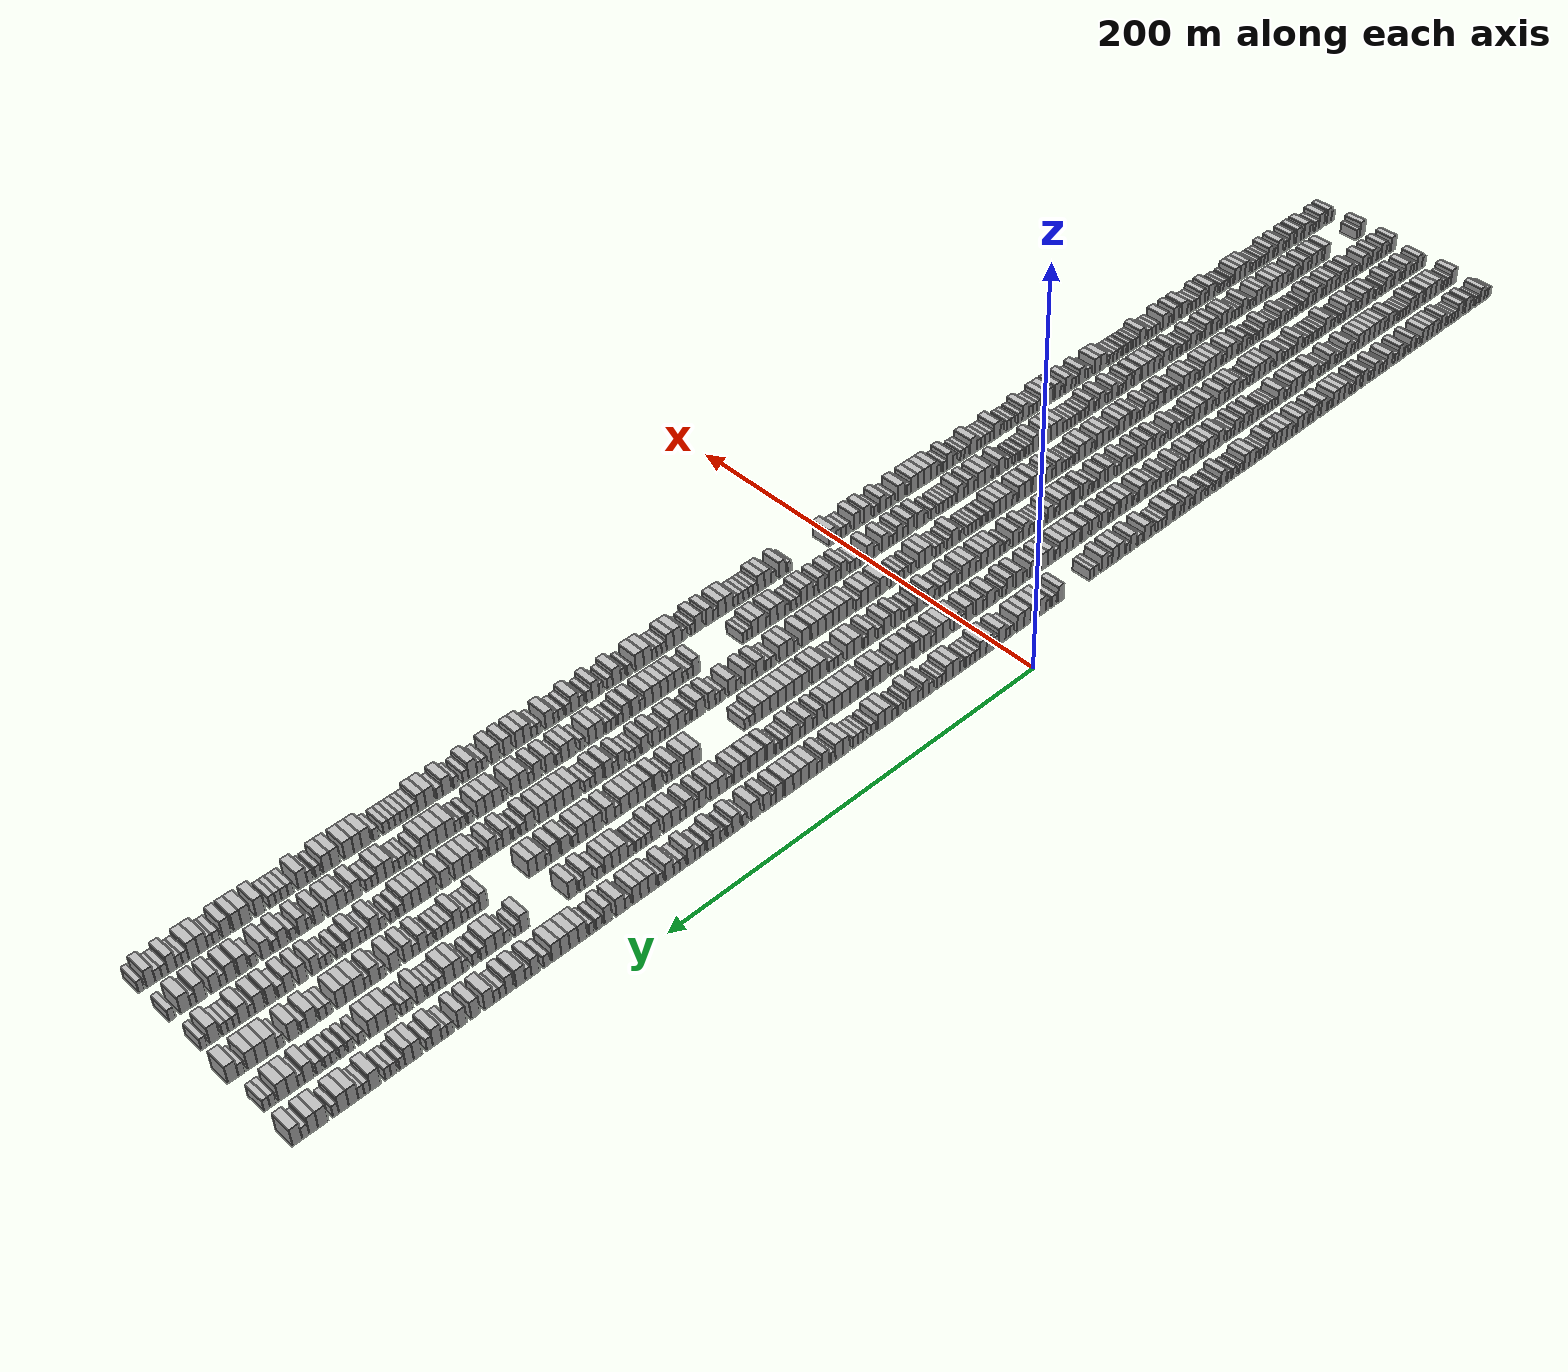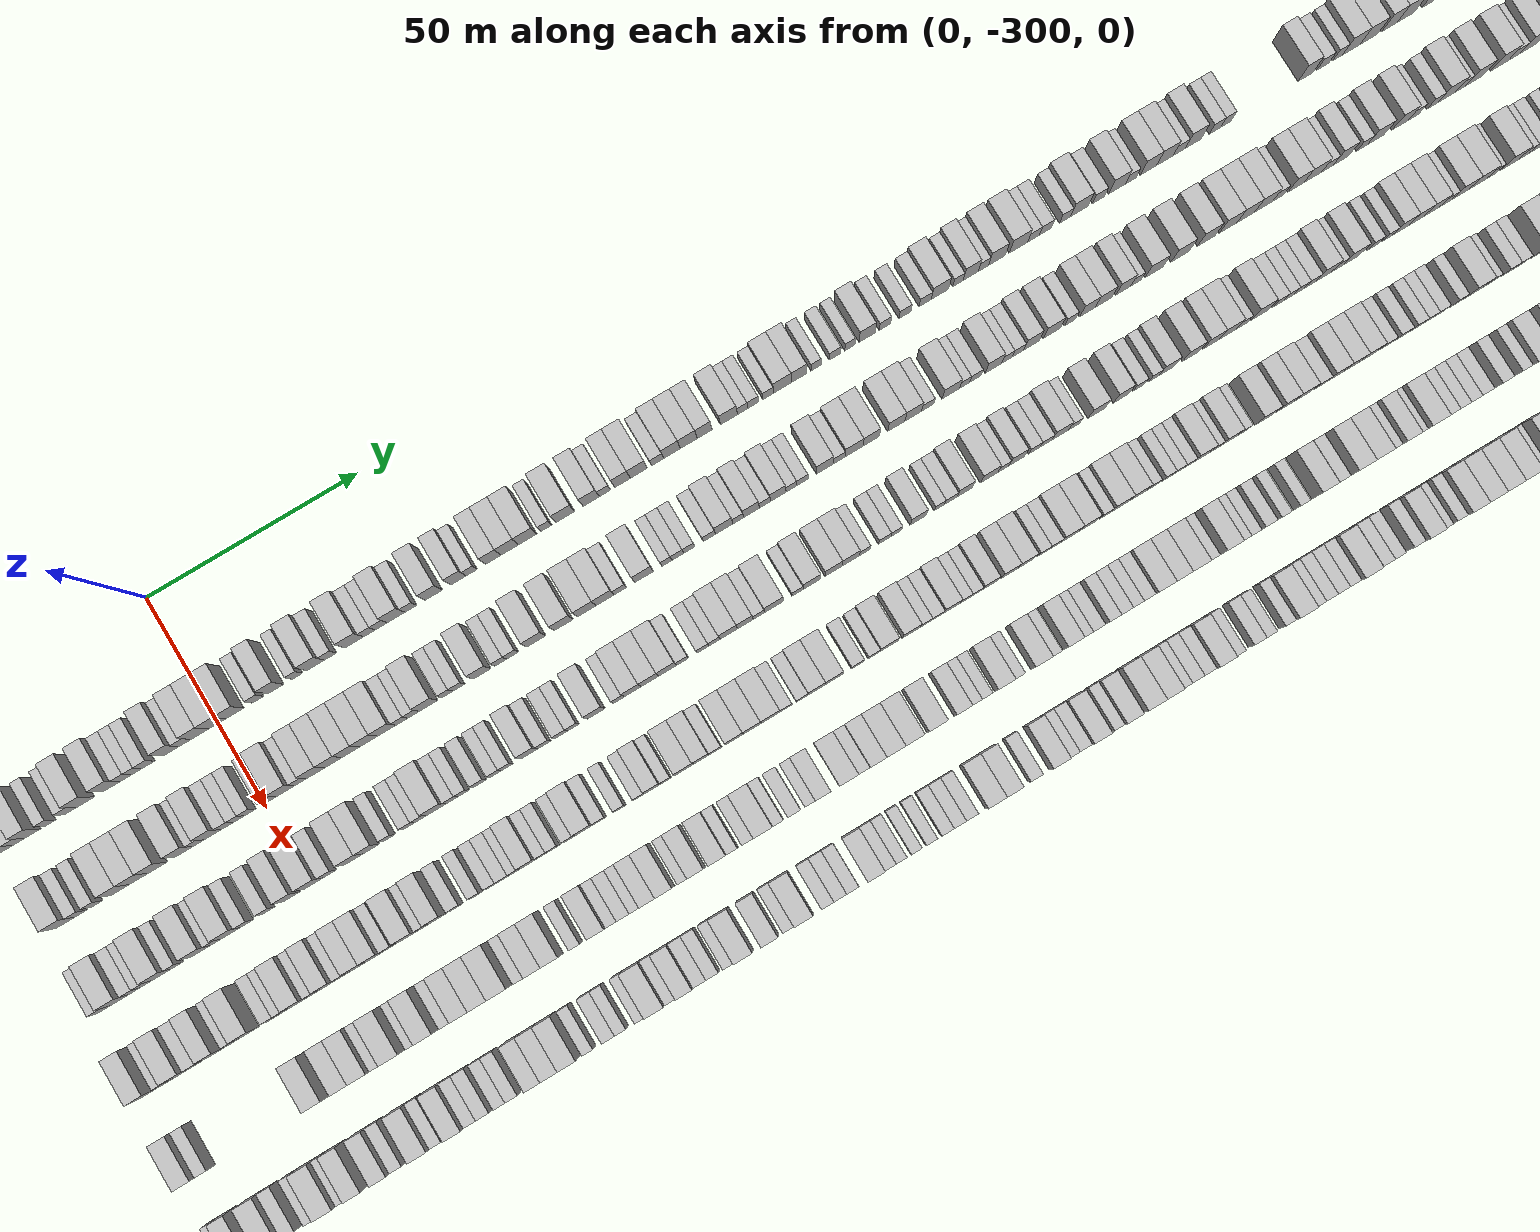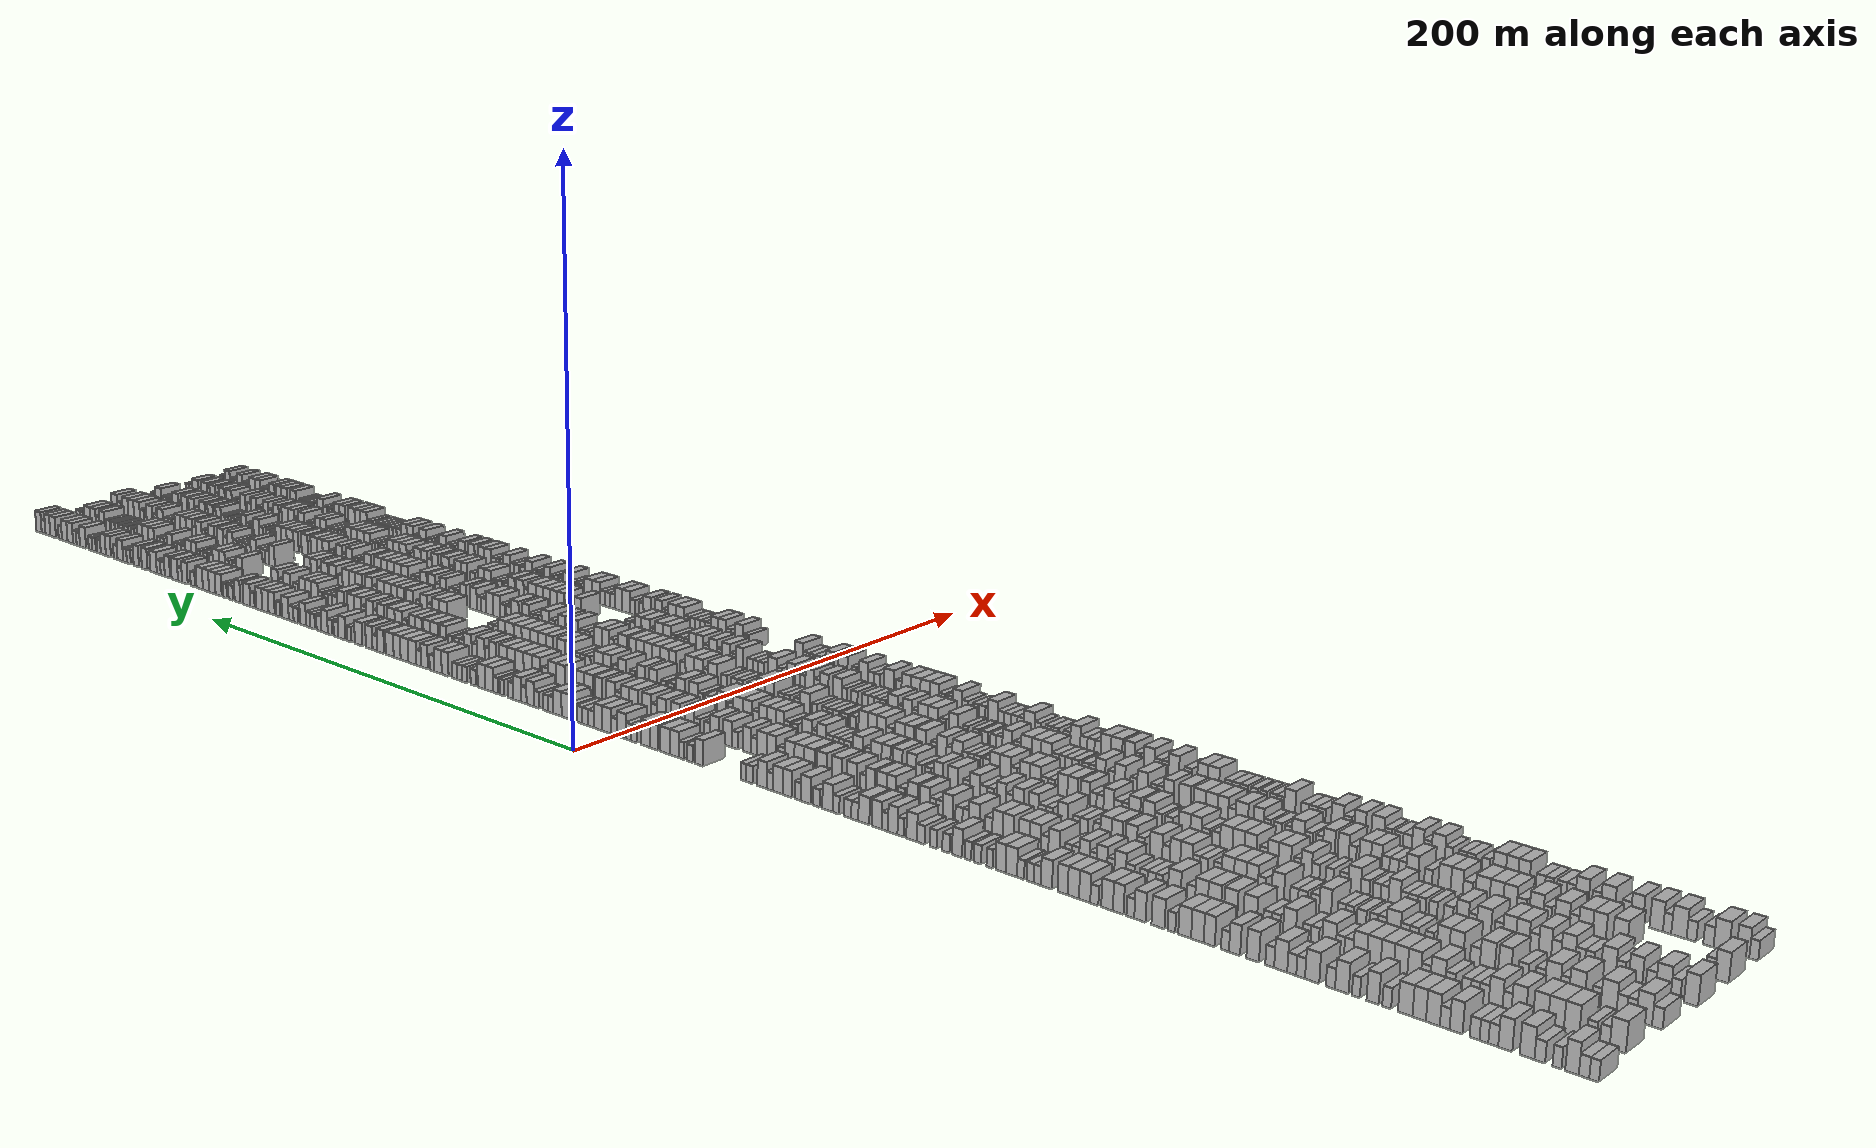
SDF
<sdf version="1.6">
 <world name="default">
  <scene>
   <sky><clouds><speed>12</speed></clouds></sky>
   <ambient>0.4 0.4 0.4 1</ambient>
   <background>0.7 0.7 0.7 1</background>
   <shadows>1</shadows>
  </scene>
  <gravity>0 0 -9.8066</gravity>
  <magnetic_field>6e-06 2.3e-05 -4.2e-05</magnetic_field>
  <physics default="0" name="default_physics" type="ode">
   <ode>
    <solver>
     <type>quick</type>
     <iters>10</iters>
     <sor>1.0</sor>
     <use_dynamic_moi_rescaling>0</use_dynamic_moi_rescaling>
    </solver>
    <constraints>
     <cfm>0</cfm>
     <erp>0.2</erp>
     <contact_max_correcting_vel>100</contact_max_correcting_vel>
     <contact_surface_layer>0.001</contact_surface_layer>
    </constraints>
   </ode>
   <max_step_size>0.004</max_step_size>
   <real_time_factor>1</real_time_factor>
   <real_time_update_rate>250</real_time_update_rate>
  </physics>
  <light name="sun" type="directional">
   <pose>0 0 10 0 0 0</pose>
   <diffuse>0.8 0.8 0.8 1</diffuse>
   <specular>0.2 0.2 0.2 1</specular>
   <attenuation>
    <range>1000</range>
    <constant>0.9</constant>
    <linear>0.01</linear>
    <quadratic>0.001</quadratic>
   </attenuation>
   <direction>-0.5 0.1 -0.9</direction>
  </light>
  <model name="building_1">
   <static>1</static>
   <pose>25.0000 -348.7073 0 0.000000 0.000000 0.000000</pose>
   <link name="link">
    <pose>0 0 3.00 0 0 0</pose>
    <collision name="collision"><geometry><box><size>10.0000 2.5855 6.0000</size></box></geometry></collision>
    <visual name="visual">
     <cast_shadows>0</cast_shadows>
     <geometry><box><size>10.0000 2.5855 6.0000</size></box></geometry>
     <material>
      <script>
       <uri>model://HANNAS_wall/materials/scripts</uri>
       <uri>model://HANNAS_wall/materials/textures</uri>
       <name>vrc/HANNAS_wall</name>
      </script>
     </material>
    </visual>
   </link>
  </model>
  <model name="building_2">
   <static>1</static>
   <pose>25.0000 -346.0323 0 0.000000 0.000000 0.000000</pose>
   <link name="link">
    <pose>0 0 3.00 0 0 0</pose>
    <collision name="collision"><geometry><box><size>10.0000 2.7644 6.0000</size></box></geometry></collision>
    <visual name="visual">
     <cast_shadows>0</cast_shadows>
     <geometry><box><size>10.0000 2.7644 6.0000</size></box></geometry>
     <material>
      <script>
       <uri>model://HANNAS_wall/materials/scripts</uri>
       <uri>model://HANNAS_wall/materials/textures</uri>
       <name>vrc/HANNAS_wall</name>
      </script>
     </material>
    </visual>
   </link>
  </model>
  <model name="building_3">
   <static>1</static>
   <pose>25.0000 -342.8261 0 0.000000 0.000000 0.000000</pose>
   <link name="link">
    <pose>0 0 4.50 0 0 0</pose>
    <collision name="collision"><geometry><box><size>10.0000 3.6479 9.0000</size></box></geometry></collision>
    <visual name="visual">
     <cast_shadows>0</cast_shadows>
     <geometry><box><size>10.0000 3.6479 9.0000</size></box></geometry>
     <material>
      <script>
       <uri>model://HANNAS_wall/materials/scripts</uri>
       <uri>model://HANNAS_wall/materials/textures</uri>
       <name>vrc/HANNAS_wall</name>
      </script>
     </material>
    </visual>
   </link>
  </model>
  <model name="building_4">
   <static>1</static>
   <pose>25.0000 -338.7797 0 0.000000 0.000000 0.000000</pose>
   <link name="link">
    <pose>0 0 3.00 0 0 0</pose>
    <collision name="collision"><geometry><box><size>10.0000 2.4451 6.0000</size></box></geometry></collision>
    <visual name="visual">
     <cast_shadows>0</cast_shadows>
     <geometry><box><size>10.0000 2.4451 6.0000</size></box></geometry>
     <material>
      <script>
       <uri>model://HANNAS_wall/materials/scripts</uri>
       <uri>model://HANNAS_wall/materials/textures</uri>
       <name>vrc/HANNAS_wall</name>
      </script>
     </material>
    </visual>
   </link>
  </model>
  <model name="building_5">
   <static>1</static>
   <pose>25.0000 -334.1090 0 0.000000 0.000000 0.000000</pose>
   <link name="link">
    <pose>0 0 3.00 0 0 0</pose>
    <collision name="collision"><geometry><box><size>10.0000 2.8962 6.0000</size></box></geometry></collision>
    <visual name="visual">
     <cast_shadows>0</cast_shadows>
     <geometry><box><size>10.0000 2.8962 6.0000</size></box></geometry>
     <material>
      <script>
       <uri>model://HANNAS_wall/materials/scripts</uri>
       <uri>model://HANNAS_wall/materials/textures</uri>
       <name>vrc/HANNAS_wall</name>
      </script>
     </material>
    </visual>
   </link>
  </model>
  <model name="building_6">
   <static>1</static>
   <pose>25.0000 -330.6155 0 0.000000 0.000000 0.000000</pose>
   <link name="link">
    <pose>0 0 4.50 0 0 0</pose>
    <collision name="collision"><geometry><box><size>10.0000 4.0908 9.0000</size></box></geometry></collision>
    <visual name="visual">
     <cast_shadows>0</cast_shadows>
     <geometry><box><size>10.0000 4.0908 9.0000</size></box></geometry>
     <material>
      <script>
       <uri>model://HANNAS_wall/materials/scripts</uri>
       <uri>model://HANNAS_wall/materials/textures</uri>
       <name>vrc/HANNAS_wall</name>
      </script>
     </material>
    </visual>
   </link>
  </model>
  <model name="building_7">
   <static>1</static>
   <pose>25.0000 -324.6084 0 0.000000 0.000000 0.000000</pose>
   <link name="link">
    <pose>0 0 4.50 0 0 0</pose>
    <collision name="collision"><geometry><box><size>10.0000 3.9235 9.0000</size></box></geometry></collision>
    <visual name="visual">
     <cast_shadows>0</cast_shadows>
     <geometry><box><size>10.0000 3.9235 9.0000</size></box></geometry>
     <material>
      <script>
       <uri>model://HANNAS_wall/materials/scripts</uri>
       <uri>model://HANNAS_wall/materials/textures</uri>
       <name>vrc/HANNAS_wall</name>
      </script>
     </material>
    </visual>
   </link>
  </model>
  <model name="building_8">
   <static>1</static>
   <pose>25.0000 -321.2677 0 0.000000 0.000000 0.000000</pose>
   <link name="link">
    <pose>0 0 3.00 0 0 0</pose>
    <collision name="collision"><geometry><box><size>10.0000 2.7579 6.0000</size></box></geometry></collision>
    <visual name="visual">
     <cast_shadows>0</cast_shadows>
     <geometry><box><size>10.0000 2.7579 6.0000</size></box></geometry>
     <material>
      <script>
       <uri>model://HANNAS_wall/materials/scripts</uri>
       <uri>model://HANNAS_wall/materials/textures</uri>
       <name>vrc/HANNAS_wall</name>
      </script>
     </material>
    </visual>
   </link>
  </model>
  <model name="building_9">
   <static>1</static>
   <pose>25.0000 -318.6427 0 0.000000 0.000000 0.000000</pose>
   <link name="link">
    <pose>0 0 3.00 0 0 0</pose>
    <collision name="collision"><geometry><box><size>10.0000 2.4921 6.0000</size></box></geometry></collision>
    <visual name="visual">
     <cast_shadows>0</cast_shadows>
     <geometry><box><size>10.0000 2.4921 6.0000</size></box></geometry>
     <material>
      <script>
       <uri>model://HANNAS_wall/materials/scripts</uri>
       <uri>model://HANNAS_wall/materials/textures</uri>
       <name>vrc/HANNAS_wall</name>
      </script>
     </material>
    </visual>
   </link>
  </model>
  <model name="building_10">
   <static>1</static>
   <pose>25.0000 -316.0054 0 0.000000 0.000000 0.000000</pose>
   <link name="link">
    <pose>0 0 3.00 0 0 0</pose>
    <collision name="collision"><geometry><box><size>10.0000 2.7827 6.0000</size></box></geometry></collision>
    <visual name="visual">
     <cast_shadows>0</cast_shadows>
     <geometry><box><size>10.0000 2.7827 6.0000</size></box></geometry>
     <material>
      <script>
       <uri>model://HANNAS_wall/materials/scripts</uri>
       <uri>model://HANNAS_wall/materials/textures</uri>
       <name>vrc/HANNAS_wall</name>
      </script>
     </material>
    </visual>
   </link>
  </model>
  <model name="building_11">
   <static>1</static>
   <pose>25.0000 -310.7575 0 0.000000 0.000000 0.000000</pose>
   <link name="link">
    <pose>0 0 4.50 0 0 0</pose>
    <collision name="collision"><geometry><box><size>10.0000 3.7130 9.0000</size></box></geometry></collision>
    <visual name="visual">
     <cast_shadows>0</cast_shadows>
     <geometry><box><size>10.0000 3.7130 9.0000</size></box></geometry>
     <material>
      <script>
       <uri>model://HANNAS_wall/materials/scripts</uri>
       <uri>model://HANNAS_wall/materials/textures</uri>
       <name>vrc/HANNAS_wall</name>
      </script>
     </material>
    </visual>
   </link>
  </model>
  <model name="building_12">
   <static>1</static>
   <pose>25.0000 -307.5139 0 0.000000 0.000000 0.000000</pose>
   <link name="link">
    <pose>0 0 3.00 0 0 0</pose>
    <collision name="collision"><geometry><box><size>10.0000 2.7743 6.0000</size></box></geometry></collision>
    <visual name="visual">
     <cast_shadows>0</cast_shadows>
     <geometry><box><size>10.0000 2.7743 6.0000</size></box></geometry>
     <material>
      <script>
       <uri>model://HANNAS_wall/materials/scripts</uri>
       <uri>model://HANNAS_wall/materials/textures</uri>
       <name>vrc/HANNAS_wall</name>
      </script>
     </material>
    </visual>
   </link>
  </model>
  <model name="building_13">
   <static>1</static>
   <pose>25.0000 -304.1083 0 0.000000 0.000000 0.000000</pose>
   <link name="link">
    <pose>0 0 4.50 0 0 0</pose>
    <collision name="collision"><geometry><box><size>10.0000 4.0368 9.0000</size></box></geometry></collision>
    <visual name="visual">
     <cast_shadows>0</cast_shadows>
     <geometry><box><size>10.0000 4.0368 9.0000</size></box></geometry>
     <material>
      <script>
       <uri>model://HANNAS_wall/materials/scripts</uri>
       <uri>model://HANNAS_wall/materials/textures</uri>
       <name>vrc/HANNAS_wall</name>
      </script>
     </material>
    </visual>
   </link>
  </model>
  <model name="building_14">
   <static>1</static>
   <pose>25.0000 -300.1330 0 0.000000 0.000000 0.000000</pose>
   <link name="link">
    <pose>0 0 4.50 0 0 0</pose>
    <collision name="collision"><geometry><box><size>10.0000 3.9138 9.0000</size></box></geometry></collision>
    <visual name="visual">
     <cast_shadows>0</cast_shadows>
     <geometry><box><size>10.0000 3.9138 9.0000</size></box></geometry>
     <material>
      <script>
       <uri>model://HANNAS_wall/materials/scripts</uri>
       <uri>model://HANNAS_wall/materials/textures</uri>
       <name>vrc/HANNAS_wall</name>
      </script>
     </material>
    </visual>
   </link>
  </model>
  <model name="building_15">
   <static>1</static>
   <pose>25.0000 -296.0424 0 0.000000 0.000000 0.000000</pose>
   <link name="link">
    <pose>0 0 4.50 0 0 0</pose>
    <collision name="collision"><geometry><box><size>10.0000 4.2674 9.0000</size></box></geometry></collision>
    <visual name="visual">
     <cast_shadows>0</cast_shadows>
     <geometry><box><size>10.0000 4.2674 9.0000</size></box></geometry>
     <material>
      <script>
       <uri>model://HANNAS_wall/materials/scripts</uri>
       <uri>model://HANNAS_wall/materials/textures</uri>
       <name>vrc/HANNAS_wall</name>
      </script>
     </material>
    </visual>
   </link>
  </model>
  <model name="building_16">
   <static>1</static>
   <pose>25.0000 -290.5888 0 0.000000 0.000000 0.000000</pose>
   <link name="link">
    <pose>0 0 3.00 0 0 0</pose>
    <collision name="collision"><geometry><box><size>10.0000 2.6398 6.0000</size></box></geometry></collision>
    <visual name="visual">
     <cast_shadows>0</cast_shadows>
     <geometry><box><size>10.0000 2.6398 6.0000</size></box></geometry>
     <material>
      <script>
       <uri>model://HANNAS_wall/materials/scripts</uri>
       <uri>model://HANNAS_wall/materials/textures</uri>
       <name>vrc/HANNAS_wall</name>
      </script>
     </material>
    </visual>
   </link>
  </model>
  <model name="building_17">
   <static>1</static>
   <pose>25.0000 -286.4210 0 0.000000 0.000000 0.000000</pose>
   <link name="link">
    <pose>0 0 4.50 0 0 0</pose>
    <collision name="collision"><geometry><box><size>10.0000 3.6958 9.0000</size></box></geometry></collision>
    <visual name="visual">
     <cast_shadows>0</cast_shadows>
     <geometry><box><size>10.0000 3.6958 9.0000</size></box></geometry>
     <material>
      <script>
       <uri>model://HANNAS_wall/materials/scripts</uri>
       <uri>model://HANNAS_wall/materials/textures</uri>
       <name>vrc/HANNAS_wall</name>
      </script>
     </material>
    </visual>
   </link>
  </model>
  <model name="building_18">
   <static>1</static>
   <pose>25.0000 -281.3700 0 0.000000 0.000000 0.000000</pose>
   <link name="link">
    <pose>0 0 3.00 0 0 0</pose>
    <collision name="collision"><geometry><box><size>10.0000 2.4061 6.0000</size></box></geometry></collision>
    <visual name="visual">
     <cast_shadows>0</cast_shadows>
     <geometry><box><size>10.0000 2.4061 6.0000</size></box></geometry>
     <material>
      <script>
       <uri>model://HANNAS_wall/materials/scripts</uri>
       <uri>model://HANNAS_wall/materials/textures</uri>
       <name>vrc/HANNAS_wall</name>
      </script>
     </material>
    </visual>
   </link>
  </model>
  <model name="building_19">
   <static>1</static>
   <pose>25.0000 -277.1079 0 0.000000 0.000000 0.000000</pose>
   <link name="link">
    <pose>0 0 4.50 0 0 0</pose>
    <collision name="collision"><geometry><box><size>10.0000 4.1182 9.0000</size></box></geometry></collision>
    <visual name="visual">
     <cast_shadows>0</cast_shadows>
     <geometry><box><size>10.0000 4.1182 9.0000</size></box></geometry>
     <material>
      <script>
       <uri>model://HANNAS_wall/materials/scripts</uri>
       <uri>model://HANNAS_wall/materials/textures</uri>
       <name>vrc/HANNAS_wall</name>
      </script>
     </material>
    </visual>
   </link>
  </model>
  <model name="building_20">
   <static>1</static>
   <pose>25.0000 -273.6269 0 0.000000 0.000000 0.000000</pose>
   <link name="link">
    <pose>0 0 3.00 0 0 0</pose>
    <collision name="collision"><geometry><box><size>10.0000 2.8436 6.0000</size></box></geometry></collision>
    <visual name="visual">
     <cast_shadows>0</cast_shadows>
     <geometry><box><size>10.0000 2.8436 6.0000</size></box></geometry>
     <material>
      <script>
       <uri>model://HANNAS_wall/materials/scripts</uri>
       <uri>model://HANNAS_wall/materials/textures</uri>
       <name>vrc/HANNAS_wall</name>
      </script>
     </material>
    </visual>
   </link>
  </model>
  <model name="building_21">
   <static>1</static>
   <pose>25.0000 -268.0087 0 0.000000 0.000000 0.000000</pose>
   <link name="link">
    <pose>0 0 4.50 0 0 0</pose>
    <collision name="collision"><geometry><box><size>10.0000 4.3927 9.0000</size></box></geometry></collision>
    <visual name="visual">
     <cast_shadows>0</cast_shadows>
     <geometry><box><size>10.0000 4.3927 9.0000</size></box></geometry>
     <material>
      <script>
       <uri>model://HANNAS_wall/materials/scripts</uri>
       <uri>model://HANNAS_wall/materials/textures</uri>
       <name>vrc/HANNAS_wall</name>
      </script>
     </material>
    </visual>
   </link>
  </model>
  <model name="building_22">
   <static>1</static>
   <pose>25.0000 -264.4531 0 0.000000 0.000000 0.000000</pose>
   <link name="link">
    <pose>0 0 3.00 0 0 0</pose>
    <collision name="collision"><geometry><box><size>10.0000 2.7184 6.0000</size></box></geometry></collision>
    <visual name="visual">
     <cast_shadows>0</cast_shadows>
     <geometry><box><size>10.0000 2.7184 6.0000</size></box></geometry>
     <material>
      <script>
       <uri>model://HANNAS_wall/materials/scripts</uri>
       <uri>model://HANNAS_wall/materials/textures</uri>
       <name>vrc/HANNAS_wall</name>
      </script>
     </material>
    </visual>
   </link>
  </model>
  <model name="building_23">
   <static>1</static>
   <pose>25.0000 -261.6786 0 0.000000 0.000000 0.000000</pose>
   <link name="link">
    <pose>0 0 3.00 0 0 0</pose>
    <collision name="collision"><geometry><box><size>10.0000 2.8307 6.0000</size></box></geometry></collision>
    <visual name="visual">
     <cast_shadows>0</cast_shadows>
     <geometry><box><size>10.0000 2.8307 6.0000</size></box></geometry>
     <material>
      <script>
       <uri>model://HANNAS_wall/materials/scripts</uri>
       <uri>model://HANNAS_wall/materials/textures</uri>
       <name>vrc/HANNAS_wall</name>
      </script>
     </material>
    </visual>
   </link>
  </model>
  <model name="building_24">
   <static>1</static>
   <pose>25.0000 -258.2028 0 0.000000 0.000000 0.000000</pose>
   <link name="link">
    <pose>0 0 4.50 0 0 0</pose>
    <collision name="collision"><geometry><box><size>10.0000 4.1209 9.0000</size></box></geometry></collision>
    <visual name="visual">
     <cast_shadows>0</cast_shadows>
     <geometry><box><size>10.0000 4.1209 9.0000</size></box></geometry>
     <material>
      <script>
       <uri>model://HANNAS_wall/materials/scripts</uri>
       <uri>model://HANNAS_wall/materials/textures</uri>
       <name>vrc/HANNAS_wall</name>
      </script>
     </material>
    </visual>
   </link>
  </model>
  <model name="building_25">
   <static>1</static>
   <pose>25.0000 -254.7345 0 0.000000 0.000000 0.000000</pose>
   <link name="link">
    <pose>0 0 3.00 0 0 0</pose>
    <collision name="collision"><geometry><box><size>10.0000 2.8158 6.0000</size></box></geometry></collision>
    <visual name="visual">
     <cast_shadows>0</cast_shadows>
     <geometry><box><size>10.0000 2.8158 6.0000</size></box></geometry>
     <material>
      <script>
       <uri>model://HANNAS_wall/materials/scripts</uri>
       <uri>model://HANNAS_wall/materials/textures</uri>
       <name>vrc/HANNAS_wall</name>
      </script>
     </material>
    </visual>
   </link>
  </model>
  <model name="building_26">
   <static>1</static>
   <pose>25.0000 -249.3027 0 0.000000 0.000000 0.000000</pose>
   <link name="link">
    <pose>0 0 4.50 0 0 0</pose>
    <collision name="collision"><geometry><box><size>10.0000 4.0478 9.0000</size></box></geometry></collision>
    <visual name="visual">
     <cast_shadows>0</cast_shadows>
     <geometry><box><size>10.0000 4.0478 9.0000</size></box></geometry>
     <material>
      <script>
       <uri>model://HANNAS_wall/materials/scripts</uri>
       <uri>model://HANNAS_wall/materials/textures</uri>
       <name>vrc/HANNAS_wall</name>
      </script>
     </material>
    </visual>
   </link>
  </model>
  <model name="building_27">
   <static>1</static>
   <pose>25.0000 -243.4748 0 0.000000 0.000000 0.000000</pose>
   <link name="link">
    <pose>0 0 4.50 0 0 0</pose>
    <collision name="collision"><geometry><box><size>10.0000 3.6081 9.0000</size></box></geometry></collision>
    <visual name="visual">
     <cast_shadows>0</cast_shadows>
     <geometry><box><size>10.0000 3.6081 9.0000</size></box></geometry>
     <material>
      <script>
       <uri>model://HANNAS_wall/materials/scripts</uri>
       <uri>model://HANNAS_wall/materials/textures</uri>
       <name>vrc/HANNAS_wall</name>
      </script>
     </material>
    </visual>
   </link>
  </model>
  <model name="building_28">
   <static>1</static>
   <pose>25.0000 -240.3675 0 0.000000 0.000000 0.000000</pose>
   <link name="link">
    <pose>0 0 3.00 0 0 0</pose>
    <collision name="collision"><geometry><box><size>10.0000 2.6064 6.0000</size></box></geometry></collision>
    <visual name="visual">
     <cast_shadows>0</cast_shadows>
     <geometry><box><size>10.0000 2.6064 6.0000</size></box></geometry>
     <material>
      <script>
       <uri>model://HANNAS_wall/materials/scripts</uri>
       <uri>model://HANNAS_wall/materials/textures</uri>
       <name>vrc/HANNAS_wall</name>
      </script>
     </material>
    </visual>
   </link>
  </model>
  <model name="building_29">
   <static>1</static>
   <pose>25.0000 -235.2256 0 0.000000 0.000000 0.000000</pose>
   <link name="link">
    <pose>0 0 4.50 0 0 0</pose>
    <collision name="collision"><geometry><box><size>10.0000 3.6776 9.0000</size></box></geometry></collision>
    <visual name="visual">
     <cast_shadows>0</cast_shadows>
     <geometry><box><size>10.0000 3.6776 9.0000</size></box></geometry>
     <material>
      <script>
       <uri>model://HANNAS_wall/materials/scripts</uri>
       <uri>model://HANNAS_wall/materials/textures</uri>
       <name>vrc/HANNAS_wall</name>
      </script>
     </material>
    </visual>
   </link>
  </model>
  <model name="building_30">
   <static>1</static>
   <pose>25.0000 -231.3153 0 0.000000 0.000000 0.000000</pose>
   <link name="link">
    <pose>0 0 4.50 0 0 0</pose>
    <collision name="collision"><geometry><box><size>10.0000 4.1431 9.0000</size></box></geometry></collision>
    <visual name="visual">
     <cast_shadows>0</cast_shadows>
     <geometry><box><size>10.0000 4.1431 9.0000</size></box></geometry>
     <material>
      <script>
       <uri>model://HANNAS_wall/materials/scripts</uri>
       <uri>model://HANNAS_wall/materials/textures</uri>
       <name>vrc/HANNAS_wall</name>
      </script>
     </material>
    </visual>
   </link>
  </model>
  <model name="building_31">
   <static>1</static>
   <pose>25.0000 -227.1031 0 0.000000 0.000000 0.000000</pose>
   <link name="link">
    <pose>0 0 4.50 0 0 0</pose>
    <collision name="collision"><geometry><box><size>10.0000 4.2813 9.0000</size></box></geometry></collision>
    <visual name="visual">
     <cast_shadows>0</cast_shadows>
     <geometry><box><size>10.0000 4.2813 9.0000</size></box></geometry>
     <material>
      <script>
       <uri>model://HANNAS_wall/materials/scripts</uri>
       <uri>model://HANNAS_wall/materials/textures</uri>
       <name>vrc/HANNAS_wall</name>
      </script>
     </material>
    </visual>
   </link>
  </model>
  <model name="building_32">
   <static>1</static>
   <pose>25.0000 -222.6715 0 0.000000 0.000000 0.000000</pose>
   <link name="link">
    <pose>0 0 3.00 0 0 0</pose>
    <collision name="collision"><geometry><box><size>10.0000 2.5818 6.0000</size></box></geometry></collision>
    <visual name="visual">
     <cast_shadows>0</cast_shadows>
     <geometry><box><size>10.0000 2.5818 6.0000</size></box></geometry>
     <material>
      <script>
       <uri>model://HANNAS_wall/materials/scripts</uri>
       <uri>model://HANNAS_wall/materials/textures</uri>
       <name>vrc/HANNAS_wall</name>
      </script>
     </material>
    </visual>
   </link>
  </model>
  <model name="building_33">
   <static>1</static>
   <pose>25.0000 -218.1581 0 0.000000 0.000000 0.000000</pose>
   <link name="link">
    <pose>0 0 4.50 0 0 0</pose>
    <collision name="collision"><geometry><box><size>10.0000 4.4449 9.0000</size></box></geometry></collision>
    <visual name="visual">
     <cast_shadows>0</cast_shadows>
     <geometry><box><size>10.0000 4.4449 9.0000</size></box></geometry>
     <material>
      <script>
       <uri>model://HANNAS_wall/materials/scripts</uri>
       <uri>model://HANNAS_wall/materials/textures</uri>
       <name>vrc/HANNAS_wall</name>
      </script>
     </material>
    </visual>
   </link>
  </model>
  <model name="building_34">
   <static>1</static>
   <pose>25.0000 -211.9962 0 0.000000 0.000000 0.000000</pose>
   <link name="link">
    <pose>0 0 4.50 0 0 0</pose>
    <collision name="collision"><geometry><box><size>10.0000 3.8789 9.0000</size></box></geometry></collision>
    <visual name="visual">
     <cast_shadows>0</cast_shadows>
     <geometry><box><size>10.0000 3.8789 9.0000</size></box></geometry>
     <material>
      <script>
       <uri>model://HANNAS_wall/materials/scripts</uri>
       <uri>model://HANNAS_wall/materials/textures</uri>
       <name>vrc/HANNAS_wall</name>
      </script>
     </material>
    </visual>
   </link>
  </model>
  <model name="building_35">
   <static>1</static>
   <pose>25.0000 -208.7246 0 0.000000 0.000000 0.000000</pose>
   <link name="link">
    <pose>0 0 3.00 0 0 0</pose>
    <collision name="collision"><geometry><box><size>10.0000 2.6641 6.0000</size></box></geometry></collision>
    <visual name="visual">
     <cast_shadows>0</cast_shadows>
     <geometry><box><size>10.0000 2.6641 6.0000</size></box></geometry>
     <material>
      <script>
       <uri>model://HANNAS_wall/materials/scripts</uri>
       <uri>model://HANNAS_wall/materials/textures</uri>
       <name>vrc/HANNAS_wall</name>
      </script>
     </material>
    </visual>
   </link>
  </model>
  <model name="building_36">
   <static>1</static>
   <pose>25.0000 -204.5331 0 0.000000 0.000000 0.000000</pose>
   <link name="link">
    <pose>0 0 4.50 0 0 0</pose>
    <collision name="collision"><geometry><box><size>10.0000 3.7189 9.0000</size></box></geometry></collision>
    <visual name="visual">
     <cast_shadows>0</cast_shadows>
     <geometry><box><size>10.0000 3.7189 9.0000</size></box></geometry>
     <material>
      <script>
       <uri>model://HANNAS_wall/materials/scripts</uri>
       <uri>model://HANNAS_wall/materials/textures</uri>
       <name>vrc/HANNAS_wall</name>
      </script>
     </material>
    </visual>
   </link>
  </model>
  <model name="building_37">
   <static>1</static>
   <pose>25.0000 -200.6412 0 0.000000 0.000000 0.000000</pose>
   <link name="link">
    <pose>0 0 4.50 0 0 0</pose>
    <collision name="collision"><geometry><box><size>10.0000 4.0650 9.0000</size></box></geometry></collision>
    <visual name="visual">
     <cast_shadows>0</cast_shadows>
     <geometry><box><size>10.0000 4.0650 9.0000</size></box></geometry>
     <material>
      <script>
       <uri>model://HANNAS_wall/materials/scripts</uri>
       <uri>model://HANNAS_wall/materials/textures</uri>
       <name>vrc/HANNAS_wall</name>
      </script>
     </material>
    </visual>
   </link>
  </model>
  <model name="building_38">
   <static>1</static>
   <pose>25.0000 -196.1749 0 0.000000 0.000000 0.000000</pose>
   <link name="link">
    <pose>0 0 3.00 0 0 0</pose>
    <collision name="collision"><geometry><box><size>10.0000 2.8677 6.0000</size></box></geometry></collision>
    <visual name="visual">
     <cast_shadows>0</cast_shadows>
     <geometry><box><size>10.0000 2.8677 6.0000</size></box></geometry>
     <material>
      <script>
       <uri>model://HANNAS_wall/materials/scripts</uri>
       <uri>model://HANNAS_wall/materials/textures</uri>
       <name>vrc/HANNAS_wall</name>
      </script>
     </material>
    </visual>
   </link>
  </model>
  <model name="building_39">
   <static>1</static>
   <pose>25.0000 -192.7549 0 0.000000 0.000000 0.000000</pose>
   <link name="link">
    <pose>0 0 4.50 0 0 0</pose>
    <collision name="collision"><geometry><box><size>10.0000 3.9723 9.0000</size></box></geometry></collision>
    <visual name="visual">
     <cast_shadows>0</cast_shadows>
     <geometry><box><size>10.0000 3.9723 9.0000</size></box></geometry>
     <material>
      <script>
       <uri>model://HANNAS_wall/materials/scripts</uri>
       <uri>model://HANNAS_wall/materials/textures</uri>
       <name>vrc/HANNAS_wall</name>
      </script>
     </material>
    </visual>
   </link>
  </model>
  <model name="building_40">
   <static>1</static>
   <pose>25.0000 -188.7451 0 0.000000 0.000000 0.000000</pose>
   <link name="link">
    <pose>0 0 4.50 0 0 0</pose>
    <collision name="collision"><geometry><box><size>10.0000 4.0472 9.0000</size></box></geometry></collision>
    <visual name="visual">
     <cast_shadows>0</cast_shadows>
     <geometry><box><size>10.0000 4.0472 9.0000</size></box></geometry>
     <material>
      <script>
       <uri>model://HANNAS_wall/materials/scripts</uri>
       <uri>model://HANNAS_wall/materials/textures</uri>
       <name>vrc/HANNAS_wall</name>
      </script>
     </material>
    </visual>
   </link>
  </model>
  <model name="building_41">
   <static>1</static>
   <pose>25.0000 -184.9194 0 0.000000 0.000000 0.000000</pose>
   <link name="link">
    <pose>0 0 4.50 0 0 0</pose>
    <collision name="collision"><geometry><box><size>10.0000 3.6041 9.0000</size></box></geometry></collision>
    <visual name="visual">
     <cast_shadows>0</cast_shadows>
     <geometry><box><size>10.0000 3.6041 9.0000</size></box></geometry>
     <material>
      <script>
       <uri>model://HANNAS_wall/materials/scripts</uri>
       <uri>model://HANNAS_wall/materials/textures</uri>
       <name>vrc/HANNAS_wall</name>
      </script>
     </material>
    </visual>
   </link>
  </model>
  <model name="building_42">
   <static>1</static>
   <pose>25.0000 -179.0728 0 0.000000 0.000000 0.000000</pose>
   <link name="link">
    <pose>0 0 4.50 0 0 0</pose>
    <collision name="collision"><geometry><box><size>10.0000 4.0892 9.0000</size></box></geometry></collision>
    <visual name="visual">
     <cast_shadows>0</cast_shadows>
     <geometry><box><size>10.0000 4.0892 9.0000</size></box></geometry>
     <material>
      <script>
       <uri>model://HANNAS_wall/materials/scripts</uri>
       <uri>model://HANNAS_wall/materials/textures</uri>
       <name>vrc/HANNAS_wall</name>
      </script>
     </material>
    </visual>
   </link>
  </model>
  <model name="building_43">
   <static>1</static>
   <pose>25.0000 -175.7907 0 0.000000 0.000000 0.000000</pose>
   <link name="link">
    <pose>0 0 3.00 0 0 0</pose>
    <collision name="collision"><geometry><box><size>10.0000 2.4751 6.0000</size></box></geometry></collision>
    <visual name="visual">
     <cast_shadows>0</cast_shadows>
     <geometry><box><size>10.0000 2.4751 6.0000</size></box></geometry>
     <material>
      <script>
       <uri>model://HANNAS_wall/materials/scripts</uri>
       <uri>model://HANNAS_wall/materials/textures</uri>
       <name>vrc/HANNAS_wall</name>
      </script>
     </material>
    </visual>
   </link>
  </model>
  <model name="building_44">
   <static>1</static>
   <pose>25.0000 -173.2570 0 0.000000 0.000000 0.000000</pose>
   <link name="link">
    <pose>0 0 3.00 0 0 0</pose>
    <collision name="collision"><geometry><box><size>10.0000 2.5922 6.0000</size></box></geometry></collision>
    <visual name="visual">
     <cast_shadows>0</cast_shadows>
     <geometry><box><size>10.0000 2.5922 6.0000</size></box></geometry>
     <material>
      <script>
       <uri>model://HANNAS_wall/materials/scripts</uri>
       <uri>model://HANNAS_wall/materials/textures</uri>
       <name>vrc/HANNAS_wall</name>
      </script>
     </material>
    </visual>
   </link>
  </model>
  <model name="building_45">
   <static>1</static>
   <pose>25.0000 -169.6675 0 0.000000 0.000000 0.000000</pose>
   <link name="link">
    <pose>0 0 3.00 0 0 0</pose>
    <collision name="collision"><geometry><box><size>10.0000 2.5868 6.0000</size></box></geometry></collision>
    <visual name="visual">
     <cast_shadows>0</cast_shadows>
     <geometry><box><size>10.0000 2.5868 6.0000</size></box></geometry>
     <material>
      <script>
       <uri>model://HANNAS_wall/materials/scripts</uri>
       <uri>model://HANNAS_wall/materials/textures</uri>
       <name>vrc/HANNAS_wall</name>
      </script>
     </material>
    </visual>
   </link>
  </model>
  <model name="building_46">
   <static>1</static>
   <pose>25.0000 -166.2301 0 0.000000 0.000000 0.000000</pose>
   <link name="link">
    <pose>0 0 4.50 0 0 0</pose>
    <collision name="collision"><geometry><box><size>10.0000 4.2879 9.0000</size></box></geometry></collision>
    <visual name="visual">
     <cast_shadows>0</cast_shadows>
     <geometry><box><size>10.0000 4.2879 9.0000</size></box></geometry>
     <material>
      <script>
       <uri>model://HANNAS_wall/materials/scripts</uri>
       <uri>model://HANNAS_wall/materials/textures</uri>
       <name>vrc/HANNAS_wall</name>
      </script>
     </material>
    </visual>
   </link>
  </model>
  <model name="building_47">
   <static>1</static>
   <pose>25.0000 -162.2319 0 0.000000 0.000000 0.000000</pose>
   <link name="link">
    <pose>0 0 4.50 0 0 0</pose>
    <collision name="collision"><geometry><box><size>10.0000 3.7085 9.0000</size></box></geometry></collision>
    <visual name="visual">
     <cast_shadows>0</cast_shadows>
     <geometry><box><size>10.0000 3.7085 9.0000</size></box></geometry>
     <material>
      <script>
       <uri>model://HANNAS_wall/materials/scripts</uri>
       <uri>model://HANNAS_wall/materials/textures</uri>
       <name>vrc/HANNAS_wall</name>
      </script>
     </material>
    </visual>
   </link>
  </model>
  <model name="building_48">
   <static>1</static>
   <pose>25.0000 -158.1756 0 0.000000 0.000000 0.000000</pose>
   <link name="link">
    <pose>0 0 3.00 0 0 0</pose>
    <collision name="collision"><geometry><box><size>10.0000 2.4042 6.0000</size></box></geometry></collision>
    <visual name="visual">
     <cast_shadows>0</cast_shadows>
     <geometry><box><size>10.0000 2.4042 6.0000</size></box></geometry>
     <material>
      <script>
       <uri>model://HANNAS_wall/materials/scripts</uri>
       <uri>model://HANNAS_wall/materials/textures</uri>
       <name>vrc/HANNAS_wall</name>
      </script>
     </material>
    </visual>
   </link>
  </model>
  <model name="building_49">
   <static>1</static>
   <pose>25.0000 -153.5953 0 0.000000 0.000000 0.000000</pose>
   <link name="link">
    <pose>0 0 3.00 0 0 0</pose>
    <collision name="collision"><geometry><box><size>10.0000 2.7563 6.0000</size></box></geometry></collision>
    <visual name="visual">
     <cast_shadows>0</cast_shadows>
     <geometry><box><size>10.0000 2.7563 6.0000</size></box></geometry>
     <material>
      <script>
       <uri>model://HANNAS_wall/materials/scripts</uri>
       <uri>model://HANNAS_wall/materials/textures</uri>
       <name>vrc/HANNAS_wall</name>
      </script>
     </material>
    </visual>
   </link>
  </model>
  <model name="building_50">
   <static>1</static>
   <pose>25.0000 -149.9936 0 0.000000 0.000000 0.000000</pose>
   <link name="link">
    <pose>0 0 3.00 0 0 0</pose>
    <collision name="collision"><geometry><box><size>10.0000 2.4472 6.0000</size></box></geometry></collision>
    <visual name="visual">
     <cast_shadows>0</cast_shadows>
     <geometry><box><size>10.0000 2.4472 6.0000</size></box></geometry>
     <material>
      <script>
       <uri>model://HANNAS_wall/materials/scripts</uri>
       <uri>model://HANNAS_wall/materials/textures</uri>
       <name>vrc/HANNAS_wall</name>
      </script>
     </material>
    </visual>
   </link>
  </model>
  <model name="building_51">
   <static>1</static>
   <pose>25.0000 -145.8322 0 0.000000 0.000000 0.000000</pose>
   <link name="link">
    <pose>0 0 4.50 0 0 0</pose>
    <collision name="collision"><geometry><box><size>10.0000 3.8758 9.0000</size></box></geometry></collision>
    <visual name="visual">
     <cast_shadows>0</cast_shadows>
     <geometry><box><size>10.0000 3.8758 9.0000</size></box></geometry>
     <material>
      <script>
       <uri>model://HANNAS_wall/materials/scripts</uri>
       <uri>model://HANNAS_wall/materials/textures</uri>
       <name>vrc/HANNAS_wall</name>
      </script>
     </material>
    </visual>
   </link>
  </model>
  <model name="building_52">
   <static>1</static>
   <pose>25.0000 -141.5066 0 0.000000 0.000000 0.000000</pose>
   <link name="link">
    <pose>0 0 3.00 0 0 0</pose>
    <collision name="collision"><geometry><box><size>10.0000 2.7752 6.0000</size></box></geometry></collision>
    <visual name="visual">
     <cast_shadows>0</cast_shadows>
     <geometry><box><size>10.0000 2.7752 6.0000</size></box></geometry>
     <material>
      <script>
       <uri>model://HANNAS_wall/materials/scripts</uri>
       <uri>model://HANNAS_wall/materials/textures</uri>
       <name>vrc/HANNAS_wall</name>
      </script>
     </material>
    </visual>
   </link>
  </model>
  <model name="building_53">
   <static>1</static>
   <pose>25.0000 -136.6721 0 0.000000 0.000000 0.000000</pose>
   <link name="link">
    <pose>0 0 3.00 0 0 0</pose>
    <collision name="collision"><geometry><box><size>10.0000 2.8939 6.0000</size></box></geometry></collision>
    <visual name="visual">
     <cast_shadows>0</cast_shadows>
     <geometry><box><size>10.0000 2.8939 6.0000</size></box></geometry>
     <material>
      <script>
       <uri>model://HANNAS_wall/materials/scripts</uri>
       <uri>model://HANNAS_wall/materials/textures</uri>
       <name>vrc/HANNAS_wall</name>
      </script>
     </material>
    </visual>
   </link>
  </model>
  <model name="building_54">
   <static>1</static>
   <pose>25.0000 -131.7650 0 0.000000 0.000000 0.000000</pose>
   <link name="link">
    <pose>0 0 3.00 0 0 0</pose>
    <collision name="collision"><geometry><box><size>10.0000 2.9203 6.0000</size></box></geometry></collision>
    <visual name="visual">
     <cast_shadows>0</cast_shadows>
     <geometry><box><size>10.0000 2.9203 6.0000</size></box></geometry>
     <material>
      <script>
       <uri>model://HANNAS_wall/materials/scripts</uri>
       <uri>model://HANNAS_wall/materials/textures</uri>
       <name>vrc/HANNAS_wall</name>
      </script>
     </material>
    </visual>
   </link>
  </model>
  <model name="building_55">
   <static>1</static>
   <pose>25.0000 -128.1804 0 0.000000 0.000000 0.000000</pose>
   <link name="link">
    <pose>0 0 4.50 0 0 0</pose>
    <collision name="collision"><geometry><box><size>10.0000 4.2487 9.0000</size></box></geometry></collision>
    <visual name="visual">
     <cast_shadows>0</cast_shadows>
     <geometry><box><size>10.0000 4.2487 9.0000</size></box></geometry>
     <material>
      <script>
       <uri>model://HANNAS_wall/materials/scripts</uri>
       <uri>model://HANNAS_wall/materials/textures</uri>
       <name>vrc/HANNAS_wall</name>
      </script>
     </material>
    </visual>
   </link>
  </model>
  <model name="building_56">
   <static>1</static>
   <pose>25.0000 -123.7981 0 0.000000 0.000000 0.000000</pose>
   <link name="link">
    <pose>0 0 3.00 0 0 0</pose>
    <collision name="collision"><geometry><box><size>10.0000 2.5161 6.0000</size></box></geometry></collision>
    <visual name="visual">
     <cast_shadows>0</cast_shadows>
     <geometry><box><size>10.0000 2.5161 6.0000</size></box></geometry>
     <material>
      <script>
       <uri>model://HANNAS_wall/materials/scripts</uri>
       <uri>model://HANNAS_wall/materials/textures</uri>
       <name>vrc/HANNAS_wall</name>
      </script>
     </material>
    </visual>
   </link>
  </model>
  <model name="building_57">
   <static>1</static>
   <pose>25.0000 -120.6782 0 0.000000 0.000000 0.000000</pose>
   <link name="link">
    <pose>0 0 4.50 0 0 0</pose>
    <collision name="collision"><geometry><box><size>10.0000 3.7236 9.0000</size></box></geometry></collision>
    <visual name="visual">
     <cast_shadows>0</cast_shadows>
     <geometry><box><size>10.0000 3.7236 9.0000</size></box></geometry>
     <material>
      <script>
       <uri>model://HANNAS_wall/materials/scripts</uri>
       <uri>model://HANNAS_wall/materials/textures</uri>
       <name>vrc/HANNAS_wall</name>
      </script>
     </material>
    </visual>
   </link>
  </model>
  <model name="building_58">
   <static>1</static>
   <pose>25.0000 -117.5610 0 0.000000 0.000000 0.000000</pose>
   <link name="link">
    <pose>0 0 3.00 0 0 0</pose>
    <collision name="collision"><geometry><box><size>10.0000 2.5109 6.0000</size></box></geometry></collision>
    <visual name="visual">
     <cast_shadows>0</cast_shadows>
     <geometry><box><size>10.0000 2.5109 6.0000</size></box></geometry>
     <material>
      <script>
       <uri>model://HANNAS_wall/materials/scripts</uri>
       <uri>model://HANNAS_wall/materials/textures</uri>
       <name>vrc/HANNAS_wall</name>
      </script>
     </material>
    </visual>
   </link>
  </model>
  <model name="building_59">
   <static>1</static>
   <pose>25.0000 -114.2833 0 0.000000 0.000000 0.000000</pose>
   <link name="link">
    <pose>0 0 4.50 0 0 0</pose>
    <collision name="collision"><geometry><box><size>10.0000 4.0446 9.0000</size></box></geometry></collision>
    <visual name="visual">
     <cast_shadows>0</cast_shadows>
     <geometry><box><size>10.0000 4.0446 9.0000</size></box></geometry>
     <material>
      <script>
       <uri>model://HANNAS_wall/materials/scripts</uri>
       <uri>model://HANNAS_wall/materials/textures</uri>
       <name>vrc/HANNAS_wall</name>
      </script>
     </material>
    </visual>
   </link>
  </model>
  <model name="building_60">
   <static>1</static>
   <pose>25.0000 -109.0152 0 0.000000 0.000000 0.000000</pose>
   <link name="link">
    <pose>0 0 4.50 0 0 0</pose>
    <collision name="collision"><geometry><box><size>10.0000 4.4915 9.0000</size></box></geometry></collision>
    <visual name="visual">
     <cast_shadows>0</cast_shadows>
     <geometry><box><size>10.0000 4.4915 9.0000</size></box></geometry>
     <material>
      <script>
       <uri>model://HANNAS_wall/materials/scripts</uri>
       <uri>model://HANNAS_wall/materials/textures</uri>
       <name>vrc/HANNAS_wall</name>
      </script>
     </material>
    </visual>
   </link>
  </model>
  <model name="building_61">
   <static>1</static>
   <pose>25.0000 -105.3394 0 0.000000 0.000000 0.000000</pose>
   <link name="link">
    <pose>0 0 3.00 0 0 0</pose>
    <collision name="collision"><geometry><box><size>10.0000 2.8602 6.0000</size></box></geometry></collision>
    <visual name="visual">
     <cast_shadows>0</cast_shadows>
     <geometry><box><size>10.0000 2.8602 6.0000</size></box></geometry>
     <material>
      <script>
       <uri>model://HANNAS_wall/materials/scripts</uri>
       <uri>model://HANNAS_wall/materials/textures</uri>
       <name>vrc/HANNAS_wall</name>
      </script>
     </material>
    </visual>
   </link>
  </model>
  <model name="building_62">
   <static>1</static>
   <pose>25.0000 -102.4413 0 0.000000 0.000000 0.000000</pose>
   <link name="link">
    <pose>0 0 3.00 0 0 0</pose>
    <collision name="collision"><geometry><box><size>10.0000 2.9360 6.0000</size></box></geometry></collision>
    <visual name="visual">
     <cast_shadows>0</cast_shadows>
     <geometry><box><size>10.0000 2.9360 6.0000</size></box></geometry>
     <material>
      <script>
       <uri>model://HANNAS_wall/materials/scripts</uri>
       <uri>model://HANNAS_wall/materials/textures</uri>
       <name>vrc/HANNAS_wall</name>
      </script>
     </material>
    </visual>
   </link>
  </model>
  <model name="building_63">
   <static>1</static>
   <pose>25.0000 -97.6475 0 0.000000 0.000000 0.000000</pose>
   <link name="link">
    <pose>0 0 3.00 0 0 0</pose>
    <collision name="collision"><geometry><box><size>10.0000 2.6516 6.0000</size></box></geometry></collision>
    <visual name="visual">
     <cast_shadows>0</cast_shadows>
     <geometry><box><size>10.0000 2.6516 6.0000</size></box></geometry>
     <material>
      <script>
       <uri>model://HANNAS_wall/materials/scripts</uri>
       <uri>model://HANNAS_wall/materials/textures</uri>
       <name>vrc/HANNAS_wall</name>
      </script>
     </material>
    </visual>
   </link>
  </model>
  <model name="building_64">
   <static>1</static>
   <pose>25.0000 -94.1188 0 0.000000 0.000000 0.000000</pose>
   <link name="link">
    <pose>0 0 4.50 0 0 0</pose>
    <collision name="collision"><geometry><box><size>10.0000 4.4057 9.0000</size></box></geometry></collision>
    <visual name="visual">
     <cast_shadows>0</cast_shadows>
     <geometry><box><size>10.0000 4.4057 9.0000</size></box></geometry>
     <material>
      <script>
       <uri>model://HANNAS_wall/materials/scripts</uri>
       <uri>model://HANNAS_wall/materials/textures</uri>
       <name>vrc/HANNAS_wall</name>
      </script>
     </material>
    </visual>
   </link>
  </model>
  <model name="building_65">
   <static>1</static>
   <pose>25.0000 -89.4282 0 0.000000 0.000000 0.000000</pose>
   <link name="link">
    <pose>0 0 3.00 0 0 0</pose>
    <collision name="collision"><geometry><box><size>10.0000 2.9756 6.0000</size></box></geometry></collision>
    <visual name="visual">
     <cast_shadows>0</cast_shadows>
     <geometry><box><size>10.0000 2.9756 6.0000</size></box></geometry>
     <material>
      <script>
       <uri>model://HANNAS_wall/materials/scripts</uri>
       <uri>model://HANNAS_wall/materials/textures</uri>
       <name>vrc/HANNAS_wall</name>
      </script>
     </material>
    </visual>
   </link>
  </model>
  <model name="building_66">
   <static>1</static>
   <pose>25.0000 -84.8848 0 0.000000 0.000000 0.000000</pose>
   <link name="link">
    <pose>0 0 4.50 0 0 0</pose>
    <collision name="collision"><geometry><box><size>10.0000 4.1113 9.0000</size></box></geometry></collision>
    <visual name="visual">
     <cast_shadows>0</cast_shadows>
     <geometry><box><size>10.0000 4.1113 9.0000</size></box></geometry>
     <material>
      <script>
       <uri>model://HANNAS_wall/materials/scripts</uri>
       <uri>model://HANNAS_wall/materials/textures</uri>
       <name>vrc/HANNAS_wall</name>
      </script>
     </material>
    </visual>
   </link>
  </model>
  <model name="building_67">
   <static>1</static>
   <pose>25.0000 -81.4990 0 0.000000 0.000000 0.000000</pose>
   <link name="link">
    <pose>0 0 3.00 0 0 0</pose>
    <collision name="collision"><geometry><box><size>10.0000 2.6603 6.0000</size></box></geometry></collision>
    <visual name="visual">
     <cast_shadows>0</cast_shadows>
     <geometry><box><size>10.0000 2.6603 6.0000</size></box></geometry>
     <material>
      <script>
       <uri>model://HANNAS_wall/materials/scripts</uri>
       <uri>model://HANNAS_wall/materials/textures</uri>
       <name>vrc/HANNAS_wall</name>
      </script>
     </material>
    </visual>
   </link>
  </model>
  <model name="building_68">
   <static>1</static>
   <pose>25.0000 -77.1677 0 0.000000 0.000000 0.000000</pose>
   <link name="link">
    <pose>0 0 4.50 0 0 0</pose>
    <collision name="collision"><geometry><box><size>10.0000 4.0021 9.0000</size></box></geometry></collision>
    <visual name="visual">
     <cast_shadows>0</cast_shadows>
     <geometry><box><size>10.0000 4.0021 9.0000</size></box></geometry>
     <material>
      <script>
       <uri>model://HANNAS_wall/materials/scripts</uri>
       <uri>model://HANNAS_wall/materials/textures</uri>
       <name>vrc/HANNAS_wall</name>
      </script>
     </material>
    </visual>
   </link>
  </model>
  <model name="building_69">
   <static>1</static>
   <pose>25.0000 -73.1224 0 0.000000 0.000000 0.000000</pose>
   <link name="link">
    <pose>0 0 4.50 0 0 0</pose>
    <collision name="collision"><geometry><box><size>10.0000 4.0885 9.0000</size></box></geometry></collision>
    <visual name="visual">
     <cast_shadows>0</cast_shadows>
     <geometry><box><size>10.0000 4.0885 9.0000</size></box></geometry>
     <material>
      <script>
       <uri>model://HANNAS_wall/materials/scripts</uri>
       <uri>model://HANNAS_wall/materials/textures</uri>
       <name>vrc/HANNAS_wall</name>
      </script>
     </material>
    </visual>
   </link>
  </model>
  <model name="building_70">
   <static>1</static>
   <pose>25.0000 -69.6145 0 0.000000 0.000000 0.000000</pose>
   <link name="link">
    <pose>0 0 3.00 0 0 0</pose>
    <collision name="collision"><geometry><box><size>10.0000 2.9274 6.0000</size></box></geometry></collision>
    <visual name="visual">
     <cast_shadows>0</cast_shadows>
     <geometry><box><size>10.0000 2.9274 6.0000</size></box></geometry>
     <material>
      <script>
       <uri>model://HANNAS_wall/materials/scripts</uri>
       <uri>model://HANNAS_wall/materials/textures</uri>
       <name>vrc/HANNAS_wall</name>
      </script>
     </material>
    </visual>
   </link>
  </model>
  <model name="building_71">
   <static>1</static>
   <pose>25.0000 -66.1592 0 0.000000 0.000000 0.000000</pose>
   <link name="link">
    <pose>0 0 4.50 0 0 0</pose>
    <collision name="collision"><geometry><box><size>10.0000 3.9831 9.0000</size></box></geometry></collision>
    <visual name="visual">
     <cast_shadows>0</cast_shadows>
     <geometry><box><size>10.0000 3.9831 9.0000</size></box></geometry>
     <material>
      <script>
       <uri>model://HANNAS_wall/materials/scripts</uri>
       <uri>model://HANNAS_wall/materials/textures</uri>
       <name>vrc/HANNAS_wall</name>
      </script>
     </material>
    </visual>
   </link>
  </model>
  <model name="building_72">
   <static>1</static>
   <pose>25.0000 -60.7591 0 0.000000 0.000000 0.000000</pose>
   <link name="link">
    <pose>0 0 3.00 0 0 0</pose>
    <collision name="collision"><geometry><box><size>10.0000 2.8173 6.0000</size></box></geometry></collision>
    <visual name="visual">
     <cast_shadows>0</cast_shadows>
     <geometry><box><size>10.0000 2.8173 6.0000</size></box></geometry>
     <material>
      <script>
       <uri>model://HANNAS_wall/materials/scripts</uri>
       <uri>model://HANNAS_wall/materials/textures</uri>
       <name>vrc/HANNAS_wall</name>
      </script>
     </material>
    </visual>
   </link>
  </model>
  <model name="building_73">
   <static>1</static>
   <pose>25.0000 -58.0725 0 0.000000 0.000000 0.000000</pose>
   <link name="link">
    <pose>0 0 3.00 0 0 0</pose>
    <collision name="collision"><geometry><box><size>10.0000 2.5558 6.0000</size></box></geometry></collision>
    <visual name="visual">
     <cast_shadows>0</cast_shadows>
     <geometry><box><size>10.0000 2.5558 6.0000</size></box></geometry>
     <material>
      <script>
       <uri>model://HANNAS_wall/materials/scripts</uri>
       <uri>model://HANNAS_wall/materials/textures</uri>
       <name>vrc/HANNAS_wall</name>
      </script>
     </material>
    </visual>
   </link>
  </model>
  <model name="building_74">
   <static>1</static>
   <pose>25.0000 -38.3096 0 0.000000 0.000000 0.000000</pose>
   <link name="link">
    <pose>0 0 4.50 0 0 0</pose>
    <collision name="collision"><geometry><box><size>10.0000 3.6567 9.0000</size></box></geometry></collision>
    <visual name="visual">
     <cast_shadows>0</cast_shadows>
     <geometry><box><size>10.0000 3.6567 9.0000</size></box></geometry>
     <material>
      <script>
       <uri>model://HANNAS_wall/materials/scripts</uri>
       <uri>model://HANNAS_wall/materials/textures</uri>
       <name>vrc/HANNAS_wall</name>
      </script>
     </material>
    </visual>
   </link>
  </model>
  <model name="building_75">
   <static>1</static>
   <pose>25.0000 -33.9942 0 0.000000 0.000000 0.000000</pose>
   <link name="link">
    <pose>0 0 3.00 0 0 0</pose>
    <collision name="collision"><geometry><box><size>10.0000 2.9740 6.0000</size></box></geometry></collision>
    <visual name="visual">
     <cast_shadows>0</cast_shadows>
     <geometry><box><size>10.0000 2.9740 6.0000</size></box></geometry>
     <material>
      <script>
       <uri>model://HANNAS_wall/materials/scripts</uri>
       <uri>model://HANNAS_wall/materials/textures</uri>
       <name>vrc/HANNAS_wall</name>
      </script>
     </material>
    </visual>
   </link>
  </model>
  <model name="building_76">
   <static>1</static>
   <pose>25.0000 -30.2838 0 0.000000 0.000000 0.000000</pose>
   <link name="link">
    <pose>0 0 3.00 0 0 0</pose>
    <collision name="collision"><geometry><box><size>10.0000 2.4469 6.0000</size></box></geometry></collision>
    <visual name="visual">
     <cast_shadows>0</cast_shadows>
     <geometry><box><size>10.0000 2.4469 6.0000</size></box></geometry>
     <material>
      <script>
       <uri>model://HANNAS_wall/materials/scripts</uri>
       <uri>model://HANNAS_wall/materials/textures</uri>
       <name>vrc/HANNAS_wall</name>
      </script>
     </material>
    </visual>
   </link>
  </model>
  <model name="building_77">
   <static>1</static>
   <pose>25.0000 -26.8770 0 0.000000 0.000000 0.000000</pose>
   <link name="link">
    <pose>0 0 4.50 0 0 0</pose>
    <collision name="collision"><geometry><box><size>10.0000 4.3666 9.0000</size></box></geometry></collision>
    <visual name="visual">
     <cast_shadows>0</cast_shadows>
     <geometry><box><size>10.0000 4.3666 9.0000</size></box></geometry>
     <material>
      <script>
       <uri>model://HANNAS_wall/materials/scripts</uri>
       <uri>model://HANNAS_wall/materials/textures</uri>
       <name>vrc/HANNAS_wall</name>
      </script>
     </material>
    </visual>
   </link>
  </model>
  <model name="building_78">
   <static>1</static>
   <pose>25.0000 -22.5072 0 0.000000 0.000000 0.000000</pose>
   <link name="link">
    <pose>0 0 4.50 0 0 0</pose>
    <collision name="collision"><geometry><box><size>10.0000 4.3730 9.0000</size></box></geometry></collision>
    <visual name="visual">
     <cast_shadows>0</cast_shadows>
     <geometry><box><size>10.0000 4.3730 9.0000</size></box></geometry>
     <material>
      <script>
       <uri>model://HANNAS_wall/materials/scripts</uri>
       <uri>model://HANNAS_wall/materials/textures</uri>
       <name>vrc/HANNAS_wall</name>
      </script>
     </material>
    </visual>
   </link>
  </model>
  <model name="building_79">
   <static>1</static>
   <pose>25.0000 -17.3835 0 0.000000 0.000000 0.000000</pose>
   <link name="link">
    <pose>0 0 4.50 0 0 0</pose>
    <collision name="collision"><geometry><box><size>10.0000 3.8745 9.0000</size></box></geometry></collision>
    <visual name="visual">
     <cast_shadows>0</cast_shadows>
     <geometry><box><size>10.0000 3.8745 9.0000</size></box></geometry>
     <material>
      <script>
       <uri>model://HANNAS_wall/materials/scripts</uri>
       <uri>model://HANNAS_wall/materials/textures</uri>
       <name>vrc/HANNAS_wall</name>
      </script>
     </material>
    </visual>
   </link>
  </model>
  <model name="building_80">
   <static>1</static>
   <pose>25.0000 -13.2967 0 0.000000 0.000000 0.000000</pose>
   <link name="link">
    <pose>0 0 4.50 0 0 0</pose>
    <collision name="collision"><geometry><box><size>10.0000 4.2990 9.0000</size></box></geometry></collision>
    <visual name="visual">
     <cast_shadows>0</cast_shadows>
     <geometry><box><size>10.0000 4.2990 9.0000</size></box></geometry>
     <material>
      <script>
       <uri>model://HANNAS_wall/materials/scripts</uri>
       <uri>model://HANNAS_wall/materials/textures</uri>
       <name>vrc/HANNAS_wall</name>
      </script>
     </material>
    </visual>
   </link>
  </model>
  <model name="building_81">
   <static>1</static>
   <pose>25.0000 -7.8038 0 0.000000 0.000000 0.000000</pose>
   <link name="link">
    <pose>0 0 3.00 0 0 0</pose>
    <collision name="collision"><geometry><box><size>10.0000 2.6868 6.0000</size></box></geometry></collision>
    <visual name="visual">
     <cast_shadows>0</cast_shadows>
     <geometry><box><size>10.0000 2.6868 6.0000</size></box></geometry>
     <material>
      <script>
       <uri>model://HANNAS_wall/materials/scripts</uri>
       <uri>model://HANNAS_wall/materials/textures</uri>
       <name>vrc/HANNAS_wall</name>
      </script>
     </material>
    </visual>
   </link>
  </model>
  <model name="building_82">
   <static>1</static>
   <pose>25.0000 -5.2399 0 0.000000 0.000000 0.000000</pose>
   <link name="link">
    <pose>0 0 3.00 0 0 0</pose>
    <collision name="collision"><geometry><box><size>10.0000 2.4410 6.0000</size></box></geometry></collision>
    <visual name="visual">
     <cast_shadows>0</cast_shadows>
     <geometry><box><size>10.0000 2.4410 6.0000</size></box></geometry>
     <material>
      <script>
       <uri>model://HANNAS_wall/materials/scripts</uri>
       <uri>model://HANNAS_wall/materials/textures</uri>
       <name>vrc/HANNAS_wall</name>
      </script>
     </material>
    </visual>
   </link>
  </model>
  <model name="building_83">
   <static>1</static>
   <pose>25.0000 -1.8951 0 0.000000 0.000000 0.000000</pose>
   <link name="link">
    <pose>0 0 4.50 0 0 0</pose>
    <collision name="collision"><geometry><box><size>10.0000 4.2486 9.0000</size></box></geometry></collision>
    <visual name="visual">
     <cast_shadows>0</cast_shadows>
     <geometry><box><size>10.0000 4.2486 9.0000</size></box></geometry>
     <material>
      <script>
       <uri>model://HANNAS_wall/materials/scripts</uri>
       <uri>model://HANNAS_wall/materials/textures</uri>
       <name>vrc/HANNAS_wall</name>
      </script>
     </material>
    </visual>
   </link>
  </model>
  <model name="building_84">
   <static>1</static>
   <pose>25.0000 1.6938 0 0.000000 0.000000 0.000000</pose>
   <link name="link">
    <pose>0 0 3.00 0 0 0</pose>
    <collision name="collision"><geometry><box><size>10.0000 2.9292 6.0000</size></box></geometry></collision>
    <visual name="visual">
     <cast_shadows>0</cast_shadows>
     <geometry><box><size>10.0000 2.9292 6.0000</size></box></geometry>
     <material>
      <script>
       <uri>model://HANNAS_wall/materials/scripts</uri>
       <uri>model://HANNAS_wall/materials/textures</uri>
       <name>vrc/HANNAS_wall</name>
      </script>
     </material>
    </visual>
   </link>
  </model>
  <model name="building_85">
   <static>1</static>
   <pose>25.0000 5.3560 0 0.000000 0.000000 0.000000</pose>
   <link name="link">
    <pose>0 0 4.50 0 0 0</pose>
    <collision name="collision"><geometry><box><size>10.0000 4.3952 9.0000</size></box></geometry></collision>
    <visual name="visual">
     <cast_shadows>0</cast_shadows>
     <geometry><box><size>10.0000 4.3952 9.0000</size></box></geometry>
     <material>
      <script>
       <uri>model://HANNAS_wall/materials/scripts</uri>
       <uri>model://HANNAS_wall/materials/textures</uri>
       <name>vrc/HANNAS_wall</name>
      </script>
     </material>
    </visual>
   </link>
  </model>
  <model name="building_86">
   <static>1</static>
   <pose>25.0000 9.4479 0 0.000000 0.000000 0.000000</pose>
   <link name="link">
    <pose>0 0 4.50 0 0 0</pose>
    <collision name="collision"><geometry><box><size>10.0000 3.7886 9.0000</size></box></geometry></collision>
    <visual name="visual">
     <cast_shadows>0</cast_shadows>
     <geometry><box><size>10.0000 3.7886 9.0000</size></box></geometry>
     <material>
      <script>
       <uri>model://HANNAS_wall/materials/scripts</uri>
       <uri>model://HANNAS_wall/materials/textures</uri>
       <name>vrc/HANNAS_wall</name>
      </script>
     </material>
    </visual>
   </link>
  </model>
  <model name="building_87">
   <static>1</static>
   <pose>25.0000 12.7572 0 0.000000 0.000000 0.000000</pose>
   <link name="link">
    <pose>0 0 3.00 0 0 0</pose>
    <collision name="collision"><geometry><box><size>10.0000 2.8300 6.0000</size></box></geometry></collision>
    <visual name="visual">
     <cast_shadows>0</cast_shadows>
     <geometry><box><size>10.0000 2.8300 6.0000</size></box></geometry>
     <material>
      <script>
       <uri>model://HANNAS_wall/materials/scripts</uri>
       <uri>model://HANNAS_wall/materials/textures</uri>
       <name>vrc/HANNAS_wall</name>
      </script>
     </material>
    </visual>
   </link>
  </model>
  <model name="building_88">
   <static>1</static>
   <pose>25.0000 15.6550 0 0.000000 0.000000 0.000000</pose>
   <link name="link">
    <pose>0 0 3.00 0 0 0</pose>
    <collision name="collision"><geometry><box><size>10.0000 2.9655 6.0000</size></box></geometry></collision>
    <visual name="visual">
     <cast_shadows>0</cast_shadows>
     <geometry><box><size>10.0000 2.9655 6.0000</size></box></geometry>
     <material>
      <script>
       <uri>model://HANNAS_wall/materials/scripts</uri>
       <uri>model://HANNAS_wall/materials/textures</uri>
       <name>vrc/HANNAS_wall</name>
      </script>
     </material>
    </visual>
   </link>
  </model>
  <model name="building_89">
   <static>1</static>
   <pose>25.0000 18.4342 0 0.000000 0.000000 0.000000</pose>
   <link name="link">
    <pose>0 0 3.00 0 0 0</pose>
    <collision name="collision"><geometry><box><size>10.0000 2.5928 6.0000</size></box></geometry></collision>
    <visual name="visual">
     <cast_shadows>0</cast_shadows>
     <geometry><box><size>10.0000 2.5928 6.0000</size></box></geometry>
     <material>
      <script>
       <uri>model://HANNAS_wall/materials/scripts</uri>
       <uri>model://HANNAS_wall/materials/textures</uri>
       <name>vrc/HANNAS_wall</name>
      </script>
     </material>
    </visual>
   </link>
  </model>
  <model name="building_90">
   <static>1</static>
   <pose>25.0000 22.0776 0 0.000000 0.000000 0.000000</pose>
   <link name="link">
    <pose>0 0 3.00 0 0 0</pose>
    <collision name="collision"><geometry><box><size>10.0000 2.6940 6.0000</size></box></geometry></collision>
    <visual name="visual">
     <cast_shadows>0</cast_shadows>
     <geometry><box><size>10.0000 2.6940 6.0000</size></box></geometry>
     <material>
      <script>
       <uri>model://HANNAS_wall/materials/scripts</uri>
       <uri>model://HANNAS_wall/materials/textures</uri>
       <name>vrc/HANNAS_wall</name>
      </script>
     </material>
    </visual>
   </link>
  </model>
  <model name="building_91">
   <static>1</static>
   <pose>25.0000 25.4220 0 0.000000 0.000000 0.000000</pose>
   <link name="link">
    <pose>0 0 4.50 0 0 0</pose>
    <collision name="collision"><geometry><box><size>10.0000 3.9948 9.0000</size></box></geometry></collision>
    <visual name="visual">
     <cast_shadows>0</cast_shadows>
     <geometry><box><size>10.0000 3.9948 9.0000</size></box></geometry>
     <material>
      <script>
       <uri>model://HANNAS_wall/materials/scripts</uri>
       <uri>model://HANNAS_wall/materials/textures</uri>
       <name>vrc/HANNAS_wall</name>
      </script>
     </material>
    </visual>
   </link>
  </model>
  <model name="building_92">
   <static>1</static>
   <pose>25.0000 29.5695 0 0.000000 0.000000 0.000000</pose>
   <link name="link">
    <pose>0 0 4.50 0 0 0</pose>
    <collision name="collision"><geometry><box><size>10.0000 4.3004 9.0000</size></box></geometry></collision>
    <visual name="visual">
     <cast_shadows>0</cast_shadows>
     <geometry><box><size>10.0000 4.3004 9.0000</size></box></geometry>
     <material>
      <script>
       <uri>model://HANNAS_wall/materials/scripts</uri>
       <uri>model://HANNAS_wall/materials/textures</uri>
       <name>vrc/HANNAS_wall</name>
      </script>
     </material>
    </visual>
   </link>
  </model>
  <model name="building_93">
   <static>1</static>
   <pose>25.0000 32.9528 0 0.000000 0.000000 0.000000</pose>
   <link name="link">
    <pose>0 0 3.00 0 0 0</pose>
    <collision name="collision"><geometry><box><size>10.0000 2.4661 6.0000</size></box></geometry></collision>
    <visual name="visual">
     <cast_shadows>0</cast_shadows>
     <geometry><box><size>10.0000 2.4661 6.0000</size></box></geometry>
     <material>
      <script>
       <uri>model://HANNAS_wall/materials/scripts</uri>
       <uri>model://HANNAS_wall/materials/textures</uri>
       <name>vrc/HANNAS_wall</name>
      </script>
     </material>
    </visual>
   </link>
  </model>
  <model name="building_94">
   <static>1</static>
   <pose>25.0000 35.3946 0 0.000000 0.000000 0.000000</pose>
   <link name="link">
    <pose>0 0 3.00 0 0 0</pose>
    <collision name="collision"><geometry><box><size>10.0000 2.4176 6.0000</size></box></geometry></collision>
    <visual name="visual">
     <cast_shadows>0</cast_shadows>
     <geometry><box><size>10.0000 2.4176 6.0000</size></box></geometry>
     <material>
      <script>
       <uri>model://HANNAS_wall/materials/scripts</uri>
       <uri>model://HANNAS_wall/materials/textures</uri>
       <name>vrc/HANNAS_wall</name>
      </script>
     </material>
    </visual>
   </link>
  </model>
  <model name="building_95">
   <static>1</static>
   <pose>25.0000 40.0264 0 0.000000 0.000000 0.000000</pose>
   <link name="link">
    <pose>0 0 3.00 0 0 0</pose>
    <collision name="collision"><geometry><box><size>10.0000 2.8460 6.0000</size></box></geometry></collision>
    <visual name="visual">
     <cast_shadows>0</cast_shadows>
     <geometry><box><size>10.0000 2.8460 6.0000</size></box></geometry>
     <material>
      <script>
       <uri>model://HANNAS_wall/materials/scripts</uri>
       <uri>model://HANNAS_wall/materials/textures</uri>
       <name>vrc/HANNAS_wall</name>
      </script>
     </material>
    </visual>
   </link>
  </model>
  <model name="building_96">
   <static>1</static>
   <pose>25.0000 43.3256 0 0.000000 0.000000 0.000000</pose>
   <link name="link">
    <pose>0 0 4.50 0 0 0</pose>
    <collision name="collision"><geometry><box><size>10.0000 3.7524 9.0000</size></box></geometry></collision>
    <visual name="visual">
     <cast_shadows>0</cast_shadows>
     <geometry><box><size>10.0000 3.7524 9.0000</size></box></geometry>
     <material>
      <script>
       <uri>model://HANNAS_wall/materials/scripts</uri>
       <uri>model://HANNAS_wall/materials/textures</uri>
       <name>vrc/HANNAS_wall</name>
      </script>
     </material>
    </visual>
   </link>
  </model>
  <model name="building_97">
   <static>1</static>
   <pose>25.0000 46.5823 0 0.000000 0.000000 0.000000</pose>
   <link name="link">
    <pose>0 0 3.00 0 0 0</pose>
    <collision name="collision"><geometry><box><size>10.0000 2.7610 6.0000</size></box></geometry></collision>
    <visual name="visual">
     <cast_shadows>0</cast_shadows>
     <geometry><box><size>10.0000 2.7610 6.0000</size></box></geometry>
     <material>
      <script>
       <uri>model://HANNAS_wall/materials/scripts</uri>
       <uri>model://HANNAS_wall/materials/textures</uri>
       <name>vrc/HANNAS_wall</name>
      </script>
     </material>
    </visual>
   </link>
  </model>
  <model name="building_98">
   <static>1</static>
   <pose>25.0000 50.0883 0 0.000000 0.000000 0.000000</pose>
   <link name="link">
    <pose>0 0 4.50 0 0 0</pose>
    <collision name="collision"><geometry><box><size>10.0000 4.2511 9.0000</size></box></geometry></collision>
    <visual name="visual">
     <cast_shadows>0</cast_shadows>
     <geometry><box><size>10.0000 4.2511 9.0000</size></box></geometry>
     <material>
      <script>
       <uri>model://HANNAS_wall/materials/scripts</uri>
       <uri>model://HANNAS_wall/materials/textures</uri>
       <name>vrc/HANNAS_wall</name>
      </script>
     </material>
    </visual>
   </link>
  </model>
  <model name="building_99">
   <static>1</static>
   <pose>25.0000 53.4505 0 0.000000 0.000000 0.000000</pose>
   <link name="link">
    <pose>0 0 3.00 0 0 0</pose>
    <collision name="collision"><geometry><box><size>10.0000 2.4731 6.0000</size></box></geometry></collision>
    <visual name="visual">
     <cast_shadows>0</cast_shadows>
     <geometry><box><size>10.0000 2.4731 6.0000</size></box></geometry>
     <material>
      <script>
       <uri>model://HANNAS_wall/materials/scripts</uri>
       <uri>model://HANNAS_wall/materials/textures</uri>
       <name>vrc/HANNAS_wall</name>
      </script>
     </material>
    </visual>
   </link>
  </model>
  <model name="building_100">
   <static>1</static>
   <pose>25.0000 57.9115 0 0.000000 0.000000 0.000000</pose>
   <link name="link">
    <pose>0 0 3.00 0 0 0</pose>
    <collision name="collision"><geometry><box><size>10.0000 2.4489 6.0000</size></box></geometry></collision>
    <visual name="visual">
     <cast_shadows>0</cast_shadows>
     <geometry><box><size>10.0000 2.4489 6.0000</size></box></geometry>
     <material>
      <script>
       <uri>model://HANNAS_wall/materials/scripts</uri>
       <uri>model://HANNAS_wall/materials/textures</uri>
       <name>vrc/HANNAS_wall</name>
      </script>
     </material>
    </visual>
   </link>
  </model>
  <model name="building_101">
   <static>1</static>
   <pose>25.0000 61.3534 0 0.000000 0.000000 0.000000</pose>
   <link name="link">
    <pose>0 0 3.00 0 0 0</pose>
    <collision name="collision"><geometry><box><size>10.0000 2.4351 6.0000</size></box></geometry></collision>
    <visual name="visual">
     <cast_shadows>0</cast_shadows>
     <geometry><box><size>10.0000 2.4351 6.0000</size></box></geometry>
     <material>
      <script>
       <uri>model://HANNAS_wall/materials/scripts</uri>
       <uri>model://HANNAS_wall/materials/textures</uri>
       <name>vrc/HANNAS_wall</name>
      </script>
     </material>
    </visual>
   </link>
  </model>
  <model name="building_102">
   <static>1</static>
   <pose>25.0000 64.7092 0 0.000000 0.000000 0.000000</pose>
   <link name="link">
    <pose>0 0 4.50 0 0 0</pose>
    <collision name="collision"><geometry><box><size>10.0000 4.2765 9.0000</size></box></geometry></collision>
    <visual name="visual">
     <cast_shadows>0</cast_shadows>
     <geometry><box><size>10.0000 4.2765 9.0000</size></box></geometry>
     <material>
      <script>
       <uri>model://HANNAS_wall/materials/scripts</uri>
       <uri>model://HANNAS_wall/materials/textures</uri>
       <name>vrc/HANNAS_wall</name>
      </script>
     </material>
    </visual>
   </link>
  </model>
  <model name="building_103">
   <static>1</static>
   <pose>25.0000 68.8168 0 0.000000 0.000000 0.000000</pose>
   <link name="link">
    <pose>0 0 4.50 0 0 0</pose>
    <collision name="collision"><geometry><box><size>10.0000 3.9386 9.0000</size></box></geometry></collision>
    <visual name="visual">
     <cast_shadows>0</cast_shadows>
     <geometry><box><size>10.0000 3.9386 9.0000</size></box></geometry>
     <material>
      <script>
       <uri>model://HANNAS_wall/materials/scripts</uri>
       <uri>model://HANNAS_wall/materials/textures</uri>
       <name>vrc/HANNAS_wall</name>
      </script>
     </material>
    </visual>
   </link>
  </model>
  <model name="building_104">
   <static>1</static>
   <pose>25.0000 73.1837 0 0.000000 0.000000 0.000000</pose>
   <link name="link">
    <pose>0 0 3.00 0 0 0</pose>
    <collision name="collision"><geometry><box><size>10.0000 2.7952 6.0000</size></box></geometry></collision>
    <visual name="visual">
     <cast_shadows>0</cast_shadows>
     <geometry><box><size>10.0000 2.7952 6.0000</size></box></geometry>
     <material>
      <script>
       <uri>model://HANNAS_wall/materials/scripts</uri>
       <uri>model://HANNAS_wall/materials/textures</uri>
       <name>vrc/HANNAS_wall</name>
      </script>
     </material>
    </visual>
   </link>
  </model>
  <model name="building_105">
   <static>1</static>
   <pose>25.0000 77.7830 0 0.000000 0.000000 0.000000</pose>
   <link name="link">
    <pose>0 0 3.00 0 0 0</pose>
    <collision name="collision"><geometry><box><size>10.0000 2.4035 6.0000</size></box></geometry></collision>
    <visual name="visual">
     <cast_shadows>0</cast_shadows>
     <geometry><box><size>10.0000 2.4035 6.0000</size></box></geometry>
     <material>
      <script>
       <uri>model://HANNAS_wall/materials/scripts</uri>
       <uri>model://HANNAS_wall/materials/textures</uri>
       <name>vrc/HANNAS_wall</name>
      </script>
     </material>
    </visual>
   </link>
  </model>
  <model name="building_106">
   <static>1</static>
   <pose>25.0000 80.3705 0 0.000000 0.000000 0.000000</pose>
   <link name="link">
    <pose>0 0 3.00 0 0 0</pose>
    <collision name="collision"><geometry><box><size>10.0000 2.7715 6.0000</size></box></geometry></collision>
    <visual name="visual">
     <cast_shadows>0</cast_shadows>
     <geometry><box><size>10.0000 2.7715 6.0000</size></box></geometry>
     <material>
      <script>
       <uri>model://HANNAS_wall/materials/scripts</uri>
       <uri>model://HANNAS_wall/materials/textures</uri>
       <name>vrc/HANNAS_wall</name>
      </script>
     </material>
    </visual>
   </link>
  </model>
  <model name="building_107">
   <static>1</static>
   <pose>25.0000 83.1354 0 0.000000 0.000000 0.000000</pose>
   <link name="link">
    <pose>0 0 3.00 0 0 0</pose>
    <collision name="collision"><geometry><box><size>10.0000 2.7583 6.0000</size></box></geometry></collision>
    <visual name="visual">
     <cast_shadows>0</cast_shadows>
     <geometry><box><size>10.0000 2.7583 6.0000</size></box></geometry>
     <material>
      <script>
       <uri>model://HANNAS_wall/materials/scripts</uri>
       <uri>model://HANNAS_wall/materials/textures</uri>
       <name>vrc/HANNAS_wall</name>
      </script>
     </material>
    </visual>
   </link>
  </model>
  <model name="building_108">
   <static>1</static>
   <pose>25.0000 88.3816 0 0.000000 0.000000 0.000000</pose>
   <link name="link">
    <pose>0 0 4.50 0 0 0</pose>
    <collision name="collision"><geometry><box><size>10.0000 3.7342 9.0000</size></box></geometry></collision>
    <visual name="visual">
     <cast_shadows>0</cast_shadows>
     <geometry><box><size>10.0000 3.7342 9.0000</size></box></geometry>
     <material>
      <script>
       <uri>model://HANNAS_wall/materials/scripts</uri>
       <uri>model://HANNAS_wall/materials/textures</uri>
       <name>vrc/HANNAS_wall</name>
      </script>
     </material>
    </visual>
   </link>
  </model>
  <model name="building_109">
   <static>1</static>
   <pose>25.0000 92.2741 0 0.000000 0.000000 0.000000</pose>
   <link name="link">
    <pose>0 0 4.50 0 0 0</pose>
    <collision name="collision"><geometry><box><size>10.0000 4.0507 9.0000</size></box></geometry></collision>
    <visual name="visual">
     <cast_shadows>0</cast_shadows>
     <geometry><box><size>10.0000 4.0507 9.0000</size></box></geometry>
     <material>
      <script>
       <uri>model://HANNAS_wall/materials/scripts</uri>
       <uri>model://HANNAS_wall/materials/textures</uri>
       <name>vrc/HANNAS_wall</name>
      </script>
     </material>
    </visual>
   </link>
  </model>
  <model name="building_110">
   <static>1</static>
   <pose>25.0000 95.5857 0 0.000000 0.000000 0.000000</pose>
   <link name="link">
    <pose>0 0 3.00 0 0 0</pose>
    <collision name="collision"><geometry><box><size>10.0000 2.5726 6.0000</size></box></geometry></collision>
    <visual name="visual">
     <cast_shadows>0</cast_shadows>
     <geometry><box><size>10.0000 2.5726 6.0000</size></box></geometry>
     <material>
      <script>
       <uri>model://HANNAS_wall/materials/scripts</uri>
       <uri>model://HANNAS_wall/materials/textures</uri>
       <name>vrc/HANNAS_wall</name>
      </script>
     </material>
    </visual>
   </link>
  </model>
  <model name="building_111">
   <static>1</static>
   <pose>25.0000 99.7679 0 0.000000 0.000000 0.000000</pose>
   <link name="link">
    <pose>0 0 4.50 0 0 0</pose>
    <collision name="collision"><geometry><box><size>10.0000 3.7919 9.0000</size></box></geometry></collision>
    <visual name="visual">
     <cast_shadows>0</cast_shadows>
     <geometry><box><size>10.0000 3.7919 9.0000</size></box></geometry>
     <material>
      <script>
       <uri>model://HANNAS_wall/materials/scripts</uri>
       <uri>model://HANNAS_wall/materials/textures</uri>
       <name>vrc/HANNAS_wall</name>
      </script>
     </material>
    </visual>
   </link>
  </model>
  <model name="building_112">
   <static>1</static>
   <pose>25.0000 102.9761 0 0.000000 0.000000 0.000000</pose>
   <link name="link">
    <pose>0 0 3.00 0 0 0</pose>
    <collision name="collision"><geometry><box><size>10.0000 2.6244 6.0000</size></box></geometry></collision>
    <visual name="visual">
     <cast_shadows>0</cast_shadows>
     <geometry><box><size>10.0000 2.6244 6.0000</size></box></geometry>
     <material>
      <script>
       <uri>model://HANNAS_wall/materials/scripts</uri>
       <uri>model://HANNAS_wall/materials/textures</uri>
       <name>vrc/HANNAS_wall</name>
      </script>
     </material>
    </visual>
   </link>
  </model>
  <model name="building_113">
   <static>1</static>
   <pose>25.0000 106.5066 0 0.000000 0.000000 0.000000</pose>
   <link name="link">
    <pose>0 0 4.50 0 0 0</pose>
    <collision name="collision"><geometry><box><size>10.0000 4.4366 9.0000</size></box></geometry></collision>
    <visual name="visual">
     <cast_shadows>0</cast_shadows>
     <geometry><box><size>10.0000 4.4366 9.0000</size></box></geometry>
     <material>
      <script>
       <uri>model://HANNAS_wall/materials/scripts</uri>
       <uri>model://HANNAS_wall/materials/textures</uri>
       <name>vrc/HANNAS_wall</name>
      </script>
     </material>
    </visual>
   </link>
  </model>
  <model name="building_114">
   <static>1</static>
   <pose>25.0000 110.9245 0 0.000000 0.000000 0.000000</pose>
   <link name="link">
    <pose>0 0 4.50 0 0 0</pose>
    <collision name="collision"><geometry><box><size>10.0000 4.3992 9.0000</size></box></geometry></collision>
    <visual name="visual">
     <cast_shadows>0</cast_shadows>
     <geometry><box><size>10.0000 4.3992 9.0000</size></box></geometry>
     <material>
      <script>
       <uri>model://HANNAS_wall/materials/scripts</uri>
       <uri>model://HANNAS_wall/materials/textures</uri>
       <name>vrc/HANNAS_wall</name>
      </script>
     </material>
    </visual>
   </link>
  </model>
  <model name="building_115">
   <static>1</static>
   <pose>25.0000 115.0975 0 0.000000 0.000000 0.000000</pose>
   <link name="link">
    <pose>0 0 4.50 0 0 0</pose>
    <collision name="collision"><geometry><box><size>10.0000 3.9470 9.0000</size></box></geometry></collision>
    <visual name="visual">
     <cast_shadows>0</cast_shadows>
     <geometry><box><size>10.0000 3.9470 9.0000</size></box></geometry>
     <material>
      <script>
       <uri>model://HANNAS_wall/materials/scripts</uri>
       <uri>model://HANNAS_wall/materials/textures</uri>
       <name>vrc/HANNAS_wall</name>
      </script>
     </material>
    </visual>
   </link>
  </model>
  <model name="building_116">
   <static>1</static>
   <pose>25.0000 119.3025 0 0.000000 0.000000 0.000000</pose>
   <link name="link">
    <pose>0 0 4.50 0 0 0</pose>
    <collision name="collision"><geometry><box><size>10.0000 4.4630 9.0000</size></box></geometry></collision>
    <visual name="visual">
     <cast_shadows>0</cast_shadows>
     <geometry><box><size>10.0000 4.4630 9.0000</size></box></geometry>
     <material>
      <script>
       <uri>model://HANNAS_wall/materials/scripts</uri>
       <uri>model://HANNAS_wall/materials/textures</uri>
       <name>vrc/HANNAS_wall</name>
      </script>
     </material>
    </visual>
   </link>
  </model>
  <model name="building_117">
   <static>1</static>
   <pose>25.0000 124.5095 0 0.000000 0.000000 0.000000</pose>
   <link name="link">
    <pose>0 0 4.50 0 0 0</pose>
    <collision name="collision"><geometry><box><size>10.0000 3.9509 9.0000</size></box></geometry></collision>
    <visual name="visual">
     <cast_shadows>0</cast_shadows>
     <geometry><box><size>10.0000 3.9509 9.0000</size></box></geometry>
     <material>
      <script>
       <uri>model://HANNAS_wall/materials/scripts</uri>
       <uri>model://HANNAS_wall/materials/textures</uri>
       <name>vrc/HANNAS_wall</name>
      </script>
     </material>
    </visual>
   </link>
  </model>
  <model name="building_118">
   <static>1</static>
   <pose>25.0000 127.8314 0 0.000000 0.000000 0.000000</pose>
   <link name="link">
    <pose>0 0 3.00 0 0 0</pose>
    <collision name="collision"><geometry><box><size>10.0000 2.6929 6.0000</size></box></geometry></collision>
    <visual name="visual">
     <cast_shadows>0</cast_shadows>
     <geometry><box><size>10.0000 2.6929 6.0000</size></box></geometry>
     <material>
      <script>
       <uri>model://HANNAS_wall/materials/scripts</uri>
       <uri>model://HANNAS_wall/materials/textures</uri>
       <name>vrc/HANNAS_wall</name>
      </script>
     </material>
    </visual>
   </link>
  </model>
  <model name="building_119">
   <static>1</static>
   <pose>25.0000 131.0985 0 0.000000 0.000000 0.000000</pose>
   <link name="link">
    <pose>0 0 4.50 0 0 0</pose>
    <collision name="collision"><geometry><box><size>10.0000 3.8414 9.0000</size></box></geometry></collision>
    <visual name="visual">
     <cast_shadows>0</cast_shadows>
     <geometry><box><size>10.0000 3.8414 9.0000</size></box></geometry>
     <material>
      <script>
       <uri>model://HANNAS_wall/materials/scripts</uri>
       <uri>model://HANNAS_wall/materials/textures</uri>
       <name>vrc/HANNAS_wall</name>
      </script>
     </material>
    </visual>
   </link>
  </model>
  <model name="building_120">
   <static>1</static>
   <pose>25.0000 137.2271 0 0.000000 0.000000 0.000000</pose>
   <link name="link">
    <pose>0 0 4.50 0 0 0</pose>
    <collision name="collision"><geometry><box><size>10.0000 4.4159 9.0000</size></box></geometry></collision>
    <visual name="visual">
     <cast_shadows>0</cast_shadows>
     <geometry><box><size>10.0000 4.4159 9.0000</size></box></geometry>
     <material>
      <script>
       <uri>model://HANNAS_wall/materials/scripts</uri>
       <uri>model://HANNAS_wall/materials/textures</uri>
       <name>vrc/HANNAS_wall</name>
      </script>
     </material>
    </visual>
   </link>
  </model>
  <model name="building_121">
   <static>1</static>
   <pose>25.0000 142.7573 0 0.000000 0.000000 0.000000</pose>
   <link name="link">
    <pose>0 0 3.00 0 0 0</pose>
    <collision name="collision"><geometry><box><size>10.0000 2.6445 6.0000</size></box></geometry></collision>
    <visual name="visual">
     <cast_shadows>0</cast_shadows>
     <geometry><box><size>10.0000 2.6445 6.0000</size></box></geometry>
     <material>
      <script>
       <uri>model://HANNAS_wall/materials/scripts</uri>
       <uri>model://HANNAS_wall/materials/textures</uri>
       <name>vrc/HANNAS_wall</name>
      </script>
     </material>
    </visual>
   </link>
  </model>
  <model name="building_122">
   <static>1</static>
   <pose>25.0000 147.1437 0 0.000000 0.000000 0.000000</pose>
   <link name="link">
    <pose>0 0 4.50 0 0 0</pose>
    <collision name="collision"><geometry><box><size>10.0000 4.1284 9.0000</size></box></geometry></collision>
    <visual name="visual">
     <cast_shadows>0</cast_shadows>
     <geometry><box><size>10.0000 4.1284 9.0000</size></box></geometry>
     <material>
      <script>
       <uri>model://HANNAS_wall/materials/scripts</uri>
       <uri>model://HANNAS_wall/materials/textures</uri>
       <name>vrc/HANNAS_wall</name>
      </script>
     </material>
    </visual>
   </link>
  </model>
  <model name="building_123">
   <static>1</static>
   <pose>25.0000 150.5552 0 0.000000 0.000000 0.000000</pose>
   <link name="link">
    <pose>0 0 3.00 0 0 0</pose>
    <collision name="collision"><geometry><box><size>10.0000 2.6947 6.0000</size></box></geometry></collision>
    <visual name="visual">
     <cast_shadows>0</cast_shadows>
     <geometry><box><size>10.0000 2.6947 6.0000</size></box></geometry>
     <material>
      <script>
       <uri>model://HANNAS_wall/materials/scripts</uri>
       <uri>model://HANNAS_wall/materials/textures</uri>
       <name>vrc/HANNAS_wall</name>
      </script>
     </material>
    </visual>
   </link>
  </model>
  <model name="building_124">
   <static>1</static>
   <pose>25.0000 154.1969 0 0.000000 0.000000 0.000000</pose>
   <link name="link">
    <pose>0 0 3.00 0 0 0</pose>
    <collision name="collision"><geometry><box><size>10.0000 2.5885 6.0000</size></box></geometry></collision>
    <visual name="visual">
     <cast_shadows>0</cast_shadows>
     <geometry><box><size>10.0000 2.5885 6.0000</size></box></geometry>
     <material>
      <script>
       <uri>model://HANNAS_wall/materials/scripts</uri>
       <uri>model://HANNAS_wall/materials/textures</uri>
       <name>vrc/HANNAS_wall</name>
      </script>
     </material>
    </visual>
   </link>
  </model>
  <model name="building_125">
   <static>1</static>
   <pose>25.0000 157.3900 0 0.000000 0.000000 0.000000</pose>
   <link name="link">
    <pose>0 0 4.50 0 0 0</pose>
    <collision name="collision"><geometry><box><size>10.0000 3.7978 9.0000</size></box></geometry></collision>
    <visual name="visual">
     <cast_shadows>0</cast_shadows>
     <geometry><box><size>10.0000 3.7978 9.0000</size></box></geometry>
     <material>
      <script>
       <uri>model://HANNAS_wall/materials/scripts</uri>
       <uri>model://HANNAS_wall/materials/textures</uri>
       <name>vrc/HANNAS_wall</name>
      </script>
     </material>
    </visual>
   </link>
  </model>
  <model name="building_126">
   <static>1</static>
   <pose>25.0000 160.7644 0 0.000000 0.000000 0.000000</pose>
   <link name="link">
    <pose>0 0 3.00 0 0 0</pose>
    <collision name="collision"><geometry><box><size>10.0000 2.9510 6.0000</size></box></geometry></collision>
    <visual name="visual">
     <cast_shadows>0</cast_shadows>
     <geometry><box><size>10.0000 2.9510 6.0000</size></box></geometry>
     <material>
      <script>
       <uri>model://HANNAS_wall/materials/scripts</uri>
       <uri>model://HANNAS_wall/materials/textures</uri>
       <name>vrc/HANNAS_wall</name>
      </script>
     </material>
    </visual>
   </link>
  </model>
  <model name="building_127">
   <static>1</static>
   <pose>25.0000 164.6057 0 0.000000 0.000000 0.000000</pose>
   <link name="link">
    <pose>0 0 3.00 0 0 0</pose>
    <collision name="collision"><geometry><box><size>10.0000 2.7316 6.0000</size></box></geometry></collision>
    <visual name="visual">
     <cast_shadows>0</cast_shadows>
     <geometry><box><size>10.0000 2.7316 6.0000</size></box></geometry>
     <material>
      <script>
       <uri>model://HANNAS_wall/materials/scripts</uri>
       <uri>model://HANNAS_wall/materials/textures</uri>
       <name>vrc/HANNAS_wall</name>
      </script>
     </material>
    </visual>
   </link>
  </model>
  <model name="building_128">
   <static>1</static>
   <pose>25.0000 167.2755 0 0.000000 0.000000 0.000000</pose>
   <link name="link">
    <pose>0 0 3.00 0 0 0</pose>
    <collision name="collision"><geometry><box><size>10.0000 2.6079 6.0000</size></box></geometry></collision>
    <visual name="visual">
     <cast_shadows>0</cast_shadows>
     <geometry><box><size>10.0000 2.6079 6.0000</size></box></geometry>
     <material>
      <script>
       <uri>model://HANNAS_wall/materials/scripts</uri>
       <uri>model://HANNAS_wall/materials/textures</uri>
       <name>vrc/HANNAS_wall</name>
      </script>
     </material>
    </visual>
   </link>
  </model>
  <model name="building_129">
   <static>1</static>
   <pose>25.0000 170.4129 0 0.000000 0.000000 0.000000</pose>
   <link name="link">
    <pose>0 0 4.50 0 0 0</pose>
    <collision name="collision"><geometry><box><size>10.0000 3.6670 9.0000</size></box></geometry></collision>
    <visual name="visual">
     <cast_shadows>0</cast_shadows>
     <geometry><box><size>10.0000 3.6670 9.0000</size></box></geometry>
     <material>
      <script>
       <uri>model://HANNAS_wall/materials/scripts</uri>
       <uri>model://HANNAS_wall/materials/textures</uri>
       <name>vrc/HANNAS_wall</name>
      </script>
     </material>
    </visual>
   </link>
  </model>
  <model name="building_130">
   <static>1</static>
   <pose>25.0000 174.7386 0 0.000000 0.000000 0.000000</pose>
   <link name="link">
    <pose>0 0 3.00 0 0 0</pose>
    <collision name="collision"><geometry><box><size>10.0000 2.9844 6.0000</size></box></geometry></collision>
    <visual name="visual">
     <cast_shadows>0</cast_shadows>
     <geometry><box><size>10.0000 2.9844 6.0000</size></box></geometry>
     <material>
      <script>
       <uri>model://HANNAS_wall/materials/scripts</uri>
       <uri>model://HANNAS_wall/materials/textures</uri>
       <name>vrc/HANNAS_wall</name>
      </script>
     </material>
    </visual>
   </link>
  </model>
  <model name="building_131">
   <static>1</static>
   <pose>25.0000 177.7188 0 0.000000 0.000000 0.000000</pose>
   <link name="link">
    <pose>0 0 3.00 0 0 0</pose>
    <collision name="collision"><geometry><box><size>10.0000 2.9760 6.0000</size></box></geometry></collision>
    <visual name="visual">
     <cast_shadows>0</cast_shadows>
     <geometry><box><size>10.0000 2.9760 6.0000</size></box></geometry>
     <material>
      <script>
       <uri>model://HANNAS_wall/materials/scripts</uri>
       <uri>model://HANNAS_wall/materials/textures</uri>
       <name>vrc/HANNAS_wall</name>
      </script>
     </material>
    </visual>
   </link>
  </model>
  <model name="building_132">
   <static>1</static>
   <pose>25.0000 181.2805 0 0.000000 0.000000 0.000000</pose>
   <link name="link">
    <pose>0 0 4.50 0 0 0</pose>
    <collision name="collision"><geometry><box><size>10.0000 4.1474 9.0000</size></box></geometry></collision>
    <visual name="visual">
     <cast_shadows>0</cast_shadows>
     <geometry><box><size>10.0000 4.1474 9.0000</size></box></geometry>
     <material>
      <script>
       <uri>model://HANNAS_wall/materials/scripts</uri>
       <uri>model://HANNAS_wall/materials/textures</uri>
       <name>vrc/HANNAS_wall</name>
      </script>
     </material>
    </visual>
   </link>
  </model>
  <model name="building_133">
   <static>1</static>
   <pose>25.0000 185.6301 0 0.000000 0.000000 0.000000</pose>
   <link name="link">
    <pose>0 0 3.00 0 0 0</pose>
    <collision name="collision"><geometry><box><size>10.0000 2.5518 6.0000</size></box></geometry></collision>
    <visual name="visual">
     <cast_shadows>0</cast_shadows>
     <geometry><box><size>10.0000 2.5518 6.0000</size></box></geometry>
     <material>
      <script>
       <uri>model://HANNAS_wall/materials/scripts</uri>
       <uri>model://HANNAS_wall/materials/textures</uri>
       <name>vrc/HANNAS_wall</name>
      </script>
     </material>
    </visual>
   </link>
  </model>
  <model name="building_134">
   <static>1</static>
   <pose>25.0000 189.8566 0 0.000000 0.000000 0.000000</pose>
   <link name="link">
    <pose>0 0 4.50 0 0 0</pose>
    <collision name="collision"><geometry><box><size>10.0000 3.9012 9.0000</size></box></geometry></collision>
    <visual name="visual">
     <cast_shadows>0</cast_shadows>
     <geometry><box><size>10.0000 3.9012 9.0000</size></box></geometry>
     <material>
      <script>
       <uri>model://HANNAS_wall/materials/scripts</uri>
       <uri>model://HANNAS_wall/materials/textures</uri>
       <name>vrc/HANNAS_wall</name>
      </script>
     </material>
    </visual>
   </link>
  </model>
  <model name="building_135">
   <static>1</static>
   <pose>25.0000 193.7774 0 0.000000 0.000000 0.000000</pose>
   <link name="link">
    <pose>0 0 4.50 0 0 0</pose>
    <collision name="collision"><geometry><box><size>10.0000 3.9404 9.0000</size></box></geometry></collision>
    <visual name="visual">
     <cast_shadows>0</cast_shadows>
     <geometry><box><size>10.0000 3.9404 9.0000</size></box></geometry>
     <material>
      <script>
       <uri>model://HANNAS_wall/materials/scripts</uri>
       <uri>model://HANNAS_wall/materials/textures</uri>
       <name>vrc/HANNAS_wall</name>
      </script>
     </material>
    </visual>
   </link>
  </model>
  <model name="building_136">
   <static>1</static>
   <pose>25.0000 197.6484 0 0.000000 0.000000 0.000000</pose>
   <link name="link">
    <pose>0 0 4.50 0 0 0</pose>
    <collision name="collision"><geometry><box><size>10.0000 3.8018 9.0000</size></box></geometry></collision>
    <visual name="visual">
     <cast_shadows>0</cast_shadows>
     <geometry><box><size>10.0000 3.8018 9.0000</size></box></geometry>
     <material>
      <script>
       <uri>model://HANNAS_wall/materials/scripts</uri>
       <uri>model://HANNAS_wall/materials/textures</uri>
       <name>vrc/HANNAS_wall</name>
      </script>
     </material>
    </visual>
   </link>
  </model>
  <model name="building_137">
   <static>1</static>
   <pose>25.0000 201.9260 0 0.000000 0.000000 0.000000</pose>
   <link name="link">
    <pose>0 0 3.00 0 0 0</pose>
    <collision name="collision"><geometry><box><size>10.0000 2.7533 6.0000</size></box></geometry></collision>
    <visual name="visual">
     <cast_shadows>0</cast_shadows>
     <geometry><box><size>10.0000 2.7533 6.0000</size></box></geometry>
     <material>
      <script>
       <uri>model://HANNAS_wall/materials/scripts</uri>
       <uri>model://HANNAS_wall/materials/textures</uri>
       <name>vrc/HANNAS_wall</name>
      </script>
     </material>
    </visual>
   </link>
  </model>
  <model name="building_138">
   <static>1</static>
   <pose>25.0000 205.5140 0 0.000000 0.000000 0.000000</pose>
   <link name="link">
    <pose>0 0 4.50 0 0 0</pose>
    <collision name="collision"><geometry><box><size>10.0000 4.4226 9.0000</size></box></geometry></collision>
    <visual name="visual">
     <cast_shadows>0</cast_shadows>
     <geometry><box><size>10.0000 4.4226 9.0000</size></box></geometry>
     <material>
      <script>
       <uri>model://HANNAS_wall/materials/scripts</uri>
       <uri>model://HANNAS_wall/materials/textures</uri>
       <name>vrc/HANNAS_wall</name>
      </script>
     </material>
    </visual>
   </link>
  </model>
  <model name="building_139">
   <static>1</static>
   <pose>25.0000 211.5642 0 0.000000 0.000000 0.000000</pose>
   <link name="link">
    <pose>0 0 4.50 0 0 0</pose>
    <collision name="collision"><geometry><box><size>10.0000 3.6777 9.0000</size></box></geometry></collision>
    <visual name="visual">
     <cast_shadows>0</cast_shadows>
     <geometry><box><size>10.0000 3.6777 9.0000</size></box></geometry>
     <material>
      <script>
       <uri>model://HANNAS_wall/materials/scripts</uri>
       <uri>model://HANNAS_wall/materials/textures</uri>
       <name>vrc/HANNAS_wall</name>
      </script>
     </material>
    </visual>
   </link>
  </model>
  <model name="building_140">
   <static>1</static>
   <pose>25.0000 215.8800 0 0.000000 0.000000 0.000000</pose>
   <link name="link">
    <pose>0 0 3.00 0 0 0</pose>
    <collision name="collision"><geometry><box><size>10.0000 2.9540 6.0000</size></box></geometry></collision>
    <visual name="visual">
     <cast_shadows>0</cast_shadows>
     <geometry><box><size>10.0000 2.9540 6.0000</size></box></geometry>
     <material>
      <script>
       <uri>model://HANNAS_wall/materials/scripts</uri>
       <uri>model://HANNAS_wall/materials/textures</uri>
       <name>vrc/HANNAS_wall</name>
      </script>
     </material>
    </visual>
   </link>
  </model>
  <model name="building_141">
   <static>1</static>
   <pose>25.0000 219.5652 0 0.000000 0.000000 0.000000</pose>
   <link name="link">
    <pose>0 0 3.00 0 0 0</pose>
    <collision name="collision"><geometry><box><size>10.0000 2.4164 6.0000</size></box></geometry></collision>
    <visual name="visual">
     <cast_shadows>0</cast_shadows>
     <geometry><box><size>10.0000 2.4164 6.0000</size></box></geometry>
     <material>
      <script>
       <uri>model://HANNAS_wall/materials/scripts</uri>
       <uri>model://HANNAS_wall/materials/textures</uri>
       <name>vrc/HANNAS_wall</name>
      </script>
     </material>
    </visual>
   </link>
  </model>
  <model name="building_142">
   <static>1</static>
   <pose>25.0000 223.7878 0 0.000000 0.000000 0.000000</pose>
   <link name="link">
    <pose>0 0 4.50 0 0 0</pose>
    <collision name="collision"><geometry><box><size>10.0000 4.0288 9.0000</size></box></geometry></collision>
    <visual name="visual">
     <cast_shadows>0</cast_shadows>
     <geometry><box><size>10.0000 4.0288 9.0000</size></box></geometry>
     <material>
      <script>
       <uri>model://HANNAS_wall/materials/scripts</uri>
       <uri>model://HANNAS_wall/materials/textures</uri>
       <name>vrc/HANNAS_wall</name>
      </script>
     </material>
    </visual>
   </link>
  </model>
  <model name="building_143">
   <static>1</static>
   <pose>25.0000 227.9310 0 0.000000 0.000000 0.000000</pose>
   <link name="link">
    <pose>0 0 4.50 0 0 0</pose>
    <collision name="collision"><geometry><box><size>10.0000 4.2576 9.0000</size></box></geometry></collision>
    <visual name="visual">
     <cast_shadows>0</cast_shadows>
     <geometry><box><size>10.0000 4.2576 9.0000</size></box></geometry>
     <material>
      <script>
       <uri>model://HANNAS_wall/materials/scripts</uri>
       <uri>model://HANNAS_wall/materials/textures</uri>
       <name>vrc/HANNAS_wall</name>
      </script>
     </material>
    </visual>
   </link>
  </model>
  <model name="building_144">
   <static>1</static>
   <pose>25.0000 232.0990 0 0.000000 0.000000 0.000000</pose>
   <link name="link">
    <pose>0 0 4.50 0 0 0</pose>
    <collision name="collision"><geometry><box><size>10.0000 4.0784 9.0000</size></box></geometry></collision>
    <visual name="visual">
     <cast_shadows>0</cast_shadows>
     <geometry><box><size>10.0000 4.0784 9.0000</size></box></geometry>
     <material>
      <script>
       <uri>model://HANNAS_wall/materials/scripts</uri>
       <uri>model://HANNAS_wall/materials/textures</uri>
       <name>vrc/HANNAS_wall</name>
      </script>
     </material>
    </visual>
   </link>
  </model>
  <model name="building_145">
   <static>1</static>
   <pose>25.0000 236.2634 0 0.000000 0.000000 0.000000</pose>
   <link name="link">
    <pose>0 0 4.50 0 0 0</pose>
    <collision name="collision"><geometry><box><size>10.0000 4.2503 9.0000</size></box></geometry></collision>
    <visual name="visual">
     <cast_shadows>0</cast_shadows>
     <geometry><box><size>10.0000 4.2503 9.0000</size></box></geometry>
     <material>
      <script>
       <uri>model://HANNAS_wall/materials/scripts</uri>
       <uri>model://HANNAS_wall/materials/textures</uri>
       <name>vrc/HANNAS_wall</name>
      </script>
     </material>
    </visual>
   </link>
  </model>
  <model name="building_146">
   <static>1</static>
   <pose>25.0000 240.8515 0 0.000000 0.000000 0.000000</pose>
   <link name="link">
    <pose>0 0 3.00 0 0 0</pose>
    <collision name="collision"><geometry><box><size>10.0000 2.9259 6.0000</size></box></geometry></collision>
    <visual name="visual">
     <cast_shadows>0</cast_shadows>
     <geometry><box><size>10.0000 2.9259 6.0000</size></box></geometry>
     <material>
      <script>
       <uri>model://HANNAS_wall/materials/scripts</uri>
       <uri>model://HANNAS_wall/materials/textures</uri>
       <name>vrc/HANNAS_wall</name>
      </script>
     </material>
    </visual>
   </link>
  </model>
  <model name="building_147">
   <static>1</static>
   <pose>25.0000 246.2009 0 0.000000 0.000000 0.000000</pose>
   <link name="link">
    <pose>0 0 4.50 0 0 0</pose>
    <collision name="collision"><geometry><box><size>10.0000 3.7731 9.0000</size></box></geometry></collision>
    <visual name="visual">
     <cast_shadows>0</cast_shadows>
     <geometry><box><size>10.0000 3.7731 9.0000</size></box></geometry>
     <material>
      <script>
       <uri>model://HANNAS_wall/materials/scripts</uri>
       <uri>model://HANNAS_wall/materials/textures</uri>
       <name>vrc/HANNAS_wall</name>
      </script>
     </material>
    </visual>
   </link>
  </model>
  <model name="building_148">
   <static>1</static>
   <pose>25.0000 249.4696 0 0.000000 0.000000 0.000000</pose>
   <link name="link">
    <pose>0 0 3.00 0 0 0</pose>
    <collision name="collision"><geometry><box><size>10.0000 2.7642 6.0000</size></box></geometry></collision>
    <visual name="visual">
     <cast_shadows>0</cast_shadows>
     <geometry><box><size>10.0000 2.7642 6.0000</size></box></geometry>
     <material>
      <script>
       <uri>model://HANNAS_wall/materials/scripts</uri>
       <uri>model://HANNAS_wall/materials/textures</uri>
       <name>vrc/HANNAS_wall</name>
      </script>
     </material>
    </visual>
   </link>
  </model>
  <model name="building_149">
   <static>1</static>
   <pose>25.0000 253.0398 0 0.000000 0.000000 0.000000</pose>
   <link name="link">
    <pose>0 0 4.50 0 0 0</pose>
    <collision name="collision"><geometry><box><size>10.0000 4.3762 9.0000</size></box></geometry></collision>
    <visual name="visual">
     <cast_shadows>0</cast_shadows>
     <geometry><box><size>10.0000 4.3762 9.0000</size></box></geometry>
     <material>
      <script>
       <uri>model://HANNAS_wall/materials/scripts</uri>
       <uri>model://HANNAS_wall/materials/textures</uri>
       <name>vrc/HANNAS_wall</name>
      </script>
     </material>
    </visual>
   </link>
  </model>
  <model name="building_150">
   <static>1</static>
   <pose>25.0000 258.0299 0 0.000000 0.000000 0.000000</pose>
   <link name="link">
    <pose>0 0 4.50 0 0 0</pose>
    <collision name="collision"><geometry><box><size>10.0000 3.6040 9.0000</size></box></geometry></collision>
    <visual name="visual">
     <cast_shadows>0</cast_shadows>
     <geometry><box><size>10.0000 3.6040 9.0000</size></box></geometry>
     <material>
      <script>
       <uri>model://HANNAS_wall/materials/scripts</uri>
       <uri>model://HANNAS_wall/materials/textures</uri>
       <name>vrc/HANNAS_wall</name>
      </script>
     </material>
    </visual>
   </link>
  </model>
  <model name="building_151">
   <static>1</static>
   <pose>25.0000 261.2260 0 0.000000 0.000000 0.000000</pose>
   <link name="link">
    <pose>0 0 3.00 0 0 0</pose>
    <collision name="collision"><geometry><box><size>10.0000 2.7881 6.0000</size></box></geometry></collision>
    <visual name="visual">
     <cast_shadows>0</cast_shadows>
     <geometry><box><size>10.0000 2.7881 6.0000</size></box></geometry>
     <material>
      <script>
       <uri>model://HANNAS_wall/materials/scripts</uri>
       <uri>model://HANNAS_wall/materials/textures</uri>
       <name>vrc/HANNAS_wall</name>
      </script>
     </material>
    </visual>
   </link>
  </model>
  <model name="building_152">
   <static>1</static>
   <pose>25.0000 263.9710 0 0.000000 0.000000 0.000000</pose>
   <link name="link">
    <pose>0 0 3.00 0 0 0</pose>
    <collision name="collision"><geometry><box><size>10.0000 2.7019 6.0000</size></box></geometry></collision>
    <visual name="visual">
     <cast_shadows>0</cast_shadows>
     <geometry><box><size>10.0000 2.7019 6.0000</size></box></geometry>
     <material>
      <script>
       <uri>model://HANNAS_wall/materials/scripts</uri>
       <uri>model://HANNAS_wall/materials/textures</uri>
       <name>vrc/HANNAS_wall</name>
      </script>
     </material>
    </visual>
   </link>
  </model>
  <model name="building_153">
   <static>1</static>
   <pose>25.0000 267.5236 0 0.000000 0.000000 0.000000</pose>
   <link name="link">
    <pose>0 0 4.50 0 0 0</pose>
    <collision name="collision"><geometry><box><size>10.0000 4.4035 9.0000</size></box></geometry></collision>
    <visual name="visual">
     <cast_shadows>0</cast_shadows>
     <geometry><box><size>10.0000 4.4035 9.0000</size></box></geometry>
     <material>
      <script>
       <uri>model://HANNAS_wall/materials/scripts</uri>
       <uri>model://HANNAS_wall/materials/textures</uri>
       <name>vrc/HANNAS_wall</name>
      </script>
     </material>
    </visual>
   </link>
  </model>
  <model name="building_154">
   <static>1</static>
   <pose>25.0000 273.6934 0 0.000000 0.000000 0.000000</pose>
   <link name="link">
    <pose>0 0 4.50 0 0 0</pose>
    <collision name="collision"><geometry><box><size>10.0000 3.9360 9.0000</size></box></geometry></collision>
    <visual name="visual">
     <cast_shadows>0</cast_shadows>
     <geometry><box><size>10.0000 3.9360 9.0000</size></box></geometry>
     <material>
      <script>
       <uri>model://HANNAS_wall/materials/scripts</uri>
       <uri>model://HANNAS_wall/materials/textures</uri>
       <name>vrc/HANNAS_wall</name>
      </script>
     </material>
    </visual>
   </link>
  </model>
  <model name="building_155">
   <static>1</static>
   <pose>25.0000 279.5452 0 0.000000 0.000000 0.000000</pose>
   <link name="link">
    <pose>0 0 4.50 0 0 0</pose>
    <collision name="collision"><geometry><box><size>10.0000 3.7676 9.0000</size></box></geometry></collision>
    <visual name="visual">
     <cast_shadows>0</cast_shadows>
     <geometry><box><size>10.0000 3.7676 9.0000</size></box></geometry>
     <material>
      <script>
       <uri>model://HANNAS_wall/materials/scripts</uri>
       <uri>model://HANNAS_wall/materials/textures</uri>
       <name>vrc/HANNAS_wall</name>
      </script>
     </material>
    </visual>
   </link>
  </model>
  <model name="building_156">
   <static>1</static>
   <pose>25.0000 284.8193 0 0.000000 0.000000 0.000000</pose>
   <link name="link">
    <pose>0 0 3.00 0 0 0</pose>
    <collision name="collision"><geometry><box><size>10.0000 2.7807 6.0000</size></box></geometry></collision>
    <visual name="visual">
     <cast_shadows>0</cast_shadows>
     <geometry><box><size>10.0000 2.7807 6.0000</size></box></geometry>
     <material>
      <script>
       <uri>model://HANNAS_wall/materials/scripts</uri>
       <uri>model://HANNAS_wall/materials/textures</uri>
       <name>vrc/HANNAS_wall</name>
      </script>
     </material>
    </visual>
   </link>
  </model>
  <model name="building_157">
   <static>1</static>
   <pose>25.0000 287.5037 0 0.000000 0.000000 0.000000</pose>
   <link name="link">
    <pose>0 0 3.00 0 0 0</pose>
    <collision name="collision"><geometry><box><size>10.0000 2.5881 6.0000</size></box></geometry></collision>
    <visual name="visual">
     <cast_shadows>0</cast_shadows>
     <geometry><box><size>10.0000 2.5881 6.0000</size></box></geometry>
     <material>
      <script>
       <uri>model://HANNAS_wall/materials/scripts</uri>
       <uri>model://HANNAS_wall/materials/textures</uri>
       <name>vrc/HANNAS_wall</name>
      </script>
     </material>
    </visual>
   </link>
  </model>
  <model name="building_158">
   <static>1</static>
   <pose>25.0000 290.8162 0 0.000000 0.000000 0.000000</pose>
   <link name="link">
    <pose>0 0 4.50 0 0 0</pose>
    <collision name="collision"><geometry><box><size>10.0000 4.0368 9.0000</size></box></geometry></collision>
    <visual name="visual">
     <cast_shadows>0</cast_shadows>
     <geometry><box><size>10.0000 4.0368 9.0000</size></box></geometry>
     <material>
      <script>
       <uri>model://HANNAS_wall/materials/scripts</uri>
       <uri>model://HANNAS_wall/materials/textures</uri>
       <name>vrc/HANNAS_wall</name>
      </script>
     </material>
    </visual>
   </link>
  </model>
  <model name="building_159">
   <static>1</static>
   <pose>25.0000 294.1810 0 0.000000 0.000000 0.000000</pose>
   <link name="link">
    <pose>0 0 3.00 0 0 0</pose>
    <collision name="collision"><geometry><box><size>10.0000 2.6929 6.0000</size></box></geometry></collision>
    <visual name="visual">
     <cast_shadows>0</cast_shadows>
     <geometry><box><size>10.0000 2.6929 6.0000</size></box></geometry>
     <material>
      <script>
       <uri>model://HANNAS_wall/materials/scripts</uri>
       <uri>model://HANNAS_wall/materials/textures</uri>
       <name>vrc/HANNAS_wall</name>
      </script>
     </material>
    </visual>
   </link>
  </model>
  <model name="building_160">
   <static>1</static>
   <pose>25.0000 299.3679 0 0.000000 0.000000 0.000000</pose>
   <link name="link">
    <pose>0 0 4.50 0 0 0</pose>
    <collision name="collision"><geometry><box><size>10.0000 3.6808 9.0000</size></box></geometry></collision>
    <visual name="visual">
     <cast_shadows>0</cast_shadows>
     <geometry><box><size>10.0000 3.6808 9.0000</size></box></geometry>
     <material>
      <script>
       <uri>model://HANNAS_wall/materials/scripts</uri>
       <uri>model://HANNAS_wall/materials/textures</uri>
       <name>vrc/HANNAS_wall</name>
      </script>
     </material>
    </visual>
   </link>
  </model>
  <model name="building_161">
   <static>1</static>
   <pose>25.0000 303.0254 0 0.000000 0.000000 0.000000</pose>
   <link name="link">
    <pose>0 0 4.50 0 0 0</pose>
    <collision name="collision"><geometry><box><size>10.0000 3.6342 9.0000</size></box></geometry></collision>
    <visual name="visual">
     <cast_shadows>0</cast_shadows>
     <geometry><box><size>10.0000 3.6342 9.0000</size></box></geometry>
     <material>
      <script>
       <uri>model://HANNAS_wall/materials/scripts</uri>
       <uri>model://HANNAS_wall/materials/textures</uri>
       <name>vrc/HANNAS_wall</name>
      </script>
     </material>
    </visual>
   </link>
  </model>
  <model name="building_162">
   <static>1</static>
   <pose>25.0000 306.0906 0 0.000000 0.000000 0.000000</pose>
   <link name="link">
    <pose>0 0 3.00 0 0 0</pose>
    <collision name="collision"><geometry><box><size>10.0000 2.4963 6.0000</size></box></geometry></collision>
    <visual name="visual">
     <cast_shadows>0</cast_shadows>
     <geometry><box><size>10.0000 2.4963 6.0000</size></box></geometry>
     <material>
      <script>
       <uri>model://HANNAS_wall/materials/scripts</uri>
       <uri>model://HANNAS_wall/materials/textures</uri>
       <name>vrc/HANNAS_wall</name>
      </script>
     </material>
    </visual>
   </link>
  </model>
  <model name="building_163">
   <static>1</static>
   <pose>25.0000 309.6911 0 0.000000 0.000000 0.000000</pose>
   <link name="link">
    <pose>0 0 3.00 0 0 0</pose>
    <collision name="collision"><geometry><box><size>10.0000 2.7046 6.0000</size></box></geometry></collision>
    <visual name="visual">
     <cast_shadows>0</cast_shadows>
     <geometry><box><size>10.0000 2.7046 6.0000</size></box></geometry>
     <material>
      <script>
       <uri>model://HANNAS_wall/materials/scripts</uri>
       <uri>model://HANNAS_wall/materials/textures</uri>
       <name>vrc/HANNAS_wall</name>
      </script>
     </material>
    </visual>
   </link>
  </model>
  <model name="building_164">
   <static>1</static>
   <pose>25.0000 312.3021 0 0.000000 0.000000 0.000000</pose>
   <link name="link">
    <pose>0 0 3.00 0 0 0</pose>
    <collision name="collision"><geometry><box><size>10.0000 2.5175 6.0000</size></box></geometry></collision>
    <visual name="visual">
     <cast_shadows>0</cast_shadows>
     <geometry><box><size>10.0000 2.5175 6.0000</size></box></geometry>
     <material>
      <script>
       <uri>model://HANNAS_wall/materials/scripts</uri>
       <uri>model://HANNAS_wall/materials/textures</uri>
       <name>vrc/HANNAS_wall</name>
      </script>
     </material>
    </visual>
   </link>
  </model>
  <model name="building_165">
   <static>1</static>
   <pose>25.0000 317.7884 0 0.000000 0.000000 0.000000</pose>
   <link name="link">
    <pose>0 0 4.50 0 0 0</pose>
    <collision name="collision"><geometry><box><size>10.0000 4.4550 9.0000</size></box></geometry></collision>
    <visual name="visual">
     <cast_shadows>0</cast_shadows>
     <geometry><box><size>10.0000 4.4550 9.0000</size></box></geometry>
     <material>
      <script>
       <uri>model://HANNAS_wall/materials/scripts</uri>
       <uri>model://HANNAS_wall/materials/textures</uri>
       <name>vrc/HANNAS_wall</name>
      </script>
     </material>
    </visual>
   </link>
  </model>
  <model name="building_166">
   <static>1</static>
   <pose>25.0000 321.2660 0 0.000000 0.000000 0.000000</pose>
   <link name="link">
    <pose>0 0 3.00 0 0 0</pose>
    <collision name="collision"><geometry><box><size>10.0000 2.5002 6.0000</size></box></geometry></collision>
    <visual name="visual">
     <cast_shadows>0</cast_shadows>
     <geometry><box><size>10.0000 2.5002 6.0000</size></box></geometry>
     <material>
      <script>
       <uri>model://HANNAS_wall/materials/scripts</uri>
       <uri>model://HANNAS_wall/materials/textures</uri>
       <name>vrc/HANNAS_wall</name>
      </script>
     </material>
    </visual>
   </link>
  </model>
  <model name="building_167">
   <static>1</static>
   <pose>25.0000 323.8257 0 0.000000 0.000000 0.000000</pose>
   <link name="link">
    <pose>0 0 3.00 0 0 0</pose>
    <collision name="collision"><geometry><box><size>10.0000 2.6192 6.0000</size></box></geometry></collision>
    <visual name="visual">
     <cast_shadows>0</cast_shadows>
     <geometry><box><size>10.0000 2.6192 6.0000</size></box></geometry>
     <material>
      <script>
       <uri>model://HANNAS_wall/materials/scripts</uri>
       <uri>model://HANNAS_wall/materials/textures</uri>
       <name>vrc/HANNAS_wall</name>
      </script>
     </material>
    </visual>
   </link>
  </model>
  <model name="building_168">
   <static>1</static>
   <pose>25.0000 327.1814 0 0.000000 0.000000 0.000000</pose>
   <link name="link">
    <pose>0 0 4.50 0 0 0</pose>
    <collision name="collision"><geometry><box><size>10.0000 4.0922 9.0000</size></box></geometry></collision>
    <visual name="visual">
     <cast_shadows>0</cast_shadows>
     <geometry><box><size>10.0000 4.0922 9.0000</size></box></geometry>
     <material>
      <script>
       <uri>model://HANNAS_wall/materials/scripts</uri>
       <uri>model://HANNAS_wall/materials/textures</uri>
       <name>vrc/HANNAS_wall</name>
      </script>
     </material>
    </visual>
   </link>
  </model>
  <model name="building_169">
   <static>1</static>
   <pose>25.0000 331.3268 0 0.000000 0.000000 0.000000</pose>
   <link name="link">
    <pose>0 0 4.50 0 0 0</pose>
    <collision name="collision"><geometry><box><size>10.0000 4.1986 9.0000</size></box></geometry></collision>
    <visual name="visual">
     <cast_shadows>0</cast_shadows>
     <geometry><box><size>10.0000 4.1986 9.0000</size></box></geometry>
     <material>
      <script>
       <uri>model://HANNAS_wall/materials/scripts</uri>
       <uri>model://HANNAS_wall/materials/textures</uri>
       <name>vrc/HANNAS_wall</name>
      </script>
     </material>
    </visual>
   </link>
  </model>
  <model name="building_170">
   <static>1</static>
   <pose>25.0000 334.6580 0 0.000000 0.000000 0.000000</pose>
   <link name="link">
    <pose>0 0 3.00 0 0 0</pose>
    <collision name="collision"><geometry><box><size>10.0000 2.4638 6.0000</size></box></geometry></collision>
    <visual name="visual">
     <cast_shadows>0</cast_shadows>
     <geometry><box><size>10.0000 2.4638 6.0000</size></box></geometry>
     <material>
      <script>
       <uri>model://HANNAS_wall/materials/scripts</uri>
       <uri>model://HANNAS_wall/materials/textures</uri>
       <name>vrc/HANNAS_wall</name>
      </script>
     </material>
    </visual>
   </link>
  </model>
  <model name="building_171">
   <static>1</static>
   <pose>25.0000 340.0176 0 0.000000 0.000000 0.000000</pose>
   <link name="link">
    <pose>0 0 4.50 0 0 0</pose>
    <collision name="collision"><geometry><box><size>10.0000 4.2554 9.0000</size></box></geometry></collision>
    <visual name="visual">
     <cast_shadows>0</cast_shadows>
     <geometry><box><size>10.0000 4.2554 9.0000</size></box></geometry>
     <material>
      <script>
       <uri>model://HANNAS_wall/materials/scripts</uri>
       <uri>model://HANNAS_wall/materials/textures</uri>
       <name>vrc/HANNAS_wall</name>
      </script>
     </material>
    </visual>
   </link>
  </model>
  <model name="building_172">
   <static>1</static>
   <pose>25.0000 343.9783 0 0.000000 0.000000 0.000000</pose>
   <link name="link">
    <pose>0 0 4.50 0 0 0</pose>
    <collision name="collision"><geometry><box><size>10.0000 3.6662 9.0000</size></box></geometry></collision>
    <visual name="visual">
     <cast_shadows>0</cast_shadows>
     <geometry><box><size>10.0000 3.6662 9.0000</size></box></geometry>
     <material>
      <script>
       <uri>model://HANNAS_wall/materials/scripts</uri>
       <uri>model://HANNAS_wall/materials/textures</uri>
       <name>vrc/HANNAS_wall</name>
      </script>
     </material>
    </visual>
   </link>
  </model>
  <model name="building_173">
   <static>1</static>
   <pose>25.0000 347.2781 0 0.000000 0.000000 0.000000</pose>
   <link name="link">
    <pose>0 0 3.00 0 0 0</pose>
    <collision name="collision"><geometry><box><size>10.0000 2.9334 6.0000</size></box></geometry></collision>
    <visual name="visual">
     <cast_shadows>0</cast_shadows>
     <geometry><box><size>10.0000 2.9334 6.0000</size></box></geometry>
     <material>
      <script>
       <uri>model://HANNAS_wall/materials/scripts</uri>
       <uri>model://HANNAS_wall/materials/textures</uri>
       <name>vrc/HANNAS_wall</name>
      </script>
     </material>
    </visual>
   </link>
  </model>
  <model name="building_174">
   <static>1</static>
   <pose>25.0000 350.7543 0 0.000000 0.000000 0.000000</pose>
   <link name="link">
    <pose>0 0 4.50 0 0 0</pose>
    <collision name="collision"><geometry><box><size>10.0000 4.0191 9.0000</size></box></geometry></collision>
    <visual name="visual">
     <cast_shadows>0</cast_shadows>
     <geometry><box><size>10.0000 4.0191 9.0000</size></box></geometry>
     <material>
      <script>
       <uri>model://HANNAS_wall/materials/scripts</uri>
       <uri>model://HANNAS_wall/materials/textures</uri>
       <name>vrc/HANNAS_wall</name>
      </script>
     </material>
    </visual>
   </link>
  </model>
  <model name="building_175">
   <static>1</static>
   <pose>44.0000 -345.8086 0 0.000000 0.000000 0.000000</pose>
   <link name="link">
    <pose>0 0 4.50 0 0 0</pose>
    <collision name="collision"><geometry><box><size>10.0000 4.3828 9.0000</size></box></geometry></collision>
    <visual name="visual">
     <cast_shadows>0</cast_shadows>
     <geometry><box><size>10.0000 4.3828 9.0000</size></box></geometry>
     <material>
      <script>
       <uri>model://HANNAS_wall/materials/scripts</uri>
       <uri>model://HANNAS_wall/materials/textures</uri>
       <name>vrc/HANNAS_wall</name>
      </script>
     </material>
    </visual>
   </link>
  </model>
  <model name="building_176">
   <static>1</static>
   <pose>44.0000 -342.2742 0 0.000000 0.000000 0.000000</pose>
   <link name="link">
    <pose>0 0 3.00 0 0 0</pose>
    <collision name="collision"><geometry><box><size>10.0000 2.6858 6.0000</size></box></geometry></collision>
    <visual name="visual">
     <cast_shadows>0</cast_shadows>
     <geometry><box><size>10.0000 2.6858 6.0000</size></box></geometry>
     <material>
      <script>
       <uri>model://HANNAS_wall/materials/scripts</uri>
       <uri>model://HANNAS_wall/materials/textures</uri>
       <name>vrc/HANNAS_wall</name>
      </script>
     </material>
    </visual>
   </link>
  </model>
  <model name="building_177">
   <static>1</static>
   <pose>44.0000 -338.6037 0 0.000000 0.000000 0.000000</pose>
   <link name="link">
    <pose>0 0 3.00 0 0 0</pose>
    <collision name="collision"><geometry><box><size>10.0000 2.6552 6.0000</size></box></geometry></collision>
    <visual name="visual">
     <cast_shadows>0</cast_shadows>
     <geometry><box><size>10.0000 2.6552 6.0000</size></box></geometry>
     <material>
      <script>
       <uri>model://HANNAS_wall/materials/scripts</uri>
       <uri>model://HANNAS_wall/materials/textures</uri>
       <name>vrc/HANNAS_wall</name>
      </script>
     </material>
    </visual>
   </link>
  </model>
  <model name="building_178">
   <static>1</static>
   <pose>44.0000 -333.1437 0 0.000000 0.000000 0.000000</pose>
   <link name="link">
    <pose>0 0 4.50 0 0 0</pose>
    <collision name="collision"><geometry><box><size>10.0000 4.2649 9.0000</size></box></geometry></collision>
    <visual name="visual">
     <cast_shadows>0</cast_shadows>
     <geometry><box><size>10.0000 4.2649 9.0000</size></box></geometry>
     <material>
      <script>
       <uri>model://HANNAS_wall/materials/scripts</uri>
       <uri>model://HANNAS_wall/materials/textures</uri>
       <name>vrc/HANNAS_wall</name>
      </script>
     </material>
    </visual>
   </link>
  </model>
  <model name="building_179">
   <static>1</static>
   <pose>44.0000 -328.8095 0 0.000000 0.000000 0.000000</pose>
   <link name="link">
    <pose>0 0 4.50 0 0 0</pose>
    <collision name="collision"><geometry><box><size>10.0000 4.4035 9.0000</size></box></geometry></collision>
    <visual name="visual">
     <cast_shadows>0</cast_shadows>
     <geometry><box><size>10.0000 4.4035 9.0000</size></box></geometry>
     <material>
      <script>
       <uri>model://HANNAS_wall/materials/scripts</uri>
       <uri>model://HANNAS_wall/materials/textures</uri>
       <name>vrc/HANNAS_wall</name>
      </script>
     </material>
    </visual>
   </link>
  </model>
  <model name="building_180">
   <static>1</static>
   <pose>44.0000 -324.5075 0 0.000000 0.000000 0.000000</pose>
   <link name="link">
    <pose>0 0 4.50 0 0 0</pose>
    <collision name="collision"><geometry><box><size>10.0000 4.2003 9.0000</size></box></geometry></collision>
    <visual name="visual">
     <cast_shadows>0</cast_shadows>
     <geometry><box><size>10.0000 4.2003 9.0000</size></box></geometry>
     <material>
      <script>
       <uri>model://HANNAS_wall/materials/scripts</uri>
       <uri>model://HANNAS_wall/materials/textures</uri>
       <name>vrc/HANNAS_wall</name>
      </script>
     </material>
    </visual>
   </link>
  </model>
  <model name="building_181">
   <static>1</static>
   <pose>44.0000 -318.3518 0 0.000000 0.000000 0.000000</pose>
   <link name="link">
    <pose>0 0 4.50 0 0 0</pose>
    <collision name="collision"><geometry><box><size>10.0000 4.1111 9.0000</size></box></geometry></collision>
    <visual name="visual">
     <cast_shadows>0</cast_shadows>
     <geometry><box><size>10.0000 4.1111 9.0000</size></box></geometry>
     <material>
      <script>
       <uri>model://HANNAS_wall/materials/scripts</uri>
       <uri>model://HANNAS_wall/materials/textures</uri>
       <name>vrc/HANNAS_wall</name>
      </script>
     </material>
    </visual>
   </link>
  </model>
  <model name="building_182">
   <static>1</static>
   <pose>44.0000 -315.0129 0 0.000000 0.000000 0.000000</pose>
   <link name="link">
    <pose>0 0 3.00 0 0 0</pose>
    <collision name="collision"><geometry><box><size>10.0000 2.5668 6.0000</size></box></geometry></collision>
    <visual name="visual">
     <cast_shadows>0</cast_shadows>
     <geometry><box><size>10.0000 2.5668 6.0000</size></box></geometry>
     <material>
      <script>
       <uri>model://HANNAS_wall/materials/scripts</uri>
       <uri>model://HANNAS_wall/materials/textures</uri>
       <name>vrc/HANNAS_wall</name>
      </script>
     </material>
    </visual>
   </link>
  </model>
  <model name="building_183">
   <static>1</static>
   <pose>44.0000 -311.7426 0 0.000000 0.000000 0.000000</pose>
   <link name="link">
    <pose>0 0 4.50 0 0 0</pose>
    <collision name="collision"><geometry><box><size>10.0000 3.9736 9.0000</size></box></geometry></collision>
    <visual name="visual">
     <cast_shadows>0</cast_shadows>
     <geometry><box><size>10.0000 3.9736 9.0000</size></box></geometry>
     <material>
      <script>
       <uri>model://HANNAS_wall/materials/scripts</uri>
       <uri>model://HANNAS_wall/materials/textures</uri>
       <name>vrc/HANNAS_wall</name>
      </script>
     </material>
    </visual>
   </link>
  </model>
  <model name="building_184">
   <static>1</static>
   <pose>44.0000 -308.3652 0 0.000000 0.000000 0.000000</pose>
   <link name="link">
    <pose>0 0 3.00 0 0 0</pose>
    <collision name="collision"><geometry><box><size>10.0000 2.7812 6.0000</size></box></geometry></collision>
    <visual name="visual">
     <cast_shadows>0</cast_shadows>
     <geometry><box><size>10.0000 2.7812 6.0000</size></box></geometry>
     <material>
      <script>
       <uri>model://HANNAS_wall/materials/scripts</uri>
       <uri>model://HANNAS_wall/materials/textures</uri>
       <name>vrc/HANNAS_wall</name>
      </script>
     </material>
    </visual>
   </link>
  </model>
  <model name="building_185">
   <static>1</static>
   <pose>44.0000 -305.7144 0 0.000000 0.000000 0.000000</pose>
   <link name="link">
    <pose>0 0 3.00 0 0 0</pose>
    <collision name="collision"><geometry><box><size>10.0000 2.5204 6.0000</size></box></geometry></collision>
    <visual name="visual">
     <cast_shadows>0</cast_shadows>
     <geometry><box><size>10.0000 2.5204 6.0000</size></box></geometry>
     <material>
      <script>
       <uri>model://HANNAS_wall/materials/scripts</uri>
       <uri>model://HANNAS_wall/materials/textures</uri>
       <name>vrc/HANNAS_wall</name>
      </script>
     </material>
    </visual>
   </link>
  </model>
  <model name="building_186">
   <static>1</static>
   <pose>44.0000 -303.1434 0 0.000000 0.000000 0.000000</pose>
   <link name="link">
    <pose>0 0 3.00 0 0 0</pose>
    <collision name="collision"><geometry><box><size>10.0000 2.6217 6.0000</size></box></geometry></collision>
    <visual name="visual">
     <cast_shadows>0</cast_shadows>
     <geometry><box><size>10.0000 2.6217 6.0000</size></box></geometry>
     <material>
      <script>
       <uri>model://HANNAS_wall/materials/scripts</uri>
       <uri>model://HANNAS_wall/materials/textures</uri>
       <name>vrc/HANNAS_wall</name>
      </script>
     </material>
    </visual>
   </link>
  </model>
  <model name="building_187">
   <static>1</static>
   <pose>44.0000 -298.4089 0 0.000000 0.000000 0.000000</pose>
   <link name="link">
    <pose>0 0 3.00 0 0 0</pose>
    <collision name="collision"><geometry><box><size>10.0000 2.8474 6.0000</size></box></geometry></collision>
    <visual name="visual">
     <cast_shadows>0</cast_shadows>
     <geometry><box><size>10.0000 2.8474 6.0000</size></box></geometry>
     <material>
      <script>
       <uri>model://HANNAS_wall/materials/scripts</uri>
       <uri>model://HANNAS_wall/materials/textures</uri>
       <name>vrc/HANNAS_wall</name>
      </script>
     </material>
    </visual>
   </link>
  </model>
  <model name="building_188">
   <static>1</static>
   <pose>44.0000 -294.8033 0 0.000000 0.000000 0.000000</pose>
   <link name="link">
    <pose>0 0 4.50 0 0 0</pose>
    <collision name="collision"><geometry><box><size>10.0000 4.3638 9.0000</size></box></geometry></collision>
    <visual name="visual">
     <cast_shadows>0</cast_shadows>
     <geometry><box><size>10.0000 4.3638 9.0000</size></box></geometry>
     <material>
      <script>
       <uri>model://HANNAS_wall/materials/scripts</uri>
       <uri>model://HANNAS_wall/materials/textures</uri>
       <name>vrc/HANNAS_wall</name>
      </script>
     </material>
    </visual>
   </link>
  </model>
  <model name="building_189">
   <static>1</static>
   <pose>44.0000 -291.1937 0 0.000000 0.000000 0.000000</pose>
   <link name="link">
    <pose>0 0 3.00 0 0 0</pose>
    <collision name="collision"><geometry><box><size>10.0000 2.8555 6.0000</size></box></geometry></collision>
    <visual name="visual">
     <cast_shadows>0</cast_shadows>
     <geometry><box><size>10.0000 2.8555 6.0000</size></box></geometry>
     <material>
      <script>
       <uri>model://HANNAS_wall/materials/scripts</uri>
       <uri>model://HANNAS_wall/materials/textures</uri>
       <name>vrc/HANNAS_wall</name>
      </script>
     </material>
    </visual>
   </link>
  </model>
  <model name="building_190">
   <static>1</static>
   <pose>44.0000 -287.7603 0 0.000000 0.000000 0.000000</pose>
   <link name="link">
    <pose>0 0 4.50 0 0 0</pose>
    <collision name="collision"><geometry><box><size>10.0000 4.0113 9.0000</size></box></geometry></collision>
    <visual name="visual">
     <cast_shadows>0</cast_shadows>
     <geometry><box><size>10.0000 4.0113 9.0000</size></box></geometry>
     <material>
      <script>
       <uri>model://HANNAS_wall/materials/scripts</uri>
       <uri>model://HANNAS_wall/materials/textures</uri>
       <name>vrc/HANNAS_wall</name>
      </script>
     </material>
    </visual>
   </link>
  </model>
  <model name="building_191">
   <static>1</static>
   <pose>44.0000 -283.7017 0 0.000000 0.000000 0.000000</pose>
   <link name="link">
    <pose>0 0 4.50 0 0 0</pose>
    <collision name="collision"><geometry><box><size>10.0000 4.1059 9.0000</size></box></geometry></collision>
    <visual name="visual">
     <cast_shadows>0</cast_shadows>
     <geometry><box><size>10.0000 4.1059 9.0000</size></box></geometry>
     <material>
      <script>
       <uri>model://HANNAS_wall/materials/scripts</uri>
       <uri>model://HANNAS_wall/materials/textures</uri>
       <name>vrc/HANNAS_wall</name>
      </script>
     </material>
    </visual>
   </link>
  </model>
  <model name="building_192">
   <static>1</static>
   <pose>44.0000 -279.6478 0 0.000000 0.000000 0.000000</pose>
   <link name="link">
    <pose>0 0 4.50 0 0 0</pose>
    <collision name="collision"><geometry><box><size>10.0000 4.0017 9.0000</size></box></geometry></collision>
    <visual name="visual">
     <cast_shadows>0</cast_shadows>
     <geometry><box><size>10.0000 4.0017 9.0000</size></box></geometry>
     <material>
      <script>
       <uri>model://HANNAS_wall/materials/scripts</uri>
       <uri>model://HANNAS_wall/materials/textures</uri>
       <name>vrc/HANNAS_wall</name>
      </script>
     </material>
    </visual>
   </link>
  </model>
  <model name="building_193">
   <static>1</static>
   <pose>44.0000 -275.5196 0 0.000000 0.000000 0.000000</pose>
   <link name="link">
    <pose>0 0 4.50 0 0 0</pose>
    <collision name="collision"><geometry><box><size>10.0000 4.2548 9.0000</size></box></geometry></collision>
    <visual name="visual">
     <cast_shadows>0</cast_shadows>
     <geometry><box><size>10.0000 4.2548 9.0000</size></box></geometry>
     <material>
      <script>
       <uri>model://HANNAS_wall/materials/scripts</uri>
       <uri>model://HANNAS_wall/materials/textures</uri>
       <name>vrc/HANNAS_wall</name>
      </script>
     </material>
    </visual>
   </link>
  </model>
  <model name="building_194">
   <static>1</static>
   <pose>44.0000 -271.2658 0 0.000000 0.000000 0.000000</pose>
   <link name="link">
    <pose>0 0 4.50 0 0 0</pose>
    <collision name="collision"><geometry><box><size>10.0000 4.2527 9.0000</size></box></geometry></collision>
    <visual name="visual">
     <cast_shadows>0</cast_shadows>
     <geometry><box><size>10.0000 4.2527 9.0000</size></box></geometry>
     <material>
      <script>
       <uri>model://HANNAS_wall/materials/scripts</uri>
       <uri>model://HANNAS_wall/materials/textures</uri>
       <name>vrc/HANNAS_wall</name>
      </script>
     </material>
    </visual>
   </link>
  </model>
  <model name="building_195">
   <static>1</static>
   <pose>44.0000 -267.7649 0 0.000000 0.000000 0.000000</pose>
   <link name="link">
    <pose>0 0 3.00 0 0 0</pose>
    <collision name="collision"><geometry><box><size>10.0000 2.7490 6.0000</size></box></geometry></collision>
    <visual name="visual">
     <cast_shadows>0</cast_shadows>
     <geometry><box><size>10.0000 2.7490 6.0000</size></box></geometry>
     <material>
      <script>
       <uri>model://HANNAS_wall/materials/scripts</uri>
       <uri>model://HANNAS_wall/materials/textures</uri>
       <name>vrc/HANNAS_wall</name>
      </script>
     </material>
    </visual>
   </link>
  </model>
  <model name="building_196">
   <static>1</static>
   <pose>44.0000 -265.0384 0 0.000000 0.000000 0.000000</pose>
   <link name="link">
    <pose>0 0 3.00 0 0 0</pose>
    <collision name="collision"><geometry><box><size>10.0000 2.7041 6.0000</size></box></geometry></collision>
    <visual name="visual">
     <cast_shadows>0</cast_shadows>
     <geometry><box><size>10.0000 2.7041 6.0000</size></box></geometry>
     <material>
      <script>
       <uri>model://HANNAS_wall/materials/scripts</uri>
       <uri>model://HANNAS_wall/materials/textures</uri>
       <name>vrc/HANNAS_wall</name>
      </script>
     </material>
    </visual>
   </link>
  </model>
  <model name="building_197">
   <static>1</static>
   <pose>44.0000 -261.5300 0 0.000000 0.000000 0.000000</pose>
   <link name="link">
    <pose>0 0 4.50 0 0 0</pose>
    <collision name="collision"><geometry><box><size>10.0000 4.3127 9.0000</size></box></geometry></collision>
    <visual name="visual">
     <cast_shadows>0</cast_shadows>
     <geometry><box><size>10.0000 4.3127 9.0000</size></box></geometry>
     <material>
      <script>
       <uri>model://HANNAS_wall/materials/scripts</uri>
       <uri>model://HANNAS_wall/materials/textures</uri>
       <name>vrc/HANNAS_wall</name>
      </script>
     </material>
    </visual>
   </link>
  </model>
  <model name="building_198">
   <static>1</static>
   <pose>44.0000 -257.0901 0 0.000000 0.000000 0.000000</pose>
   <link name="link">
    <pose>0 0 3.00 0 0 0</pose>
    <collision name="collision"><geometry><box><size>10.0000 2.5671 6.0000</size></box></geometry></collision>
    <visual name="visual">
     <cast_shadows>0</cast_shadows>
     <geometry><box><size>10.0000 2.5671 6.0000</size></box></geometry>
     <material>
      <script>
       <uri>model://HANNAS_wall/materials/scripts</uri>
       <uri>model://HANNAS_wall/materials/textures</uri>
       <name>vrc/HANNAS_wall</name>
      </script>
     </material>
    </visual>
   </link>
  </model>
  <model name="building_199">
   <static>1</static>
   <pose>44.0000 -254.4138 0 0.000000 0.000000 0.000000</pose>
   <link name="link">
    <pose>0 0 3.00 0 0 0</pose>
    <collision name="collision"><geometry><box><size>10.0000 2.7855 6.0000</size></box></geometry></collision>
    <visual name="visual">
     <cast_shadows>0</cast_shadows>
     <geometry><box><size>10.0000 2.7855 6.0000</size></box></geometry>
     <material>
      <script>
       <uri>model://HANNAS_wall/materials/scripts</uri>
       <uri>model://HANNAS_wall/materials/textures</uri>
       <name>vrc/HANNAS_wall</name>
      </script>
     </material>
    </visual>
   </link>
  </model>
  <model name="building_200">
   <static>1</static>
   <pose>44.0000 -248.9651 0 0.000000 0.000000 0.000000</pose>
   <link name="link">
    <pose>0 0 4.50 0 0 0</pose>
    <collision name="collision"><geometry><box><size>10.0000 4.1119 9.0000</size></box></geometry></collision>
    <visual name="visual">
     <cast_shadows>0</cast_shadows>
     <geometry><box><size>10.0000 4.1119 9.0000</size></box></geometry>
     <material>
      <script>
       <uri>model://HANNAS_wall/materials/scripts</uri>
       <uri>model://HANNAS_wall/materials/textures</uri>
       <name>vrc/HANNAS_wall</name>
      </script>
     </material>
    </visual>
   </link>
  </model>
  <model name="building_201">
   <static>1</static>
   <pose>44.0000 -244.5527 0 0.000000 0.000000 0.000000</pose>
   <link name="link">
    <pose>0 0 3.00 0 0 0</pose>
    <collision name="collision"><geometry><box><size>10.0000 2.7129 6.0000</size></box></geometry></collision>
    <visual name="visual">
     <cast_shadows>0</cast_shadows>
     <geometry><box><size>10.0000 2.7129 6.0000</size></box></geometry>
     <material>
      <script>
       <uri>model://HANNAS_wall/materials/scripts</uri>
       <uri>model://HANNAS_wall/materials/textures</uri>
       <name>vrc/HANNAS_wall</name>
      </script>
     </material>
    </visual>
   </link>
  </model>
  <model name="building_202">
   <static>1</static>
   <pose>44.0000 -241.7896 0 0.000000 0.000000 0.000000</pose>
   <link name="link">
    <pose>0 0 3.00 0 0 0</pose>
    <collision name="collision"><geometry><box><size>10.0000 2.8133 6.0000</size></box></geometry></collision>
    <visual name="visual">
     <cast_shadows>0</cast_shadows>
     <geometry><box><size>10.0000 2.8133 6.0000</size></box></geometry>
     <material>
      <script>
       <uri>model://HANNAS_wall/materials/scripts</uri>
       <uri>model://HANNAS_wall/materials/textures</uri>
       <name>vrc/HANNAS_wall</name>
      </script>
     </material>
    </visual>
   </link>
  </model>
  <model name="building_203">
   <static>1</static>
   <pose>44.0000 -236.1570 0 0.000000 0.000000 0.000000</pose>
   <link name="link">
    <pose>0 0 4.50 0 0 0</pose>
    <collision name="collision"><geometry><box><size>10.0000 4.4519 9.0000</size></box></geometry></collision>
    <visual name="visual">
     <cast_shadows>0</cast_shadows>
     <geometry><box><size>10.0000 4.4519 9.0000</size></box></geometry>
     <material>
      <script>
       <uri>model://HANNAS_wall/materials/scripts</uri>
       <uri>model://HANNAS_wall/materials/textures</uri>
       <name>vrc/HANNAS_wall</name>
      </script>
     </material>
    </visual>
   </link>
  </model>
  <model name="building_204">
   <static>1</static>
   <pose>44.0000 -229.7057 0 0.000000 0.000000 0.000000</pose>
   <link name="link">
    <pose>0 0 4.50 0 0 0</pose>
    <collision name="collision"><geometry><box><size>10.0000 4.4508 9.0000</size></box></geometry></collision>
    <visual name="visual">
     <cast_shadows>0</cast_shadows>
     <geometry><box><size>10.0000 4.4508 9.0000</size></box></geometry>
     <material>
      <script>
       <uri>model://HANNAS_wall/materials/scripts</uri>
       <uri>model://HANNAS_wall/materials/textures</uri>
       <name>vrc/HANNAS_wall</name>
      </script>
     </material>
    </visual>
   </link>
  </model>
  <model name="building_205">
   <static>1</static>
   <pose>44.0000 -224.2496 0 0.000000 0.000000 0.000000</pose>
   <link name="link">
    <pose>0 0 4.50 0 0 0</pose>
    <collision name="collision"><geometry><box><size>10.0000 4.4613 9.0000</size></box></geometry></collision>
    <visual name="visual">
     <cast_shadows>0</cast_shadows>
     <geometry><box><size>10.0000 4.4613 9.0000</size></box></geometry>
     <material>
      <script>
       <uri>model://HANNAS_wall/materials/scripts</uri>
       <uri>model://HANNAS_wall/materials/textures</uri>
       <name>vrc/HANNAS_wall</name>
      </script>
     </material>
    </visual>
   </link>
  </model>
  <model name="building_206">
   <static>1</static>
   <pose>44.0000 -219.8701 0 0.000000 0.000000 0.000000</pose>
   <link name="link">
    <pose>0 0 4.50 0 0 0</pose>
    <collision name="collision"><geometry><box><size>10.0000 4.2977 9.0000</size></box></geometry></collision>
    <visual name="visual">
     <cast_shadows>0</cast_shadows>
     <geometry><box><size>10.0000 4.2977 9.0000</size></box></geometry>
     <material>
      <script>
       <uri>model://HANNAS_wall/materials/scripts</uri>
       <uri>model://HANNAS_wall/materials/textures</uri>
       <name>vrc/HANNAS_wall</name>
      </script>
     </material>
    </visual>
   </link>
  </model>
  <model name="building_207">
   <static>1</static>
   <pose>44.0000 -216.2685 0 0.000000 0.000000 0.000000</pose>
   <link name="link">
    <pose>0 0 3.00 0 0 0</pose>
    <collision name="collision"><geometry><box><size>10.0000 2.9057 6.0000</size></box></geometry></collision>
    <visual name="visual">
     <cast_shadows>0</cast_shadows>
     <geometry><box><size>10.0000 2.9057 6.0000</size></box></geometry>
     <material>
      <script>
       <uri>model://HANNAS_wall/materials/scripts</uri>
       <uri>model://HANNAS_wall/materials/textures</uri>
       <name>vrc/HANNAS_wall</name>
      </script>
     </material>
    </visual>
   </link>
  </model>
  <model name="building_208">
   <static>1</static>
   <pose>44.0000 -210.6159 0 0.000000 0.000000 0.000000</pose>
   <link name="link">
    <pose>0 0 4.50 0 0 0</pose>
    <collision name="collision"><geometry><box><size>10.0000 4.3996 9.0000</size></box></geometry></collision>
    <visual name="visual">
     <cast_shadows>0</cast_shadows>
     <geometry><box><size>10.0000 4.3996 9.0000</size></box></geometry>
     <material>
      <script>
       <uri>model://HANNAS_wall/materials/scripts</uri>
       <uri>model://HANNAS_wall/materials/textures</uri>
       <name>vrc/HANNAS_wall</name>
      </script>
     </material>
    </visual>
   </link>
  </model>
  <model name="building_209">
   <static>1</static>
   <pose>44.0000 -205.2067 0 0.000000 0.000000 0.000000</pose>
   <link name="link">
    <pose>0 0 3.00 0 0 0</pose>
    <collision name="collision"><geometry><box><size>10.0000 2.4188 6.0000</size></box></geometry></collision>
    <visual name="visual">
     <cast_shadows>0</cast_shadows>
     <geometry><box><size>10.0000 2.4188 6.0000</size></box></geometry>
     <material>
      <script>
       <uri>model://HANNAS_wall/materials/scripts</uri>
       <uri>model://HANNAS_wall/materials/textures</uri>
       <name>vrc/HANNAS_wall</name>
      </script>
     </material>
    </visual>
   </link>
  </model>
  <model name="building_210">
   <static>1</static>
   <pose>44.0000 -202.5962 0 0.000000 0.000000 0.000000</pose>
   <link name="link">
    <pose>0 0 3.00 0 0 0</pose>
    <collision name="collision"><geometry><box><size>10.0000 2.8021 6.0000</size></box></geometry></collision>
    <visual name="visual">
     <cast_shadows>0</cast_shadows>
     <geometry><box><size>10.0000 2.8021 6.0000</size></box></geometry>
     <material>
      <script>
       <uri>model://HANNAS_wall/materials/scripts</uri>
       <uri>model://HANNAS_wall/materials/textures</uri>
       <name>vrc/HANNAS_wall</name>
      </script>
     </material>
    </visual>
   </link>
  </model>
  <model name="building_211">
   <static>1</static>
   <pose>44.0000 -199.8875 0 0.000000 0.000000 0.000000</pose>
   <link name="link">
    <pose>0 0 3.00 0 0 0</pose>
    <collision name="collision"><geometry><box><size>10.0000 2.6153 6.0000</size></box></geometry></collision>
    <visual name="visual">
     <cast_shadows>0</cast_shadows>
     <geometry><box><size>10.0000 2.6153 6.0000</size></box></geometry>
     <material>
      <script>
       <uri>model://HANNAS_wall/materials/scripts</uri>
       <uri>model://HANNAS_wall/materials/textures</uri>
       <name>vrc/HANNAS_wall</name>
      </script>
     </material>
    </visual>
   </link>
  </model>
  <model name="building_212">
   <static>1</static>
   <pose>44.0000 -195.1060 0 0.000000 0.000000 0.000000</pose>
   <link name="link">
    <pose>0 0 3.00 0 0 0</pose>
    <collision name="collision"><geometry><box><size>10.0000 2.9477 6.0000</size></box></geometry></collision>
    <visual name="visual">
     <cast_shadows>0</cast_shadows>
     <geometry><box><size>10.0000 2.9477 6.0000</size></box></geometry>
     <material>
      <script>
       <uri>model://HANNAS_wall/materials/scripts</uri>
       <uri>model://HANNAS_wall/materials/textures</uri>
       <name>vrc/HANNAS_wall</name>
      </script>
     </material>
    </visual>
   </link>
  </model>
  <model name="building_213">
   <static>1</static>
   <pose>44.0000 -191.5765 0 0.000000 0.000000 0.000000</pose>
   <link name="link">
    <pose>0 0 4.50 0 0 0</pose>
    <collision name="collision"><geometry><box><size>10.0000 4.1114 9.0000</size></box></geometry></collision>
    <visual name="visual">
     <cast_shadows>0</cast_shadows>
     <geometry><box><size>10.0000 4.1114 9.0000</size></box></geometry>
     <material>
      <script>
       <uri>model://HANNAS_wall/materials/scripts</uri>
       <uri>model://HANNAS_wall/materials/textures</uri>
       <name>vrc/HANNAS_wall</name>
      </script>
     </material>
    </visual>
   </link>
  </model>
  <model name="building_214">
   <static>1</static>
   <pose>44.0000 -188.2225 0 0.000000 0.000000 0.000000</pose>
   <link name="link">
    <pose>0 0 3.00 0 0 0</pose>
    <collision name="collision"><geometry><box><size>10.0000 2.5965 6.0000</size></box></geometry></collision>
    <visual name="visual">
     <cast_shadows>0</cast_shadows>
     <geometry><box><size>10.0000 2.5965 6.0000</size></box></geometry>
     <material>
      <script>
       <uri>model://HANNAS_wall/materials/scripts</uri>
       <uri>model://HANNAS_wall/materials/textures</uri>
       <name>vrc/HANNAS_wall</name>
      </script>
     </material>
    </visual>
   </link>
  </model>
  <model name="building_215">
   <static>1</static>
   <pose>44.0000 -185.0494 0 0.000000 0.000000 0.000000</pose>
   <link name="link">
    <pose>0 0 4.50 0 0 0</pose>
    <collision name="collision"><geometry><box><size>10.0000 3.7498 9.0000</size></box></geometry></collision>
    <visual name="visual">
     <cast_shadows>0</cast_shadows>
     <geometry><box><size>10.0000 3.7498 9.0000</size></box></geometry>
     <material>
      <script>
       <uri>model://HANNAS_wall/materials/scripts</uri>
       <uri>model://HANNAS_wall/materials/textures</uri>
       <name>vrc/HANNAS_wall</name>
      </script>
     </material>
    </visual>
   </link>
  </model>
  <model name="building_216">
   <static>1</static>
   <pose>44.0000 -181.8556 0 0.000000 0.000000 0.000000</pose>
   <link name="link">
    <pose>0 0 3.00 0 0 0</pose>
    <collision name="collision"><geometry><box><size>10.0000 2.6378 6.0000</size></box></geometry></collision>
    <visual name="visual">
     <cast_shadows>0</cast_shadows>
     <geometry><box><size>10.0000 2.6378 6.0000</size></box></geometry>
     <material>
      <script>
       <uri>model://HANNAS_wall/materials/scripts</uri>
       <uri>model://HANNAS_wall/materials/textures</uri>
       <name>vrc/HANNAS_wall</name>
      </script>
     </material>
    </visual>
   </link>
  </model>
  <model name="building_217">
   <static>1</static>
   <pose>44.0000 -178.6757 0 0.000000 0.000000 0.000000</pose>
   <link name="link">
    <pose>0 0 4.50 0 0 0</pose>
    <collision name="collision"><geometry><box><size>10.0000 3.7222 9.0000</size></box></geometry></collision>
    <visual name="visual">
     <cast_shadows>0</cast_shadows>
     <geometry><box><size>10.0000 3.7222 9.0000</size></box></geometry>
     <material>
      <script>
       <uri>model://HANNAS_wall/materials/scripts</uri>
       <uri>model://HANNAS_wall/materials/textures</uri>
       <name>vrc/HANNAS_wall</name>
      </script>
     </material>
    </visual>
   </link>
  </model>
  <model name="building_218">
   <static>1</static>
   <pose>44.0000 -175.5180 0 0.000000 0.000000 0.000000</pose>
   <link name="link">
    <pose>0 0 3.00 0 0 0</pose>
    <collision name="collision"><geometry><box><size>10.0000 2.5931 6.0000</size></box></geometry></collision>
    <visual name="visual">
     <cast_shadows>0</cast_shadows>
     <geometry><box><size>10.0000 2.5931 6.0000</size></box></geometry>
     <material>
      <script>
       <uri>model://HANNAS_wall/materials/scripts</uri>
       <uri>model://HANNAS_wall/materials/textures</uri>
       <name>vrc/HANNAS_wall</name>
      </script>
     </material>
    </visual>
   </link>
  </model>
  <model name="building_219">
   <static>1</static>
   <pose>44.0000 -172.8881 0 0.000000 0.000000 0.000000</pose>
   <link name="link">
    <pose>0 0 3.00 0 0 0</pose>
    <collision name="collision"><geometry><box><size>10.0000 2.6668 6.0000</size></box></geometry></collision>
    <visual name="visual">
     <cast_shadows>0</cast_shadows>
     <geometry><box><size>10.0000 2.6668 6.0000</size></box></geometry>
     <material>
      <script>
       <uri>model://HANNAS_wall/materials/scripts</uri>
       <uri>model://HANNAS_wall/materials/textures</uri>
       <name>vrc/HANNAS_wall</name>
      </script>
     </material>
    </visual>
   </link>
  </model>
  <model name="building_220">
   <static>1</static>
   <pose>44.0000 -167.5113 0 0.000000 0.000000 0.000000</pose>
   <link name="link">
    <pose>0 0 4.50 0 0 0</pose>
    <collision name="collision"><geometry><box><size>10.0000 4.0867 9.0000</size></box></geometry></collision>
    <visual name="visual">
     <cast_shadows>0</cast_shadows>
     <geometry><box><size>10.0000 4.0867 9.0000</size></box></geometry>
     <material>
      <script>
       <uri>model://HANNAS_wall/materials/scripts</uri>
       <uri>model://HANNAS_wall/materials/textures</uri>
       <name>vrc/HANNAS_wall</name>
      </script>
     </material>
    </visual>
   </link>
  </model>
  <model name="building_221">
   <static>1</static>
   <pose>44.0000 -164.0700 0 0.000000 0.000000 0.000000</pose>
   <link name="link">
    <pose>0 0 3.00 0 0 0</pose>
    <collision name="collision"><geometry><box><size>10.0000 2.7959 6.0000</size></box></geometry></collision>
    <visual name="visual">
     <cast_shadows>0</cast_shadows>
     <geometry><box><size>10.0000 2.7959 6.0000</size></box></geometry>
     <material>
      <script>
       <uri>model://HANNAS_wall/materials/scripts</uri>
       <uri>model://HANNAS_wall/materials/textures</uri>
       <name>vrc/HANNAS_wall</name>
      </script>
     </material>
    </visual>
   </link>
  </model>
  <model name="building_222">
   <static>1</static>
   <pose>44.0000 -160.5124 0 0.000000 0.000000 0.000000</pose>
   <link name="link">
    <pose>0 0 4.50 0 0 0</pose>
    <collision name="collision"><geometry><box><size>10.0000 4.3194 9.0000</size></box></geometry></collision>
    <visual name="visual">
     <cast_shadows>0</cast_shadows>
     <geometry><box><size>10.0000 4.3194 9.0000</size></box></geometry>
     <material>
      <script>
       <uri>model://HANNAS_wall/materials/scripts</uri>
       <uri>model://HANNAS_wall/materials/textures</uri>
       <name>vrc/HANNAS_wall</name>
      </script>
     </material>
    </visual>
   </link>
  </model>
  <model name="building_223">
   <static>1</static>
   <pose>44.0000 -156.3824 0 0.000000 0.000000 0.000000</pose>
   <link name="link">
    <pose>0 0 4.50 0 0 0</pose>
    <collision name="collision"><geometry><box><size>10.0000 3.9405 9.0000</size></box></geometry></collision>
    <visual name="visual">
     <cast_shadows>0</cast_shadows>
     <geometry><box><size>10.0000 3.9405 9.0000</size></box></geometry>
     <material>
      <script>
       <uri>model://HANNAS_wall/materials/scripts</uri>
       <uri>model://HANNAS_wall/materials/textures</uri>
       <name>vrc/HANNAS_wall</name>
      </script>
     </material>
    </visual>
   </link>
  </model>
  <model name="building_224">
   <static>1</static>
   <pose>44.0000 -150.3440 0 0.000000 0.000000 0.000000</pose>
   <link name="link">
    <pose>0 0 4.50 0 0 0</pose>
    <collision name="collision"><geometry><box><size>10.0000 4.1362 9.0000</size></box></geometry></collision>
    <visual name="visual">
     <cast_shadows>0</cast_shadows>
     <geometry><box><size>10.0000 4.1362 9.0000</size></box></geometry>
     <material>
      <script>
       <uri>model://HANNAS_wall/materials/scripts</uri>
       <uri>model://HANNAS_wall/materials/textures</uri>
       <name>vrc/HANNAS_wall</name>
      </script>
     </material>
    </visual>
   </link>
  </model>
  <model name="building_225">
   <static>1</static>
   <pose>44.0000 -146.2599 0 0.000000 0.000000 0.000000</pose>
   <link name="link">
    <pose>0 0 4.50 0 0 0</pose>
    <collision name="collision"><geometry><box><size>10.0000 4.0321 9.0000</size></box></geometry></collision>
    <visual name="visual">
     <cast_shadows>0</cast_shadows>
     <geometry><box><size>10.0000 4.0321 9.0000</size></box></geometry>
     <material>
      <script>
       <uri>model://HANNAS_wall/materials/scripts</uri>
       <uri>model://HANNAS_wall/materials/textures</uri>
       <name>vrc/HANNAS_wall</name>
      </script>
     </material>
    </visual>
   </link>
  </model>
  <model name="building_226">
   <static>1</static>
   <pose>44.0000 -142.7805 0 0.000000 0.000000 0.000000</pose>
   <link name="link">
    <pose>0 0 3.00 0 0 0</pose>
    <collision name="collision"><geometry><box><size>10.0000 2.9266 6.0000</size></box></geometry></collision>
    <visual name="visual">
     <cast_shadows>0</cast_shadows>
     <geometry><box><size>10.0000 2.9266 6.0000</size></box></geometry>
     <material>
      <script>
       <uri>model://HANNAS_wall/materials/scripts</uri>
       <uri>model://HANNAS_wall/materials/textures</uri>
       <name>vrc/HANNAS_wall</name>
      </script>
     </material>
    </visual>
   </link>
  </model>
  <model name="building_227">
   <static>1</static>
   <pose>44.0000 -137.1943 0 0.000000 0.000000 0.000000</pose>
   <link name="link">
    <pose>0 0 4.50 0 0 0</pose>
    <collision name="collision"><geometry><box><size>10.0000 4.2459 9.0000</size></box></geometry></collision>
    <visual name="visual">
     <cast_shadows>0</cast_shadows>
     <geometry><box><size>10.0000 4.2459 9.0000</size></box></geometry>
     <material>
      <script>
       <uri>model://HANNAS_wall/materials/scripts</uri>
       <uri>model://HANNAS_wall/materials/textures</uri>
       <name>vrc/HANNAS_wall</name>
      </script>
     </material>
    </visual>
   </link>
  </model>
  <model name="building_228">
   <static>1</static>
   <pose>44.0000 -133.8521 0 0.000000 0.000000 0.000000</pose>
   <link name="link">
    <pose>0 0 3.00 0 0 0</pose>
    <collision name="collision"><geometry><box><size>10.0000 2.4383 6.0000</size></box></geometry></collision>
    <visual name="visual">
     <cast_shadows>0</cast_shadows>
     <geometry><box><size>10.0000 2.4383 6.0000</size></box></geometry>
     <material>
      <script>
       <uri>model://HANNAS_wall/materials/scripts</uri>
       <uri>model://HANNAS_wall/materials/textures</uri>
       <name>vrc/HANNAS_wall</name>
      </script>
     </material>
    </visual>
   </link>
  </model>
  <model name="building_229">
   <static>1</static>
   <pose>44.0000 -131.2390 0 0.000000 0.000000 0.000000</pose>
   <link name="link">
    <pose>0 0 3.00 0 0 0</pose>
    <collision name="collision"><geometry><box><size>10.0000 2.7880 6.0000</size></box></geometry></collision>
    <visual name="visual">
     <cast_shadows>0</cast_shadows>
     <geometry><box><size>10.0000 2.7880 6.0000</size></box></geometry>
     <material>
      <script>
       <uri>model://HANNAS_wall/materials/scripts</uri>
       <uri>model://HANNAS_wall/materials/textures</uri>
       <name>vrc/HANNAS_wall</name>
      </script>
     </material>
    </visual>
   </link>
  </model>
  <model name="building_230">
   <static>1</static>
   <pose>44.0000 -126.8663 0 0.000000 0.000000 0.000000</pose>
   <link name="link">
    <pose>0 0 4.50 0 0 0</pose>
    <collision name="collision"><geometry><box><size>10.0000 3.9574 9.0000</size></box></geometry></collision>
    <visual name="visual">
     <cast_shadows>0</cast_shadows>
     <geometry><box><size>10.0000 3.9574 9.0000</size></box></geometry>
     <material>
      <script>
       <uri>model://HANNAS_wall/materials/scripts</uri>
       <uri>model://HANNAS_wall/materials/textures</uri>
       <name>vrc/HANNAS_wall</name>
      </script>
     </material>
    </visual>
   </link>
  </model>
  <model name="building_231">
   <static>1</static>
   <pose>44.0000 -123.5836 0 0.000000 0.000000 0.000000</pose>
   <link name="link">
    <pose>0 0 3.00 0 0 0</pose>
    <collision name="collision"><geometry><box><size>10.0000 2.6080 6.0000</size></box></geometry></collision>
    <visual name="visual">
     <cast_shadows>0</cast_shadows>
     <geometry><box><size>10.0000 2.6080 6.0000</size></box></geometry>
     <material>
      <script>
       <uri>model://HANNAS_wall/materials/scripts</uri>
       <uri>model://HANNAS_wall/materials/textures</uri>
       <name>vrc/HANNAS_wall</name>
      </script>
     </material>
    </visual>
   </link>
  </model>
  <model name="building_232">
   <static>1</static>
   <pose>44.0000 -120.9050 0 0.000000 0.000000 0.000000</pose>
   <link name="link">
    <pose>0 0 3.00 0 0 0</pose>
    <collision name="collision"><geometry><box><size>10.0000 2.7492 6.0000</size></box></geometry></collision>
    <visual name="visual">
     <cast_shadows>0</cast_shadows>
     <geometry><box><size>10.0000 2.7492 6.0000</size></box></geometry>
     <material>
      <script>
       <uri>model://HANNAS_wall/materials/scripts</uri>
       <uri>model://HANNAS_wall/materials/textures</uri>
       <name>vrc/HANNAS_wall</name>
      </script>
     </material>
    </visual>
   </link>
  </model>
  <model name="building_233">
   <static>1</static>
   <pose>44.0000 -117.6449 0 0.000000 0.000000 0.000000</pose>
   <link name="link">
    <pose>0 0 4.50 0 0 0</pose>
    <collision name="collision"><geometry><box><size>10.0000 3.7710 9.0000</size></box></geometry></collision>
    <visual name="visual">
     <cast_shadows>0</cast_shadows>
     <geometry><box><size>10.0000 3.7710 9.0000</size></box></geometry>
     <material>
      <script>
       <uri>model://HANNAS_wall/materials/scripts</uri>
       <uri>model://HANNAS_wall/materials/textures</uri>
       <name>vrc/HANNAS_wall</name>
      </script>
     </material>
    </visual>
   </link>
  </model>
  <model name="building_234">
   <static>1</static>
   <pose>44.0000 -112.6689 0 0.000000 0.000000 0.000000</pose>
   <link name="link">
    <pose>0 0 4.50 0 0 0</pose>
    <collision name="collision"><geometry><box><size>10.0000 4.1811 9.0000</size></box></geometry></collision>
    <visual name="visual">
     <cast_shadows>0</cast_shadows>
     <geometry><box><size>10.0000 4.1811 9.0000</size></box></geometry>
     <material>
      <script>
       <uri>model://HANNAS_wall/materials/scripts</uri>
       <uri>model://HANNAS_wall/materials/textures</uri>
       <name>vrc/HANNAS_wall</name>
      </script>
     </material>
    </visual>
   </link>
  </model>
  <model name="building_235">
   <static>1</static>
   <pose>44.0000 -108.2200 0 0.000000 0.000000 0.000000</pose>
   <link name="link">
    <pose>0 0 3.00 0 0 0</pose>
    <collision name="collision"><geometry><box><size>10.0000 2.7166 6.0000</size></box></geometry></collision>
    <visual name="visual">
     <cast_shadows>0</cast_shadows>
     <geometry><box><size>10.0000 2.7166 6.0000</size></box></geometry>
     <material>
      <script>
       <uri>model://HANNAS_wall/materials/scripts</uri>
       <uri>model://HANNAS_wall/materials/textures</uri>
       <name>vrc/HANNAS_wall</name>
      </script>
     </material>
    </visual>
   </link>
  </model>
  <model name="building_236">
   <static>1</static>
   <pose>44.0000 -103.9884 0 0.000000 0.000000 0.000000</pose>
   <link name="link">
    <pose>0 0 4.50 0 0 0</pose>
    <collision name="collision"><geometry><box><size>10.0000 3.7466 9.0000</size></box></geometry></collision>
    <visual name="visual">
     <cast_shadows>0</cast_shadows>
     <geometry><box><size>10.0000 3.7466 9.0000</size></box></geometry>
     <material>
      <script>
       <uri>model://HANNAS_wall/materials/scripts</uri>
       <uri>model://HANNAS_wall/materials/textures</uri>
       <name>vrc/HANNAS_wall</name>
      </script>
     </material>
    </visual>
   </link>
  </model>
  <model name="building_237">
   <static>1</static>
   <pose>44.0000 -100.1143 0 0.000000 0.000000 0.000000</pose>
   <link name="link">
    <pose>0 0 4.50 0 0 0</pose>
    <collision name="collision"><geometry><box><size>10.0000 4.0016 9.0000</size></box></geometry></collision>
    <visual name="visual">
     <cast_shadows>0</cast_shadows>
     <geometry><box><size>10.0000 4.0016 9.0000</size></box></geometry>
     <material>
      <script>
       <uri>model://HANNAS_wall/materials/scripts</uri>
       <uri>model://HANNAS_wall/materials/textures</uri>
       <name>vrc/HANNAS_wall</name>
      </script>
     </material>
    </visual>
   </link>
  </model>
  <model name="building_238">
   <static>1</static>
   <pose>44.0000 -95.2586 0 0.000000 0.000000 0.000000</pose>
   <link name="link">
    <pose>0 0 4.50 0 0 0</pose>
    <collision name="collision"><geometry><box><size>10.0000 3.7097 9.0000</size></box></geometry></collision>
    <visual name="visual">
     <cast_shadows>0</cast_shadows>
     <geometry><box><size>10.0000 3.7097 9.0000</size></box></geometry>
     <material>
      <script>
       <uri>model://HANNAS_wall/materials/scripts</uri>
       <uri>model://HANNAS_wall/materials/textures</uri>
       <name>vrc/HANNAS_wall</name>
      </script>
     </material>
    </visual>
   </link>
  </model>
  <model name="building_239">
   <static>1</static>
   <pose>44.0000 -92.1482 0 0.000000 0.000000 0.000000</pose>
   <link name="link">
    <pose>0 0 3.00 0 0 0</pose>
    <collision name="collision"><geometry><box><size>10.0000 2.5111 6.0000</size></box></geometry></collision>
    <visual name="visual">
     <cast_shadows>0</cast_shadows>
     <geometry><box><size>10.0000 2.5111 6.0000</size></box></geometry>
     <material>
      <script>
       <uri>model://HANNAS_wall/materials/scripts</uri>
       <uri>model://HANNAS_wall/materials/textures</uri>
       <name>vrc/HANNAS_wall</name>
      </script>
     </material>
    </visual>
   </link>
  </model>
  <model name="building_240">
   <static>1</static>
   <pose>44.0000 -87.7126 0 0.000000 0.000000 0.000000</pose>
   <link name="link">
    <pose>0 0 4.50 0 0 0</pose>
    <collision name="collision"><geometry><box><size>10.0000 4.3602 9.0000</size></box></geometry></collision>
    <visual name="visual">
     <cast_shadows>0</cast_shadows>
     <geometry><box><size>10.0000 4.3602 9.0000</size></box></geometry>
     <material>
      <script>
       <uri>model://HANNAS_wall/materials/scripts</uri>
       <uri>model://HANNAS_wall/materials/textures</uri>
       <name>vrc/HANNAS_wall</name>
      </script>
     </material>
    </visual>
   </link>
  </model>
  <model name="building_241">
   <static>1</static>
   <pose>44.0000 -81.3076 0 0.000000 0.000000 0.000000</pose>
   <link name="link">
    <pose>0 0 4.50 0 0 0</pose>
    <collision name="collision"><geometry><box><size>10.0000 4.4499 9.0000</size></box></geometry></collision>
    <visual name="visual">
     <cast_shadows>0</cast_shadows>
     <geometry><box><size>10.0000 4.4499 9.0000</size></box></geometry>
     <material>
      <script>
       <uri>model://HANNAS_wall/materials/scripts</uri>
       <uri>model://HANNAS_wall/materials/textures</uri>
       <name>vrc/HANNAS_wall</name>
      </script>
     </material>
    </visual>
   </link>
  </model>
  <model name="building_242">
   <static>1</static>
   <pose>44.0000 -74.8862 0 0.000000 0.000000 0.000000</pose>
   <link name="link">
    <pose>0 0 4.50 0 0 0</pose>
    <collision name="collision"><geometry><box><size>10.0000 4.3928 9.0000</size></box></geometry></collision>
    <visual name="visual">
     <cast_shadows>0</cast_shadows>
     <geometry><box><size>10.0000 4.3928 9.0000</size></box></geometry>
     <material>
      <script>
       <uri>model://HANNAS_wall/materials/scripts</uri>
       <uri>model://HANNAS_wall/materials/textures</uri>
       <name>vrc/HANNAS_wall</name>
      </script>
     </material>
    </visual>
   </link>
  </model>
  <model name="building_243">
   <static>1</static>
   <pose>44.0000 -69.4891 0 0.000000 0.000000 0.000000</pose>
   <link name="link">
    <pose>0 0 4.50 0 0 0</pose>
    <collision name="collision"><geometry><box><size>10.0000 4.4014 9.0000</size></box></geometry></collision>
    <visual name="visual">
     <cast_shadows>0</cast_shadows>
     <geometry><box><size>10.0000 4.4014 9.0000</size></box></geometry>
     <material>
      <script>
       <uri>model://HANNAS_wall/materials/scripts</uri>
       <uri>model://HANNAS_wall/materials/textures</uri>
       <name>vrc/HANNAS_wall</name>
      </script>
     </material>
    </visual>
   </link>
  </model>
  <model name="building_244">
   <static>1</static>
   <pose>44.0000 -65.1163 0 0.000000 0.000000 0.000000</pose>
   <link name="link">
    <pose>0 0 4.50 0 0 0</pose>
    <collision name="collision"><geometry><box><size>10.0000 4.3443 9.0000</size></box></geometry></collision>
    <visual name="visual">
     <cast_shadows>0</cast_shadows>
     <geometry><box><size>10.0000 4.3443 9.0000</size></box></geometry>
     <material>
      <script>
       <uri>model://HANNAS_wall/materials/scripts</uri>
       <uri>model://HANNAS_wall/materials/textures</uri>
       <name>vrc/HANNAS_wall</name>
      </script>
     </material>
    </visual>
   </link>
  </model>
  <model name="building_245">
   <static>1</static>
   <pose>44.0000 -60.7713 0 0.000000 0.000000 0.000000</pose>
   <link name="link">
    <pose>0 0 4.50 0 0 0</pose>
    <collision name="collision"><geometry><box><size>10.0000 4.3456 9.0000</size></box></geometry></collision>
    <visual name="visual">
     <cast_shadows>0</cast_shadows>
     <geometry><box><size>10.0000 4.3456 9.0000</size></box></geometry>
     <material>
      <script>
       <uri>model://HANNAS_wall/materials/scripts</uri>
       <uri>model://HANNAS_wall/materials/textures</uri>
       <name>vrc/HANNAS_wall</name>
      </script>
     </material>
    </visual>
   </link>
  </model>
  <model name="building_246">
   <static>1</static>
   <pose>44.0000 -57.1974 0 0.000000 0.000000 0.000000</pose>
   <link name="link">
    <pose>0 0 3.00 0 0 0</pose>
    <collision name="collision"><geometry><box><size>10.0000 2.8023 6.0000</size></box></geometry></collision>
    <visual name="visual">
     <cast_shadows>0</cast_shadows>
     <geometry><box><size>10.0000 2.8023 6.0000</size></box></geometry>
     <material>
      <script>
       <uri>model://HANNAS_wall/materials/scripts</uri>
       <uri>model://HANNAS_wall/materials/textures</uri>
       <name>vrc/HANNAS_wall</name>
      </script>
     </material>
    </visual>
   </link>
  </model>
  <model name="building_247">
   <static>1</static>
   <pose>44.0000 -52.8477 0 0.000000 0.000000 0.000000</pose>
   <link name="link">
    <pose>0 0 4.50 0 0 0</pose>
    <collision name="collision"><geometry><box><size>10.0000 3.8971 9.0000</size></box></geometry></collision>
    <visual name="visual">
     <cast_shadows>0</cast_shadows>
     <geometry><box><size>10.0000 3.8971 9.0000</size></box></geometry>
     <material>
      <script>
       <uri>model://HANNAS_wall/materials/scripts</uri>
       <uri>model://HANNAS_wall/materials/textures</uri>
       <name>vrc/HANNAS_wall</name>
      </script>
     </material>
    </visual>
   </link>
  </model>
  <model name="building_248">
   <static>1</static>
   <pose>44.0000 -48.6936 0 0.000000 0.000000 0.000000</pose>
   <link name="link">
    <pose>0 0 4.50 0 0 0</pose>
    <collision name="collision"><geometry><box><size>10.0000 4.4112 9.0000</size></box></geometry></collision>
    <visual name="visual">
     <cast_shadows>0</cast_shadows>
     <geometry><box><size>10.0000 4.4112 9.0000</size></box></geometry>
     <material>
      <script>
       <uri>model://HANNAS_wall/materials/scripts</uri>
       <uri>model://HANNAS_wall/materials/textures</uri>
       <name>vrc/HANNAS_wall</name>
      </script>
     </material>
    </visual>
   </link>
  </model>
  <model name="building_249">
   <static>1</static>
   <pose>44.0000 -45.0301 0 0.000000 0.000000 0.000000</pose>
   <link name="link">
    <pose>0 0 3.00 0 0 0</pose>
    <collision name="collision"><geometry><box><size>10.0000 2.9157 6.0000</size></box></geometry></collision>
    <visual name="visual">
     <cast_shadows>0</cast_shadows>
     <geometry><box><size>10.0000 2.9157 6.0000</size></box></geometry>
     <material>
      <script>
       <uri>model://HANNAS_wall/materials/scripts</uri>
       <uri>model://HANNAS_wall/materials/textures</uri>
       <name>vrc/HANNAS_wall</name>
      </script>
     </material>
    </visual>
   </link>
  </model>
  <model name="building_250">
   <static>1</static>
   <pose>44.0000 -41.6997 0 0.000000 0.000000 0.000000</pose>
   <link name="link">
    <pose>0 0 4.50 0 0 0</pose>
    <collision name="collision"><geometry><box><size>10.0000 3.7452 9.0000</size></box></geometry></collision>
    <visual name="visual">
     <cast_shadows>0</cast_shadows>
     <geometry><box><size>10.0000 3.7452 9.0000</size></box></geometry>
     <material>
      <script>
       <uri>model://HANNAS_wall/materials/scripts</uri>
       <uri>model://HANNAS_wall/materials/textures</uri>
       <name>vrc/HANNAS_wall</name>
      </script>
     </material>
    </visual>
   </link>
  </model>
  <model name="building_251">
   <static>1</static>
   <pose>44.0000 -36.4948 0 0.000000 0.000000 0.000000</pose>
   <link name="link">
    <pose>0 0 3.00 0 0 0</pose>
    <collision name="collision"><geometry><box><size>10.0000 2.6647 6.0000</size></box></geometry></collision>
    <visual name="visual">
     <cast_shadows>0</cast_shadows>
     <geometry><box><size>10.0000 2.6647 6.0000</size></box></geometry>
     <material>
      <script>
       <uri>model://HANNAS_wall/materials/scripts</uri>
       <uri>model://HANNAS_wall/materials/textures</uri>
       <name>vrc/HANNAS_wall</name>
      </script>
     </material>
    </visual>
   </link>
  </model>
  <model name="building_252">
   <static>1</static>
   <pose>44.0000 -33.0634 0 0.000000 0.000000 0.000000</pose>
   <link name="link">
    <pose>0 0 4.50 0 0 0</pose>
    <collision name="collision"><geometry><box><size>10.0000 4.1982 9.0000</size></box></geometry></collision>
    <visual name="visual">
     <cast_shadows>0</cast_shadows>
     <geometry><box><size>10.0000 4.1982 9.0000</size></box></geometry>
     <material>
      <script>
       <uri>model://HANNAS_wall/materials/scripts</uri>
       <uri>model://HANNAS_wall/materials/textures</uri>
       <name>vrc/HANNAS_wall</name>
      </script>
     </material>
    </visual>
   </link>
  </model>
  <model name="building_253">
   <static>1</static>
   <pose>44.0000 -26.9795 0 0.000000 0.000000 0.000000</pose>
   <link name="link">
    <pose>0 0 4.50 0 0 0</pose>
    <collision name="collision"><geometry><box><size>10.0000 3.9695 9.0000</size></box></geometry></collision>
    <visual name="visual">
     <cast_shadows>0</cast_shadows>
     <geometry><box><size>10.0000 3.9695 9.0000</size></box></geometry>
     <material>
      <script>
       <uri>model://HANNAS_wall/materials/scripts</uri>
       <uri>model://HANNAS_wall/materials/textures</uri>
       <name>vrc/HANNAS_wall</name>
      </script>
     </material>
    </visual>
   </link>
  </model>
  <model name="building_254">
   <static>1</static>
   <pose>44.0000 -23.6423 0 0.000000 0.000000 0.000000</pose>
   <link name="link">
    <pose>0 0 3.00 0 0 0</pose>
    <collision name="collision"><geometry><box><size>10.0000 2.7050 6.0000</size></box></geometry></collision>
    <visual name="visual">
     <cast_shadows>0</cast_shadows>
     <geometry><box><size>10.0000 2.7050 6.0000</size></box></geometry>
     <material>
      <script>
       <uri>model://HANNAS_wall/materials/scripts</uri>
       <uri>model://HANNAS_wall/materials/textures</uri>
       <name>vrc/HANNAS_wall</name>
      </script>
     </material>
    </visual>
   </link>
  </model>
  <model name="building_255">
   <static>1</static>
   <pose>44.0000 -18.9574 0 0.000000 0.000000 0.000000</pose>
   <link name="link">
    <pose>0 0 3.00 0 0 0</pose>
    <collision name="collision"><geometry><box><size>10.0000 2.6647 6.0000</size></box></geometry></collision>
    <visual name="visual">
     <cast_shadows>0</cast_shadows>
     <geometry><box><size>10.0000 2.6647 6.0000</size></box></geometry>
     <material>
      <script>
       <uri>model://HANNAS_wall/materials/scripts</uri>
       <uri>model://HANNAS_wall/materials/textures</uri>
       <name>vrc/HANNAS_wall</name>
      </script>
     </material>
    </visual>
   </link>
  </model>
  <model name="building_256">
   <static>1</static>
   <pose>44.0000 -15.3824 0 0.000000 0.000000 0.000000</pose>
   <link name="link">
    <pose>0 0 4.50 0 0 0</pose>
    <collision name="collision"><geometry><box><size>10.0000 4.4854 9.0000</size></box></geometry></collision>
    <visual name="visual">
     <cast_shadows>0</cast_shadows>
     <geometry><box><size>10.0000 4.4854 9.0000</size></box></geometry>
     <material>
      <script>
       <uri>model://HANNAS_wall/materials/scripts</uri>
       <uri>model://HANNAS_wall/materials/textures</uri>
       <name>vrc/HANNAS_wall</name>
      </script>
     </material>
    </visual>
   </link>
  </model>
  <model name="building_257">
   <static>1</static>
   <pose>44.0000 -11.9205 0 0.000000 0.000000 0.000000</pose>
   <link name="link">
    <pose>0 0 3.00 0 0 0</pose>
    <collision name="collision"><geometry><box><size>10.0000 2.4385 6.0000</size></box></geometry></collision>
    <visual name="visual">
     <cast_shadows>0</cast_shadows>
     <geometry><box><size>10.0000 2.4385 6.0000</size></box></geometry>
     <material>
      <script>
       <uri>model://HANNAS_wall/materials/scripts</uri>
       <uri>model://HANNAS_wall/materials/textures</uri>
       <name>vrc/HANNAS_wall</name>
      </script>
     </material>
    </visual>
   </link>
  </model>
  <model name="building_258">
   <static>1</static>
   <pose>44.0000 -8.5474 0 0.000000 0.000000 0.000000</pose>
   <link name="link">
    <pose>0 0 4.50 0 0 0</pose>
    <collision name="collision"><geometry><box><size>10.0000 4.3077 9.0000</size></box></geometry></collision>
    <visual name="visual">
     <cast_shadows>0</cast_shadows>
     <geometry><box><size>10.0000 4.3077 9.0000</size></box></geometry>
     <material>
      <script>
       <uri>model://HANNAS_wall/materials/scripts</uri>
       <uri>model://HANNAS_wall/materials/textures</uri>
       <name>vrc/HANNAS_wall</name>
      </script>
     </material>
    </visual>
   </link>
  </model>
  <model name="building_259">
   <static>1</static>
   <pose>44.0000 -2.1981 0 0.000000 0.000000 0.000000</pose>
   <link name="link">
    <pose>0 0 4.50 0 0 0</pose>
    <collision name="collision"><geometry><box><size>10.0000 4.3910 9.0000</size></box></geometry></collision>
    <visual name="visual">
     <cast_shadows>0</cast_shadows>
     <geometry><box><size>10.0000 4.3910 9.0000</size></box></geometry>
     <material>
      <script>
       <uri>model://HANNAS_wall/materials/scripts</uri>
       <uri>model://HANNAS_wall/materials/textures</uri>
       <name>vrc/HANNAS_wall</name>
      </script>
     </material>
    </visual>
   </link>
  </model>
  <model name="building_260">
   <static>1</static>
   <pose>44.0000 1.4712 0 0.000000 0.000000 0.000000</pose>
   <link name="link">
    <pose>0 0 3.00 0 0 0</pose>
    <collision name="collision"><geometry><box><size>10.0000 2.9476 6.0000</size></box></geometry></collision>
    <visual name="visual">
     <cast_shadows>0</cast_shadows>
     <geometry><box><size>10.0000 2.9476 6.0000</size></box></geometry>
     <material>
      <script>
       <uri>model://HANNAS_wall/materials/scripts</uri>
       <uri>model://HANNAS_wall/materials/textures</uri>
       <name>vrc/HANNAS_wall</name>
      </script>
     </material>
    </visual>
   </link>
  </model>
  <model name="building_261">
   <static>1</static>
   <pose>44.0000 5.1035 0 0.000000 0.000000 0.000000</pose>
   <link name="link">
    <pose>0 0 4.50 0 0 0</pose>
    <collision name="collision"><geometry><box><size>10.0000 4.3170 9.0000</size></box></geometry></collision>
    <visual name="visual">
     <cast_shadows>0</cast_shadows>
     <geometry><box><size>10.0000 4.3170 9.0000</size></box></geometry>
     <material>
      <script>
       <uri>model://HANNAS_wall/materials/scripts</uri>
       <uri>model://HANNAS_wall/materials/textures</uri>
       <name>vrc/HANNAS_wall</name>
      </script>
     </material>
    </visual>
   </link>
  </model>
  <model name="building_262">
   <static>1</static>
   <pose>44.0000 11.4702 0 0.000000 0.000000 0.000000</pose>
   <link name="link">
    <pose>0 0 4.50 0 0 0</pose>
    <collision name="collision"><geometry><box><size>10.0000 4.4163 9.0000</size></box></geometry></collision>
    <visual name="visual">
     <cast_shadows>0</cast_shadows>
     <geometry><box><size>10.0000 4.4163 9.0000</size></box></geometry>
     <material>
      <script>
       <uri>model://HANNAS_wall/materials/scripts</uri>
       <uri>model://HANNAS_wall/materials/textures</uri>
       <name>vrc/HANNAS_wall</name>
      </script>
     </material>
    </visual>
   </link>
  </model>
  <model name="building_263">
   <static>1</static>
   <pose>44.0000 15.6851 0 0.000000 0.000000 0.000000</pose>
   <link name="link">
    <pose>0 0 4.50 0 0 0</pose>
    <collision name="collision"><geometry><box><size>10.0000 4.0134 9.0000</size></box></geometry></collision>
    <visual name="visual">
     <cast_shadows>0</cast_shadows>
     <geometry><box><size>10.0000 4.0134 9.0000</size></box></geometry>
     <material>
      <script>
       <uri>model://HANNAS_wall/materials/scripts</uri>
       <uri>model://HANNAS_wall/materials/textures</uri>
       <name>vrc/HANNAS_wall</name>
      </script>
     </material>
    </visual>
   </link>
  </model>
  <model name="building_264">
   <static>1</static>
   <pose>44.0000 19.1108 0 0.000000 0.000000 0.000000</pose>
   <link name="link">
    <pose>0 0 3.00 0 0 0</pose>
    <collision name="collision"><geometry><box><size>10.0000 2.8380 6.0000</size></box></geometry></collision>
    <visual name="visual">
     <cast_shadows>0</cast_shadows>
     <geometry><box><size>10.0000 2.8380 6.0000</size></box></geometry>
     <material>
      <script>
       <uri>model://HANNAS_wall/materials/scripts</uri>
       <uri>model://HANNAS_wall/materials/textures</uri>
       <name>vrc/HANNAS_wall</name>
      </script>
     </material>
    </visual>
   </link>
  </model>
  <model name="building_265">
   <static>1</static>
   <pose>44.0000 22.7653 0 0.000000 0.000000 0.000000</pose>
   <link name="link">
    <pose>0 0 4.50 0 0 0</pose>
    <collision name="collision"><geometry><box><size>10.0000 4.4710 9.0000</size></box></geometry></collision>
    <visual name="visual">
     <cast_shadows>0</cast_shadows>
     <geometry><box><size>10.0000 4.4710 9.0000</size></box></geometry>
     <material>
      <script>
       <uri>model://HANNAS_wall/materials/scripts</uri>
       <uri>model://HANNAS_wall/materials/textures</uri>
       <name>vrc/HANNAS_wall</name>
      </script>
     </material>
    </visual>
   </link>
  </model>
  <model name="building_266">
   <static>1</static>
   <pose>44.0000 28.9028 0 0.000000 0.000000 0.000000</pose>
   <link name="link">
    <pose>0 0 4.50 0 0 0</pose>
    <collision name="collision"><geometry><box><size>10.0000 3.8039 9.0000</size></box></geometry></collision>
    <visual name="visual">
     <cast_shadows>0</cast_shadows>
     <geometry><box><size>10.0000 3.8039 9.0000</size></box></geometry>
     <material>
      <script>
       <uri>model://HANNAS_wall/materials/scripts</uri>
       <uri>model://HANNAS_wall/materials/textures</uri>
       <name>vrc/HANNAS_wall</name>
      </script>
     </material>
    </visual>
   </link>
  </model>
  <model name="building_267">
   <static>1</static>
   <pose>44.0000 34.0262 0 0.000000 0.000000 0.000000</pose>
   <link name="link">
    <pose>0 0 4.50 0 0 0</pose>
    <collision name="collision"><geometry><box><size>10.0000 4.4431 9.0000</size></box></geometry></collision>
    <visual name="visual">
     <cast_shadows>0</cast_shadows>
     <geometry><box><size>10.0000 4.4431 9.0000</size></box></geometry>
     <material>
      <script>
       <uri>model://HANNAS_wall/materials/scripts</uri>
       <uri>model://HANNAS_wall/materials/textures</uri>
       <name>vrc/HANNAS_wall</name>
      </script>
     </material>
    </visual>
   </link>
  </model>
  <model name="building_268">
   <static>1</static>
   <pose>44.0000 38.3360 0 0.000000 0.000000 0.000000</pose>
   <link name="link">
    <pose>0 0 4.50 0 0 0</pose>
    <collision name="collision"><geometry><box><size>10.0000 4.1764 9.0000</size></box></geometry></collision>
    <visual name="visual">
     <cast_shadows>0</cast_shadows>
     <geometry><box><size>10.0000 4.1764 9.0000</size></box></geometry>
     <material>
      <script>
       <uri>model://HANNAS_wall/materials/scripts</uri>
       <uri>model://HANNAS_wall/materials/textures</uri>
       <name>vrc/HANNAS_wall</name>
      </script>
     </material>
    </visual>
   </link>
  </model>
  <model name="building_269">
   <static>1</static>
   <pose>44.0000 42.7349 0 0.000000 0.000000 0.000000</pose>
   <link name="link">
    <pose>0 0 3.00 0 0 0</pose>
    <collision name="collision"><geometry><box><size>10.0000 2.6214 6.0000</size></box></geometry></collision>
    <visual name="visual">
     <cast_shadows>0</cast_shadows>
     <geometry><box><size>10.0000 2.6214 6.0000</size></box></geometry>
     <material>
      <script>
       <uri>model://HANNAS_wall/materials/scripts</uri>
       <uri>model://HANNAS_wall/materials/textures</uri>
       <name>vrc/HANNAS_wall</name>
      </script>
     </material>
    </visual>
   </link>
  </model>
  <model name="building_270">
   <static>1</static>
   <pose>44.0000 48.2014 0 0.000000 0.000000 0.000000</pose>
   <link name="link">
    <pose>0 0 4.50 0 0 0</pose>
    <collision name="collision"><geometry><box><size>10.0000 4.3117 9.0000</size></box></geometry></collision>
    <visual name="visual">
     <cast_shadows>0</cast_shadows>
     <geometry><box><size>10.0000 4.3117 9.0000</size></box></geometry>
     <material>
      <script>
       <uri>model://HANNAS_wall/materials/scripts</uri>
       <uri>model://HANNAS_wall/materials/textures</uri>
       <name>vrc/HANNAS_wall</name>
      </script>
     </material>
    </visual>
   </link>
  </model>
  <model name="building_271">
   <static>1</static>
   <pose>44.0000 52.5273 0 0.000000 0.000000 0.000000</pose>
   <link name="link">
    <pose>0 0 4.50 0 0 0</pose>
    <collision name="collision"><geometry><box><size>10.0000 4.3401 9.0000</size></box></geometry></collision>
    <visual name="visual">
     <cast_shadows>0</cast_shadows>
     <geometry><box><size>10.0000 4.3401 9.0000</size></box></geometry>
     <material>
      <script>
       <uri>model://HANNAS_wall/materials/scripts</uri>
       <uri>model://HANNAS_wall/materials/textures</uri>
       <name>vrc/HANNAS_wall</name>
      </script>
     </material>
    </visual>
   </link>
  </model>
  <model name="building_272">
   <static>1</static>
   <pose>44.0000 56.1313 0 0.000000 0.000000 0.000000</pose>
   <link name="link">
    <pose>0 0 3.00 0 0 0</pose>
    <collision name="collision"><geometry><box><size>10.0000 2.8679 6.0000</size></box></geometry></collision>
    <visual name="visual">
     <cast_shadows>0</cast_shadows>
     <geometry><box><size>10.0000 2.8679 6.0000</size></box></geometry>
     <material>
      <script>
       <uri>model://HANNAS_wall/materials/scripts</uri>
       <uri>model://HANNAS_wall/materials/textures</uri>
       <name>vrc/HANNAS_wall</name>
      </script>
     </material>
    </visual>
   </link>
  </model>
  <model name="building_273">
   <static>1</static>
   <pose>44.0000 60.8100 0 0.000000 0.000000 0.000000</pose>
   <link name="link">
    <pose>0 0 4.50 0 0 0</pose>
    <collision name="collision"><geometry><box><size>10.0000 4.4895 9.0000</size></box></geometry></collision>
    <visual name="visual">
     <cast_shadows>0</cast_shadows>
     <geometry><box><size>10.0000 4.4895 9.0000</size></box></geometry>
     <material>
      <script>
       <uri>model://HANNAS_wall/materials/scripts</uri>
       <uri>model://HANNAS_wall/materials/textures</uri>
       <name>vrc/HANNAS_wall</name>
      </script>
     </material>
    </visual>
   </link>
  </model>
  <model name="building_274">
   <static>1</static>
   <pose>44.0000 65.2912 0 0.000000 0.000000 0.000000</pose>
   <link name="link">
    <pose>0 0 4.50 0 0 0</pose>
    <collision name="collision"><geometry><box><size>10.0000 4.4730 9.0000</size></box></geometry></collision>
    <visual name="visual">
     <cast_shadows>0</cast_shadows>
     <geometry><box><size>10.0000 4.4730 9.0000</size></box></geometry>
     <material>
      <script>
       <uri>model://HANNAS_wall/materials/scripts</uri>
       <uri>model://HANNAS_wall/materials/textures</uri>
       <name>vrc/HANNAS_wall</name>
      </script>
     </material>
    </visual>
   </link>
  </model>
  <model name="building_275">
   <static>1</static>
   <pose>44.0000 69.7362 0 0.000000 0.000000 0.000000</pose>
   <link name="link">
    <pose>0 0 4.50 0 0 0</pose>
    <collision name="collision"><geometry><box><size>10.0000 4.4169 9.0000</size></box></geometry></collision>
    <visual name="visual">
     <cast_shadows>0</cast_shadows>
     <geometry><box><size>10.0000 4.4169 9.0000</size></box></geometry>
     <material>
      <script>
       <uri>model://HANNAS_wall/materials/scripts</uri>
       <uri>model://HANNAS_wall/materials/textures</uri>
       <name>vrc/HANNAS_wall</name>
      </script>
     </material>
    </visual>
   </link>
  </model>
  <model name="building_276">
   <static>1</static>
   <pose>44.0000 74.1919 0 0.000000 0.000000 0.000000</pose>
   <link name="link">
    <pose>0 0 4.50 0 0 0</pose>
    <collision name="collision"><geometry><box><size>10.0000 4.4945 9.0000</size></box></geometry></collision>
    <visual name="visual">
     <cast_shadows>0</cast_shadows>
     <geometry><box><size>10.0000 4.4945 9.0000</size></box></geometry>
     <material>
      <script>
       <uri>model://HANNAS_wall/materials/scripts</uri>
       <uri>model://HANNAS_wall/materials/textures</uri>
       <name>vrc/HANNAS_wall</name>
      </script>
     </material>
    </visual>
   </link>
  </model>
  <model name="building_277">
   <static>1</static>
   <pose>44.0000 78.4128 0 0.000000 0.000000 0.000000</pose>
   <link name="link">
    <pose>0 0 4.50 0 0 0</pose>
    <collision name="collision"><geometry><box><size>10.0000 3.9474 9.0000</size></box></geometry></collision>
    <visual name="visual">
     <cast_shadows>0</cast_shadows>
     <geometry><box><size>10.0000 3.9474 9.0000</size></box></geometry>
     <material>
      <script>
       <uri>model://HANNAS_wall/materials/scripts</uri>
       <uri>model://HANNAS_wall/materials/textures</uri>
       <name>vrc/HANNAS_wall</name>
      </script>
     </material>
    </visual>
   </link>
  </model>
  <model name="building_278">
   <static>1</static>
   <pose>44.0000 84.2232 0 0.000000 0.000000 0.000000</pose>
   <link name="link">
    <pose>0 0 4.50 0 0 0</pose>
    <collision name="collision"><geometry><box><size>10.0000 3.6733 9.0000</size></box></geometry></collision>
    <visual name="visual">
     <cast_shadows>0</cast_shadows>
     <geometry><box><size>10.0000 3.6733 9.0000</size></box></geometry>
     <material>
      <script>
       <uri>model://HANNAS_wall/materials/scripts</uri>
       <uri>model://HANNAS_wall/materials/textures</uri>
       <name>vrc/HANNAS_wall</name>
      </script>
     </material>
    </visual>
   </link>
  </model>
  <model name="building_279">
   <static>1</static>
   <pose>44.0000 87.2661 0 0.000000 0.000000 0.000000</pose>
   <link name="link">
    <pose>0 0 3.00 0 0 0</pose>
    <collision name="collision"><geometry><box><size>10.0000 2.4124 6.0000</size></box></geometry></collision>
    <visual name="visual">
     <cast_shadows>0</cast_shadows>
     <geometry><box><size>10.0000 2.4124 6.0000</size></box></geometry>
     <material>
      <script>
       <uri>model://HANNAS_wall/materials/scripts</uri>
       <uri>model://HANNAS_wall/materials/textures</uri>
       <name>vrc/HANNAS_wall</name>
      </script>
     </material>
    </visual>
   </link>
  </model>
  <model name="building_280">
   <static>1</static>
   <pose>44.0000 90.6189 0 0.000000 0.000000 0.000000</pose>
   <link name="link">
    <pose>0 0 4.50 0 0 0</pose>
    <collision name="collision"><geometry><box><size>10.0000 4.2932 9.0000</size></box></geometry></collision>
    <visual name="visual">
     <cast_shadows>0</cast_shadows>
     <geometry><box><size>10.0000 4.2932 9.0000</size></box></geometry>
     <material>
      <script>
       <uri>model://HANNAS_wall/materials/scripts</uri>
       <uri>model://HANNAS_wall/materials/textures</uri>
       <name>vrc/HANNAS_wall</name>
      </script>
     </material>
    </visual>
   </link>
  </model>
  <model name="building_281">
   <static>1</static>
   <pose>44.0000 94.1695 0 0.000000 0.000000 0.000000</pose>
   <link name="link">
    <pose>0 0 3.00 0 0 0</pose>
    <collision name="collision"><geometry><box><size>10.0000 2.8082 6.0000</size></box></geometry></collision>
    <visual name="visual">
     <cast_shadows>0</cast_shadows>
     <geometry><box><size>10.0000 2.8082 6.0000</size></box></geometry>
     <material>
      <script>
       <uri>model://HANNAS_wall/materials/scripts</uri>
       <uri>model://HANNAS_wall/materials/textures</uri>
       <name>vrc/HANNAS_wall</name>
      </script>
     </material>
    </visual>
   </link>
  </model>
  <model name="building_282">
   <static>1</static>
   <pose>44.0000 97.7533 0 0.000000 0.000000 0.000000</pose>
   <link name="link">
    <pose>0 0 4.50 0 0 0</pose>
    <collision name="collision"><geometry><box><size>10.0000 4.3592 9.0000</size></box></geometry></collision>
    <visual name="visual">
     <cast_shadows>0</cast_shadows>
     <geometry><box><size>10.0000 4.3592 9.0000</size></box></geometry>
     <material>
      <script>
       <uri>model://HANNAS_wall/materials/scripts</uri>
       <uri>model://HANNAS_wall/materials/textures</uri>
       <name>vrc/HANNAS_wall</name>
      </script>
     </material>
    </visual>
   </link>
  </model>
  <model name="building_283">
   <static>1</static>
   <pose>44.0000 101.2700 0 0.000000 0.000000 0.000000</pose>
   <link name="link">
    <pose>0 0 3.00 0 0 0</pose>
    <collision name="collision"><geometry><box><size>10.0000 2.6742 6.0000</size></box></geometry></collision>
    <visual name="visual">
     <cast_shadows>0</cast_shadows>
     <geometry><box><size>10.0000 2.6742 6.0000</size></box></geometry>
     <material>
      <script>
       <uri>model://HANNAS_wall/materials/scripts</uri>
       <uri>model://HANNAS_wall/materials/textures</uri>
       <name>vrc/HANNAS_wall</name>
      </script>
     </material>
    </visual>
   </link>
  </model>
  <model name="building_284">
   <static>1</static>
   <pose>44.0000 103.8863 0 0.000000 0.000000 0.000000</pose>
   <link name="link">
    <pose>0 0 3.00 0 0 0</pose>
    <collision name="collision"><geometry><box><size>10.0000 2.5584 6.0000</size></box></geometry></collision>
    <visual name="visual">
     <cast_shadows>0</cast_shadows>
     <geometry><box><size>10.0000 2.5584 6.0000</size></box></geometry>
     <material>
      <script>
       <uri>model://HANNAS_wall/materials/scripts</uri>
       <uri>model://HANNAS_wall/materials/textures</uri>
       <name>vrc/HANNAS_wall</name>
      </script>
     </material>
    </visual>
   </link>
  </model>
  <model name="building_285">
   <static>1</static>
   <pose>44.0000 107.3818 0 0.000000 0.000000 0.000000</pose>
   <link name="link">
    <pose>0 0 3.00 0 0 0</pose>
    <collision name="collision"><geometry><box><size>10.0000 2.4325 6.0000</size></box></geometry></collision>
    <visual name="visual">
     <cast_shadows>0</cast_shadows>
     <geometry><box><size>10.0000 2.4325 6.0000</size></box></geometry>
     <material>
      <script>
       <uri>model://HANNAS_wall/materials/scripts</uri>
       <uri>model://HANNAS_wall/materials/textures</uri>
       <name>vrc/HANNAS_wall</name>
      </script>
     </material>
    </visual>
   </link>
  </model>
  <model name="building_286">
   <static>1</static>
   <pose>44.0000 111.4517 0 0.000000 0.000000 0.000000</pose>
   <link name="link">
    <pose>0 0 4.50 0 0 0</pose>
    <collision name="collision"><geometry><box><size>10.0000 3.7073 9.0000</size></box></geometry></collision>
    <visual name="visual">
     <cast_shadows>0</cast_shadows>
     <geometry><box><size>10.0000 3.7073 9.0000</size></box></geometry>
     <material>
      <script>
       <uri>model://HANNAS_wall/materials/scripts</uri>
       <uri>model://HANNAS_wall/materials/textures</uri>
       <name>vrc/HANNAS_wall</name>
      </script>
     </material>
    </visual>
   </link>
  </model>
  <model name="building_287">
   <static>1</static>
   <pose>44.0000 116.4808 0 0.000000 0.000000 0.000000</pose>
   <link name="link">
    <pose>0 0 4.50 0 0 0</pose>
    <collision name="collision"><geometry><box><size>10.0000 4.3509 9.0000</size></box></geometry></collision>
    <visual name="visual">
     <cast_shadows>0</cast_shadows>
     <geometry><box><size>10.0000 4.3509 9.0000</size></box></geometry>
     <material>
      <script>
       <uri>model://HANNAS_wall/materials/scripts</uri>
       <uri>model://HANNAS_wall/materials/textures</uri>
       <name>vrc/HANNAS_wall</name>
      </script>
     </material>
    </visual>
   </link>
  </model>
  <model name="building_288">
   <static>1</static>
   <pose>44.0000 120.5811 0 0.000000 0.000000 0.000000</pose>
   <link name="link">
    <pose>0 0 4.50 0 0 0</pose>
    <collision name="collision"><geometry><box><size>10.0000 3.8497 9.0000</size></box></geometry></collision>
    <visual name="visual">
     <cast_shadows>0</cast_shadows>
     <geometry><box><size>10.0000 3.8497 9.0000</size></box></geometry>
     <material>
      <script>
       <uri>model://HANNAS_wall/materials/scripts</uri>
       <uri>model://HANNAS_wall/materials/textures</uri>
       <name>vrc/HANNAS_wall</name>
      </script>
     </material>
    </visual>
   </link>
  </model>
  <model name="building_289">
   <static>1</static>
   <pose>44.0000 125.3266 0 0.000000 0.000000 0.000000</pose>
   <link name="link">
    <pose>0 0 4.50 0 0 0</pose>
    <collision name="collision"><geometry><box><size>10.0000 3.6413 9.0000</size></box></geometry></collision>
    <visual name="visual">
     <cast_shadows>0</cast_shadows>
     <geometry><box><size>10.0000 3.6413 9.0000</size></box></geometry>
     <material>
      <script>
       <uri>model://HANNAS_wall/materials/scripts</uri>
       <uri>model://HANNAS_wall/materials/textures</uri>
       <name>vrc/HANNAS_wall</name>
      </script>
     </material>
    </visual>
   </link>
  </model>
  <model name="building_290">
   <static>1</static>
   <pose>44.0000 129.0394 0 0.000000 0.000000 0.000000</pose>
   <link name="link">
    <pose>0 0 4.50 0 0 0</pose>
    <collision name="collision"><geometry><box><size>10.0000 3.7844 9.0000</size></box></geometry></collision>
    <visual name="visual">
     <cast_shadows>0</cast_shadows>
     <geometry><box><size>10.0000 3.7844 9.0000</size></box></geometry>
     <material>
      <script>
       <uri>model://HANNAS_wall/materials/scripts</uri>
       <uri>model://HANNAS_wall/materials/textures</uri>
       <name>vrc/HANNAS_wall</name>
      </script>
     </material>
    </visual>
   </link>
  </model>
  <model name="building_291">
   <static>1</static>
   <pose>44.0000 133.3731 0 0.000000 0.000000 0.000000</pose>
   <link name="link">
    <pose>0 0 3.00 0 0 0</pose>
    <collision name="collision"><geometry><box><size>10.0000 2.8829 6.0000</size></box></geometry></collision>
    <visual name="visual">
     <cast_shadows>0</cast_shadows>
     <geometry><box><size>10.0000 2.8829 6.0000</size></box></geometry>
     <material>
      <script>
       <uri>model://HANNAS_wall/materials/scripts</uri>
       <uri>model://HANNAS_wall/materials/textures</uri>
       <name>vrc/HANNAS_wall</name>
      </script>
     </material>
    </visual>
   </link>
  </model>
  <model name="building_292">
   <static>1</static>
   <pose>44.0000 136.9829 0 0.000000 0.000000 0.000000</pose>
   <link name="link">
    <pose>0 0 4.50 0 0 0</pose>
    <collision name="collision"><geometry><box><size>10.0000 4.3368 9.0000</size></box></geometry></collision>
    <visual name="visual">
     <cast_shadows>0</cast_shadows>
     <geometry><box><size>10.0000 4.3368 9.0000</size></box></geometry>
     <material>
      <script>
       <uri>model://HANNAS_wall/materials/scripts</uri>
       <uri>model://HANNAS_wall/materials/textures</uri>
       <name>vrc/HANNAS_wall</name>
      </script>
     </material>
    </visual>
   </link>
  </model>
  <model name="building_293">
   <static>1</static>
   <pose>44.0000 141.3079 0 0.000000 0.000000 0.000000</pose>
   <link name="link">
    <pose>0 0 4.50 0 0 0</pose>
    <collision name="collision"><geometry><box><size>10.0000 4.3132 9.0000</size></box></geometry></collision>
    <visual name="visual">
     <cast_shadows>0</cast_shadows>
     <geometry><box><size>10.0000 4.3132 9.0000</size></box></geometry>
     <material>
      <script>
       <uri>model://HANNAS_wall/materials/scripts</uri>
       <uri>model://HANNAS_wall/materials/textures</uri>
       <name>vrc/HANNAS_wall</name>
      </script>
     </material>
    </visual>
   </link>
  </model>
  <model name="building_294">
   <static>1</static>
   <pose>44.0000 147.3736 0 0.000000 0.000000 0.000000</pose>
   <link name="link">
    <pose>0 0 4.50 0 0 0</pose>
    <collision name="collision"><geometry><box><size>10.0000 3.8181 9.0000</size></box></geometry></collision>
    <visual name="visual">
     <cast_shadows>0</cast_shadows>
     <geometry><box><size>10.0000 3.8181 9.0000</size></box></geometry>
     <material>
      <script>
       <uri>model://HANNAS_wall/materials/scripts</uri>
       <uri>model://HANNAS_wall/materials/textures</uri>
       <name>vrc/HANNAS_wall</name>
      </script>
     </material>
    </visual>
   </link>
  </model>
  <model name="building_295">
   <static>1</static>
   <pose>44.0000 150.6027 0 0.000000 0.000000 0.000000</pose>
   <link name="link">
    <pose>0 0 3.00 0 0 0</pose>
    <collision name="collision"><geometry><box><size>10.0000 2.6401 6.0000</size></box></geometry></collision>
    <visual name="visual">
     <cast_shadows>0</cast_shadows>
     <geometry><box><size>10.0000 2.6401 6.0000</size></box></geometry>
     <material>
      <script>
       <uri>model://HANNAS_wall/materials/scripts</uri>
       <uri>model://HANNAS_wall/materials/textures</uri>
       <name>vrc/HANNAS_wall</name>
      </script>
     </material>
    </visual>
   </link>
  </model>
  <model name="building_296">
   <static>1</static>
   <pose>44.0000 154.0123 0 0.000000 0.000000 0.000000</pose>
   <link name="link">
    <pose>0 0 4.50 0 0 0</pose>
    <collision name="collision"><geometry><box><size>10.0000 4.1790 9.0000</size></box></geometry></collision>
    <visual name="visual">
     <cast_shadows>0</cast_shadows>
     <geometry><box><size>10.0000 4.1790 9.0000</size></box></geometry>
     <material>
      <script>
       <uri>model://HANNAS_wall/materials/scripts</uri>
       <uri>model://HANNAS_wall/materials/textures</uri>
       <name>vrc/HANNAS_wall</name>
      </script>
     </material>
    </visual>
   </link>
  </model>
  <model name="building_297">
   <static>1</static>
   <pose>44.0000 157.5596 0 0.000000 0.000000 0.000000</pose>
   <link name="link">
    <pose>0 0 3.00 0 0 0</pose>
    <collision name="collision"><geometry><box><size>10.0000 2.9157 6.0000</size></box></geometry></collision>
    <visual name="visual">
     <cast_shadows>0</cast_shadows>
     <geometry><box><size>10.0000 2.9157 6.0000</size></box></geometry>
     <material>
      <script>
       <uri>model://HANNAS_wall/materials/scripts</uri>
       <uri>model://HANNAS_wall/materials/textures</uri>
       <name>vrc/HANNAS_wall</name>
      </script>
     </material>
    </visual>
   </link>
  </model>
  <model name="building_298">
   <static>1</static>
   <pose>44.0000 161.1566 0 0.000000 0.000000 0.000000</pose>
   <link name="link">
    <pose>0 0 4.50 0 0 0</pose>
    <collision name="collision"><geometry><box><size>10.0000 4.2783 9.0000</size></box></geometry></collision>
    <visual name="visual">
     <cast_shadows>0</cast_shadows>
     <geometry><box><size>10.0000 4.2783 9.0000</size></box></geometry>
     <material>
      <script>
       <uri>model://HANNAS_wall/materials/scripts</uri>
       <uri>model://HANNAS_wall/materials/textures</uri>
       <name>vrc/HANNAS_wall</name>
      </script>
     </material>
    </visual>
   </link>
  </model>
  <model name="building_299">
   <static>1</static>
   <pose>44.0000 165.3366 0 0.000000 0.000000 0.000000</pose>
   <link name="link">
    <pose>0 0 4.50 0 0 0</pose>
    <collision name="collision"><geometry><box><size>10.0000 4.0816 9.0000</size></box></geometry></collision>
    <visual name="visual">
     <cast_shadows>0</cast_shadows>
     <geometry><box><size>10.0000 4.0816 9.0000</size></box></geometry>
     <material>
      <script>
       <uri>model://HANNAS_wall/materials/scripts</uri>
       <uri>model://HANNAS_wall/materials/textures</uri>
       <name>vrc/HANNAS_wall</name>
      </script>
     </material>
    </visual>
   </link>
  </model>
  <model name="building_300">
   <static>1</static>
   <pose>44.0000 171.5460 0 0.000000 0.000000 0.000000</pose>
   <link name="link">
    <pose>0 0 4.50 0 0 0</pose>
    <collision name="collision"><geometry><box><size>10.0000 4.3372 9.0000</size></box></geometry></collision>
    <visual name="visual">
     <cast_shadows>0</cast_shadows>
     <geometry><box><size>10.0000 4.3372 9.0000</size></box></geometry>
     <material>
      <script>
       <uri>model://HANNAS_wall/materials/scripts</uri>
       <uri>model://HANNAS_wall/materials/textures</uri>
       <name>vrc/HANNAS_wall</name>
      </script>
     </material>
    </visual>
   </link>
  </model>
  <model name="building_301">
   <static>1</static>
   <pose>44.0000 175.1518 0 0.000000 0.000000 0.000000</pose>
   <link name="link">
    <pose>0 0 3.00 0 0 0</pose>
    <collision name="collision"><geometry><box><size>10.0000 2.8745 6.0000</size></box></geometry></collision>
    <visual name="visual">
     <cast_shadows>0</cast_shadows>
     <geometry><box><size>10.0000 2.8745 6.0000</size></box></geometry>
     <material>
      <script>
       <uri>model://HANNAS_wall/materials/scripts</uri>
       <uri>model://HANNAS_wall/materials/textures</uri>
       <name>vrc/HANNAS_wall</name>
      </script>
     </material>
    </visual>
   </link>
  </model>
  <model name="building_302">
   <static>1</static>
   <pose>44.0000 177.8020 0 0.000000 0.000000 0.000000</pose>
   <link name="link">
    <pose>0 0 3.00 0 0 0</pose>
    <collision name="collision"><geometry><box><size>10.0000 2.4257 6.0000</size></box></geometry></collision>
    <visual name="visual">
     <cast_shadows>0</cast_shadows>
     <geometry><box><size>10.0000 2.4257 6.0000</size></box></geometry>
     <material>
      <script>
       <uri>model://HANNAS_wall/materials/scripts</uri>
       <uri>model://HANNAS_wall/materials/textures</uri>
       <name>vrc/HANNAS_wall</name>
      </script>
     </material>
    </visual>
   </link>
  </model>
  <model name="building_303">
   <static>1</static>
   <pose>44.0000 180.2664 0 0.000000 0.000000 0.000000</pose>
   <link name="link">
    <pose>0 0 3.00 0 0 0</pose>
    <collision name="collision"><geometry><box><size>10.0000 2.5031 6.0000</size></box></geometry></collision>
    <visual name="visual">
     <cast_shadows>0</cast_shadows>
     <geometry><box><size>10.0000 2.5031 6.0000</size></box></geometry>
     <material>
      <script>
       <uri>model://HANNAS_wall/materials/scripts</uri>
       <uri>model://HANNAS_wall/materials/textures</uri>
       <name>vrc/HANNAS_wall</name>
      </script>
     </material>
    </visual>
   </link>
  </model>
  <model name="building_304">
   <static>1</static>
   <pose>44.0000 183.9565 0 0.000000 0.000000 0.000000</pose>
   <link name="link">
    <pose>0 0 3.00 0 0 0</pose>
    <collision name="collision"><geometry><box><size>10.0000 2.8772 6.0000</size></box></geometry></collision>
    <visual name="visual">
     <cast_shadows>0</cast_shadows>
     <geometry><box><size>10.0000 2.8772 6.0000</size></box></geometry>
     <material>
      <script>
       <uri>model://HANNAS_wall/materials/scripts</uri>
       <uri>model://HANNAS_wall/materials/textures</uri>
       <name>vrc/HANNAS_wall</name>
      </script>
     </material>
    </visual>
   </link>
  </model>
  <model name="building_305">
   <static>1</static>
   <pose>44.0000 187.4661 0 0.000000 0.000000 0.000000</pose>
   <link name="link">
    <pose>0 0 4.50 0 0 0</pose>
    <collision name="collision"><geometry><box><size>10.0000 4.1420 9.0000</size></box></geometry></collision>
    <visual name="visual">
     <cast_shadows>0</cast_shadows>
     <geometry><box><size>10.0000 4.1420 9.0000</size></box></geometry>
     <material>
      <script>
       <uri>model://HANNAS_wall/materials/scripts</uri>
       <uri>model://HANNAS_wall/materials/textures</uri>
       <name>vrc/HANNAS_wall</name>
      </script>
     </material>
    </visual>
   </link>
  </model>
  <model name="building_306">
   <static>1</static>
   <pose>44.0000 191.4358 0 0.000000 0.000000 0.000000</pose>
   <link name="link">
    <pose>0 0 4.50 0 0 0</pose>
    <collision name="collision"><geometry><box><size>10.0000 3.7973 9.0000</size></box></geometry></collision>
    <visual name="visual">
     <cast_shadows>0</cast_shadows>
     <geometry><box><size>10.0000 3.7973 9.0000</size></box></geometry>
     <material>
      <script>
       <uri>model://HANNAS_wall/materials/scripts</uri>
       <uri>model://HANNAS_wall/materials/textures</uri>
       <name>vrc/HANNAS_wall</name>
      </script>
     </material>
    </visual>
   </link>
  </model>
  <model name="building_307">
   <static>1</static>
   <pose>44.0000 195.1491 0 0.000000 0.000000 0.000000</pose>
   <link name="link">
    <pose>0 0 4.50 0 0 0</pose>
    <collision name="collision"><geometry><box><size>10.0000 3.6293 9.0000</size></box></geometry></collision>
    <visual name="visual">
     <cast_shadows>0</cast_shadows>
     <geometry><box><size>10.0000 3.6293 9.0000</size></box></geometry>
     <material>
      <script>
       <uri>model://HANNAS_wall/materials/scripts</uri>
       <uri>model://HANNAS_wall/materials/textures</uri>
       <name>vrc/HANNAS_wall</name>
      </script>
     </material>
    </visual>
   </link>
  </model>
  <model name="building_308">
   <static>1</static>
   <pose>44.0000 199.4026 0 0.000000 0.000000 0.000000</pose>
   <link name="link">
    <pose>0 0 3.00 0 0 0</pose>
    <collision name="collision"><geometry><box><size>10.0000 2.8777 6.0000</size></box></geometry></collision>
    <visual name="visual">
     <cast_shadows>0</cast_shadows>
     <geometry><box><size>10.0000 2.8777 6.0000</size></box></geometry>
     <material>
      <script>
       <uri>model://HANNAS_wall/materials/scripts</uri>
       <uri>model://HANNAS_wall/materials/textures</uri>
       <name>vrc/HANNAS_wall</name>
      </script>
     </material>
    </visual>
   </link>
  </model>
  <model name="building_309">
   <static>1</static>
   <pose>44.0000 204.9392 0 0.000000 0.000000 0.000000</pose>
   <link name="link">
    <pose>0 0 4.50 0 0 0</pose>
    <collision name="collision"><geometry><box><size>10.0000 4.1954 9.0000</size></box></geometry></collision>
    <visual name="visual">
     <cast_shadows>0</cast_shadows>
     <geometry><box><size>10.0000 4.1954 9.0000</size></box></geometry>
     <material>
      <script>
       <uri>model://HANNAS_wall/materials/scripts</uri>
       <uri>model://HANNAS_wall/materials/textures</uri>
       <name>vrc/HANNAS_wall</name>
      </script>
     </material>
    </visual>
   </link>
  </model>
  <model name="building_310">
   <static>1</static>
   <pose>44.0000 208.3051 0 0.000000 0.000000 0.000000</pose>
   <link name="link">
    <pose>0 0 3.00 0 0 0</pose>
    <collision name="collision"><geometry><box><size>10.0000 2.5364 6.0000</size></box></geometry></collision>
    <visual name="visual">
     <cast_shadows>0</cast_shadows>
     <geometry><box><size>10.0000 2.5364 6.0000</size></box></geometry>
     <material>
      <script>
       <uri>model://HANNAS_wall/materials/scripts</uri>
       <uri>model://HANNAS_wall/materials/textures</uri>
       <name>vrc/HANNAS_wall</name>
      </script>
     </material>
    </visual>
   </link>
  </model>
  <model name="building_311">
   <static>1</static>
   <pose>44.0000 212.6256 0 0.000000 0.000000 0.000000</pose>
   <link name="link">
    <pose>0 0 4.50 0 0 0</pose>
    <collision name="collision"><geometry><box><size>10.0000 4.1047 9.0000</size></box></geometry></collision>
    <visual name="visual">
     <cast_shadows>0</cast_shadows>
     <geometry><box><size>10.0000 4.1047 9.0000</size></box></geometry>
     <material>
      <script>
       <uri>model://HANNAS_wall/materials/scripts</uri>
       <uri>model://HANNAS_wall/materials/textures</uri>
       <name>vrc/HANNAS_wall</name>
      </script>
     </material>
    </visual>
   </link>
  </model>
  <model name="building_312">
   <static>1</static>
   <pose>44.0000 235.6013 0 0.000000 0.000000 0.000000</pose>
   <link name="link">
    <pose>0 0 4.50 0 0 0</pose>
    <collision name="collision"><geometry><box><size>10.0000 3.9489 9.0000</size></box></geometry></collision>
    <visual name="visual">
     <cast_shadows>0</cast_shadows>
     <geometry><box><size>10.0000 3.9489 9.0000</size></box></geometry>
     <material>
      <script>
       <uri>model://HANNAS_wall/materials/scripts</uri>
       <uri>model://HANNAS_wall/materials/textures</uri>
       <name>vrc/HANNAS_wall</name>
      </script>
     </material>
    </visual>
   </link>
  </model>
  <model name="building_313">
   <static>1</static>
   <pose>44.0000 238.9459 0 0.000000 0.000000 0.000000</pose>
   <link name="link">
    <pose>0 0 3.00 0 0 0</pose>
    <collision name="collision"><geometry><box><size>10.0000 2.7405 6.0000</size></box></geometry></collision>
    <visual name="visual">
     <cast_shadows>0</cast_shadows>
     <geometry><box><size>10.0000 2.7405 6.0000</size></box></geometry>
     <material>
      <script>
       <uri>model://HANNAS_wall/materials/scripts</uri>
       <uri>model://HANNAS_wall/materials/textures</uri>
       <name>vrc/HANNAS_wall</name>
      </script>
     </material>
    </visual>
   </link>
  </model>
  <model name="building_314">
   <static>1</static>
   <pose>44.0000 243.8032 0 0.000000 0.000000 0.000000</pose>
   <link name="link">
    <pose>0 0 3.00 0 0 0</pose>
    <collision name="collision"><geometry><box><size>10.0000 2.9741 6.0000</size></box></geometry></collision>
    <visual name="visual">
     <cast_shadows>0</cast_shadows>
     <geometry><box><size>10.0000 2.9741 6.0000</size></box></geometry>
     <material>
      <script>
       <uri>model://HANNAS_wall/materials/scripts</uri>
       <uri>model://HANNAS_wall/materials/textures</uri>
       <name>vrc/HANNAS_wall</name>
      </script>
     </material>
    </visual>
   </link>
  </model>
  <model name="building_315">
   <static>1</static>
   <pose>44.0000 247.2576 0 0.000000 0.000000 0.000000</pose>
   <link name="link">
    <pose>0 0 4.50 0 0 0</pose>
    <collision name="collision"><geometry><box><size>10.0000 3.9348 9.0000</size></box></geometry></collision>
    <visual name="visual">
     <cast_shadows>0</cast_shadows>
     <geometry><box><size>10.0000 3.9348 9.0000</size></box></geometry>
     <material>
      <script>
       <uri>model://HANNAS_wall/materials/scripts</uri>
       <uri>model://HANNAS_wall/materials/textures</uri>
       <name>vrc/HANNAS_wall</name>
      </script>
     </material>
    </visual>
   </link>
  </model>
  <model name="building_316">
   <static>1</static>
   <pose>44.0000 251.3628 0 0.000000 0.000000 0.000000</pose>
   <link name="link">
    <pose>0 0 4.50 0 0 0</pose>
    <collision name="collision"><geometry><box><size>10.0000 4.2755 9.0000</size></box></geometry></collision>
    <visual name="visual">
     <cast_shadows>0</cast_shadows>
     <geometry><box><size>10.0000 4.2755 9.0000</size></box></geometry>
     <material>
      <script>
       <uri>model://HANNAS_wall/materials/scripts</uri>
       <uri>model://HANNAS_wall/materials/textures</uri>
       <name>vrc/HANNAS_wall</name>
      </script>
     </material>
    </visual>
   </link>
  </model>
  <model name="building_317">
   <static>1</static>
   <pose>44.0000 254.8335 0 0.000000 0.000000 0.000000</pose>
   <link name="link">
    <pose>0 0 3.00 0 0 0</pose>
    <collision name="collision"><geometry><box><size>10.0000 2.6660 6.0000</size></box></geometry></collision>
    <visual name="visual">
     <cast_shadows>0</cast_shadows>
     <geometry><box><size>10.0000 2.6660 6.0000</size></box></geometry>
     <material>
      <script>
       <uri>model://HANNAS_wall/materials/scripts</uri>
       <uri>model://HANNAS_wall/materials/textures</uri>
       <name>vrc/HANNAS_wall</name>
      </script>
     </material>
    </visual>
   </link>
  </model>
  <model name="building_318">
   <static>1</static>
   <pose>44.0000 258.5484 0 0.000000 0.000000 0.000000</pose>
   <link name="link">
    <pose>0 0 3.00 0 0 0</pose>
    <collision name="collision"><geometry><box><size>10.0000 2.7639 6.0000</size></box></geometry></collision>
    <visual name="visual">
     <cast_shadows>0</cast_shadows>
     <geometry><box><size>10.0000 2.7639 6.0000</size></box></geometry>
     <material>
      <script>
       <uri>model://HANNAS_wall/materials/scripts</uri>
       <uri>model://HANNAS_wall/materials/textures</uri>
       <name>vrc/HANNAS_wall</name>
      </script>
     </material>
    </visual>
   </link>
  </model>
  <model name="building_319">
   <static>1</static>
   <pose>44.0000 263.2181 0 0.000000 0.000000 0.000000</pose>
   <link name="link">
    <pose>0 0 3.00 0 0 0</pose>
    <collision name="collision"><geometry><box><size>10.0000 2.5754 6.0000</size></box></geometry></collision>
    <visual name="visual">
     <cast_shadows>0</cast_shadows>
     <geometry><box><size>10.0000 2.5754 6.0000</size></box></geometry>
     <material>
      <script>
       <uri>model://HANNAS_wall/materials/scripts</uri>
       <uri>model://HANNAS_wall/materials/textures</uri>
       <name>vrc/HANNAS_wall</name>
      </script>
     </material>
    </visual>
   </link>
  </model>
  <model name="building_320">
   <static>1</static>
   <pose>44.0000 266.3753 0 0.000000 0.000000 0.000000</pose>
   <link name="link">
    <pose>0 0 4.50 0 0 0</pose>
    <collision name="collision"><geometry><box><size>10.0000 3.7390 9.0000</size></box></geometry></collision>
    <visual name="visual">
     <cast_shadows>0</cast_shadows>
     <geometry><box><size>10.0000 3.7390 9.0000</size></box></geometry>
     <material>
      <script>
       <uri>model://HANNAS_wall/materials/scripts</uri>
       <uri>model://HANNAS_wall/materials/textures</uri>
       <name>vrc/HANNAS_wall</name>
      </script>
     </material>
    </visual>
   </link>
  </model>
  <model name="building_321">
   <static>1</static>
   <pose>44.0000 270.3717 0 0.000000 0.000000 0.000000</pose>
   <link name="link">
    <pose>0 0 4.50 0 0 0</pose>
    <collision name="collision"><geometry><box><size>10.0000 4.2538 9.0000</size></box></geometry></collision>
    <visual name="visual">
     <cast_shadows>0</cast_shadows>
     <geometry><box><size>10.0000 4.2538 9.0000</size></box></geometry>
     <material>
      <script>
       <uri>model://HANNAS_wall/materials/scripts</uri>
       <uri>model://HANNAS_wall/materials/textures</uri>
       <name>vrc/HANNAS_wall</name>
      </script>
     </material>
    </visual>
   </link>
  </model>
  <model name="building_322">
   <static>1</static>
   <pose>44.0000 273.8565 0 0.000000 0.000000 0.000000</pose>
   <link name="link">
    <pose>0 0 3.00 0 0 0</pose>
    <collision name="collision"><geometry><box><size>10.0000 2.7157 6.0000</size></box></geometry></collision>
    <visual name="visual">
     <cast_shadows>0</cast_shadows>
     <geometry><box><size>10.0000 2.7157 6.0000</size></box></geometry>
     <material>
      <script>
       <uri>model://HANNAS_wall/materials/scripts</uri>
       <uri>model://HANNAS_wall/materials/textures</uri>
       <name>vrc/HANNAS_wall</name>
      </script>
     </material>
    </visual>
   </link>
  </model>
  <model name="building_323">
   <static>1</static>
   <pose>44.0000 276.5188 0 0.000000 0.000000 0.000000</pose>
   <link name="link">
    <pose>0 0 3.00 0 0 0</pose>
    <collision name="collision"><geometry><box><size>10.0000 2.6089 6.0000</size></box></geometry></collision>
    <visual name="visual">
     <cast_shadows>0</cast_shadows>
     <geometry><box><size>10.0000 2.6089 6.0000</size></box></geometry>
     <material>
      <script>
       <uri>model://HANNAS_wall/materials/scripts</uri>
       <uri>model://HANNAS_wall/materials/textures</uri>
       <name>vrc/HANNAS_wall</name>
      </script>
     </material>
    </visual>
   </link>
  </model>
  <model name="building_324">
   <static>1</static>
   <pose>44.0000 279.1141 0 0.000000 0.000000 0.000000</pose>
   <link name="link">
    <pose>0 0 3.00 0 0 0</pose>
    <collision name="collision"><geometry><box><size>10.0000 2.5817 6.0000</size></box></geometry></collision>
    <visual name="visual">
     <cast_shadows>0</cast_shadows>
     <geometry><box><size>10.0000 2.5817 6.0000</size></box></geometry>
     <material>
      <script>
       <uri>model://HANNAS_wall/materials/scripts</uri>
       <uri>model://HANNAS_wall/materials/textures</uri>
       <name>vrc/HANNAS_wall</name>
      </script>
     </material>
    </visual>
   </link>
  </model>
  <model name="building_325">
   <static>1</static>
   <pose>44.0000 283.2283 0 0.000000 0.000000 0.000000</pose>
   <link name="link">
    <pose>0 0 4.50 0 0 0</pose>
    <collision name="collision"><geometry><box><size>10.0000 3.6467 9.0000</size></box></geometry></collision>
    <visual name="visual">
     <cast_shadows>0</cast_shadows>
     <geometry><box><size>10.0000 3.6467 9.0000</size></box></geometry>
     <material>
      <script>
       <uri>model://HANNAS_wall/materials/scripts</uri>
       <uri>model://HANNAS_wall/materials/textures</uri>
       <name>vrc/HANNAS_wall</name>
      </script>
     </material>
    </visual>
   </link>
  </model>
  <model name="building_326">
   <static>1</static>
   <pose>44.0000 288.3923 0 0.000000 0.000000 0.000000</pose>
   <link name="link">
    <pose>0 0 3.00 0 0 0</pose>
    <collision name="collision"><geometry><box><size>10.0000 2.6813 6.0000</size></box></geometry></collision>
    <visual name="visual">
     <cast_shadows>0</cast_shadows>
     <geometry><box><size>10.0000 2.6813 6.0000</size></box></geometry>
     <material>
      <script>
       <uri>model://HANNAS_wall/materials/scripts</uri>
       <uri>model://HANNAS_wall/materials/textures</uri>
       <name>vrc/HANNAS_wall</name>
      </script>
     </material>
    </visual>
   </link>
  </model>
  <model name="building_327">
   <static>1</static>
   <pose>44.0000 290.9563 0 0.000000 0.000000 0.000000</pose>
   <link name="link">
    <pose>0 0 3.00 0 0 0</pose>
    <collision name="collision"><geometry><box><size>10.0000 2.4468 6.0000</size></box></geometry></collision>
    <visual name="visual">
     <cast_shadows>0</cast_shadows>
     <geometry><box><size>10.0000 2.4468 6.0000</size></box></geometry>
     <material>
      <script>
       <uri>model://HANNAS_wall/materials/scripts</uri>
       <uri>model://HANNAS_wall/materials/textures</uri>
       <name>vrc/HANNAS_wall</name>
      </script>
     </material>
    </visual>
   </link>
  </model>
  <model name="building_328">
   <static>1</static>
   <pose>44.0000 296.1685 0 0.000000 0.000000 0.000000</pose>
   <link name="link">
    <pose>0 0 4.50 0 0 0</pose>
    <collision name="collision"><geometry><box><size>10.0000 3.9776 9.0000</size></box></geometry></collision>
    <visual name="visual">
     <cast_shadows>0</cast_shadows>
     <geometry><box><size>10.0000 3.9776 9.0000</size></box></geometry>
     <material>
      <script>
       <uri>model://HANNAS_wall/materials/scripts</uri>
       <uri>model://HANNAS_wall/materials/textures</uri>
       <name>vrc/HANNAS_wall</name>
      </script>
     </material>
    </visual>
   </link>
  </model>
  <model name="building_329">
   <static>1</static>
   <pose>44.0000 300.3192 0 0.000000 0.000000 0.000000</pose>
   <link name="link">
    <pose>0 0 4.50 0 0 0</pose>
    <collision name="collision"><geometry><box><size>10.0000 4.3237 9.0000</size></box></geometry></collision>
    <visual name="visual">
     <cast_shadows>0</cast_shadows>
     <geometry><box><size>10.0000 4.3237 9.0000</size></box></geometry>
     <material>
      <script>
       <uri>model://HANNAS_wall/materials/scripts</uri>
       <uri>model://HANNAS_wall/materials/textures</uri>
       <name>vrc/HANNAS_wall</name>
      </script>
     </material>
    </visual>
   </link>
  </model>
  <model name="building_330">
   <static>1</static>
   <pose>44.0000 304.3069 0 0.000000 0.000000 0.000000</pose>
   <link name="link">
    <pose>0 0 4.50 0 0 0</pose>
    <collision name="collision"><geometry><box><size>10.0000 3.6517 9.0000</size></box></geometry></collision>
    <visual name="visual">
     <cast_shadows>0</cast_shadows>
     <geometry><box><size>10.0000 3.6517 9.0000</size></box></geometry>
     <material>
      <script>
       <uri>model://HANNAS_wall/materials/scripts</uri>
       <uri>model://HANNAS_wall/materials/textures</uri>
       <name>vrc/HANNAS_wall</name>
      </script>
     </material>
    </visual>
   </link>
  </model>
  <model name="building_331">
   <static>1</static>
   <pose>44.0000 309.4735 0 0.000000 0.000000 0.000000</pose>
   <link name="link">
    <pose>0 0 3.00 0 0 0</pose>
    <collision name="collision"><geometry><box><size>10.0000 2.6816 6.0000</size></box></geometry></collision>
    <visual name="visual">
     <cast_shadows>0</cast_shadows>
     <geometry><box><size>10.0000 2.6816 6.0000</size></box></geometry>
     <material>
      <script>
       <uri>model://HANNAS_wall/materials/scripts</uri>
       <uri>model://HANNAS_wall/materials/textures</uri>
       <name>vrc/HANNAS_wall</name>
      </script>
     </material>
    </visual>
   </link>
  </model>
  <model name="building_332">
   <static>1</static>
   <pose>44.0000 314.1364 0 0.000000 0.000000 0.000000</pose>
   <link name="link">
    <pose>0 0 3.00 0 0 0</pose>
    <collision name="collision"><geometry><box><size>10.0000 2.6442 6.0000</size></box></geometry></collision>
    <visual name="visual">
     <cast_shadows>0</cast_shadows>
     <geometry><box><size>10.0000 2.6442 6.0000</size></box></geometry>
     <material>
      <script>
       <uri>model://HANNAS_wall/materials/scripts</uri>
       <uri>model://HANNAS_wall/materials/textures</uri>
       <name>vrc/HANNAS_wall</name>
      </script>
     </material>
    </visual>
   </link>
  </model>
  <model name="building_333">
   <static>1</static>
   <pose>44.0000 317.7558 0 0.000000 0.000000 0.000000</pose>
   <link name="link">
    <pose>0 0 3.00 0 0 0</pose>
    <collision name="collision"><geometry><box><size>10.0000 2.5944 6.0000</size></box></geometry></collision>
    <visual name="visual">
     <cast_shadows>0</cast_shadows>
     <geometry><box><size>10.0000 2.5944 6.0000</size></box></geometry>
     <material>
      <script>
       <uri>model://HANNAS_wall/materials/scripts</uri>
       <uri>model://HANNAS_wall/materials/textures</uri>
       <name>vrc/HANNAS_wall</name>
      </script>
     </material>
    </visual>
   </link>
  </model>
  <model name="building_334">
   <static>1</static>
   <pose>44.0000 321.3544 0 0.000000 0.000000 0.000000</pose>
   <link name="link">
    <pose>0 0 3.00 0 0 0</pose>
    <collision name="collision"><geometry><box><size>10.0000 2.6028 6.0000</size></box></geometry></collision>
    <visual name="visual">
     <cast_shadows>0</cast_shadows>
     <geometry><box><size>10.0000 2.6028 6.0000</size></box></geometry>
     <material>
      <script>
       <uri>model://HANNAS_wall/materials/scripts</uri>
       <uri>model://HANNAS_wall/materials/textures</uri>
       <name>vrc/HANNAS_wall</name>
      </script>
     </material>
    </visual>
   </link>
  </model>
  <model name="building_335">
   <static>1</static>
   <pose>44.0000 323.9350 0 0.000000 0.000000 0.000000</pose>
   <link name="link">
    <pose>0 0 3.00 0 0 0</pose>
    <collision name="collision"><geometry><box><size>10.0000 2.5584 6.0000</size></box></geometry></collision>
    <visual name="visual">
     <cast_shadows>0</cast_shadows>
     <geometry><box><size>10.0000 2.5584 6.0000</size></box></geometry>
     <material>
      <script>
       <uri>model://HANNAS_wall/materials/scripts</uri>
       <uri>model://HANNAS_wall/materials/textures</uri>
       <name>vrc/HANNAS_wall</name>
      </script>
     </material>
    </visual>
   </link>
  </model>
  <model name="building_336">
   <static>1</static>
   <pose>44.0000 327.5883 0 0.000000 0.000000 0.000000</pose>
   <link name="link">
    <pose>0 0 3.00 0 0 0</pose>
    <collision name="collision"><geometry><box><size>10.0000 2.7481 6.0000</size></box></geometry></collision>
    <visual name="visual">
     <cast_shadows>0</cast_shadows>
     <geometry><box><size>10.0000 2.7481 6.0000</size></box></geometry>
     <material>
      <script>
       <uri>model://HANNAS_wall/materials/scripts</uri>
       <uri>model://HANNAS_wall/materials/textures</uri>
       <name>vrc/HANNAS_wall</name>
      </script>
     </material>
    </visual>
   </link>
  </model>
  <model name="building_337">
   <static>1</static>
   <pose>44.0000 331.9963 0 0.000000 0.000000 0.000000</pose>
   <link name="link">
    <pose>0 0 4.50 0 0 0</pose>
    <collision name="collision"><geometry><box><size>10.0000 4.0678 9.0000</size></box></geometry></collision>
    <visual name="visual">
     <cast_shadows>0</cast_shadows>
     <geometry><box><size>10.0000 4.0678 9.0000</size></box></geometry>
     <material>
      <script>
       <uri>model://HANNAS_wall/materials/scripts</uri>
       <uri>model://HANNAS_wall/materials/textures</uri>
       <name>vrc/HANNAS_wall</name>
      </script>
     </material>
    </visual>
   </link>
  </model>
  <model name="building_338">
   <static>1</static>
   <pose>44.0000 335.3155 0 0.000000 0.000000 0.000000</pose>
   <link name="link">
    <pose>0 0 3.00 0 0 0</pose>
    <collision name="collision"><geometry><box><size>10.0000 2.5706 6.0000</size></box></geometry></collision>
    <visual name="visual">
     <cast_shadows>0</cast_shadows>
     <geometry><box><size>10.0000 2.5706 6.0000</size></box></geometry>
     <material>
      <script>
       <uri>model://HANNAS_wall/materials/scripts</uri>
       <uri>model://HANNAS_wall/materials/textures</uri>
       <name>vrc/HANNAS_wall</name>
      </script>
     </material>
    </visual>
   </link>
  </model>
  <model name="building_339">
   <static>1</static>
   <pose>44.0000 338.6870 0 0.000000 0.000000 0.000000</pose>
   <link name="link">
    <pose>0 0 4.50 0 0 0</pose>
    <collision name="collision"><geometry><box><size>10.0000 4.1725 9.0000</size></box></geometry></collision>
    <visual name="visual">
     <cast_shadows>0</cast_shadows>
     <geometry><box><size>10.0000 4.1725 9.0000</size></box></geometry>
     <material>
      <script>
       <uri>model://HANNAS_wall/materials/scripts</uri>
       <uri>model://HANNAS_wall/materials/textures</uri>
       <name>vrc/HANNAS_wall</name>
      </script>
     </material>
    </visual>
   </link>
  </model>
  <model name="building_340">
   <static>1</static>
   <pose>44.0000 342.9212 0 0.000000 0.000000 0.000000</pose>
   <link name="link">
    <pose>0 0 4.50 0 0 0</pose>
    <collision name="collision"><geometry><box><size>10.0000 4.2958 9.0000</size></box></geometry></collision>
    <visual name="visual">
     <cast_shadows>0</cast_shadows>
     <geometry><box><size>10.0000 4.2958 9.0000</size></box></geometry>
     <material>
      <script>
       <uri>model://HANNAS_wall/materials/scripts</uri>
       <uri>model://HANNAS_wall/materials/textures</uri>
       <name>vrc/HANNAS_wall</name>
      </script>
     </material>
    </visual>
   </link>
  </model>
  <model name="building_341">
   <static>1</static>
   <pose>44.0000 347.3561 0 0.000000 0.000000 0.000000</pose>
   <link name="link">
    <pose>0 0 3.00 0 0 0</pose>
    <collision name="collision"><geometry><box><size>10.0000 2.5741 6.0000</size></box></geometry></collision>
    <visual name="visual">
     <cast_shadows>0</cast_shadows>
     <geometry><box><size>10.0000 2.5741 6.0000</size></box></geometry>
     <material>
      <script>
       <uri>model://HANNAS_wall/materials/scripts</uri>
       <uri>model://HANNAS_wall/materials/textures</uri>
       <name>vrc/HANNAS_wall</name>
      </script>
     </material>
    </visual>
   </link>
  </model>
  <model name="building_342">
   <static>1</static>
   <pose>44.0000 349.8891 0 0.000000 0.000000 0.000000</pose>
   <link name="link">
    <pose>0 0 3.00 0 0 0</pose>
    <collision name="collision"><geometry><box><size>10.0000 2.4918 6.0000</size></box></geometry></collision>
    <visual name="visual">
     <cast_shadows>0</cast_shadows>
     <geometry><box><size>10.0000 2.4918 6.0000</size></box></geometry>
     <material>
      <script>
       <uri>model://HANNAS_wall/materials/scripts</uri>
       <uri>model://HANNAS_wall/materials/textures</uri>
       <name>vrc/HANNAS_wall</name>
      </script>
     </material>
    </visual>
   </link>
  </model>
  <model name="building_343">
   <static>1</static>
   <pose>63.0000 -347.5538 0 0.000000 0.000000 0.000000</pose>
   <link name="link">
    <pose>0 0 3.00 0 0 0</pose>
    <collision name="collision"><geometry><box><size>10.0000 2.8924 6.0000</size></box></geometry></collision>
    <visual name="visual">
     <cast_shadows>0</cast_shadows>
     <geometry><box><size>10.0000 2.8924 6.0000</size></box></geometry>
     <material>
      <script>
       <uri>model://HANNAS_wall/materials/scripts</uri>
       <uri>model://HANNAS_wall/materials/textures</uri>
       <name>vrc/HANNAS_wall</name>
      </script>
     </material>
    </visual>
   </link>
  </model>
  <model name="building_344">
   <static>1</static>
   <pose>63.0000 -343.9411 0 0.000000 0.000000 0.000000</pose>
   <link name="link">
    <pose>0 0 4.50 0 0 0</pose>
    <collision name="collision"><geometry><box><size>10.0000 4.3331 9.0000</size></box></geometry></collision>
    <visual name="visual">
     <cast_shadows>0</cast_shadows>
     <geometry><box><size>10.0000 4.3331 9.0000</size></box></geometry>
     <material>
      <script>
       <uri>model://HANNAS_wall/materials/scripts</uri>
       <uri>model://HANNAS_wall/materials/textures</uri>
       <name>vrc/HANNAS_wall</name>
      </script>
     </material>
    </visual>
   </link>
  </model>
  <model name="building_345">
   <static>1</static>
   <pose>63.0000 -340.4442 0 0.000000 0.000000 0.000000</pose>
   <link name="link">
    <pose>0 0 3.00 0 0 0</pose>
    <collision name="collision"><geometry><box><size>10.0000 2.6606 6.0000</size></box></geometry></collision>
    <visual name="visual">
     <cast_shadows>0</cast_shadows>
     <geometry><box><size>10.0000 2.6606 6.0000</size></box></geometry>
     <material>
      <script>
       <uri>model://HANNAS_wall/materials/scripts</uri>
       <uri>model://HANNAS_wall/materials/textures</uri>
       <name>vrc/HANNAS_wall</name>
      </script>
     </material>
    </visual>
   </link>
  </model>
  <model name="building_346">
   <static>1</static>
   <pose>63.0000 -337.7050 0 0.000000 0.000000 0.000000</pose>
   <link name="link">
    <pose>0 0 3.00 0 0 0</pose>
    <collision name="collision"><geometry><box><size>10.0000 2.8179 6.0000</size></box></geometry></collision>
    <visual name="visual">
     <cast_shadows>0</cast_shadows>
     <geometry><box><size>10.0000 2.8179 6.0000</size></box></geometry>
     <material>
      <script>
       <uri>model://HANNAS_wall/materials/scripts</uri>
       <uri>model://HANNAS_wall/materials/textures</uri>
       <name>vrc/HANNAS_wall</name>
      </script>
     </material>
    </visual>
   </link>
  </model>
  <model name="building_347">
   <static>1</static>
   <pose>63.0000 -334.0815 0 0.000000 0.000000 0.000000</pose>
   <link name="link">
    <pose>0 0 4.50 0 0 0</pose>
    <collision name="collision"><geometry><box><size>10.0000 4.4290 9.0000</size></box></geometry></collision>
    <visual name="visual">
     <cast_shadows>0</cast_shadows>
     <geometry><box><size>10.0000 4.4290 9.0000</size></box></geometry>
     <material>
      <script>
       <uri>model://HANNAS_wall/materials/scripts</uri>
       <uri>model://HANNAS_wall/materials/textures</uri>
       <name>vrc/HANNAS_wall</name>
      </script>
     </material>
    </visual>
   </link>
  </model>
  <model name="building_348">
   <static>1</static>
   <pose>63.0000 -330.6281 0 0.000000 0.000000 0.000000</pose>
   <link name="link">
    <pose>0 0 3.00 0 0 0</pose>
    <collision name="collision"><geometry><box><size>10.0000 2.4778 6.0000</size></box></geometry></collision>
    <visual name="visual">
     <cast_shadows>0</cast_shadows>
     <geometry><box><size>10.0000 2.4778 6.0000</size></box></geometry>
     <material>
      <script>
       <uri>model://HANNAS_wall/materials/scripts</uri>
       <uri>model://HANNAS_wall/materials/textures</uri>
       <name>vrc/HANNAS_wall</name>
      </script>
     </material>
    </visual>
   </link>
  </model>
  <model name="building_349">
   <static>1</static>
   <pose>63.0000 -325.1712 0 0.000000 0.000000 0.000000</pose>
   <link name="link">
    <pose>0 0 4.50 0 0 0</pose>
    <collision name="collision"><geometry><box><size>10.0000 4.4361 9.0000</size></box></geometry></collision>
    <visual name="visual">
     <cast_shadows>0</cast_shadows>
     <geometry><box><size>10.0000 4.4361 9.0000</size></box></geometry>
     <material>
      <script>
       <uri>model://HANNAS_wall/materials/scripts</uri>
       <uri>model://HANNAS_wall/materials/textures</uri>
       <name>vrc/HANNAS_wall</name>
      </script>
     </material>
    </visual>
   </link>
  </model>
  <model name="building_350">
   <static>1</static>
   <pose>63.0000 -321.6817 0 0.000000 0.000000 0.000000</pose>
   <link name="link">
    <pose>0 0 3.00 0 0 0</pose>
    <collision name="collision"><geometry><box><size>10.0000 2.5430 6.0000</size></box></geometry></collision>
    <visual name="visual">
     <cast_shadows>0</cast_shadows>
     <geometry><box><size>10.0000 2.5430 6.0000</size></box></geometry>
     <material>
      <script>
       <uri>model://HANNAS_wall/materials/scripts</uri>
       <uri>model://HANNAS_wall/materials/textures</uri>
       <name>vrc/HANNAS_wall</name>
      </script>
     </material>
    </visual>
   </link>
  </model>
  <model name="building_351">
   <static>1</static>
   <pose>63.0000 -318.2050 0 0.000000 0.000000 0.000000</pose>
   <link name="link">
    <pose>0 0 4.50 0 0 0</pose>
    <collision name="collision"><geometry><box><size>10.0000 4.4103 9.0000</size></box></geometry></collision>
    <visual name="visual">
     <cast_shadows>0</cast_shadows>
     <geometry><box><size>10.0000 4.4103 9.0000</size></box></geometry>
     <material>
      <script>
       <uri>model://HANNAS_wall/materials/scripts</uri>
       <uri>model://HANNAS_wall/materials/textures</uri>
       <name>vrc/HANNAS_wall</name>
      </script>
     </material>
    </visual>
   </link>
  </model>
  <model name="building_352">
   <static>1</static>
   <pose>63.0000 -314.5771 0 0.000000 0.000000 0.000000</pose>
   <link name="link">
    <pose>0 0 3.00 0 0 0</pose>
    <collision name="collision"><geometry><box><size>10.0000 2.8456 6.0000</size></box></geometry></collision>
    <visual name="visual">
     <cast_shadows>0</cast_shadows>
     <geometry><box><size>10.0000 2.8456 6.0000</size></box></geometry>
     <material>
      <script>
       <uri>model://HANNAS_wall/materials/scripts</uri>
       <uri>model://HANNAS_wall/materials/textures</uri>
       <name>vrc/HANNAS_wall</name>
      </script>
     </material>
    </visual>
   </link>
  </model>
  <model name="building_353">
   <static>1</static>
   <pose>63.0000 -309.6817 0 0.000000 0.000000 0.000000</pose>
   <link name="link">
    <pose>0 0 3.00 0 0 0</pose>
    <collision name="collision"><geometry><box><size>10.0000 2.9452 6.0000</size></box></geometry></collision>
    <visual name="visual">
     <cast_shadows>0</cast_shadows>
     <geometry><box><size>10.0000 2.9452 6.0000</size></box></geometry>
     <material>
      <script>
       <uri>model://HANNAS_wall/materials/scripts</uri>
       <uri>model://HANNAS_wall/materials/textures</uri>
       <name>vrc/HANNAS_wall</name>
      </script>
     </material>
    </visual>
   </link>
  </model>
  <model name="building_354">
   <static>1</static>
   <pose>63.0000 -304.3109 0 0.000000 0.000000 0.000000</pose>
   <link name="link">
    <pose>0 0 4.50 0 0 0</pose>
    <collision name="collision"><geometry><box><size>10.0000 3.7964 9.0000</size></box></geometry></collision>
    <visual name="visual">
     <cast_shadows>0</cast_shadows>
     <geometry><box><size>10.0000 3.7964 9.0000</size></box></geometry>
     <material>
      <script>
       <uri>model://HANNAS_wall/materials/scripts</uri>
       <uri>model://HANNAS_wall/materials/textures</uri>
       <name>vrc/HANNAS_wall</name>
      </script>
     </material>
    </visual>
   </link>
  </model>
  <model name="building_355">
   <static>1</static>
   <pose>63.0000 -299.2064 0 0.000000 0.000000 0.000000</pose>
   <link name="link">
    <pose>0 0 4.50 0 0 0</pose>
    <collision name="collision"><geometry><box><size>10.0000 4.4126 9.0000</size></box></geometry></collision>
    <visual name="visual">
     <cast_shadows>0</cast_shadows>
     <geometry><box><size>10.0000 4.4126 9.0000</size></box></geometry>
     <material>
      <script>
       <uri>model://HANNAS_wall/materials/scripts</uri>
       <uri>model://HANNAS_wall/materials/textures</uri>
       <name>vrc/HANNAS_wall</name>
      </script>
     </material>
    </visual>
   </link>
  </model>
  <model name="building_356">
   <static>1</static>
   <pose>63.0000 -295.5035 0 0.000000 0.000000 0.000000</pose>
   <link name="link">
    <pose>0 0 3.00 0 0 0</pose>
    <collision name="collision"><geometry><box><size>10.0000 2.9931 6.0000</size></box></geometry></collision>
    <visual name="visual">
     <cast_shadows>0</cast_shadows>
     <geometry><box><size>10.0000 2.9931 6.0000</size></box></geometry>
     <material>
      <script>
       <uri>model://HANNAS_wall/materials/scripts</uri>
       <uri>model://HANNAS_wall/materials/textures</uri>
       <name>vrc/HANNAS_wall</name>
      </script>
     </material>
    </visual>
   </link>
  </model>
  <model name="building_357">
   <static>1</static>
   <pose>63.0000 -289.8552 0 0.000000 0.000000 0.000000</pose>
   <link name="link">
    <pose>0 0 4.50 0 0 0</pose>
    <collision name="collision"><geometry><box><size>10.0000 4.3035 9.0000</size></box></geometry></collision>
    <visual name="visual">
     <cast_shadows>0</cast_shadows>
     <geometry><box><size>10.0000 4.3035 9.0000</size></box></geometry>
     <material>
      <script>
       <uri>model://HANNAS_wall/materials/scripts</uri>
       <uri>model://HANNAS_wall/materials/textures</uri>
       <name>vrc/HANNAS_wall</name>
      </script>
     </material>
    </visual>
   </link>
  </model>
  <model name="building_358">
   <static>1</static>
   <pose>63.0000 -285.7941 0 0.000000 0.000000 0.000000</pose>
   <link name="link">
    <pose>0 0 4.50 0 0 0</pose>
    <collision name="collision"><geometry><box><size>10.0000 3.8187 9.0000</size></box></geometry></collision>
    <visual name="visual">
     <cast_shadows>0</cast_shadows>
     <geometry><box><size>10.0000 3.8187 9.0000</size></box></geometry>
     <material>
      <script>
       <uri>model://HANNAS_wall/materials/scripts</uri>
       <uri>model://HANNAS_wall/materials/textures</uri>
       <name>vrc/HANNAS_wall</name>
      </script>
     </material>
    </visual>
   </link>
  </model>
  <model name="building_359">
   <static>1</static>
   <pose>63.0000 -281.5616 0 0.000000 0.000000 0.000000</pose>
   <link name="link">
    <pose>0 0 3.00 0 0 0</pose>
    <collision name="collision"><geometry><box><size>10.0000 2.6463 6.0000</size></box></geometry></collision>
    <visual name="visual">
     <cast_shadows>0</cast_shadows>
     <geometry><box><size>10.0000 2.6463 6.0000</size></box></geometry>
     <material>
      <script>
       <uri>model://HANNAS_wall/materials/scripts</uri>
       <uri>model://HANNAS_wall/materials/textures</uri>
       <name>vrc/HANNAS_wall</name>
      </script>
     </material>
    </visual>
   </link>
  </model>
  <model name="building_360">
   <static>1</static>
   <pose>63.0000 -276.8831 0 0.000000 0.000000 0.000000</pose>
   <link name="link">
    <pose>0 0 3.00 0 0 0</pose>
    <collision name="collision"><geometry><box><size>10.0000 2.7108 6.0000</size></box></geometry></collision>
    <visual name="visual">
     <cast_shadows>0</cast_shadows>
     <geometry><box><size>10.0000 2.7108 6.0000</size></box></geometry>
     <material>
      <script>
       <uri>model://HANNAS_wall/materials/scripts</uri>
       <uri>model://HANNAS_wall/materials/textures</uri>
       <name>vrc/HANNAS_wall</name>
      </script>
     </material>
    </visual>
   </link>
  </model>
  <model name="building_361">
   <static>1</static>
   <pose>63.0000 -274.1296 0 0.000000 0.000000 0.000000</pose>
   <link name="link">
    <pose>0 0 3.00 0 0 0</pose>
    <collision name="collision"><geometry><box><size>10.0000 2.7962 6.0000</size></box></geometry></collision>
    <visual name="visual">
     <cast_shadows>0</cast_shadows>
     <geometry><box><size>10.0000 2.7962 6.0000</size></box></geometry>
     <material>
      <script>
       <uri>model://HANNAS_wall/materials/scripts</uri>
       <uri>model://HANNAS_wall/materials/textures</uri>
       <name>vrc/HANNAS_wall</name>
      </script>
     </material>
    </visual>
   </link>
  </model>
  <model name="building_362">
   <static>1</static>
   <pose>63.0000 -270.4836 0 0.000000 0.000000 0.000000</pose>
   <link name="link">
    <pose>0 0 4.50 0 0 0</pose>
    <collision name="collision"><geometry><box><size>10.0000 4.4958 9.0000</size></box></geometry></collision>
    <visual name="visual">
     <cast_shadows>0</cast_shadows>
     <geometry><box><size>10.0000 4.4958 9.0000</size></box></geometry>
     <material>
      <script>
       <uri>model://HANNAS_wall/materials/scripts</uri>
       <uri>model://HANNAS_wall/materials/textures</uri>
       <name>vrc/HANNAS_wall</name>
      </script>
     </material>
    </visual>
   </link>
  </model>
  <model name="building_363">
   <static>1</static>
   <pose>63.0000 -266.8884 0 0.000000 0.000000 0.000000</pose>
   <link name="link">
    <pose>0 0 3.00 0 0 0</pose>
    <collision name="collision"><geometry><box><size>10.0000 2.6947 6.0000</size></box></geometry></collision>
    <visual name="visual">
     <cast_shadows>0</cast_shadows>
     <geometry><box><size>10.0000 2.6947 6.0000</size></box></geometry>
     <material>
      <script>
       <uri>model://HANNAS_wall/materials/scripts</uri>
       <uri>model://HANNAS_wall/materials/textures</uri>
       <name>vrc/HANNAS_wall</name>
      </script>
     </material>
    </visual>
   </link>
  </model>
  <model name="building_364">
   <static>1</static>
   <pose>63.0000 -264.2328 0 0.000000 0.000000 0.000000</pose>
   <link name="link">
    <pose>0 0 3.00 0 0 0</pose>
    <collision name="collision"><geometry><box><size>10.0000 2.6164 6.0000</size></box></geometry></collision>
    <visual name="visual">
     <cast_shadows>0</cast_shadows>
     <geometry><box><size>10.0000 2.6164 6.0000</size></box></geometry>
     <material>
      <script>
       <uri>model://HANNAS_wall/materials/scripts</uri>
       <uri>model://HANNAS_wall/materials/textures</uri>
       <name>vrc/HANNAS_wall</name>
      </script>
     </material>
    </visual>
   </link>
  </model>
  <model name="building_365">
   <static>1</static>
   <pose>63.0000 -260.4524 0 0.000000 0.000000 0.000000</pose>
   <link name="link">
    <pose>0 0 3.00 0 0 0</pose>
    <collision name="collision"><geometry><box><size>10.0000 2.9444 6.0000</size></box></geometry></collision>
    <visual name="visual">
     <cast_shadows>0</cast_shadows>
     <geometry><box><size>10.0000 2.9444 6.0000</size></box></geometry>
     <material>
      <script>
       <uri>model://HANNAS_wall/materials/scripts</uri>
       <uri>model://HANNAS_wall/materials/textures</uri>
       <name>vrc/HANNAS_wall</name>
      </script>
     </material>
    </visual>
   </link>
  </model>
  <model name="building_366">
   <static>1</static>
   <pose>63.0000 -256.6638 0 0.000000 0.000000 0.000000</pose>
   <link name="link">
    <pose>0 0 3.00 0 0 0</pose>
    <collision name="collision"><geometry><box><size>10.0000 2.6328 6.0000</size></box></geometry></collision>
    <visual name="visual">
     <cast_shadows>0</cast_shadows>
     <geometry><box><size>10.0000 2.6328 6.0000</size></box></geometry>
     <material>
      <script>
       <uri>model://HANNAS_wall/materials/scripts</uri>
       <uri>model://HANNAS_wall/materials/textures</uri>
       <name>vrc/HANNAS_wall</name>
      </script>
     </material>
    </visual>
   </link>
  </model>
  <model name="building_367">
   <static>1</static>
   <pose>63.0000 -254.0595 0 0.000000 0.000000 0.000000</pose>
   <link name="link">
    <pose>0 0 3.00 0 0 0</pose>
    <collision name="collision"><geometry><box><size>10.0000 2.5758 6.0000</size></box></geometry></collision>
    <visual name="visual">
     <cast_shadows>0</cast_shadows>
     <geometry><box><size>10.0000 2.5758 6.0000</size></box></geometry>
     <material>
      <script>
       <uri>model://HANNAS_wall/materials/scripts</uri>
       <uri>model://HANNAS_wall/materials/textures</uri>
       <name>vrc/HANNAS_wall</name>
      </script>
     </material>
    </visual>
   </link>
  </model>
  <model name="building_368">
   <static>1</static>
   <pose>63.0000 -248.8342 0 0.000000 0.000000 0.000000</pose>
   <link name="link">
    <pose>0 0 4.50 0 0 0</pose>
    <collision name="collision"><geometry><box><size>10.0000 3.8749 9.0000</size></box></geometry></collision>
    <visual name="visual">
     <cast_shadows>0</cast_shadows>
     <geometry><box><size>10.0000 3.8749 9.0000</size></box></geometry>
     <material>
      <script>
       <uri>model://HANNAS_wall/materials/scripts</uri>
       <uri>model://HANNAS_wall/materials/textures</uri>
       <name>vrc/HANNAS_wall</name>
      </script>
     </material>
    </visual>
   </link>
  </model>
  <model name="building_369">
   <static>1</static>
   <pose>63.0000 -245.3980 0 0.000000 0.000000 0.000000</pose>
   <link name="link">
    <pose>0 0 3.00 0 0 0</pose>
    <collision name="collision"><geometry><box><size>10.0000 2.9975 6.0000</size></box></geometry></collision>
    <visual name="visual">
     <cast_shadows>0</cast_shadows>
     <geometry><box><size>10.0000 2.9975 6.0000</size></box></geometry>
     <material>
      <script>
       <uri>model://HANNAS_wall/materials/scripts</uri>
       <uri>model://HANNAS_wall/materials/textures</uri>
       <name>vrc/HANNAS_wall</name>
      </script>
     </material>
    </visual>
   </link>
  </model>
  <model name="building_370">
   <static>1</static>
   <pose>63.0000 -241.4110 0 0.000000 0.000000 0.000000</pose>
   <link name="link">
    <pose>0 0 3.00 0 0 0</pose>
    <collision name="collision"><geometry><box><size>10.0000 2.9765 6.0000</size></box></geometry></collision>
    <visual name="visual">
     <cast_shadows>0</cast_shadows>
     <geometry><box><size>10.0000 2.9765 6.0000</size></box></geometry>
     <material>
      <script>
       <uri>model://HANNAS_wall/materials/scripts</uri>
       <uri>model://HANNAS_wall/materials/textures</uri>
       <name>vrc/HANNAS_wall</name>
      </script>
     </material>
    </visual>
   </link>
  </model>
  <model name="building_371">
   <static>1</static>
   <pose>63.0000 -238.5972 0 0.000000 0.000000 0.000000</pose>
   <link name="link">
    <pose>0 0 3.00 0 0 0</pose>
    <collision name="collision"><geometry><box><size>10.0000 2.6511 6.0000</size></box></geometry></collision>
    <visual name="visual">
     <cast_shadows>0</cast_shadows>
     <geometry><box><size>10.0000 2.6511 6.0000</size></box></geometry>
     <material>
      <script>
       <uri>model://HANNAS_wall/materials/scripts</uri>
       <uri>model://HANNAS_wall/materials/textures</uri>
       <name>vrc/HANNAS_wall</name>
      </script>
     </material>
    </visual>
   </link>
  </model>
  <model name="building_372">
   <static>1</static>
   <pose>63.0000 -233.2033 0 0.000000 0.000000 0.000000</pose>
   <link name="link">
    <pose>0 0 4.50 0 0 0</pose>
    <collision name="collision"><geometry><box><size>10.0000 4.1367 9.0000</size></box></geometry></collision>
    <visual name="visual">
     <cast_shadows>0</cast_shadows>
     <geometry><box><size>10.0000 4.1367 9.0000</size></box></geometry>
     <material>
      <script>
       <uri>model://HANNAS_wall/materials/scripts</uri>
       <uri>model://HANNAS_wall/materials/textures</uri>
       <name>vrc/HANNAS_wall</name>
      </script>
     </material>
    </visual>
   </link>
  </model>
  <model name="building_373">
   <static>1</static>
   <pose>63.0000 -227.8155 0 0.000000 0.000000 0.000000</pose>
   <link name="link">
    <pose>0 0 3.00 0 0 0</pose>
    <collision name="collision"><geometry><box><size>10.0000 2.6390 6.0000</size></box></geometry></collision>
    <visual name="visual">
     <cast_shadows>0</cast_shadows>
     <geometry><box><size>10.0000 2.6390 6.0000</size></box></geometry>
     <material>
      <script>
       <uri>model://HANNAS_wall/materials/scripts</uri>
       <uri>model://HANNAS_wall/materials/textures</uri>
       <name>vrc/HANNAS_wall</name>
      </script>
     </material>
    </visual>
   </link>
  </model>
  <model name="building_374">
   <static>1</static>
   <pose>63.0000 -224.5031 0 0.000000 0.000000 0.000000</pose>
   <link name="link">
    <pose>0 0 4.50 0 0 0</pose>
    <collision name="collision"><geometry><box><size>10.0000 3.9856 9.0000</size></box></geometry></collision>
    <visual name="visual">
     <cast_shadows>0</cast_shadows>
     <geometry><box><size>10.0000 3.9856 9.0000</size></box></geometry>
     <material>
      <script>
       <uri>model://HANNAS_wall/materials/scripts</uri>
       <uri>model://HANNAS_wall/materials/textures</uri>
       <name>vrc/HANNAS_wall</name>
      </script>
     </material>
    </visual>
   </link>
  </model>
  <model name="building_375">
   <static>1</static>
   <pose>63.0000 -220.4219 0 0.000000 0.000000 0.000000</pose>
   <link name="link">
    <pose>0 0 4.50 0 0 0</pose>
    <collision name="collision"><geometry><box><size>10.0000 4.1768 9.0000</size></box></geometry></collision>
    <visual name="visual">
     <cast_shadows>0</cast_shadows>
     <geometry><box><size>10.0000 4.1768 9.0000</size></box></geometry>
     <material>
      <script>
       <uri>model://HANNAS_wall/materials/scripts</uri>
       <uri>model://HANNAS_wall/materials/textures</uri>
       <name>vrc/HANNAS_wall</name>
      </script>
     </material>
    </visual>
   </link>
  </model>
  <model name="building_376">
   <static>1</static>
   <pose>63.0000 -216.2460 0 0.000000 0.000000 0.000000</pose>
   <link name="link">
    <pose>0 0 4.50 0 0 0</pose>
    <collision name="collision"><geometry><box><size>10.0000 4.1750 9.0000</size></box></geometry></collision>
    <visual name="visual">
     <cast_shadows>0</cast_shadows>
     <geometry><box><size>10.0000 4.1750 9.0000</size></box></geometry>
     <material>
      <script>
       <uri>model://HANNAS_wall/materials/scripts</uri>
       <uri>model://HANNAS_wall/materials/textures</uri>
       <name>vrc/HANNAS_wall</name>
      </script>
     </material>
    </visual>
   </link>
  </model>
  <model name="building_377">
   <static>1</static>
   <pose>63.0000 -212.7449 0 0.000000 0.000000 0.000000</pose>
   <link name="link">
    <pose>0 0 3.00 0 0 0</pose>
    <collision name="collision"><geometry><box><size>10.0000 2.8273 6.0000</size></box></geometry></collision>
    <visual name="visual">
     <cast_shadows>0</cast_shadows>
     <geometry><box><size>10.0000 2.8273 6.0000</size></box></geometry>
     <material>
      <script>
       <uri>model://HANNAS_wall/materials/scripts</uri>
       <uri>model://HANNAS_wall/materials/textures</uri>
       <name>vrc/HANNAS_wall</name>
      </script>
     </material>
    </visual>
   </link>
  </model>
  <model name="building_378">
   <static>1</static>
   <pose>63.0000 -207.9250 0 0.000000 0.000000 0.000000</pose>
   <link name="link">
    <pose>0 0 3.00 0 0 0</pose>
    <collision name="collision"><geometry><box><size>10.0000 2.8126 6.0000</size></box></geometry></collision>
    <visual name="visual">
     <cast_shadows>0</cast_shadows>
     <geometry><box><size>10.0000 2.8126 6.0000</size></box></geometry>
     <material>
      <script>
       <uri>model://HANNAS_wall/materials/scripts</uri>
       <uri>model://HANNAS_wall/materials/textures</uri>
       <name>vrc/HANNAS_wall</name>
      </script>
     </material>
    </visual>
   </link>
  </model>
  <model name="building_379">
   <static>1</static>
   <pose>63.0000 -205.2171 0 0.000000 0.000000 0.000000</pose>
   <link name="link">
    <pose>0 0 3.00 0 0 0</pose>
    <collision name="collision"><geometry><box><size>10.0000 2.6031 6.0000</size></box></geometry></collision>
    <visual name="visual">
     <cast_shadows>0</cast_shadows>
     <geometry><box><size>10.0000 2.6031 6.0000</size></box></geometry>
     <material>
      <script>
       <uri>model://HANNAS_wall/materials/scripts</uri>
       <uri>model://HANNAS_wall/materials/textures</uri>
       <name>vrc/HANNAS_wall</name>
      </script>
     </material>
    </visual>
   </link>
  </model>
  <model name="building_380">
   <static>1</static>
   <pose>63.0000 -201.8310 0 0.000000 0.000000 0.000000</pose>
   <link name="link">
    <pose>0 0 4.50 0 0 0</pose>
    <collision name="collision"><geometry><box><size>10.0000 4.1691 9.0000</size></box></geometry></collision>
    <visual name="visual">
     <cast_shadows>0</cast_shadows>
     <geometry><box><size>10.0000 4.1691 9.0000</size></box></geometry>
     <material>
      <script>
       <uri>model://HANNAS_wall/materials/scripts</uri>
       <uri>model://HANNAS_wall/materials/textures</uri>
       <name>vrc/HANNAS_wall</name>
      </script>
     </material>
    </visual>
   </link>
  </model>
  <model name="building_381">
   <static>1</static>
   <pose>63.0000 -197.8895 0 0.000000 0.000000 0.000000</pose>
   <link name="link">
    <pose>0 0 4.50 0 0 0</pose>
    <collision name="collision"><geometry><box><size>10.0000 3.7140 9.0000</size></box></geometry></collision>
    <visual name="visual">
     <cast_shadows>0</cast_shadows>
     <geometry><box><size>10.0000 3.7140 9.0000</size></box></geometry>
     <material>
      <script>
       <uri>model://HANNAS_wall/materials/scripts</uri>
       <uri>model://HANNAS_wall/materials/textures</uri>
       <name>vrc/HANNAS_wall</name>
      </script>
     </material>
    </visual>
   </link>
  </model>
  <model name="building_382">
   <static>1</static>
   <pose>63.0000 -194.6729 0 0.000000 0.000000 0.000000</pose>
   <link name="link">
    <pose>0 0 3.00 0 0 0</pose>
    <collision name="collision"><geometry><box><size>10.0000 2.7191 6.0000</size></box></geometry></collision>
    <visual name="visual">
     <cast_shadows>0</cast_shadows>
     <geometry><box><size>10.0000 2.7191 6.0000</size></box></geometry>
     <material>
      <script>
       <uri>model://HANNAS_wall/materials/scripts</uri>
       <uri>model://HANNAS_wall/materials/textures</uri>
       <name>vrc/HANNAS_wall</name>
      </script>
     </material>
    </visual>
   </link>
  </model>
  <model name="building_383">
   <static>1</static>
   <pose>63.0000 -191.0711 0 0.000000 0.000000 0.000000</pose>
   <link name="link">
    <pose>0 0 4.50 0 0 0</pose>
    <collision name="collision"><geometry><box><size>10.0000 4.4846 9.0000</size></box></geometry></collision>
    <visual name="visual">
     <cast_shadows>0</cast_shadows>
     <geometry><box><size>10.0000 4.4846 9.0000</size></box></geometry>
     <material>
      <script>
       <uri>model://HANNAS_wall/materials/scripts</uri>
       <uri>model://HANNAS_wall/materials/textures</uri>
       <name>vrc/HANNAS_wall</name>
      </script>
     </material>
    </visual>
   </link>
  </model>
  <model name="building_384">
   <static>1</static>
   <pose>63.0000 -185.5046 0 0.000000 0.000000 0.000000</pose>
   <link name="link">
    <pose>0 0 3.00 0 0 0</pose>
    <collision name="collision"><geometry><box><size>10.0000 2.6483 6.0000</size></box></geometry></collision>
    <visual name="visual">
     <cast_shadows>0</cast_shadows>
     <geometry><box><size>10.0000 2.6483 6.0000</size></box></geometry>
     <material>
      <script>
       <uri>model://HANNAS_wall/materials/scripts</uri>
       <uri>model://HANNAS_wall/materials/textures</uri>
       <name>vrc/HANNAS_wall</name>
      </script>
     </material>
    </visual>
   </link>
  </model>
  <model name="building_385">
   <static>1</static>
   <pose>63.0000 -182.0888 0 0.000000 0.000000 0.000000</pose>
   <link name="link">
    <pose>0 0 4.50 0 0 0</pose>
    <collision name="collision"><geometry><box><size>10.0000 4.1834 9.0000</size></box></geometry></collision>
    <visual name="visual">
     <cast_shadows>0</cast_shadows>
     <geometry><box><size>10.0000 4.1834 9.0000</size></box></geometry>
     <material>
      <script>
       <uri>model://HANNAS_wall/materials/scripts</uri>
       <uri>model://HANNAS_wall/materials/textures</uri>
       <name>vrc/HANNAS_wall</name>
      </script>
     </material>
    </visual>
   </link>
  </model>
  <model name="building_386">
   <static>1</static>
   <pose>63.0000 -176.9180 0 0.000000 0.000000 0.000000</pose>
   <link name="link">
    <pose>0 0 4.50 0 0 0</pose>
    <collision name="collision"><geometry><box><size>10.0000 4.1581 9.0000</size></box></geometry></collision>
    <visual name="visual">
     <cast_shadows>0</cast_shadows>
     <geometry><box><size>10.0000 4.1581 9.0000</size></box></geometry>
     <material>
      <script>
       <uri>model://HANNAS_wall/materials/scripts</uri>
       <uri>model://HANNAS_wall/materials/textures</uri>
       <name>vrc/HANNAS_wall</name>
      </script>
     </material>
    </visual>
   </link>
  </model>
  <model name="building_387">
   <static>1</static>
   <pose>63.0000 -172.7943 0 0.000000 0.000000 0.000000</pose>
   <link name="link">
    <pose>0 0 4.50 0 0 0</pose>
    <collision name="collision"><geometry><box><size>10.0000 4.0893 9.0000</size></box></geometry></collision>
    <visual name="visual">
     <cast_shadows>0</cast_shadows>
     <geometry><box><size>10.0000 4.0893 9.0000</size></box></geometry>
     <material>
      <script>
       <uri>model://HANNAS_wall/materials/scripts</uri>
       <uri>model://HANNAS_wall/materials/textures</uri>
       <name>vrc/HANNAS_wall</name>
      </script>
     </material>
    </visual>
   </link>
  </model>
  <model name="building_388">
   <static>1</static>
   <pose>63.0000 -169.4641 0 0.000000 0.000000 0.000000</pose>
   <link name="link">
    <pose>0 0 3.00 0 0 0</pose>
    <collision name="collision"><geometry><box><size>10.0000 2.5711 6.0000</size></box></geometry></collision>
    <visual name="visual">
     <cast_shadows>0</cast_shadows>
     <geometry><box><size>10.0000 2.5711 6.0000</size></box></geometry>
     <material>
      <script>
       <uri>model://HANNAS_wall/materials/scripts</uri>
       <uri>model://HANNAS_wall/materials/textures</uri>
       <name>vrc/HANNAS_wall</name>
      </script>
     </material>
    </visual>
   </link>
  </model>
  <model name="building_389">
   <static>1</static>
   <pose>63.0000 -164.7069 0 0.000000 0.000000 0.000000</pose>
   <link name="link">
    <pose>0 0 3.00 0 0 0</pose>
    <collision name="collision"><geometry><box><size>10.0000 2.9434 6.0000</size></box></geometry></collision>
    <visual name="visual">
     <cast_shadows>0</cast_shadows>
     <geometry><box><size>10.0000 2.9434 6.0000</size></box></geometry>
     <material>
      <script>
       <uri>model://HANNAS_wall/materials/scripts</uri>
       <uri>model://HANNAS_wall/materials/textures</uri>
       <name>vrc/HANNAS_wall</name>
      </script>
     </material>
    </visual>
   </link>
  </model>
  <model name="building_390">
   <static>1</static>
   <pose>63.0000 -161.9277 0 0.000000 0.000000 0.000000</pose>
   <link name="link">
    <pose>0 0 3.00 0 0 0</pose>
    <collision name="collision"><geometry><box><size>10.0000 2.6149 6.0000</size></box></geometry></collision>
    <visual name="visual">
     <cast_shadows>0</cast_shadows>
     <geometry><box><size>10.0000 2.6149 6.0000</size></box></geometry>
     <material>
      <script>
       <uri>model://HANNAS_wall/materials/scripts</uri>
       <uri>model://HANNAS_wall/materials/textures</uri>
       <name>vrc/HANNAS_wall</name>
      </script>
     </material>
    </visual>
   </link>
  </model>
  <model name="building_391">
   <static>1</static>
   <pose>63.0000 -156.7162 0 0.000000 0.000000 0.000000</pose>
   <link name="link">
    <pose>0 0 4.50 0 0 0</pose>
    <collision name="collision"><geometry><box><size>10.0000 3.8080 9.0000</size></box></geometry></collision>
    <visual name="visual">
     <cast_shadows>0</cast_shadows>
     <geometry><box><size>10.0000 3.8080 9.0000</size></box></geometry>
     <material>
      <script>
       <uri>model://HANNAS_wall/materials/scripts</uri>
       <uri>model://HANNAS_wall/materials/textures</uri>
       <name>vrc/HANNAS_wall</name>
      </script>
     </material>
    </visual>
   </link>
  </model>
  <model name="building_392">
   <static>1</static>
   <pose>63.0000 -151.5559 0 0.000000 0.000000 0.000000</pose>
   <link name="link">
    <pose>0 0 3.00 0 0 0</pose>
    <collision name="collision"><geometry><box><size>10.0000 2.5127 6.0000</size></box></geometry></collision>
    <visual name="visual">
     <cast_shadows>0</cast_shadows>
     <geometry><box><size>10.0000 2.5127 6.0000</size></box></geometry>
     <material>
      <script>
       <uri>model://HANNAS_wall/materials/scripts</uri>
       <uri>model://HANNAS_wall/materials/textures</uri>
       <name>vrc/HANNAS_wall</name>
      </script>
     </material>
    </visual>
   </link>
  </model>
  <model name="building_393">
   <static>1</static>
   <pose>63.0000 -148.8269 0 0.000000 0.000000 0.000000</pose>
   <link name="link">
    <pose>0 0 3.00 0 0 0</pose>
    <collision name="collision"><geometry><box><size>10.0000 2.9451 6.0000</size></box></geometry></collision>
    <visual name="visual">
     <cast_shadows>0</cast_shadows>
     <geometry><box><size>10.0000 2.9451 6.0000</size></box></geometry>
     <material>
      <script>
       <uri>model://HANNAS_wall/materials/scripts</uri>
       <uri>model://HANNAS_wall/materials/textures</uri>
       <name>vrc/HANNAS_wall</name>
      </script>
     </material>
    </visual>
   </link>
  </model>
  <model name="building_394">
   <static>1</static>
   <pose>63.0000 -145.5188 0 0.000000 0.000000 0.000000</pose>
   <link name="link">
    <pose>0 0 4.50 0 0 0</pose>
    <collision name="collision"><geometry><box><size>10.0000 3.6711 9.0000</size></box></geometry></collision>
    <visual name="visual">
     <cast_shadows>0</cast_shadows>
     <geometry><box><size>10.0000 3.6711 9.0000</size></box></geometry>
     <material>
      <script>
       <uri>model://HANNAS_wall/materials/scripts</uri>
       <uri>model://HANNAS_wall/materials/textures</uri>
       <name>vrc/HANNAS_wall</name>
      </script>
     </material>
    </visual>
   </link>
  </model>
  <model name="building_395">
   <static>1</static>
   <pose>63.0000 -139.6068 0 0.000000 0.000000 0.000000</pose>
   <link name="link">
    <pose>0 0 4.50 0 0 0</pose>
    <collision name="collision"><geometry><box><size>10.0000 4.1530 9.0000</size></box></geometry></collision>
    <visual name="visual">
     <cast_shadows>0</cast_shadows>
     <geometry><box><size>10.0000 4.1530 9.0000</size></box></geometry>
     <material>
      <script>
       <uri>model://HANNAS_wall/materials/scripts</uri>
       <uri>model://HANNAS_wall/materials/textures</uri>
       <name>vrc/HANNAS_wall</name>
      </script>
     </material>
    </visual>
   </link>
  </model>
  <model name="building_396">
   <static>1</static>
   <pose>63.0000 -136.1706 0 0.000000 0.000000 0.000000</pose>
   <link name="link">
    <pose>0 0 3.00 0 0 0</pose>
    <collision name="collision"><geometry><box><size>10.0000 2.7194 6.0000</size></box></geometry></collision>
    <visual name="visual">
     <cast_shadows>0</cast_shadows>
     <geometry><box><size>10.0000 2.7194 6.0000</size></box></geometry>
     <material>
      <script>
       <uri>model://HANNAS_wall/materials/scripts</uri>
       <uri>model://HANNAS_wall/materials/textures</uri>
       <name>vrc/HANNAS_wall</name>
      </script>
     </material>
    </visual>
   </link>
  </model>
  <model name="building_397">
   <static>1</static>
   <pose>63.0000 -132.9541 0 0.000000 0.000000 0.000000</pose>
   <link name="link">
    <pose>0 0 4.50 0 0 0</pose>
    <collision name="collision"><geometry><box><size>10.0000 3.7134 9.0000</size></box></geometry></collision>
    <visual name="visual">
     <cast_shadows>0</cast_shadows>
     <geometry><box><size>10.0000 3.7134 9.0000</size></box></geometry>
     <material>
      <script>
       <uri>model://HANNAS_wall/materials/scripts</uri>
       <uri>model://HANNAS_wall/materials/textures</uri>
       <name>vrc/HANNAS_wall</name>
      </script>
     </material>
    </visual>
   </link>
  </model>
  <model name="building_398">
   <static>1</static>
   <pose>63.0000 -128.7071 0 0.000000 0.000000 0.000000</pose>
   <link name="link">
    <pose>0 0 3.00 0 0 0</pose>
    <collision name="collision"><geometry><box><size>10.0000 2.7807 6.0000</size></box></geometry></collision>
    <visual name="visual">
     <cast_shadows>0</cast_shadows>
     <geometry><box><size>10.0000 2.7807 6.0000</size></box></geometry>
     <material>
      <script>
       <uri>model://HANNAS_wall/materials/scripts</uri>
       <uri>model://HANNAS_wall/materials/textures</uri>
       <name>vrc/HANNAS_wall</name>
      </script>
     </material>
    </visual>
   </link>
  </model>
  <model name="building_399">
   <static>1</static>
   <pose>63.0000 -125.8737 0 0.000000 0.000000 0.000000</pose>
   <link name="link">
    <pose>0 0 3.00 0 0 0</pose>
    <collision name="collision"><geometry><box><size>10.0000 2.8860 6.0000</size></box></geometry></collision>
    <visual name="visual">
     <cast_shadows>0</cast_shadows>
     <geometry><box><size>10.0000 2.8860 6.0000</size></box></geometry>
     <material>
      <script>
       <uri>model://HANNAS_wall/materials/scripts</uri>
       <uri>model://HANNAS_wall/materials/textures</uri>
       <name>vrc/HANNAS_wall</name>
      </script>
     </material>
    </visual>
   </link>
  </model>
  <model name="building_400">
   <static>1</static>
   <pose>63.0000 -122.4441 0 0.000000 0.000000 0.000000</pose>
   <link name="link">
    <pose>0 0 4.50 0 0 0</pose>
    <collision name="collision"><geometry><box><size>10.0000 3.9731 9.0000</size></box></geometry></collision>
    <visual name="visual">
     <cast_shadows>0</cast_shadows>
     <geometry><box><size>10.0000 3.9731 9.0000</size></box></geometry>
     <material>
      <script>
       <uri>model://HANNAS_wall/materials/scripts</uri>
       <uri>model://HANNAS_wall/materials/textures</uri>
       <name>vrc/HANNAS_wall</name>
      </script>
     </material>
    </visual>
   </link>
  </model>
  <model name="building_401">
   <static>1</static>
   <pose>63.0000 -119.0664 0 0.000000 0.000000 0.000000</pose>
   <link name="link">
    <pose>0 0 3.00 0 0 0</pose>
    <collision name="collision"><geometry><box><size>10.0000 2.7824 6.0000</size></box></geometry></collision>
    <visual name="visual">
     <cast_shadows>0</cast_shadows>
     <geometry><box><size>10.0000 2.7824 6.0000</size></box></geometry>
     <material>
      <script>
       <uri>model://HANNAS_wall/materials/scripts</uri>
       <uri>model://HANNAS_wall/materials/textures</uri>
       <name>vrc/HANNAS_wall</name>
      </script>
     </material>
    </visual>
   </link>
  </model>
  <model name="building_402">
   <static>1</static>
   <pose>63.0000 -113.6090 0 0.000000 0.000000 0.000000</pose>
   <link name="link">
    <pose>0 0 4.50 0 0 0</pose>
    <collision name="collision"><geometry><box><size>10.0000 4.1323 9.0000</size></box></geometry></collision>
    <visual name="visual">
     <cast_shadows>0</cast_shadows>
     <geometry><box><size>10.0000 4.1323 9.0000</size></box></geometry>
     <material>
      <script>
       <uri>model://HANNAS_wall/materials/scripts</uri>
       <uri>model://HANNAS_wall/materials/textures</uri>
       <name>vrc/HANNAS_wall</name>
      </script>
     </material>
    </visual>
   </link>
  </model>
  <model name="building_403">
   <static>1</static>
   <pose>63.0000 -107.6470 0 0.000000 0.000000 0.000000</pose>
   <link name="link">
    <pose>0 0 4.50 0 0 0</pose>
    <collision name="collision"><geometry><box><size>10.0000 3.7917 9.0000</size></box></geometry></collision>
    <visual name="visual">
     <cast_shadows>0</cast_shadows>
     <geometry><box><size>10.0000 3.7917 9.0000</size></box></geometry>
     <material>
      <script>
       <uri>model://HANNAS_wall/materials/scripts</uri>
       <uri>model://HANNAS_wall/materials/textures</uri>
       <name>vrc/HANNAS_wall</name>
      </script>
     </material>
    </visual>
   </link>
  </model>
  <model name="building_404">
   <static>1</static>
   <pose>63.0000 -103.3634 0 0.000000 0.000000 0.000000</pose>
   <link name="link">
    <pose>0 0 3.00 0 0 0</pose>
    <collision name="collision"><geometry><box><size>10.0000 2.7755 6.0000</size></box></geometry></collision>
    <visual name="visual">
     <cast_shadows>0</cast_shadows>
     <geometry><box><size>10.0000 2.7755 6.0000</size></box></geometry>
     <material>
      <script>
       <uri>model://HANNAS_wall/materials/scripts</uri>
       <uri>model://HANNAS_wall/materials/textures</uri>
       <name>vrc/HANNAS_wall</name>
      </script>
     </material>
    </visual>
   </link>
  </model>
  <model name="building_405">
   <static>1</static>
   <pose>63.0000 -99.7443 0 0.000000 0.000000 0.000000</pose>
   <link name="link">
    <pose>0 0 3.00 0 0 0</pose>
    <collision name="collision"><geometry><box><size>10.0000 2.4627 6.0000</size></box></geometry></collision>
    <visual name="visual">
     <cast_shadows>0</cast_shadows>
     <geometry><box><size>10.0000 2.4627 6.0000</size></box></geometry>
     <material>
      <script>
       <uri>model://HANNAS_wall/materials/scripts</uri>
       <uri>model://HANNAS_wall/materials/textures</uri>
       <name>vrc/HANNAS_wall</name>
      </script>
     </material>
    </visual>
   </link>
  </model>
  <model name="building_406">
   <static>1</static>
   <pose>63.0000 -96.5967 0 0.000000 0.000000 0.000000</pose>
   <link name="link">
    <pose>0 0 4.50 0 0 0</pose>
    <collision name="collision"><geometry><box><size>10.0000 3.8323 9.0000</size></box></geometry></collision>
    <visual name="visual">
     <cast_shadows>0</cast_shadows>
     <geometry><box><size>10.0000 3.8323 9.0000</size></box></geometry>
     <material>
      <script>
       <uri>model://HANNAS_wall/materials/scripts</uri>
       <uri>model://HANNAS_wall/materials/textures</uri>
       <name>vrc/HANNAS_wall</name>
      </script>
     </material>
    </visual>
   </link>
  </model>
  <model name="building_407">
   <static>1</static>
   <pose>63.0000 -90.6790 0 0.000000 0.000000 0.000000</pose>
   <link name="link">
    <pose>0 0 4.50 0 0 0</pose>
    <collision name="collision"><geometry><box><size>10.0000 4.0032 9.0000</size></box></geometry></collision>
    <visual name="visual">
     <cast_shadows>0</cast_shadows>
     <geometry><box><size>10.0000 4.0032 9.0000</size></box></geometry>
     <material>
      <script>
       <uri>model://HANNAS_wall/materials/scripts</uri>
       <uri>model://HANNAS_wall/materials/textures</uri>
       <name>vrc/HANNAS_wall</name>
      </script>
     </material>
    </visual>
   </link>
  </model>
  <model name="building_408">
   <static>1</static>
   <pose>63.0000 -85.7730 0 0.000000 0.000000 0.000000</pose>
   <link name="link">
    <pose>0 0 4.50 0 0 0</pose>
    <collision name="collision"><geometry><box><size>10.0000 3.8088 9.0000</size></box></geometry></collision>
    <visual name="visual">
     <cast_shadows>0</cast_shadows>
     <geometry><box><size>10.0000 3.8088 9.0000</size></box></geometry>
     <material>
      <script>
       <uri>model://HANNAS_wall/materials/scripts</uri>
       <uri>model://HANNAS_wall/materials/textures</uri>
       <name>vrc/HANNAS_wall</name>
      </script>
     </material>
    </visual>
   </link>
  </model>
  <model name="building_409">
   <static>1</static>
   <pose>63.0000 -81.6976 0 0.000000 0.000000 0.000000</pose>
   <link name="link">
    <pose>0 0 4.50 0 0 0</pose>
    <collision name="collision"><geometry><box><size>10.0000 4.3421 9.0000</size></box></geometry></collision>
    <visual name="visual">
     <cast_shadows>0</cast_shadows>
     <geometry><box><size>10.0000 4.3421 9.0000</size></box></geometry>
     <material>
      <script>
       <uri>model://HANNAS_wall/materials/scripts</uri>
       <uri>model://HANNAS_wall/materials/textures</uri>
       <name>vrc/HANNAS_wall</name>
      </script>
     </material>
    </visual>
   </link>
  </model>
  <model name="building_410">
   <static>1</static>
   <pose>63.0000 -78.1790 0 0.000000 0.000000 0.000000</pose>
   <link name="link">
    <pose>0 0 3.00 0 0 0</pose>
    <collision name="collision"><geometry><box><size>10.0000 2.6951 6.0000</size></box></geometry></collision>
    <visual name="visual">
     <cast_shadows>0</cast_shadows>
     <geometry><box><size>10.0000 2.6951 6.0000</size></box></geometry>
     <material>
      <script>
       <uri>model://HANNAS_wall/materials/scripts</uri>
       <uri>model://HANNAS_wall/materials/textures</uri>
       <name>vrc/HANNAS_wall</name>
      </script>
     </material>
    </visual>
   </link>
  </model>
  <model name="building_411">
   <static>1</static>
   <pose>63.0000 -73.7713 0 0.000000 0.000000 0.000000</pose>
   <link name="link">
    <pose>0 0 4.50 0 0 0</pose>
    <collision name="collision"><geometry><box><size>10.0000 4.1202 9.0000</size></box></geometry></collision>
    <visual name="visual">
     <cast_shadows>0</cast_shadows>
     <geometry><box><size>10.0000 4.1202 9.0000</size></box></geometry>
     <material>
      <script>
       <uri>model://HANNAS_wall/materials/scripts</uri>
       <uri>model://HANNAS_wall/materials/textures</uri>
       <name>vrc/HANNAS_wall</name>
      </script>
     </material>
    </visual>
   </link>
  </model>
  <model name="building_412">
   <static>1</static>
   <pose>63.0000 -69.2828 0 0.000000 0.000000 0.000000</pose>
   <link name="link">
    <pose>0 0 3.00 0 0 0</pose>
    <collision name="collision"><geometry><box><size>10.0000 2.8568 6.0000</size></box></geometry></collision>
    <visual name="visual">
     <cast_shadows>0</cast_shadows>
     <geometry><box><size>10.0000 2.8568 6.0000</size></box></geometry>
     <material>
      <script>
       <uri>model://HANNAS_wall/materials/scripts</uri>
       <uri>model://HANNAS_wall/materials/textures</uri>
       <name>vrc/HANNAS_wall</name>
      </script>
     </material>
    </visual>
   </link>
  </model>
  <model name="building_413">
   <static>1</static>
   <pose>63.0000 -66.6086 0 0.000000 0.000000 0.000000</pose>
   <link name="link">
    <pose>0 0 3.00 0 0 0</pose>
    <collision name="collision"><geometry><box><size>10.0000 2.4917 6.0000</size></box></geometry></collision>
    <visual name="visual">
     <cast_shadows>0</cast_shadows>
     <geometry><box><size>10.0000 2.4917 6.0000</size></box></geometry>
     <material>
      <script>
       <uri>model://HANNAS_wall/materials/scripts</uri>
       <uri>model://HANNAS_wall/materials/textures</uri>
       <name>vrc/HANNAS_wall</name>
      </script>
     </material>
    </visual>
   </link>
  </model>
  <model name="building_414">
   <static>1</static>
   <pose>63.0000 -64.0875 0 0.000000 0.000000 0.000000</pose>
   <link name="link">
    <pose>0 0 3.00 0 0 0</pose>
    <collision name="collision"><geometry><box><size>10.0000 2.5505 6.0000</size></box></geometry></collision>
    <visual name="visual">
     <cast_shadows>0</cast_shadows>
     <geometry><box><size>10.0000 2.5505 6.0000</size></box></geometry>
     <material>
      <script>
       <uri>model://HANNAS_wall/materials/scripts</uri>
       <uri>model://HANNAS_wall/materials/textures</uri>
       <name>vrc/HANNAS_wall</name>
      </script>
     </material>
    </visual>
   </link>
  </model>
  <model name="building_415">
   <static>1</static>
   <pose>63.0000 -61.4102 0 0.000000 0.000000 0.000000</pose>
   <link name="link">
    <pose>0 0 3.00 0 0 0</pose>
    <collision name="collision"><geometry><box><size>10.0000 2.8040 6.0000</size></box></geometry></collision>
    <visual name="visual">
     <cast_shadows>0</cast_shadows>
     <geometry><box><size>10.0000 2.8040 6.0000</size></box></geometry>
     <material>
      <script>
       <uri>model://HANNAS_wall/materials/scripts</uri>
       <uri>model://HANNAS_wall/materials/textures</uri>
       <name>vrc/HANNAS_wall</name>
      </script>
     </material>
    </visual>
   </link>
  </model>
  <model name="building_416">
   <static>1</static>
   <pose>63.0000 -58.0311 0 0.000000 0.000000 0.000000</pose>
   <link name="link">
    <pose>0 0 4.50 0 0 0</pose>
    <collision name="collision"><geometry><box><size>10.0000 3.9544 9.0000</size></box></geometry></collision>
    <visual name="visual">
     <cast_shadows>0</cast_shadows>
     <geometry><box><size>10.0000 3.9544 9.0000</size></box></geometry>
     <material>
      <script>
       <uri>model://HANNAS_wall/materials/scripts</uri>
       <uri>model://HANNAS_wall/materials/textures</uri>
       <name>vrc/HANNAS_wall</name>
      </script>
     </material>
    </visual>
   </link>
  </model>
  <model name="building_417">
   <static>1</static>
   <pose>63.0000 -54.7609 0 0.000000 0.000000 0.000000</pose>
   <link name="link">
    <pose>0 0 3.00 0 0 0</pose>
    <collision name="collision"><geometry><box><size>10.0000 2.5859 6.0000</size></box></geometry></collision>
    <visual name="visual">
     <cast_shadows>0</cast_shadows>
     <geometry><box><size>10.0000 2.5859 6.0000</size></box></geometry>
     <material>
      <script>
       <uri>model://HANNAS_wall/materials/scripts</uri>
       <uri>model://HANNAS_wall/materials/textures</uri>
       <name>vrc/HANNAS_wall</name>
      </script>
     </material>
    </visual>
   </link>
  </model>
  <model name="building_418">
   <static>1</static>
   <pose>63.0000 -51.3984 0 0.000000 0.000000 0.000000</pose>
   <link name="link">
    <pose>0 0 4.50 0 0 0</pose>
    <collision name="collision"><geometry><box><size>10.0000 4.1392 9.0000</size></box></geometry></collision>
    <visual name="visual">
     <cast_shadows>0</cast_shadows>
     <geometry><box><size>10.0000 4.1392 9.0000</size></box></geometry>
     <material>
      <script>
       <uri>model://HANNAS_wall/materials/scripts</uri>
       <uri>model://HANNAS_wall/materials/textures</uri>
       <name>vrc/HANNAS_wall</name>
      </script>
     </material>
    </visual>
   </link>
  </model>
  <model name="building_419">
   <static>1</static>
   <pose>63.0000 -46.0407 0 0.000000 0.000000 0.000000</pose>
   <link name="link">
    <pose>0 0 3.00 0 0 0</pose>
    <collision name="collision"><geometry><box><size>10.0000 2.5763 6.0000</size></box></geometry></collision>
    <visual name="visual">
     <cast_shadows>0</cast_shadows>
     <geometry><box><size>10.0000 2.5763 6.0000</size></box></geometry>
     <material>
      <script>
       <uri>model://HANNAS_wall/materials/scripts</uri>
       <uri>model://HANNAS_wall/materials/textures</uri>
       <name>vrc/HANNAS_wall</name>
      </script>
     </material>
    </visual>
   </link>
  </model>
  <model name="building_420">
   <static>1</static>
   <pose>63.0000 -42.5112 0 0.000000 0.000000 0.000000</pose>
   <link name="link">
    <pose>0 0 3.00 0 0 0</pose>
    <collision name="collision"><geometry><box><size>10.0000 2.4827 6.0000</size></box></geometry></collision>
    <visual name="visual">
     <cast_shadows>0</cast_shadows>
     <geometry><box><size>10.0000 2.4827 6.0000</size></box></geometry>
     <material>
      <script>
       <uri>model://HANNAS_wall/materials/scripts</uri>
       <uri>model://HANNAS_wall/materials/textures</uri>
       <name>vrc/HANNAS_wall</name>
      </script>
     </material>
    </visual>
   </link>
  </model>
  <model name="building_421">
   <static>1</static>
   <pose>63.0000 -39.3147 0 0.000000 0.000000 0.000000</pose>
   <link name="link">
    <pose>0 0 4.50 0 0 0</pose>
    <collision name="collision"><geometry><box><size>10.0000 3.9102 9.0000</size></box></geometry></collision>
    <visual name="visual">
     <cast_shadows>0</cast_shadows>
     <geometry><box><size>10.0000 3.9102 9.0000</size></box></geometry>
     <material>
      <script>
       <uri>model://HANNAS_wall/materials/scripts</uri>
       <uri>model://HANNAS_wall/materials/textures</uri>
       <name>vrc/HANNAS_wall</name>
      </script>
     </material>
    </visual>
   </link>
  </model>
  <model name="building_422">
   <static>1</static>
   <pose>63.0000 -35.4095 0 0.000000 0.000000 0.000000</pose>
   <link name="link">
    <pose>0 0 4.50 0 0 0</pose>
    <collision name="collision"><geometry><box><size>10.0000 3.9002 9.0000</size></box></geometry></collision>
    <visual name="visual">
     <cast_shadows>0</cast_shadows>
     <geometry><box><size>10.0000 3.9002 9.0000</size></box></geometry>
     <material>
      <script>
       <uri>model://HANNAS_wall/materials/scripts</uri>
       <uri>model://HANNAS_wall/materials/textures</uri>
       <name>vrc/HANNAS_wall</name>
      </script>
     </material>
    </visual>
   </link>
  </model>
  <model name="building_423">
   <static>1</static>
   <pose>63.0000 -31.4840 0 0.000000 0.000000 0.000000</pose>
   <link name="link">
    <pose>0 0 4.50 0 0 0</pose>
    <collision name="collision"><geometry><box><size>10.0000 3.9509 9.0000</size></box></geometry></collision>
    <visual name="visual">
     <cast_shadows>0</cast_shadows>
     <geometry><box><size>10.0000 3.9509 9.0000</size></box></geometry>
     <material>
      <script>
       <uri>model://HANNAS_wall/materials/scripts</uri>
       <uri>model://HANNAS_wall/materials/textures</uri>
       <name>vrc/HANNAS_wall</name>
      </script>
     </material>
    </visual>
   </link>
  </model>
  <model name="building_424">
   <static>1</static>
   <pose>63.0000 -28.0264 0 0.000000 0.000000 0.000000</pose>
   <link name="link">
    <pose>0 0 3.00 0 0 0</pose>
    <collision name="collision"><geometry><box><size>10.0000 2.9644 6.0000</size></box></geometry></collision>
    <visual name="visual">
     <cast_shadows>0</cast_shadows>
     <geometry><box><size>10.0000 2.9644 6.0000</size></box></geometry>
     <material>
      <script>
       <uri>model://HANNAS_wall/materials/scripts</uri>
       <uri>model://HANNAS_wall/materials/textures</uri>
       <name>vrc/HANNAS_wall</name>
      </script>
     </material>
    </visual>
   </link>
  </model>
  <model name="building_425">
   <static>1</static>
   <pose>63.0000 -24.4063 0 0.000000 0.000000 0.000000</pose>
   <link name="link">
    <pose>0 0 4.50 0 0 0</pose>
    <collision name="collision"><geometry><box><size>10.0000 4.2758 9.0000</size></box></geometry></collision>
    <visual name="visual">
     <cast_shadows>0</cast_shadows>
     <geometry><box><size>10.0000 4.2758 9.0000</size></box></geometry>
     <material>
      <script>
       <uri>model://HANNAS_wall/materials/scripts</uri>
       <uri>model://HANNAS_wall/materials/textures</uri>
       <name>vrc/HANNAS_wall</name>
      </script>
     </material>
    </visual>
   </link>
  </model>
  <model name="building_426">
   <static>1</static>
   <pose>63.0000 -20.0221 0 0.000000 0.000000 0.000000</pose>
   <link name="link">
    <pose>0 0 4.50 0 0 0</pose>
    <collision name="collision"><geometry><box><size>10.0000 4.4927 9.0000</size></box></geometry></collision>
    <visual name="visual">
     <cast_shadows>0</cast_shadows>
     <geometry><box><size>10.0000 4.4927 9.0000</size></box></geometry>
     <material>
      <script>
       <uri>model://HANNAS_wall/materials/scripts</uri>
       <uri>model://HANNAS_wall/materials/textures</uri>
       <name>vrc/HANNAS_wall</name>
      </script>
     </material>
    </visual>
   </link>
  </model>
  <model name="building_427">
   <static>1</static>
   <pose>63.0000 -16.5671 0 0.000000 0.000000 0.000000</pose>
   <link name="link">
    <pose>0 0 3.00 0 0 0</pose>
    <collision name="collision"><geometry><box><size>10.0000 2.4173 6.0000</size></box></geometry></collision>
    <visual name="visual">
     <cast_shadows>0</cast_shadows>
     <geometry><box><size>10.0000 2.4173 6.0000</size></box></geometry>
     <material>
      <script>
       <uri>model://HANNAS_wall/materials/scripts</uri>
       <uri>model://HANNAS_wall/materials/textures</uri>
       <name>vrc/HANNAS_wall</name>
      </script>
     </material>
    </visual>
   </link>
  </model>
  <model name="building_428">
   <static>1</static>
   <pose>63.0000 -12.2269 0 0.000000 0.000000 0.000000</pose>
   <link name="link">
    <pose>0 0 4.50 0 0 0</pose>
    <collision name="collision"><geometry><box><size>10.0000 4.2631 9.0000</size></box></geometry></collision>
    <visual name="visual">
     <cast_shadows>0</cast_shadows>
     <geometry><box><size>10.0000 4.2631 9.0000</size></box></geometry>
     <material>
      <script>
       <uri>model://HANNAS_wall/materials/scripts</uri>
       <uri>model://HANNAS_wall/materials/textures</uri>
       <name>vrc/HANNAS_wall</name>
      </script>
     </material>
    </visual>
   </link>
  </model>
  <model name="building_429">
   <static>1</static>
   <pose>63.0000 -8.6453 0 0.000000 0.000000 0.000000</pose>
   <link name="link">
    <pose>0 0 3.00 0 0 0</pose>
    <collision name="collision"><geometry><box><size>10.0000 2.9002 6.0000</size></box></geometry></collision>
    <visual name="visual">
     <cast_shadows>0</cast_shadows>
     <geometry><box><size>10.0000 2.9002 6.0000</size></box></geometry>
     <material>
      <script>
       <uri>model://HANNAS_wall/materials/scripts</uri>
       <uri>model://HANNAS_wall/materials/textures</uri>
       <name>vrc/HANNAS_wall</name>
      </script>
     </material>
    </visual>
   </link>
  </model>
  <model name="building_430">
   <static>1</static>
   <pose>63.0000 -5.7930 0 0.000000 0.000000 0.000000</pose>
   <link name="link">
    <pose>0 0 3.00 0 0 0</pose>
    <collision name="collision"><geometry><box><size>10.0000 2.8044 6.0000</size></box></geometry></collision>
    <visual name="visual">
     <cast_shadows>0</cast_shadows>
     <geometry><box><size>10.0000 2.8044 6.0000</size></box></geometry>
     <material>
      <script>
       <uri>model://HANNAS_wall/materials/scripts</uri>
       <uri>model://HANNAS_wall/materials/textures</uri>
       <name>vrc/HANNAS_wall</name>
      </script>
     </material>
    </visual>
   </link>
  </model>
  <model name="building_431">
   <static>1</static>
   <pose>63.0000 -2.1532 0 0.000000 0.000000 0.000000</pose>
   <link name="link">
    <pose>0 0 3.00 0 0 0</pose>
    <collision name="collision"><geometry><box><size>10.0000 2.4751 6.0000</size></box></geometry></collision>
    <visual name="visual">
     <cast_shadows>0</cast_shadows>
     <geometry><box><size>10.0000 2.4751 6.0000</size></box></geometry>
     <material>
      <script>
       <uri>model://HANNAS_wall/materials/scripts</uri>
       <uri>model://HANNAS_wall/materials/textures</uri>
       <name>vrc/HANNAS_wall</name>
      </script>
     </material>
    </visual>
   </link>
  </model>
  <model name="building_432">
   <static>1</static>
   <pose>63.0000 1.2071 0 0.000000 0.000000 0.000000</pose>
   <link name="link">
    <pose>0 0 4.50 0 0 0</pose>
    <collision name="collision"><geometry><box><size>10.0000 4.2456 9.0000</size></box></geometry></collision>
    <visual name="visual">
     <cast_shadows>0</cast_shadows>
     <geometry><box><size>10.0000 4.2456 9.0000</size></box></geometry>
     <material>
      <script>
       <uri>model://HANNAS_wall/materials/scripts</uri>
       <uri>model://HANNAS_wall/materials/textures</uri>
       <name>vrc/HANNAS_wall</name>
      </script>
     </material>
    </visual>
   </link>
  </model>
  <model name="building_433">
   <static>1</static>
   <pose>63.0000 7.5621 0 0.000000 0.000000 0.000000</pose>
   <link name="link">
    <pose>0 0 4.50 0 0 0</pose>
    <collision name="collision"><geometry><box><size>10.0000 4.4643 9.0000</size></box></geometry></collision>
    <visual name="visual">
     <cast_shadows>0</cast_shadows>
     <geometry><box><size>10.0000 4.4643 9.0000</size></box></geometry>
     <material>
      <script>
       <uri>model://HANNAS_wall/materials/scripts</uri>
       <uri>model://HANNAS_wall/materials/textures</uri>
       <name>vrc/HANNAS_wall</name>
      </script>
     </material>
    </visual>
   </link>
  </model>
  <model name="building_434">
   <static>1</static>
   <pose>63.0000 12.2144 0 0.000000 0.000000 0.000000</pose>
   <link name="link">
    <pose>0 0 3.00 0 0 0</pose>
    <collision name="collision"><geometry><box><size>10.0000 2.8404 6.0000</size></box></geometry></collision>
    <visual name="visual">
     <cast_shadows>0</cast_shadows>
     <geometry><box><size>10.0000 2.8404 6.0000</size></box></geometry>
     <material>
      <script>
       <uri>model://HANNAS_wall/materials/scripts</uri>
       <uri>model://HANNAS_wall/materials/textures</uri>
       <name>vrc/HANNAS_wall</name>
      </script>
     </material>
    </visual>
   </link>
  </model>
  <model name="building_435">
   <static>1</static>
   <pose>63.0000 15.9543 0 0.000000 0.000000 0.000000</pose>
   <link name="link">
    <pose>0 0 3.00 0 0 0</pose>
    <collision name="collision"><geometry><box><size>10.0000 2.6394 6.0000</size></box></geometry></collision>
    <visual name="visual">
     <cast_shadows>0</cast_shadows>
     <geometry><box><size>10.0000 2.6394 6.0000</size></box></geometry>
     <material>
      <script>
       <uri>model://HANNAS_wall/materials/scripts</uri>
       <uri>model://HANNAS_wall/materials/textures</uri>
       <name>vrc/HANNAS_wall</name>
      </script>
     </material>
    </visual>
   </link>
  </model>
  <model name="building_436">
   <static>1</static>
   <pose>63.0000 21.1135 0 0.000000 0.000000 0.000000</pose>
   <link name="link">
    <pose>0 0 4.50 0 0 0</pose>
    <collision name="collision"><geometry><box><size>10.0000 3.6790 9.0000</size></box></geometry></collision>
    <visual name="visual">
     <cast_shadows>0</cast_shadows>
     <geometry><box><size>10.0000 3.6790 9.0000</size></box></geometry>
     <material>
      <script>
       <uri>model://HANNAS_wall/materials/scripts</uri>
       <uri>model://HANNAS_wall/materials/textures</uri>
       <name>vrc/HANNAS_wall</name>
      </script>
     </material>
    </visual>
   </link>
  </model>
  <model name="building_437">
   <static>1</static>
   <pose>63.0000 27.0038 0 0.000000 0.000000 0.000000</pose>
   <link name="link">
    <pose>0 0 4.50 0 0 0</pose>
    <collision name="collision"><geometry><box><size>10.0000 4.1015 9.0000</size></box></geometry></collision>
    <visual name="visual">
     <cast_shadows>0</cast_shadows>
     <geometry><box><size>10.0000 4.1015 9.0000</size></box></geometry>
     <material>
      <script>
       <uri>model://HANNAS_wall/materials/scripts</uri>
       <uri>model://HANNAS_wall/materials/textures</uri>
       <name>vrc/HANNAS_wall</name>
      </script>
     </material>
    </visual>
   </link>
  </model>
  <model name="building_438">
   <static>1</static>
   <pose>63.0000 31.3628 0 0.000000 0.000000 0.000000</pose>
   <link name="link">
    <pose>0 0 3.00 0 0 0</pose>
    <collision name="collision"><geometry><box><size>10.0000 2.6165 6.0000</size></box></geometry></collision>
    <visual name="visual">
     <cast_shadows>0</cast_shadows>
     <geometry><box><size>10.0000 2.6165 6.0000</size></box></geometry>
     <material>
      <script>
       <uri>model://HANNAS_wall/materials/scripts</uri>
       <uri>model://HANNAS_wall/materials/textures</uri>
       <name>vrc/HANNAS_wall</name>
      </script>
     </material>
    </visual>
   </link>
  </model>
  <model name="building_439">
   <static>1</static>
   <pose>63.0000 36.5295 0 0.000000 0.000000 0.000000</pose>
   <link name="link">
    <pose>0 0 4.50 0 0 0</pose>
    <collision name="collision"><geometry><box><size>10.0000 3.7169 9.0000</size></box></geometry></collision>
    <visual name="visual">
     <cast_shadows>0</cast_shadows>
     <geometry><box><size>10.0000 3.7169 9.0000</size></box></geometry>
     <material>
      <script>
       <uri>model://HANNAS_wall/materials/scripts</uri>
       <uri>model://HANNAS_wall/materials/textures</uri>
       <name>vrc/HANNAS_wall</name>
      </script>
     </material>
    </visual>
   </link>
  </model>
  <model name="building_440">
   <static>1</static>
   <pose>63.0000 39.6948 0 0.000000 0.000000 0.000000</pose>
   <link name="link">
    <pose>0 0 3.00 0 0 0</pose>
    <collision name="collision"><geometry><box><size>10.0000 2.6137 6.0000</size></box></geometry></collision>
    <visual name="visual">
     <cast_shadows>0</cast_shadows>
     <geometry><box><size>10.0000 2.6137 6.0000</size></box></geometry>
     <material>
      <script>
       <uri>model://HANNAS_wall/materials/scripts</uri>
       <uri>model://HANNAS_wall/materials/textures</uri>
       <name>vrc/HANNAS_wall</name>
      </script>
     </material>
    </visual>
   </link>
  </model>
  <model name="building_441">
   <static>1</static>
   <pose>63.0000 44.2328 0 0.000000 0.000000 0.000000</pose>
   <link name="link">
    <pose>0 0 4.50 0 0 0</pose>
    <collision name="collision"><geometry><box><size>10.0000 4.4624 9.0000</size></box></geometry></collision>
    <visual name="visual">
     <cast_shadows>0</cast_shadows>
     <geometry><box><size>10.0000 4.4624 9.0000</size></box></geometry>
     <material>
      <script>
       <uri>model://HANNAS_wall/materials/scripts</uri>
       <uri>model://HANNAS_wall/materials/textures</uri>
       <name>vrc/HANNAS_wall</name>
      </script>
     </material>
    </visual>
   </link>
  </model>
  <model name="building_442">
   <static>1</static>
   <pose>63.0000 48.6153 0 0.000000 0.000000 0.000000</pose>
   <link name="link">
    <pose>0 0 4.50 0 0 0</pose>
    <collision name="collision"><geometry><box><size>10.0000 4.3028 9.0000</size></box></geometry></collision>
    <visual name="visual">
     <cast_shadows>0</cast_shadows>
     <geometry><box><size>10.0000 4.3028 9.0000</size></box></geometry>
     <material>
      <script>
       <uri>model://HANNAS_wall/materials/scripts</uri>
       <uri>model://HANNAS_wall/materials/textures</uri>
       <name>vrc/HANNAS_wall</name>
      </script>
     </material>
    </visual>
   </link>
  </model>
  <model name="building_443">
   <static>1</static>
   <pose>63.0000 54.2634 0 0.000000 0.000000 0.000000</pose>
   <link name="link">
    <pose>0 0 3.00 0 0 0</pose>
    <collision name="collision"><geometry><box><size>10.0000 2.9934 6.0000</size></box></geometry></collision>
    <visual name="visual">
     <cast_shadows>0</cast_shadows>
     <geometry><box><size>10.0000 2.9934 6.0000</size></box></geometry>
     <material>
      <script>
       <uri>model://HANNAS_wall/materials/scripts</uri>
       <uri>model://HANNAS_wall/materials/textures</uri>
       <name>vrc/HANNAS_wall</name>
      </script>
     </material>
    </visual>
   </link>
  </model>
  <model name="building_444">
   <static>1</static>
   <pose>63.0000 56.9931 0 0.000000 0.000000 0.000000</pose>
   <link name="link">
    <pose>0 0 3.00 0 0 0</pose>
    <collision name="collision"><geometry><box><size>10.0000 2.4660 6.0000</size></box></geometry></collision>
    <visual name="visual">
     <cast_shadows>0</cast_shadows>
     <geometry><box><size>10.0000 2.4660 6.0000</size></box></geometry>
     <material>
      <script>
       <uri>model://HANNAS_wall/materials/scripts</uri>
       <uri>model://HANNAS_wall/materials/textures</uri>
       <name>vrc/HANNAS_wall</name>
      </script>
     </material>
    </visual>
   </link>
  </model>
  <model name="building_445">
   <static>1</static>
   <pose>63.0000 59.5337 0 0.000000 0.000000 0.000000</pose>
   <link name="link">
    <pose>0 0 3.00 0 0 0</pose>
    <collision name="collision"><geometry><box><size>10.0000 2.6150 6.0000</size></box></geometry></collision>
    <visual name="visual">
     <cast_shadows>0</cast_shadows>
     <geometry><box><size>10.0000 2.6150 6.0000</size></box></geometry>
     <material>
      <script>
       <uri>model://HANNAS_wall/materials/scripts</uri>
       <uri>model://HANNAS_wall/materials/textures</uri>
       <name>vrc/HANNAS_wall</name>
      </script>
     </material>
    </visual>
   </link>
  </model>
  <model name="building_446">
   <static>1</static>
   <pose>63.0000 63.9450 0 0.000000 0.000000 0.000000</pose>
   <link name="link">
    <pose>0 0 4.50 0 0 0</pose>
    <collision name="collision"><geometry><box><size>10.0000 4.2076 9.0000</size></box></geometry></collision>
    <visual name="visual">
     <cast_shadows>0</cast_shadows>
     <geometry><box><size>10.0000 4.2076 9.0000</size></box></geometry>
     <material>
      <script>
       <uri>model://HANNAS_wall/materials/scripts</uri>
       <uri>model://HANNAS_wall/materials/textures</uri>
       <name>vrc/HANNAS_wall</name>
      </script>
     </material>
    </visual>
   </link>
  </model>
  <model name="building_447">
   <static>1</static>
   <pose>63.0000 68.2163 0 0.000000 0.000000 0.000000</pose>
   <link name="link">
    <pose>0 0 4.50 0 0 0</pose>
    <collision name="collision"><geometry><box><size>10.0000 4.3351 9.0000</size></box></geometry></collision>
    <visual name="visual">
     <cast_shadows>0</cast_shadows>
     <geometry><box><size>10.0000 4.3351 9.0000</size></box></geometry>
     <material>
      <script>
       <uri>model://HANNAS_wall/materials/scripts</uri>
       <uri>model://HANNAS_wall/materials/textures</uri>
       <name>vrc/HANNAS_wall</name>
      </script>
     </material>
    </visual>
   </link>
  </model>
  <model name="building_448">
   <static>1</static>
   <pose>63.0000 74.2968 0 0.000000 0.000000 0.000000</pose>
   <link name="link">
    <pose>0 0 4.50 0 0 0</pose>
    <collision name="collision"><geometry><box><size>10.0000 3.8258 9.0000</size></box></geometry></collision>
    <visual name="visual">
     <cast_shadows>0</cast_shadows>
     <geometry><box><size>10.0000 3.8258 9.0000</size></box></geometry>
     <material>
      <script>
       <uri>model://HANNAS_wall/materials/scripts</uri>
       <uri>model://HANNAS_wall/materials/textures</uri>
       <name>vrc/HANNAS_wall</name>
      </script>
     </material>
    </visual>
   </link>
  </model>
  <model name="building_449">
   <static>1</static>
   <pose>63.0000 78.3547 0 0.000000 0.000000 0.000000</pose>
   <link name="link">
    <pose>0 0 4.50 0 0 0</pose>
    <collision name="collision"><geometry><box><size>10.0000 4.2901 9.0000</size></box></geometry></collision>
    <visual name="visual">
     <cast_shadows>0</cast_shadows>
     <geometry><box><size>10.0000 4.2901 9.0000</size></box></geometry>
     <material>
      <script>
       <uri>model://HANNAS_wall/materials/scripts</uri>
       <uri>model://HANNAS_wall/materials/textures</uri>
       <name>vrc/HANNAS_wall</name>
      </script>
     </material>
    </visual>
   </link>
  </model>
  <model name="building_450">
   <static>1</static>
   <pose>63.0000 82.7400 0 0.000000 0.000000 0.000000</pose>
   <link name="link">
    <pose>0 0 4.50 0 0 0</pose>
    <collision name="collision"><geometry><box><size>10.0000 4.4804 9.0000</size></box></geometry></collision>
    <visual name="visual">
     <cast_shadows>0</cast_shadows>
     <geometry><box><size>10.0000 4.4804 9.0000</size></box></geometry>
     <material>
      <script>
       <uri>model://HANNAS_wall/materials/scripts</uri>
       <uri>model://HANNAS_wall/materials/textures</uri>
       <name>vrc/HANNAS_wall</name>
      </script>
     </material>
    </visual>
   </link>
  </model>
  <model name="building_451">
   <static>1</static>
   <pose>63.0000 87.1992 0 0.000000 0.000000 0.000000</pose>
   <link name="link">
    <pose>0 0 4.50 0 0 0</pose>
    <collision name="collision"><geometry><box><size>10.0000 4.4381 9.0000</size></box></geometry></collision>
    <visual name="visual">
     <cast_shadows>0</cast_shadows>
     <geometry><box><size>10.0000 4.4381 9.0000</size></box></geometry>
     <material>
      <script>
       <uri>model://HANNAS_wall/materials/scripts</uri>
       <uri>model://HANNAS_wall/materials/textures</uri>
       <name>vrc/HANNAS_wall</name>
      </script>
     </material>
    </visual>
   </link>
  </model>
  <model name="building_452">
   <static>1</static>
   <pose>63.0000 91.5831 0 0.000000 0.000000 0.000000</pose>
   <link name="link">
    <pose>0 0 4.50 0 0 0</pose>
    <collision name="collision"><geometry><box><size>10.0000 4.3296 9.0000</size></box></geometry></collision>
    <visual name="visual">
     <cast_shadows>0</cast_shadows>
     <geometry><box><size>10.0000 4.3296 9.0000</size></box></geometry>
     <material>
      <script>
       <uri>model://HANNAS_wall/materials/scripts</uri>
       <uri>model://HANNAS_wall/materials/textures</uri>
       <name>vrc/HANNAS_wall</name>
      </script>
     </material>
    </visual>
   </link>
  </model>
  <model name="building_453">
   <static>1</static>
   <pose>63.0000 95.9924 0 0.000000 0.000000 0.000000</pose>
   <link name="link">
    <pose>0 0 4.50 0 0 0</pose>
    <collision name="collision"><geometry><box><size>10.0000 4.4890 9.0000</size></box></geometry></collision>
    <visual name="visual">
     <cast_shadows>0</cast_shadows>
     <geometry><box><size>10.0000 4.4890 9.0000</size></box></geometry>
     <material>
      <script>
       <uri>model://HANNAS_wall/materials/scripts</uri>
       <uri>model://HANNAS_wall/materials/textures</uri>
       <name>vrc/HANNAS_wall</name>
      </script>
     </material>
    </visual>
   </link>
  </model>
  <model name="building_454">
   <static>1</static>
   <pose>63.0000 100.3011 0 0.000000 0.000000 0.000000</pose>
   <link name="link">
    <pose>0 0 4.50 0 0 0</pose>
    <collision name="collision"><geometry><box><size>10.0000 4.1284 9.0000</size></box></geometry></collision>
    <visual name="visual">
     <cast_shadows>0</cast_shadows>
     <geometry><box><size>10.0000 4.1284 9.0000</size></box></geometry>
     <material>
      <script>
       <uri>model://HANNAS_wall/materials/scripts</uri>
       <uri>model://HANNAS_wall/materials/textures</uri>
       <name>vrc/HANNAS_wall</name>
      </script>
     </material>
    </visual>
   </link>
  </model>
  <model name="building_455">
   <static>1</static>
   <pose>63.0000 103.7687 0 0.000000 0.000000 0.000000</pose>
   <link name="link">
    <pose>0 0 3.00 0 0 0</pose>
    <collision name="collision"><geometry><box><size>10.0000 2.8069 6.0000</size></box></geometry></collision>
    <visual name="visual">
     <cast_shadows>0</cast_shadows>
     <geometry><box><size>10.0000 2.8069 6.0000</size></box></geometry>
     <material>
      <script>
       <uri>model://HANNAS_wall/materials/scripts</uri>
       <uri>model://HANNAS_wall/materials/textures</uri>
       <name>vrc/HANNAS_wall</name>
      </script>
     </material>
    </visual>
   </link>
  </model>
  <model name="building_456">
   <static>1</static>
   <pose>63.0000 106.5194 0 0.000000 0.000000 0.000000</pose>
   <link name="link">
    <pose>0 0 3.00 0 0 0</pose>
    <collision name="collision"><geometry><box><size>10.0000 2.6943 6.0000</size></box></geometry></collision>
    <visual name="visual">
     <cast_shadows>0</cast_shadows>
     <geometry><box><size>10.0000 2.6943 6.0000</size></box></geometry>
     <material>
      <script>
       <uri>model://HANNAS_wall/materials/scripts</uri>
       <uri>model://HANNAS_wall/materials/textures</uri>
       <name>vrc/HANNAS_wall</name>
      </script>
     </material>
    </visual>
   </link>
  </model>
  <model name="building_457">
   <static>1</static>
   <pose>63.0000 133.4532 0 0.000000 0.000000 0.000000</pose>
   <link name="link">
    <pose>0 0 4.50 0 0 0</pose>
    <collision name="collision"><geometry><box><size>10.0000 4.3911 9.0000</size></box></geometry></collision>
    <visual name="visual">
     <cast_shadows>0</cast_shadows>
     <geometry><box><size>10.0000 4.3911 9.0000</size></box></geometry>
     <material>
      <script>
       <uri>model://HANNAS_wall/materials/scripts</uri>
       <uri>model://HANNAS_wall/materials/textures</uri>
       <name>vrc/HANNAS_wall</name>
      </script>
     </material>
    </visual>
   </link>
  </model>
  <model name="building_458">
   <static>1</static>
   <pose>63.0000 137.7979 0 0.000000 0.000000 0.000000</pose>
   <link name="link">
    <pose>0 0 4.50 0 0 0</pose>
    <collision name="collision"><geometry><box><size>10.0000 4.2982 9.0000</size></box></geometry></collision>
    <visual name="visual">
     <cast_shadows>0</cast_shadows>
     <geometry><box><size>10.0000 4.2982 9.0000</size></box></geometry>
     <material>
      <script>
       <uri>model://HANNAS_wall/materials/scripts</uri>
       <uri>model://HANNAS_wall/materials/textures</uri>
       <name>vrc/HANNAS_wall</name>
      </script>
     </material>
    </visual>
   </link>
  </model>
  <model name="building_459">
   <static>1</static>
   <pose>63.0000 141.3113 0 0.000000 0.000000 0.000000</pose>
   <link name="link">
    <pose>0 0 3.00 0 0 0</pose>
    <collision name="collision"><geometry><box><size>10.0000 2.7286 6.0000</size></box></geometry></collision>
    <visual name="visual">
     <cast_shadows>0</cast_shadows>
     <geometry><box><size>10.0000 2.7286 6.0000</size></box></geometry>
     <material>
      <script>
       <uri>model://HANNAS_wall/materials/scripts</uri>
       <uri>model://HANNAS_wall/materials/textures</uri>
       <name>vrc/HANNAS_wall</name>
      </script>
     </material>
    </visual>
   </link>
  </model>
  <model name="building_460">
   <static>1</static>
   <pose>63.0000 144.6916 0 0.000000 0.000000 0.000000</pose>
   <link name="link">
    <pose>0 0 4.50 0 0 0</pose>
    <collision name="collision"><geometry><box><size>10.0000 4.0320 9.0000</size></box></geometry></collision>
    <visual name="visual">
     <cast_shadows>0</cast_shadows>
     <geometry><box><size>10.0000 4.0320 9.0000</size></box></geometry>
     <material>
      <script>
       <uri>model://HANNAS_wall/materials/scripts</uri>
       <uri>model://HANNAS_wall/materials/textures</uri>
       <name>vrc/HANNAS_wall</name>
      </script>
     </material>
    </visual>
   </link>
  </model>
  <model name="building_461">
   <static>1</static>
   <pose>63.0000 147.9369 0 0.000000 0.000000 0.000000</pose>
   <link name="link">
    <pose>0 0 3.00 0 0 0</pose>
    <collision name="collision"><geometry><box><size>10.0000 2.4587 6.0000</size></box></geometry></collision>
    <visual name="visual">
     <cast_shadows>0</cast_shadows>
     <geometry><box><size>10.0000 2.4587 6.0000</size></box></geometry>
     <material>
      <script>
       <uri>model://HANNAS_wall/materials/scripts</uri>
       <uri>model://HANNAS_wall/materials/textures</uri>
       <name>vrc/HANNAS_wall</name>
      </script>
     </material>
    </visual>
   </link>
  </model>
  <model name="building_462">
   <static>1</static>
   <pose>63.0000 153.3006 0 0.000000 0.000000 0.000000</pose>
   <link name="link">
    <pose>0 0 4.50 0 0 0</pose>
    <collision name="collision"><geometry><box><size>10.0000 4.2686 9.0000</size></box></geometry></collision>
    <visual name="visual">
     <cast_shadows>0</cast_shadows>
     <geometry><box><size>10.0000 4.2686 9.0000</size></box></geometry>
     <material>
      <script>
       <uri>model://HANNAS_wall/materials/scripts</uri>
       <uri>model://HANNAS_wall/materials/textures</uri>
       <name>vrc/HANNAS_wall</name>
      </script>
     </material>
    </visual>
   </link>
  </model>
  <model name="building_463">
   <static>1</static>
   <pose>63.0000 158.4048 0 0.000000 0.000000 0.000000</pose>
   <link name="link">
    <pose>0 0 4.50 0 0 0</pose>
    <collision name="collision"><geometry><box><size>10.0000 3.9400 9.0000</size></box></geometry></collision>
    <visual name="visual">
     <cast_shadows>0</cast_shadows>
     <geometry><box><size>10.0000 3.9400 9.0000</size></box></geometry>
     <material>
      <script>
       <uri>model://HANNAS_wall/materials/scripts</uri>
       <uri>model://HANNAS_wall/materials/textures</uri>
       <name>vrc/HANNAS_wall</name>
      </script>
     </material>
    </visual>
   </link>
  </model>
  <model name="building_464">
   <static>1</static>
   <pose>63.0000 162.1786 0 0.000000 0.000000 0.000000</pose>
   <link name="link">
    <pose>0 0 4.50 0 0 0</pose>
    <collision name="collision"><geometry><box><size>10.0000 3.6076 9.0000</size></box></geometry></collision>
    <visual name="visual">
     <cast_shadows>0</cast_shadows>
     <geometry><box><size>10.0000 3.6076 9.0000</size></box></geometry>
     <material>
      <script>
       <uri>model://HANNAS_wall/materials/scripts</uri>
       <uri>model://HANNAS_wall/materials/textures</uri>
       <name>vrc/HANNAS_wall</name>
      </script>
     </material>
    </visual>
   </link>
  </model>
  <model name="building_465">
   <static>1</static>
   <pose>63.0000 166.1559 0 0.000000 0.000000 0.000000</pose>
   <link name="link">
    <pose>0 0 4.50 0 0 0</pose>
    <collision name="collision"><geometry><box><size>10.0000 4.3470 9.0000</size></box></geometry></collision>
    <visual name="visual">
     <cast_shadows>0</cast_shadows>
     <geometry><box><size>10.0000 4.3470 9.0000</size></box></geometry>
     <material>
      <script>
       <uri>model://HANNAS_wall/materials/scripts</uri>
       <uri>model://HANNAS_wall/materials/textures</uri>
       <name>vrc/HANNAS_wall</name>
      </script>
     </material>
    </visual>
   </link>
  </model>
  <model name="building_466">
   <static>1</static>
   <pose>63.0000 170.4562 0 0.000000 0.000000 0.000000</pose>
   <link name="link">
    <pose>0 0 4.50 0 0 0</pose>
    <collision name="collision"><geometry><box><size>10.0000 4.2536 9.0000</size></box></geometry></collision>
    <visual name="visual">
     <cast_shadows>0</cast_shadows>
     <geometry><box><size>10.0000 4.2536 9.0000</size></box></geometry>
     <material>
      <script>
       <uri>model://HANNAS_wall/materials/scripts</uri>
       <uri>model://HANNAS_wall/materials/textures</uri>
       <name>vrc/HANNAS_wall</name>
      </script>
     </material>
    </visual>
   </link>
  </model>
  <model name="building_467">
   <static>1</static>
   <pose>63.0000 174.0810 0 0.000000 0.000000 0.000000</pose>
   <link name="link">
    <pose>0 0 3.00 0 0 0</pose>
    <collision name="collision"><geometry><box><size>10.0000 2.9959 6.0000</size></box></geometry></collision>
    <visual name="visual">
     <cast_shadows>0</cast_shadows>
     <geometry><box><size>10.0000 2.9959 6.0000</size></box></geometry>
     <material>
      <script>
       <uri>model://HANNAS_wall/materials/scripts</uri>
       <uri>model://HANNAS_wall/materials/textures</uri>
       <name>vrc/HANNAS_wall</name>
      </script>
     </material>
    </visual>
   </link>
  </model>
  <model name="building_468">
   <static>1</static>
   <pose>63.0000 177.7470 0 0.000000 0.000000 0.000000</pose>
   <link name="link">
    <pose>0 0 4.50 0 0 0</pose>
    <collision name="collision"><geometry><box><size>10.0000 4.3361 9.0000</size></box></geometry></collision>
    <visual name="visual">
     <cast_shadows>0</cast_shadows>
     <geometry><box><size>10.0000 4.3361 9.0000</size></box></geometry>
     <material>
      <script>
       <uri>model://HANNAS_wall/materials/scripts</uri>
       <uri>model://HANNAS_wall/materials/textures</uri>
       <name>vrc/HANNAS_wall</name>
      </script>
     </material>
    </visual>
   </link>
  </model>
  <model name="building_469">
   <static>1</static>
   <pose>63.0000 184.0059 0 0.000000 0.000000 0.000000</pose>
   <link name="link">
    <pose>0 0 4.50 0 0 0</pose>
    <collision name="collision"><geometry><box><size>10.0000 4.1819 9.0000</size></box></geometry></collision>
    <visual name="visual">
     <cast_shadows>0</cast_shadows>
     <geometry><box><size>10.0000 4.1819 9.0000</size></box></geometry>
     <material>
      <script>
       <uri>model://HANNAS_wall/materials/scripts</uri>
       <uri>model://HANNAS_wall/materials/textures</uri>
       <name>vrc/HANNAS_wall</name>
      </script>
     </material>
    </visual>
   </link>
  </model>
  <model name="building_470">
   <static>1</static>
   <pose>63.0000 188.0366 0 0.000000 0.000000 0.000000</pose>
   <link name="link">
    <pose>0 0 4.50 0 0 0</pose>
    <collision name="collision"><geometry><box><size>10.0000 3.8794 9.0000</size></box></geometry></collision>
    <visual name="visual">
     <cast_shadows>0</cast_shadows>
     <geometry><box><size>10.0000 3.8794 9.0000</size></box></geometry>
     <material>
      <script>
       <uri>model://HANNAS_wall/materials/scripts</uri>
       <uri>model://HANNAS_wall/materials/textures</uri>
       <name>vrc/HANNAS_wall</name>
      </script>
     </material>
    </visual>
   </link>
  </model>
  <model name="building_471">
   <static>1</static>
   <pose>63.0000 192.0502 0 0.000000 0.000000 0.000000</pose>
   <link name="link">
    <pose>0 0 4.50 0 0 0</pose>
    <collision name="collision"><geometry><box><size>10.0000 4.1479 9.0000</size></box></geometry></collision>
    <visual name="visual">
     <cast_shadows>0</cast_shadows>
     <geometry><box><size>10.0000 4.1479 9.0000</size></box></geometry>
     <material>
      <script>
       <uri>model://HANNAS_wall/materials/scripts</uri>
       <uri>model://HANNAS_wall/materials/textures</uri>
       <name>vrc/HANNAS_wall</name>
      </script>
     </material>
    </visual>
   </link>
  </model>
  <model name="building_472">
   <static>1</static>
   <pose>63.0000 195.4631 0 0.000000 0.000000 0.000000</pose>
   <link name="link">
    <pose>0 0 3.00 0 0 0</pose>
    <collision name="collision"><geometry><box><size>10.0000 2.6780 6.0000</size></box></geometry></collision>
    <visual name="visual">
     <cast_shadows>0</cast_shadows>
     <geometry><box><size>10.0000 2.6780 6.0000</size></box></geometry>
     <material>
      <script>
       <uri>model://HANNAS_wall/materials/scripts</uri>
       <uri>model://HANNAS_wall/materials/textures</uri>
       <name>vrc/HANNAS_wall</name>
      </script>
     </material>
    </visual>
   </link>
  </model>
  <model name="building_473">
   <static>1</static>
   <pose>63.0000 200.0333 0 0.000000 0.000000 0.000000</pose>
   <link name="link">
    <pose>0 0 4.50 0 0 0</pose>
    <collision name="collision"><geometry><box><size>10.0000 4.4623 9.0000</size></box></geometry></collision>
    <visual name="visual">
     <cast_shadows>0</cast_shadows>
     <geometry><box><size>10.0000 4.4623 9.0000</size></box></geometry>
     <material>
      <script>
       <uri>model://HANNAS_wall/materials/scripts</uri>
       <uri>model://HANNAS_wall/materials/textures</uri>
       <name>vrc/HANNAS_wall</name>
      </script>
     </material>
    </visual>
   </link>
  </model>
  <model name="building_474">
   <static>1</static>
   <pose>63.0000 205.3788 0 0.000000 0.000000 0.000000</pose>
   <link name="link">
    <pose>0 0 4.50 0 0 0</pose>
    <collision name="collision"><geometry><box><size>10.0000 4.2287 9.0000</size></box></geometry></collision>
    <visual name="visual">
     <cast_shadows>0</cast_shadows>
     <geometry><box><size>10.0000 4.2287 9.0000</size></box></geometry>
     <material>
      <script>
       <uri>model://HANNAS_wall/materials/scripts</uri>
       <uri>model://HANNAS_wall/materials/textures</uri>
       <name>vrc/HANNAS_wall</name>
      </script>
     </material>
    </visual>
   </link>
  </model>
  <model name="building_475">
   <static>1</static>
   <pose>63.0000 208.7192 0 0.000000 0.000000 0.000000</pose>
   <link name="link">
    <pose>0 0 3.00 0 0 0</pose>
    <collision name="collision"><geometry><box><size>10.0000 2.4522 6.0000</size></box></geometry></collision>
    <visual name="visual">
     <cast_shadows>0</cast_shadows>
     <geometry><box><size>10.0000 2.4522 6.0000</size></box></geometry>
     <material>
      <script>
       <uri>model://HANNAS_wall/materials/scripts</uri>
       <uri>model://HANNAS_wall/materials/textures</uri>
       <name>vrc/HANNAS_wall</name>
      </script>
     </material>
    </visual>
   </link>
  </model>
  <model name="building_476">
   <static>1</static>
   <pose>63.0000 212.0709 0 0.000000 0.000000 0.000000</pose>
   <link name="link">
    <pose>0 0 4.50 0 0 0</pose>
    <collision name="collision"><geometry><box><size>10.0000 4.2512 9.0000</size></box></geometry></collision>
    <visual name="visual">
     <cast_shadows>0</cast_shadows>
     <geometry><box><size>10.0000 4.2512 9.0000</size></box></geometry>
     <material>
      <script>
       <uri>model://HANNAS_wall/materials/scripts</uri>
       <uri>model://HANNAS_wall/materials/textures</uri>
       <name>vrc/HANNAS_wall</name>
      </script>
     </material>
    </visual>
   </link>
  </model>
  <model name="building_477">
   <static>1</static>
   <pose>63.0000 216.1887 0 0.000000 0.000000 0.000000</pose>
   <link name="link">
    <pose>0 0 4.50 0 0 0</pose>
    <collision name="collision"><geometry><box><size>10.0000 3.9843 9.0000</size></box></geometry></collision>
    <visual name="visual">
     <cast_shadows>0</cast_shadows>
     <geometry><box><size>10.0000 3.9843 9.0000</size></box></geometry>
     <material>
      <script>
       <uri>model://HANNAS_wall/materials/scripts</uri>
       <uri>model://HANNAS_wall/materials/textures</uri>
       <name>vrc/HANNAS_wall</name>
      </script>
     </material>
    </visual>
   </link>
  </model>
  <model name="building_478">
   <static>1</static>
   <pose>63.0000 239.6455 0 0.000000 0.000000 0.000000</pose>
   <link name="link">
    <pose>0 0 4.50 0 0 0</pose>
    <collision name="collision"><geometry><box><size>10.0000 3.6432 9.0000</size></box></geometry></collision>
    <visual name="visual">
     <cast_shadows>0</cast_shadows>
     <geometry><box><size>10.0000 3.6432 9.0000</size></box></geometry>
     <material>
      <script>
       <uri>model://HANNAS_wall/materials/scripts</uri>
       <uri>model://HANNAS_wall/materials/textures</uri>
       <name>vrc/HANNAS_wall</name>
      </script>
     </material>
    </visual>
   </link>
  </model>
  <model name="building_479">
   <static>1</static>
   <pose>63.0000 242.7793 0 0.000000 0.000000 0.000000</pose>
   <link name="link">
    <pose>0 0 3.00 0 0 0</pose>
    <collision name="collision"><geometry><box><size>10.0000 2.6244 6.0000</size></box></geometry></collision>
    <visual name="visual">
     <cast_shadows>0</cast_shadows>
     <geometry><box><size>10.0000 2.6244 6.0000</size></box></geometry>
     <material>
      <script>
       <uri>model://HANNAS_wall/materials/scripts</uri>
       <uri>model://HANNAS_wall/materials/textures</uri>
       <name>vrc/HANNAS_wall</name>
      </script>
     </material>
    </visual>
   </link>
  </model>
  <model name="building_480">
   <static>1</static>
   <pose>63.0000 245.5914 0 0.000000 0.000000 0.000000</pose>
   <link name="link">
    <pose>0 0 3.00 0 0 0</pose>
    <collision name="collision"><geometry><box><size>10.0000 2.9997 6.0000</size></box></geometry></collision>
    <visual name="visual">
     <cast_shadows>0</cast_shadows>
     <geometry><box><size>10.0000 2.9997 6.0000</size></box></geometry>
     <material>
      <script>
       <uri>model://HANNAS_wall/materials/scripts</uri>
       <uri>model://HANNAS_wall/materials/textures</uri>
       <name>vrc/HANNAS_wall</name>
      </script>
     </material>
    </visual>
   </link>
  </model>
  <model name="building_481">
   <static>1</static>
   <pose>63.0000 248.5118 0 0.000000 0.000000 0.000000</pose>
   <link name="link">
    <pose>0 0 3.00 0 0 0</pose>
    <collision name="collision"><geometry><box><size>10.0000 2.8411 6.0000</size></box></geometry></collision>
    <visual name="visual">
     <cast_shadows>0</cast_shadows>
     <geometry><box><size>10.0000 2.8411 6.0000</size></box></geometry>
     <material>
      <script>
       <uri>model://HANNAS_wall/materials/scripts</uri>
       <uri>model://HANNAS_wall/materials/textures</uri>
       <name>vrc/HANNAS_wall</name>
      </script>
     </material>
    </visual>
   </link>
  </model>
  <model name="building_482">
   <static>1</static>
   <pose>63.0000 251.8137 0 0.000000 0.000000 0.000000</pose>
   <link name="link">
    <pose>0 0 4.50 0 0 0</pose>
    <collision name="collision"><geometry><box><size>10.0000 3.7629 9.0000</size></box></geometry></collision>
    <visual name="visual">
     <cast_shadows>0</cast_shadows>
     <geometry><box><size>10.0000 3.7629 9.0000</size></box></geometry>
     <material>
      <script>
       <uri>model://HANNAS_wall/materials/scripts</uri>
       <uri>model://HANNAS_wall/materials/textures</uri>
       <name>vrc/HANNAS_wall</name>
      </script>
     </material>
    </visual>
   </link>
  </model>
  <model name="building_483">
   <static>1</static>
   <pose>63.0000 255.1217 0 0.000000 0.000000 0.000000</pose>
   <link name="link">
    <pose>0 0 3.00 0 0 0</pose>
    <collision name="collision"><geometry><box><size>10.0000 2.8530 6.0000</size></box></geometry></collision>
    <visual name="visual">
     <cast_shadows>0</cast_shadows>
     <geometry><box><size>10.0000 2.8530 6.0000</size></box></geometry>
     <material>
      <script>
       <uri>model://HANNAS_wall/materials/scripts</uri>
       <uri>model://HANNAS_wall/materials/textures</uri>
       <name>vrc/HANNAS_wall</name>
      </script>
     </material>
    </visual>
   </link>
  </model>
  <model name="building_484">
   <static>1</static>
   <pose>63.0000 257.9009 0 0.000000 0.000000 0.000000</pose>
   <link name="link">
    <pose>0 0 3.00 0 0 0</pose>
    <collision name="collision"><geometry><box><size>10.0000 2.7054 6.0000</size></box></geometry></collision>
    <visual name="visual">
     <cast_shadows>0</cast_shadows>
     <geometry><box><size>10.0000 2.7054 6.0000</size></box></geometry>
     <material>
      <script>
       <uri>model://HANNAS_wall/materials/scripts</uri>
       <uri>model://HANNAS_wall/materials/textures</uri>
       <name>vrc/HANNAS_wall</name>
      </script>
     </material>
    </visual>
   </link>
  </model>
  <model name="building_485">
   <static>1</static>
   <pose>63.0000 260.5548 0 0.000000 0.000000 0.000000</pose>
   <link name="link">
    <pose>0 0 3.00 0 0 0</pose>
    <collision name="collision"><geometry><box><size>10.0000 2.6023 6.0000</size></box></geometry></collision>
    <visual name="visual">
     <cast_shadows>0</cast_shadows>
     <geometry><box><size>10.0000 2.6023 6.0000</size></box></geometry>
     <material>
      <script>
       <uri>model://HANNAS_wall/materials/scripts</uri>
       <uri>model://HANNAS_wall/materials/textures</uri>
       <name>vrc/HANNAS_wall</name>
      </script>
     </material>
    </visual>
   </link>
  </model>
  <model name="building_486">
   <static>1</static>
   <pose>63.0000 264.3264 0 0.000000 0.000000 0.000000</pose>
   <link name="link">
    <pose>0 0 3.00 0 0 0</pose>
    <collision name="collision"><geometry><box><size>10.0000 2.9409 6.0000</size></box></geometry></collision>
    <visual name="visual">
     <cast_shadows>0</cast_shadows>
     <geometry><box><size>10.0000 2.9409 6.0000</size></box></geometry>
     <material>
      <script>
       <uri>model://HANNAS_wall/materials/scripts</uri>
       <uri>model://HANNAS_wall/materials/textures</uri>
       <name>vrc/HANNAS_wall</name>
      </script>
     </material>
    </visual>
   </link>
  </model>
  <model name="building_487">
   <static>1</static>
   <pose>63.0000 267.6765 0 0.000000 0.000000 0.000000</pose>
   <link name="link">
    <pose>0 0 4.50 0 0 0</pose>
    <collision name="collision"><geometry><box><size>10.0000 3.7593 9.0000</size></box></geometry></collision>
    <visual name="visual">
     <cast_shadows>0</cast_shadows>
     <geometry><box><size>10.0000 3.7593 9.0000</size></box></geometry>
     <material>
      <script>
       <uri>model://HANNAS_wall/materials/scripts</uri>
       <uri>model://HANNAS_wall/materials/textures</uri>
       <name>vrc/HANNAS_wall</name>
      </script>
     </material>
    </visual>
   </link>
  </model>
  <model name="building_488">
   <static>1</static>
   <pose>63.0000 271.0261 0 0.000000 0.000000 0.000000</pose>
   <link name="link">
    <pose>0 0 3.00 0 0 0</pose>
    <collision name="collision"><geometry><box><size>10.0000 2.9399 6.0000</size></box></geometry></collision>
    <visual name="visual">
     <cast_shadows>0</cast_shadows>
     <geometry><box><size>10.0000 2.9399 6.0000</size></box></geometry>
     <material>
      <script>
       <uri>model://HANNAS_wall/materials/scripts</uri>
       <uri>model://HANNAS_wall/materials/textures</uri>
       <name>vrc/HANNAS_wall</name>
      </script>
     </material>
    </visual>
   </link>
  </model>
  <model name="building_489">
   <static>1</static>
   <pose>63.0000 274.4584 0 0.000000 0.000000 0.000000</pose>
   <link name="link">
    <pose>0 0 4.50 0 0 0</pose>
    <collision name="collision"><geometry><box><size>10.0000 3.9247 9.0000</size></box></geometry></collision>
    <visual name="visual">
     <cast_shadows>0</cast_shadows>
     <geometry><box><size>10.0000 3.9247 9.0000</size></box></geometry>
     <material>
      <script>
       <uri>model://HANNAS_wall/materials/scripts</uri>
       <uri>model://HANNAS_wall/materials/textures</uri>
       <name>vrc/HANNAS_wall</name>
      </script>
     </material>
    </visual>
   </link>
  </model>
  <model name="building_490">
   <static>1</static>
   <pose>63.0000 280.5268 0 0.000000 0.000000 0.000000</pose>
   <link name="link">
    <pose>0 0 4.50 0 0 0</pose>
    <collision name="collision"><geometry><box><size>10.0000 4.2121 9.0000</size></box></geometry></collision>
    <visual name="visual">
     <cast_shadows>0</cast_shadows>
     <geometry><box><size>10.0000 4.2121 9.0000</size></box></geometry>
     <material>
      <script>
       <uri>model://HANNAS_wall/materials/scripts</uri>
       <uri>model://HANNAS_wall/materials/textures</uri>
       <name>vrc/HANNAS_wall</name>
      </script>
     </material>
    </visual>
   </link>
  </model>
  <model name="building_491">
   <static>1</static>
   <pose>63.0000 286.0172 0 0.000000 0.000000 0.000000</pose>
   <link name="link">
    <pose>0 0 3.00 0 0 0</pose>
    <collision name="collision"><geometry><box><size>10.0000 2.7685 6.0000</size></box></geometry></collision>
    <visual name="visual">
     <cast_shadows>0</cast_shadows>
     <geometry><box><size>10.0000 2.7685 6.0000</size></box></geometry>
     <material>
      <script>
       <uri>model://HANNAS_wall/materials/scripts</uri>
       <uri>model://HANNAS_wall/materials/textures</uri>
       <name>vrc/HANNAS_wall</name>
      </script>
     </material>
    </visual>
   </link>
  </model>
  <model name="building_492">
   <static>1</static>
   <pose>63.0000 289.4374 0 0.000000 0.000000 0.000000</pose>
   <link name="link">
    <pose>0 0 4.50 0 0 0</pose>
    <collision name="collision"><geometry><box><size>10.0000 4.0720 9.0000</size></box></geometry></collision>
    <visual name="visual">
     <cast_shadows>0</cast_shadows>
     <geometry><box><size>10.0000 4.0720 9.0000</size></box></geometry>
     <material>
      <script>
       <uri>model://HANNAS_wall/materials/scripts</uri>
       <uri>model://HANNAS_wall/materials/textures</uri>
       <name>vrc/HANNAS_wall</name>
      </script>
     </material>
    </visual>
   </link>
  </model>
  <model name="building_493">
   <static>1</static>
   <pose>63.0000 292.7626 0 0.000000 0.000000 0.000000</pose>
   <link name="link">
    <pose>0 0 3.00 0 0 0</pose>
    <collision name="collision"><geometry><box><size>10.0000 2.5783 6.0000</size></box></geometry></collision>
    <visual name="visual">
     <cast_shadows>0</cast_shadows>
     <geometry><box><size>10.0000 2.5783 6.0000</size></box></geometry>
     <material>
      <script>
       <uri>model://HANNAS_wall/materials/scripts</uri>
       <uri>model://HANNAS_wall/materials/textures</uri>
       <name>vrc/HANNAS_wall</name>
      </script>
     </material>
    </visual>
   </link>
  </model>
  <model name="building_494">
   <static>1</static>
   <pose>63.0000 296.2533 0 0.000000 0.000000 0.000000</pose>
   <link name="link">
    <pose>0 0 4.50 0 0 0</pose>
    <collision name="collision"><geometry><box><size>10.0000 4.4031 9.0000</size></box></geometry></collision>
    <visual name="visual">
     <cast_shadows>0</cast_shadows>
     <geometry><box><size>10.0000 4.4031 9.0000</size></box></geometry>
     <material>
      <script>
       <uri>model://HANNAS_wall/materials/scripts</uri>
       <uri>model://HANNAS_wall/materials/textures</uri>
       <name>vrc/HANNAS_wall</name>
      </script>
     </material>
    </visual>
   </link>
  </model>
  <model name="building_495">
   <static>1</static>
   <pose>63.0000 300.4370 0 0.000000 0.000000 0.000000</pose>
   <link name="link">
    <pose>0 0 4.50 0 0 0</pose>
    <collision name="collision"><geometry><box><size>10.0000 3.9644 9.0000</size></box></geometry></collision>
    <visual name="visual">
     <cast_shadows>0</cast_shadows>
     <geometry><box><size>10.0000 3.9644 9.0000</size></box></geometry>
     <material>
      <script>
       <uri>model://HANNAS_wall/materials/scripts</uri>
       <uri>model://HANNAS_wall/materials/textures</uri>
       <name>vrc/HANNAS_wall</name>
      </script>
     </material>
    </visual>
   </link>
  </model>
  <model name="building_496">
   <static>1</static>
   <pose>63.0000 304.3772 0 0.000000 0.000000 0.000000</pose>
   <link name="link">
    <pose>0 0 4.50 0 0 0</pose>
    <collision name="collision"><geometry><box><size>10.0000 3.9160 9.0000</size></box></geometry></collision>
    <visual name="visual">
     <cast_shadows>0</cast_shadows>
     <geometry><box><size>10.0000 3.9160 9.0000</size></box></geometry>
     <material>
      <script>
       <uri>model://HANNAS_wall/materials/scripts</uri>
       <uri>model://HANNAS_wall/materials/textures</uri>
       <name>vrc/HANNAS_wall</name>
      </script>
     </material>
    </visual>
   </link>
  </model>
  <model name="building_497">
   <static>1</static>
   <pose>63.0000 309.6421 0 0.000000 0.000000 0.000000</pose>
   <link name="link">
    <pose>0 0 3.00 0 0 0</pose>
    <collision name="collision"><geometry><box><size>10.0000 2.6138 6.0000</size></box></geometry></collision>
    <visual name="visual">
     <cast_shadows>0</cast_shadows>
     <geometry><box><size>10.0000 2.6138 6.0000</size></box></geometry>
     <material>
      <script>
       <uri>model://HANNAS_wall/materials/scripts</uri>
       <uri>model://HANNAS_wall/materials/textures</uri>
       <name>vrc/HANNAS_wall</name>
      </script>
     </material>
    </visual>
   </link>
  </model>
  <model name="building_498">
   <static>1</static>
   <pose>63.0000 312.4394 0 0.000000 0.000000 0.000000</pose>
   <link name="link">
    <pose>0 0 3.00 0 0 0</pose>
    <collision name="collision"><geometry><box><size>10.0000 2.9809 6.0000</size></box></geometry></collision>
    <visual name="visual">
     <cast_shadows>0</cast_shadows>
     <geometry><box><size>10.0000 2.9809 6.0000</size></box></geometry>
     <material>
      <script>
       <uri>model://HANNAS_wall/materials/scripts</uri>
       <uri>model://HANNAS_wall/materials/textures</uri>
       <name>vrc/HANNAS_wall</name>
      </script>
     </material>
    </visual>
   </link>
  </model>
  <model name="building_499">
   <static>1</static>
   <pose>63.0000 317.1245 0 0.000000 0.000000 0.000000</pose>
   <link name="link">
    <pose>0 0 4.50 0 0 0</pose>
    <collision name="collision"><geometry><box><size>10.0000 4.3894 9.0000</size></box></geometry></collision>
    <visual name="visual">
     <cast_shadows>0</cast_shadows>
     <geometry><box><size>10.0000 4.3894 9.0000</size></box></geometry>
     <material>
      <script>
       <uri>model://HANNAS_wall/materials/scripts</uri>
       <uri>model://HANNAS_wall/materials/textures</uri>
       <name>vrc/HANNAS_wall</name>
      </script>
     </material>
    </visual>
   </link>
  </model>
  <model name="building_500">
   <static>1</static>
   <pose>63.0000 320.5645 0 0.000000 0.000000 0.000000</pose>
   <link name="link">
    <pose>0 0 3.00 0 0 0</pose>
    <collision name="collision"><geometry><box><size>10.0000 2.4906 6.0000</size></box></geometry></collision>
    <visual name="visual">
     <cast_shadows>0</cast_shadows>
     <geometry><box><size>10.0000 2.4906 6.0000</size></box></geometry>
     <material>
      <script>
       <uri>model://HANNAS_wall/materials/scripts</uri>
       <uri>model://HANNAS_wall/materials/textures</uri>
       <name>vrc/HANNAS_wall</name>
      </script>
     </material>
    </visual>
   </link>
  </model>
  <model name="building_501">
   <static>1</static>
   <pose>63.0000 324.9248 0 0.000000 0.000000 0.000000</pose>
   <link name="link">
    <pose>0 0 4.50 0 0 0</pose>
    <collision name="collision"><geometry><box><size>10.0000 4.2299 9.0000</size></box></geometry></collision>
    <visual name="visual">
     <cast_shadows>0</cast_shadows>
     <geometry><box><size>10.0000 4.2299 9.0000</size></box></geometry>
     <material>
      <script>
       <uri>model://HANNAS_wall/materials/scripts</uri>
       <uri>model://HANNAS_wall/materials/textures</uri>
       <name>vrc/HANNAS_wall</name>
      </script>
     </material>
    </visual>
   </link>
  </model>
  <model name="building_502">
   <static>1</static>
   <pose>63.0000 330.4908 0 0.000000 0.000000 0.000000</pose>
   <link name="link">
    <pose>0 0 3.00 0 0 0</pose>
    <collision name="collision"><geometry><box><size>10.0000 2.9020 6.0000</size></box></geometry></collision>
    <visual name="visual">
     <cast_shadows>0</cast_shadows>
     <geometry><box><size>10.0000 2.9020 6.0000</size></box></geometry>
     <material>
      <script>
       <uri>model://HANNAS_wall/materials/scripts</uri>
       <uri>model://HANNAS_wall/materials/textures</uri>
       <name>vrc/HANNAS_wall</name>
      </script>
     </material>
    </visual>
   </link>
  </model>
  <model name="building_503">
   <static>1</static>
   <pose>63.0000 334.1638 0 0.000000 0.000000 0.000000</pose>
   <link name="link">
    <pose>0 0 4.50 0 0 0</pose>
    <collision name="collision"><geometry><box><size>10.0000 4.4441 9.0000</size></box></geometry></collision>
    <visual name="visual">
     <cast_shadows>0</cast_shadows>
     <geometry><box><size>10.0000 4.4441 9.0000</size></box></geometry>
     <material>
      <script>
       <uri>model://HANNAS_wall/materials/scripts</uri>
       <uri>model://HANNAS_wall/materials/textures</uri>
       <name>vrc/HANNAS_wall</name>
      </script>
     </material>
    </visual>
   </link>
  </model>
  <model name="building_504">
   <static>1</static>
   <pose>63.0000 338.5369 0 0.000000 0.000000 0.000000</pose>
   <link name="link">
    <pose>0 0 4.50 0 0 0</pose>
    <collision name="collision"><geometry><box><size>10.0000 4.3021 9.0000</size></box></geometry></collision>
    <visual name="visual">
     <cast_shadows>0</cast_shadows>
     <geometry><box><size>10.0000 4.3021 9.0000</size></box></geometry>
     <material>
      <script>
       <uri>model://HANNAS_wall/materials/scripts</uri>
       <uri>model://HANNAS_wall/materials/textures</uri>
       <name>vrc/HANNAS_wall</name>
      </script>
     </material>
    </visual>
   </link>
  </model>
  <model name="building_505">
   <static>1</static>
   <pose>63.0000 342.7197 0 0.000000 0.000000 0.000000</pose>
   <link name="link">
    <pose>0 0 4.50 0 0 0</pose>
    <collision name="collision"><geometry><box><size>10.0000 4.0634 9.0000</size></box></geometry></collision>
    <visual name="visual">
     <cast_shadows>0</cast_shadows>
     <geometry><box><size>10.0000 4.0634 9.0000</size></box></geometry>
     <material>
      <script>
       <uri>model://HANNAS_wall/materials/scripts</uri>
       <uri>model://HANNAS_wall/materials/textures</uri>
       <name>vrc/HANNAS_wall</name>
      </script>
     </material>
    </visual>
   </link>
  </model>
  <model name="building_506">
   <static>1</static>
   <pose>63.0000 347.1703 0 0.000000 0.000000 0.000000</pose>
   <link name="link">
    <pose>0 0 3.00 0 0 0</pose>
    <collision name="collision"><geometry><box><size>10.0000 2.8380 6.0000</size></box></geometry></collision>
    <visual name="visual">
     <cast_shadows>0</cast_shadows>
     <geometry><box><size>10.0000 2.8380 6.0000</size></box></geometry>
     <material>
      <script>
       <uri>model://HANNAS_wall/materials/scripts</uri>
       <uri>model://HANNAS_wall/materials/textures</uri>
       <name>vrc/HANNAS_wall</name>
      </script>
     </material>
    </visual>
   </link>
  </model>
  <model name="building_507">
   <static>1</static>
   <pose>63.0000 350.8123 0 0.000000 0.000000 0.000000</pose>
   <link name="link">
    <pose>0 0 4.50 0 0 0</pose>
    <collision name="collision"><geometry><box><size>10.0000 4.4459 9.0000</size></box></geometry></collision>
    <visual name="visual">
     <cast_shadows>0</cast_shadows>
     <geometry><box><size>10.0000 4.4459 9.0000</size></box></geometry>
     <material>
      <script>
       <uri>model://HANNAS_wall/materials/scripts</uri>
       <uri>model://HANNAS_wall/materials/textures</uri>
       <name>vrc/HANNAS_wall</name>
      </script>
     </material>
    </visual>
   </link>
  </model>
  <model name="building_508">
   <static>1</static>
   <pose>82.0000 -348.0378 0 0.000000 0.000000 0.000000</pose>
   <link name="link">
    <pose>0 0 4.50 0 0 0</pose>
    <collision name="collision"><geometry><box><size>10.0000 3.9244 9.0000</size></box></geometry></collision>
    <visual name="visual">
     <cast_shadows>0</cast_shadows>
     <geometry><box><size>10.0000 3.9244 9.0000</size></box></geometry>
     <material>
      <script>
       <uri>model://HANNAS_wall/materials/scripts</uri>
       <uri>model://HANNAS_wall/materials/textures</uri>
       <name>vrc/HANNAS_wall</name>
      </script>
     </material>
    </visual>
   </link>
  </model>
  <model name="building_509">
   <static>1</static>
   <pose>82.0000 -343.7389 0 0.000000 0.000000 0.000000</pose>
   <link name="link">
    <pose>0 0 3.00 0 0 0</pose>
    <collision name="collision"><geometry><box><size>10.0000 2.6735 6.0000</size></box></geometry></collision>
    <visual name="visual">
     <cast_shadows>0</cast_shadows>
     <geometry><box><size>10.0000 2.6735 6.0000</size></box></geometry>
     <material>
      <script>
       <uri>model://HANNAS_wall/materials/scripts</uri>
       <uri>model://HANNAS_wall/materials/textures</uri>
       <name>vrc/HANNAS_wall</name>
      </script>
     </material>
    </visual>
   </link>
  </model>
  <model name="building_510">
   <static>1</static>
   <pose>82.0000 -340.3050 0 0.000000 0.000000 0.000000</pose>
   <link name="link">
    <pose>0 0 4.50 0 0 0</pose>
    <collision name="collision"><geometry><box><size>10.0000 4.1943 9.0000</size></box></geometry></collision>
    <visual name="visual">
     <cast_shadows>0</cast_shadows>
     <geometry><box><size>10.0000 4.1943 9.0000</size></box></geometry>
     <material>
      <script>
       <uri>model://HANNAS_wall/materials/scripts</uri>
       <uri>model://HANNAS_wall/materials/textures</uri>
       <name>vrc/HANNAS_wall</name>
      </script>
     </material>
    </visual>
   </link>
  </model>
  <model name="building_511">
   <static>1</static>
   <pose>82.0000 -336.8036 0 0.000000 0.000000 0.000000</pose>
   <link name="link">
    <pose>0 0 3.00 0 0 0</pose>
    <collision name="collision"><geometry><box><size>10.0000 2.8085 6.0000</size></box></geometry></collision>
    <visual name="visual">
     <cast_shadows>0</cast_shadows>
     <geometry><box><size>10.0000 2.8085 6.0000</size></box></geometry>
     <material>
      <script>
       <uri>model://HANNAS_wall/materials/scripts</uri>
       <uri>model://HANNAS_wall/materials/textures</uri>
       <name>vrc/HANNAS_wall</name>
      </script>
     </material>
    </visual>
   </link>
  </model>
  <model name="building_512">
   <static>1</static>
   <pose>82.0000 -332.4793 0 0.000000 0.000000 0.000000</pose>
   <link name="link">
    <pose>0 0 4.50 0 0 0</pose>
    <collision name="collision"><geometry><box><size>10.0000 3.8402 9.0000</size></box></geometry></collision>
    <visual name="visual">
     <cast_shadows>0</cast_shadows>
     <geometry><box><size>10.0000 3.8402 9.0000</size></box></geometry>
     <material>
      <script>
       <uri>model://HANNAS_wall/materials/scripts</uri>
       <uri>model://HANNAS_wall/materials/textures</uri>
       <name>vrc/HANNAS_wall</name>
      </script>
     </material>
    </visual>
   </link>
  </model>
  <model name="building_513">
   <static>1</static>
   <pose>82.0000 -328.2281 0 0.000000 0.000000 0.000000</pose>
   <link name="link">
    <pose>0 0 3.00 0 0 0</pose>
    <collision name="collision"><geometry><box><size>10.0000 2.6622 6.0000</size></box></geometry></collision>
    <visual name="visual">
     <cast_shadows>0</cast_shadows>
     <geometry><box><size>10.0000 2.6622 6.0000</size></box></geometry>
     <material>
      <script>
       <uri>model://HANNAS_wall/materials/scripts</uri>
       <uri>model://HANNAS_wall/materials/textures</uri>
       <name>vrc/HANNAS_wall</name>
      </script>
     </material>
    </visual>
   </link>
  </model>
  <model name="building_514">
   <static>1</static>
   <pose>82.0000 -324.7795 0 0.000000 0.000000 0.000000</pose>
   <link name="link">
    <pose>0 0 4.50 0 0 0</pose>
    <collision name="collision"><geometry><box><size>10.0000 4.2350 9.0000</size></box></geometry></collision>
    <visual name="visual">
     <cast_shadows>0</cast_shadows>
     <geometry><box><size>10.0000 4.2350 9.0000</size></box></geometry>
     <material>
      <script>
       <uri>model://HANNAS_wall/materials/scripts</uri>
       <uri>model://HANNAS_wall/materials/textures</uri>
       <name>vrc/HANNAS_wall</name>
      </script>
     </material>
    </visual>
   </link>
  </model>
  <model name="building_515">
   <static>1</static>
   <pose>82.0000 -319.3140 0 0.000000 0.000000 0.000000</pose>
   <link name="link">
    <pose>0 0 3.00 0 0 0</pose>
    <collision name="collision"><geometry><box><size>10.0000 2.6960 6.0000</size></box></geometry></collision>
    <visual name="visual">
     <cast_shadows>0</cast_shadows>
     <geometry><box><size>10.0000 2.6960 6.0000</size></box></geometry>
     <material>
      <script>
       <uri>model://HANNAS_wall/materials/scripts</uri>
       <uri>model://HANNAS_wall/materials/textures</uri>
       <name>vrc/HANNAS_wall</name>
      </script>
     </material>
    </visual>
   </link>
  </model>
  <model name="building_516">
   <static>1</static>
   <pose>82.0000 -316.5843 0 0.000000 0.000000 0.000000</pose>
   <link name="link">
    <pose>0 0 3.00 0 0 0</pose>
    <collision name="collision"><geometry><box><size>10.0000 2.7633 6.0000</size></box></geometry></collision>
    <visual name="visual">
     <cast_shadows>0</cast_shadows>
     <geometry><box><size>10.0000 2.7633 6.0000</size></box></geometry>
     <material>
      <script>
       <uri>model://HANNAS_wall/materials/scripts</uri>
       <uri>model://HANNAS_wall/materials/textures</uri>
       <name>vrc/HANNAS_wall</name>
      </script>
     </material>
    </visual>
   </link>
  </model>
  <model name="building_517">
   <static>1</static>
   <pose>82.0000 -313.1327 0 0.000000 0.000000 0.000000</pose>
   <link name="link">
    <pose>0 0 4.50 0 0 0</pose>
    <collision name="collision"><geometry><box><size>10.0000 4.1400 9.0000</size></box></geometry></collision>
    <visual name="visual">
     <cast_shadows>0</cast_shadows>
     <geometry><box><size>10.0000 4.1400 9.0000</size></box></geometry>
     <material>
      <script>
       <uri>model://HANNAS_wall/materials/scripts</uri>
       <uri>model://HANNAS_wall/materials/textures</uri>
       <name>vrc/HANNAS_wall</name>
      </script>
     </material>
    </visual>
   </link>
  </model>
  <model name="building_518">
   <static>1</static>
   <pose>82.0000 -309.6526 0 0.000000 0.000000 0.000000</pose>
   <link name="link">
    <pose>0 0 3.00 0 0 0</pose>
    <collision name="collision"><geometry><box><size>10.0000 2.8202 6.0000</size></box></geometry></collision>
    <visual name="visual">
     <cast_shadows>0</cast_shadows>
     <geometry><box><size>10.0000 2.8202 6.0000</size></box></geometry>
     <material>
      <script>
       <uri>model://HANNAS_wall/materials/scripts</uri>
       <uri>model://HANNAS_wall/materials/textures</uri>
       <name>vrc/HANNAS_wall</name>
      </script>
     </material>
    </visual>
   </link>
  </model>
  <model name="building_519">
   <static>1</static>
   <pose>82.0000 -306.3452 0 0.000000 0.000000 0.000000</pose>
   <link name="link">
    <pose>0 0 4.50 0 0 0</pose>
    <collision name="collision"><geometry><box><size>10.0000 3.7947 9.0000</size></box></geometry></collision>
    <visual name="visual">
     <cast_shadows>0</cast_shadows>
     <geometry><box><size>10.0000 3.7947 9.0000</size></box></geometry>
     <material>
      <script>
       <uri>model://HANNAS_wall/materials/scripts</uri>
       <uri>model://HANNAS_wall/materials/textures</uri>
       <name>vrc/HANNAS_wall</name>
      </script>
     </material>
    </visual>
   </link>
  </model>
  <model name="building_520">
   <static>1</static>
   <pose>82.0000 -303.0018 0 0.000000 0.000000 0.000000</pose>
   <link name="link">
    <pose>0 0 3.00 0 0 0</pose>
    <collision name="collision"><geometry><box><size>10.0000 2.8921 6.0000</size></box></geometry></collision>
    <visual name="visual">
     <cast_shadows>0</cast_shadows>
     <geometry><box><size>10.0000 2.8921 6.0000</size></box></geometry>
     <material>
      <script>
       <uri>model://HANNAS_wall/materials/scripts</uri>
       <uri>model://HANNAS_wall/materials/textures</uri>
       <name>vrc/HANNAS_wall</name>
      </script>
     </material>
    </visual>
   </link>
  </model>
  <model name="building_521">
   <static>1</static>
   <pose>82.0000 -299.5799 0 0.000000 0.000000 0.000000</pose>
   <link name="link">
    <pose>0 0 4.50 0 0 0</pose>
    <collision name="collision"><geometry><box><size>10.0000 3.9517 9.0000</size></box></geometry></collision>
    <visual name="visual">
     <cast_shadows>0</cast_shadows>
     <geometry><box><size>10.0000 3.9517 9.0000</size></box></geometry>
     <material>
      <script>
       <uri>model://HANNAS_wall/materials/scripts</uri>
       <uri>model://HANNAS_wall/materials/textures</uri>
       <name>vrc/HANNAS_wall</name>
      </script>
     </material>
    </visual>
   </link>
  </model>
  <model name="building_522">
   <static>1</static>
   <pose>82.0000 -295.6391 0 0.000000 0.000000 0.000000</pose>
   <link name="link">
    <pose>0 0 4.50 0 0 0</pose>
    <collision name="collision"><geometry><box><size>10.0000 3.9299 9.0000</size></box></geometry></collision>
    <visual name="visual">
     <cast_shadows>0</cast_shadows>
     <geometry><box><size>10.0000 3.9299 9.0000</size></box></geometry>
     <material>
      <script>
       <uri>model://HANNAS_wall/materials/scripts</uri>
       <uri>model://HANNAS_wall/materials/textures</uri>
       <name>vrc/HANNAS_wall</name>
      </script>
     </material>
    </visual>
   </link>
  </model>
  <model name="building_523">
   <static>1</static>
   <pose>82.0000 -292.3939 0 0.000000 0.000000 0.000000</pose>
   <link name="link">
    <pose>0 0 3.00 0 0 0</pose>
    <collision name="collision"><geometry><box><size>10.0000 2.5606 6.0000</size></box></geometry></collision>
    <visual name="visual">
     <cast_shadows>0</cast_shadows>
     <geometry><box><size>10.0000 2.5606 6.0000</size></box></geometry>
     <material>
      <script>
       <uri>model://HANNAS_wall/materials/scripts</uri>
       <uri>model://HANNAS_wall/materials/textures</uri>
       <name>vrc/HANNAS_wall</name>
      </script>
     </material>
    </visual>
   </link>
  </model>
  <model name="building_524">
   <static>1</static>
   <pose>82.0000 -287.8980 0 0.000000 0.000000 0.000000</pose>
   <link name="link">
    <pose>0 0 4.50 0 0 0</pose>
    <collision name="collision"><geometry><box><size>10.0000 4.4312 9.0000</size></box></geometry></collision>
    <visual name="visual">
     <cast_shadows>0</cast_shadows>
     <geometry><box><size>10.0000 4.4312 9.0000</size></box></geometry>
     <material>
      <script>
       <uri>model://HANNAS_wall/materials/scripts</uri>
       <uri>model://HANNAS_wall/materials/textures</uri>
       <name>vrc/HANNAS_wall</name>
      </script>
     </material>
    </visual>
   </link>
  </model>
  <model name="building_525">
   <static>1</static>
   <pose>82.0000 -284.4105 0 0.000000 0.000000 0.000000</pose>
   <link name="link">
    <pose>0 0 3.00 0 0 0</pose>
    <collision name="collision"><geometry><box><size>10.0000 2.5437 6.0000</size></box></geometry></collision>
    <visual name="visual">
     <cast_shadows>0</cast_shadows>
     <geometry><box><size>10.0000 2.5437 6.0000</size></box></geometry>
     <material>
      <script>
       <uri>model://HANNAS_wall/materials/scripts</uri>
       <uri>model://HANNAS_wall/materials/textures</uri>
       <name>vrc/HANNAS_wall</name>
      </script>
     </material>
    </visual>
   </link>
  </model>
  <model name="building_526">
   <static>1</static>
   <pose>82.0000 -281.2514 0 0.000000 0.000000 0.000000</pose>
   <link name="link">
    <pose>0 0 4.50 0 0 0</pose>
    <collision name="collision"><geometry><box><size>10.0000 3.7745 9.0000</size></box></geometry></collision>
    <visual name="visual">
     <cast_shadows>0</cast_shadows>
     <geometry><box><size>10.0000 3.7745 9.0000</size></box></geometry>
     <material>
      <script>
       <uri>model://HANNAS_wall/materials/scripts</uri>
       <uri>model://HANNAS_wall/materials/textures</uri>
       <name>vrc/HANNAS_wall</name>
      </script>
     </material>
    </visual>
   </link>
  </model>
  <model name="building_527">
   <static>1</static>
   <pose>82.0000 -276.9082 0 0.000000 0.000000 0.000000</pose>
   <link name="link">
    <pose>0 0 3.00 0 0 0</pose>
    <collision name="collision"><geometry><box><size>10.0000 2.9118 6.0000</size></box></geometry></collision>
    <visual name="visual">
     <cast_shadows>0</cast_shadows>
     <geometry><box><size>10.0000 2.9118 6.0000</size></box></geometry>
     <material>
      <script>
       <uri>model://HANNAS_wall/materials/scripts</uri>
       <uri>model://HANNAS_wall/materials/textures</uri>
       <name>vrc/HANNAS_wall</name>
      </script>
     </material>
    </visual>
   </link>
  </model>
  <model name="building_528">
   <static>1</static>
   <pose>82.0000 -272.1541 0 0.000000 0.000000 0.000000</pose>
   <link name="link">
    <pose>0 0 3.00 0 0 0</pose>
    <collision name="collision"><geometry><box><size>10.0000 2.5965 6.0000</size></box></geometry></collision>
    <visual name="visual">
     <cast_shadows>0</cast_shadows>
     <geometry><box><size>10.0000 2.5965 6.0000</size></box></geometry>
     <material>
      <script>
       <uri>model://HANNAS_wall/materials/scripts</uri>
       <uri>model://HANNAS_wall/materials/textures</uri>
       <name>vrc/HANNAS_wall</name>
      </script>
     </material>
    </visual>
   </link>
  </model>
  <model name="building_529">
   <static>1</static>
   <pose>82.0000 -268.5061 0 0.000000 0.000000 0.000000</pose>
   <link name="link">
    <pose>0 0 3.00 0 0 0</pose>
    <collision name="collision"><geometry><box><size>10.0000 2.6995 6.0000</size></box></geometry></collision>
    <visual name="visual">
     <cast_shadows>0</cast_shadows>
     <geometry><box><size>10.0000 2.6995 6.0000</size></box></geometry>
     <material>
      <script>
       <uri>model://HANNAS_wall/materials/scripts</uri>
       <uri>model://HANNAS_wall/materials/textures</uri>
       <name>vrc/HANNAS_wall</name>
      </script>
     </material>
    </visual>
   </link>
  </model>
  <model name="building_530">
   <static>1</static>
   <pose>82.0000 -265.6904 0 0.000000 0.000000 0.000000</pose>
   <link name="link">
    <pose>0 0 3.00 0 0 0</pose>
    <collision name="collision"><geometry><box><size>10.0000 2.9320 6.0000</size></box></geometry></collision>
    <visual name="visual">
     <cast_shadows>0</cast_shadows>
     <geometry><box><size>10.0000 2.9320 6.0000</size></box></geometry>
     <material>
      <script>
       <uri>model://HANNAS_wall/materials/scripts</uri>
       <uri>model://HANNAS_wall/materials/textures</uri>
       <name>vrc/HANNAS_wall</name>
      </script>
     </material>
    </visual>
   </link>
  </model>
  <model name="building_531">
   <static>1</static>
   <pose>82.0000 -263.0204 0 0.000000 0.000000 0.000000</pose>
   <link name="link">
    <pose>0 0 3.00 0 0 0</pose>
    <collision name="collision"><geometry><box><size>10.0000 2.4080 6.0000</size></box></geometry></collision>
    <visual name="visual">
     <cast_shadows>0</cast_shadows>
     <geometry><box><size>10.0000 2.4080 6.0000</size></box></geometry>
     <material>
      <script>
       <uri>model://HANNAS_wall/materials/scripts</uri>
       <uri>model://HANNAS_wall/materials/textures</uri>
       <name>vrc/HANNAS_wall</name>
      </script>
     </material>
    </visual>
   </link>
  </model>
  <model name="building_532">
   <static>1</static>
   <pose>82.0000 -259.9201 0 0.000000 0.000000 0.000000</pose>
   <link name="link">
    <pose>0 0 4.50 0 0 0</pose>
    <collision name="collision"><geometry><box><size>10.0000 3.7926 9.0000</size></box></geometry></collision>
    <visual name="visual">
     <cast_shadows>0</cast_shadows>
     <geometry><box><size>10.0000 3.7926 9.0000</size></box></geometry>
     <material>
      <script>
       <uri>model://HANNAS_wall/materials/scripts</uri>
       <uri>model://HANNAS_wall/materials/textures</uri>
       <name>vrc/HANNAS_wall</name>
      </script>
     </material>
    </visual>
   </link>
  </model>
  <model name="building_533">
   <static>1</static>
   <pose>82.0000 -256.7702 0 0.000000 0.000000 0.000000</pose>
   <link name="link">
    <pose>0 0 3.00 0 0 0</pose>
    <collision name="collision"><geometry><box><size>10.0000 2.5071 6.0000</size></box></geometry></collision>
    <visual name="visual">
     <cast_shadows>0</cast_shadows>
     <geometry><box><size>10.0000 2.5071 6.0000</size></box></geometry>
     <material>
      <script>
       <uri>model://HANNAS_wall/materials/scripts</uri>
       <uri>model://HANNAS_wall/materials/textures</uri>
       <name>vrc/HANNAS_wall</name>
      </script>
     </material>
    </visual>
   </link>
  </model>
  <model name="building_534">
   <static>1</static>
   <pose>82.0000 -254.2101 0 0.000000 0.000000 0.000000</pose>
   <link name="link">
    <pose>0 0 3.00 0 0 0</pose>
    <collision name="collision"><geometry><box><size>10.0000 2.6132 6.0000</size></box></geometry></collision>
    <visual name="visual">
     <cast_shadows>0</cast_shadows>
     <geometry><box><size>10.0000 2.6132 6.0000</size></box></geometry>
     <material>
      <script>
       <uri>model://HANNAS_wall/materials/scripts</uri>
       <uri>model://HANNAS_wall/materials/textures</uri>
       <name>vrc/HANNAS_wall</name>
      </script>
     </material>
    </visual>
   </link>
  </model>
  <model name="building_535">
   <static>1</static>
   <pose>82.0000 -250.4662 0 0.000000 0.000000 0.000000</pose>
   <link name="link">
    <pose>0 0 3.00 0 0 0</pose>
    <collision name="collision"><geometry><box><size>10.0000 2.8745 6.0000</size></box></geometry></collision>
    <visual name="visual">
     <cast_shadows>0</cast_shadows>
     <geometry><box><size>10.0000 2.8745 6.0000</size></box></geometry>
     <material>
      <script>
       <uri>model://HANNAS_wall/materials/scripts</uri>
       <uri>model://HANNAS_wall/materials/textures</uri>
       <name>vrc/HANNAS_wall</name>
      </script>
     </material>
    </visual>
   </link>
  </model>
  <model name="building_536">
   <static>1</static>
   <pose>82.0000 -246.9565 0 0.000000 0.000000 0.000000</pose>
   <link name="link">
    <pose>0 0 4.50 0 0 0</pose>
    <collision name="collision"><geometry><box><size>10.0000 4.1449 9.0000</size></box></geometry></collision>
    <visual name="visual">
     <cast_shadows>0</cast_shadows>
     <geometry><box><size>10.0000 4.1449 9.0000</size></box></geometry>
     <material>
      <script>
       <uri>model://HANNAS_wall/materials/scripts</uri>
       <uri>model://HANNAS_wall/materials/textures</uri>
       <name>vrc/HANNAS_wall</name>
      </script>
     </material>
    </visual>
   </link>
  </model>
  <model name="building_537">
   <static>1</static>
   <pose>82.0000 -243.4187 0 0.000000 0.000000 0.000000</pose>
   <link name="link">
    <pose>0 0 3.00 0 0 0</pose>
    <collision name="collision"><geometry><box><size>10.0000 2.9307 6.0000</size></box></geometry></collision>
    <visual name="visual">
     <cast_shadows>0</cast_shadows>
     <geometry><box><size>10.0000 2.9307 6.0000</size></box></geometry>
     <material>
      <script>
       <uri>model://HANNAS_wall/materials/scripts</uri>
       <uri>model://HANNAS_wall/materials/textures</uri>
       <name>vrc/HANNAS_wall</name>
      </script>
     </material>
    </visual>
   </link>
  </model>
  <model name="building_538">
   <static>1</static>
   <pose>82.0000 -238.6747 0 0.000000 0.000000 0.000000</pose>
   <link name="link">
    <pose>0 0 3.00 0 0 0</pose>
    <collision name="collision"><geometry><box><size>10.0000 2.5574 6.0000</size></box></geometry></collision>
    <visual name="visual">
     <cast_shadows>0</cast_shadows>
     <geometry><box><size>10.0000 2.5574 6.0000</size></box></geometry>
     <material>
      <script>
       <uri>model://HANNAS_wall/materials/scripts</uri>
       <uri>model://HANNAS_wall/materials/textures</uri>
       <name>vrc/HANNAS_wall</name>
      </script>
     </material>
    </visual>
   </link>
  </model>
  <model name="building_539">
   <static>1</static>
   <pose>82.0000 -234.0517 0 0.000000 0.000000 0.000000</pose>
   <link name="link">
    <pose>0 0 3.00 0 0 0</pose>
    <collision name="collision"><geometry><box><size>10.0000 2.6884 6.0000</size></box></geometry></collision>
    <visual name="visual">
     <cast_shadows>0</cast_shadows>
     <geometry><box><size>10.0000 2.6884 6.0000</size></box></geometry>
     <material>
      <script>
       <uri>model://HANNAS_wall/materials/scripts</uri>
       <uri>model://HANNAS_wall/materials/textures</uri>
       <name>vrc/HANNAS_wall</name>
      </script>
     </material>
    </visual>
   </link>
  </model>
  <model name="building_540">
   <static>1</static>
   <pose>82.0000 -230.9048 0 0.000000 0.000000 0.000000</pose>
   <link name="link">
    <pose>0 0 4.50 0 0 0</pose>
    <collision name="collision"><geometry><box><size>10.0000 3.6055 9.0000</size></box></geometry></collision>
    <visual name="visual">
     <cast_shadows>0</cast_shadows>
     <geometry><box><size>10.0000 3.6055 9.0000</size></box></geometry>
     <material>
      <script>
       <uri>model://HANNAS_wall/materials/scripts</uri>
       <uri>model://HANNAS_wall/materials/textures</uri>
       <name>vrc/HANNAS_wall</name>
      </script>
     </material>
    </visual>
   </link>
  </model>
  <model name="building_541">
   <static>1</static>
   <pose>82.0000 -227.8957 0 0.000000 0.000000 0.000000</pose>
   <link name="link">
    <pose>0 0 3.00 0 0 0</pose>
    <collision name="collision"><geometry><box><size>10.0000 2.4127 6.0000</size></box></geometry></collision>
    <visual name="visual">
     <cast_shadows>0</cast_shadows>
     <geometry><box><size>10.0000 2.4127 6.0000</size></box></geometry>
     <material>
      <script>
       <uri>model://HANNAS_wall/materials/scripts</uri>
       <uri>model://HANNAS_wall/materials/textures</uri>
       <name>vrc/HANNAS_wall</name>
      </script>
     </material>
    </visual>
   </link>
  </model>
  <model name="building_542">
   <static>1</static>
   <pose>82.0000 -223.5333 0 0.000000 0.000000 0.000000</pose>
   <link name="link">
    <pose>0 0 4.50 0 0 0</pose>
    <collision name="collision"><geometry><box><size>10.0000 4.3122 9.0000</size></box></geometry></collision>
    <visual name="visual">
     <cast_shadows>0</cast_shadows>
     <geometry><box><size>10.0000 4.3122 9.0000</size></box></geometry>
     <material>
      <script>
       <uri>model://HANNAS_wall/materials/scripts</uri>
       <uri>model://HANNAS_wall/materials/textures</uri>
       <name>vrc/HANNAS_wall</name>
      </script>
     </material>
    </visual>
   </link>
  </model>
  <model name="building_543">
   <static>1</static>
   <pose>82.0000 -219.5207 0 0.000000 0.000000 0.000000</pose>
   <link name="link">
    <pose>0 0 4.50 0 0 0</pose>
    <collision name="collision"><geometry><box><size>10.0000 3.7128 9.0000</size></box></geometry></collision>
    <visual name="visual">
     <cast_shadows>0</cast_shadows>
     <geometry><box><size>10.0000 3.7128 9.0000</size></box></geometry>
     <material>
      <script>
       <uri>model://HANNAS_wall/materials/scripts</uri>
       <uri>model://HANNAS_wall/materials/textures</uri>
       <name>vrc/HANNAS_wall</name>
      </script>
     </material>
    </visual>
   </link>
  </model>
  <model name="building_544">
   <static>1</static>
   <pose>82.0000 -216.2512 0 0.000000 0.000000 0.000000</pose>
   <link name="link">
    <pose>0 0 3.00 0 0 0</pose>
    <collision name="collision"><geometry><box><size>10.0000 2.8262 6.0000</size></box></geometry></collision>
    <visual name="visual">
     <cast_shadows>0</cast_shadows>
     <geometry><box><size>10.0000 2.8262 6.0000</size></box></geometry>
     <material>
      <script>
       <uri>model://HANNAS_wall/materials/scripts</uri>
       <uri>model://HANNAS_wall/materials/textures</uri>
       <name>vrc/HANNAS_wall</name>
      </script>
     </material>
    </visual>
   </link>
  </model>
  <model name="building_545">
   <static>1</static>
   <pose>82.0000 -211.7549 0 0.000000 0.000000 0.000000</pose>
   <link name="link">
    <pose>0 0 4.50 0 0 0</pose>
    <collision name="collision"><geometry><box><size>10.0000 4.1666 9.0000</size></box></geometry></collision>
    <visual name="visual">
     <cast_shadows>0</cast_shadows>
     <geometry><box><size>10.0000 4.1666 9.0000</size></box></geometry>
     <material>
      <script>
       <uri>model://HANNAS_wall/materials/scripts</uri>
       <uri>model://HANNAS_wall/materials/textures</uri>
       <name>vrc/HANNAS_wall</name>
      </script>
     </material>
    </visual>
   </link>
  </model>
  <model name="building_546">
   <static>1</static>
   <pose>82.0000 -207.5899 0 0.000000 0.000000 0.000000</pose>
   <link name="link">
    <pose>0 0 4.50 0 0 0</pose>
    <collision name="collision"><geometry><box><size>10.0000 4.1633 9.0000</size></box></geometry></collision>
    <visual name="visual">
     <cast_shadows>0</cast_shadows>
     <geometry><box><size>10.0000 4.1633 9.0000</size></box></geometry>
     <material>
      <script>
       <uri>model://HANNAS_wall/materials/scripts</uri>
       <uri>model://HANNAS_wall/materials/textures</uri>
       <name>vrc/HANNAS_wall</name>
      </script>
     </material>
    </visual>
   </link>
  </model>
  <model name="building_547">
   <static>1</static>
   <pose>82.0000 -203.2697 0 0.000000 0.000000 0.000000</pose>
   <link name="link">
    <pose>0 0 4.50 0 0 0</pose>
    <collision name="collision"><geometry><box><size>10.0000 4.4771 9.0000</size></box></geometry></collision>
    <visual name="visual">
     <cast_shadows>0</cast_shadows>
     <geometry><box><size>10.0000 4.4771 9.0000</size></box></geometry>
     <material>
      <script>
       <uri>model://HANNAS_wall/materials/scripts</uri>
       <uri>model://HANNAS_wall/materials/textures</uri>
       <name>vrc/HANNAS_wall</name>
      </script>
     </material>
    </visual>
   </link>
  </model>
  <model name="building_548">
   <static>1</static>
   <pose>82.0000 -199.6304 0 0.000000 0.000000 0.000000</pose>
   <link name="link">
    <pose>0 0 3.00 0 0 0</pose>
    <collision name="collision"><geometry><box><size>10.0000 2.8014 6.0000</size></box></geometry></collision>
    <visual name="visual">
     <cast_shadows>0</cast_shadows>
     <geometry><box><size>10.0000 2.8014 6.0000</size></box></geometry>
     <material>
      <script>
       <uri>model://HANNAS_wall/materials/scripts</uri>
       <uri>model://HANNAS_wall/materials/textures</uri>
       <name>vrc/HANNAS_wall</name>
      </script>
     </material>
    </visual>
   </link>
  </model>
  <model name="building_549">
   <static>1</static>
   <pose>82.0000 -195.8207 0 0.000000 0.000000 0.000000</pose>
   <link name="link">
    <pose>0 0 3.00 0 0 0</pose>
    <collision name="collision"><geometry><box><size>10.0000 2.8180 6.0000</size></box></geometry></collision>
    <visual name="visual">
     <cast_shadows>0</cast_shadows>
     <geometry><box><size>10.0000 2.8180 6.0000</size></box></geometry>
     <material>
      <script>
       <uri>model://HANNAS_wall/materials/scripts</uri>
       <uri>model://HANNAS_wall/materials/textures</uri>
       <name>vrc/HANNAS_wall</name>
      </script>
     </material>
    </visual>
   </link>
  </model>
  <model name="building_550">
   <static>1</static>
   <pose>82.0000 -192.3949 0 0.000000 0.000000 0.000000</pose>
   <link name="link">
    <pose>0 0 4.50 0 0 0</pose>
    <collision name="collision"><geometry><box><size>10.0000 4.0336 9.0000</size></box></geometry></collision>
    <visual name="visual">
     <cast_shadows>0</cast_shadows>
     <geometry><box><size>10.0000 4.0336 9.0000</size></box></geometry>
     <material>
      <script>
       <uri>model://HANNAS_wall/materials/scripts</uri>
       <uri>model://HANNAS_wall/materials/textures</uri>
       <name>vrc/HANNAS_wall</name>
      </script>
     </material>
    </visual>
   </link>
  </model>
  <model name="building_551">
   <static>1</static>
   <pose>82.0000 -188.2772 0 0.000000 0.000000 0.000000</pose>
   <link name="link">
    <pose>0 0 4.50 0 0 0</pose>
    <collision name="collision"><geometry><box><size>10.0000 4.2020 9.0000</size></box></geometry></collision>
    <visual name="visual">
     <cast_shadows>0</cast_shadows>
     <geometry><box><size>10.0000 4.2020 9.0000</size></box></geometry>
     <material>
      <script>
       <uri>model://HANNAS_wall/materials/scripts</uri>
       <uri>model://HANNAS_wall/materials/textures</uri>
       <name>vrc/HANNAS_wall</name>
      </script>
     </material>
    </visual>
   </link>
  </model>
  <model name="building_552">
   <static>1</static>
   <pose>82.0000 -182.6841 0 0.000000 0.000000 0.000000</pose>
   <link name="link">
    <pose>0 0 3.00 0 0 0</pose>
    <collision name="collision"><geometry><box><size>10.0000 2.9842 6.0000</size></box></geometry></collision>
    <visual name="visual">
     <cast_shadows>0</cast_shadows>
     <geometry><box><size>10.0000 2.9842 6.0000</size></box></geometry>
     <material>
      <script>
       <uri>model://HANNAS_wall/materials/scripts</uri>
       <uri>model://HANNAS_wall/materials/textures</uri>
       <name>vrc/HANNAS_wall</name>
      </script>
     </material>
    </visual>
   </link>
  </model>
  <model name="building_553">
   <static>1</static>
   <pose>82.0000 -178.8071 0 0.000000 0.000000 0.000000</pose>
   <link name="link">
    <pose>0 0 3.00 0 0 0</pose>
    <collision name="collision"><geometry><box><size>10.0000 2.7698 6.0000</size></box></geometry></collision>
    <visual name="visual">
     <cast_shadows>0</cast_shadows>
     <geometry><box><size>10.0000 2.7698 6.0000</size></box></geometry>
     <material>
      <script>
       <uri>model://HANNAS_wall/materials/scripts</uri>
       <uri>model://HANNAS_wall/materials/textures</uri>
       <name>vrc/HANNAS_wall</name>
      </script>
     </material>
    </visual>
   </link>
  </model>
  <model name="building_554">
   <static>1</static>
   <pose>82.0000 -175.2480 0 0.000000 0.000000 0.000000</pose>
   <link name="link">
    <pose>0 0 4.50 0 0 0</pose>
    <collision name="collision"><geometry><box><size>10.0000 4.3484 9.0000</size></box></geometry></collision>
    <visual name="visual">
     <cast_shadows>0</cast_shadows>
     <geometry><box><size>10.0000 4.3484 9.0000</size></box></geometry>
     <material>
      <script>
       <uri>model://HANNAS_wall/materials/scripts</uri>
       <uri>model://HANNAS_wall/materials/textures</uri>
       <name>vrc/HANNAS_wall</name>
      </script>
     </material>
    </visual>
   </link>
  </model>
  <model name="building_555">
   <static>1</static>
   <pose>82.0000 -169.9617 0 0.000000 0.000000 0.000000</pose>
   <link name="link">
    <pose>0 0 4.50 0 0 0</pose>
    <collision name="collision"><geometry><box><size>10.0000 4.2243 9.0000</size></box></geometry></collision>
    <visual name="visual">
     <cast_shadows>0</cast_shadows>
     <geometry><box><size>10.0000 4.2243 9.0000</size></box></geometry>
     <material>
      <script>
       <uri>model://HANNAS_wall/materials/scripts</uri>
       <uri>model://HANNAS_wall/materials/textures</uri>
       <name>vrc/HANNAS_wall</name>
      </script>
     </material>
    </visual>
   </link>
  </model>
  <model name="building_556">
   <static>1</static>
   <pose>82.0000 -166.4828 0 0.000000 0.000000 0.000000</pose>
   <link name="link">
    <pose>0 0 3.00 0 0 0</pose>
    <collision name="collision"><geometry><box><size>10.0000 2.7333 6.0000</size></box></geometry></collision>
    <visual name="visual">
     <cast_shadows>0</cast_shadows>
     <geometry><box><size>10.0000 2.7333 6.0000</size></box></geometry>
     <material>
      <script>
       <uri>model://HANNAS_wall/materials/scripts</uri>
       <uri>model://HANNAS_wall/materials/textures</uri>
       <name>vrc/HANNAS_wall</name>
      </script>
     </material>
    </visual>
   </link>
  </model>
  <model name="building_557">
   <static>1</static>
   <pose>82.0000 -163.6643 0 0.000000 0.000000 0.000000</pose>
   <link name="link">
    <pose>0 0 3.00 0 0 0</pose>
    <collision name="collision"><geometry><box><size>10.0000 2.9038 6.0000</size></box></geometry></collision>
    <visual name="visual">
     <cast_shadows>0</cast_shadows>
     <geometry><box><size>10.0000 2.9038 6.0000</size></box></geometry>
     <material>
      <script>
       <uri>model://HANNAS_wall/materials/scripts</uri>
       <uri>model://HANNAS_wall/materials/textures</uri>
       <name>vrc/HANNAS_wall</name>
      </script>
     </material>
    </visual>
   </link>
  </model>
  <model name="building_558">
   <static>1</static>
   <pose>82.0000 -160.2660 0 0.000000 0.000000 0.000000</pose>
   <link name="link">
    <pose>0 0 4.50 0 0 0</pose>
    <collision name="collision"><geometry><box><size>10.0000 3.8928 9.0000</size></box></geometry></collision>
    <visual name="visual">
     <cast_shadows>0</cast_shadows>
     <geometry><box><size>10.0000 3.8928 9.0000</size></box></geometry>
     <material>
      <script>
       <uri>model://HANNAS_wall/materials/scripts</uri>
       <uri>model://HANNAS_wall/materials/textures</uri>
       <name>vrc/HANNAS_wall</name>
      </script>
     </material>
    </visual>
   </link>
  </model>
  <model name="building_559">
   <static>1</static>
   <pose>82.0000 -156.9632 0 0.000000 0.000000 0.000000</pose>
   <link name="link">
    <pose>0 0 3.00 0 0 0</pose>
    <collision name="collision"><geometry><box><size>10.0000 2.7129 6.0000</size></box></geometry></collision>
    <visual name="visual">
     <cast_shadows>0</cast_shadows>
     <geometry><box><size>10.0000 2.7129 6.0000</size></box></geometry>
     <material>
      <script>
       <uri>model://HANNAS_wall/materials/scripts</uri>
       <uri>model://HANNAS_wall/materials/textures</uri>
       <name>vrc/HANNAS_wall</name>
      </script>
     </material>
    </visual>
   </link>
  </model>
  <model name="building_560">
   <static>1</static>
   <pose>82.0000 -154.3389 0 0.000000 0.000000 0.000000</pose>
   <link name="link">
    <pose>0 0 3.00 0 0 0</pose>
    <collision name="collision"><geometry><box><size>10.0000 2.5356 6.0000</size></box></geometry></collision>
    <visual name="visual">
     <cast_shadows>0</cast_shadows>
     <geometry><box><size>10.0000 2.5356 6.0000</size></box></geometry>
     <material>
      <script>
       <uri>model://HANNAS_wall/materials/scripts</uri>
       <uri>model://HANNAS_wall/materials/textures</uri>
       <name>vrc/HANNAS_wall</name>
      </script>
     </material>
    </visual>
   </link>
  </model>
  <model name="building_561">
   <static>1</static>
   <pose>82.0000 -151.2431 0 0.000000 0.000000 0.000000</pose>
   <link name="link">
    <pose>0 0 4.50 0 0 0</pose>
    <collision name="collision"><geometry><box><size>10.0000 3.6559 9.0000</size></box></geometry></collision>
    <visual name="visual">
     <cast_shadows>0</cast_shadows>
     <geometry><box><size>10.0000 3.6559 9.0000</size></box></geometry>
     <material>
      <script>
       <uri>model://HANNAS_wall/materials/scripts</uri>
       <uri>model://HANNAS_wall/materials/textures</uri>
       <name>vrc/HANNAS_wall</name>
      </script>
     </material>
    </visual>
   </link>
  </model>
  <model name="building_562">
   <static>1</static>
   <pose>82.0000 -146.4189 0 0.000000 0.000000 0.000000</pose>
   <link name="link">
    <pose>0 0 4.50 0 0 0</pose>
    <collision name="collision"><geometry><box><size>10.0000 3.9926 9.0000</size></box></geometry></collision>
    <visual name="visual">
     <cast_shadows>0</cast_shadows>
     <geometry><box><size>10.0000 3.9926 9.0000</size></box></geometry>
     <material>
      <script>
       <uri>model://HANNAS_wall/materials/scripts</uri>
       <uri>model://HANNAS_wall/materials/textures</uri>
       <name>vrc/HANNAS_wall</name>
      </script>
     </material>
    </visual>
   </link>
  </model>
  <model name="building_563">
   <static>1</static>
   <pose>82.0000 -142.4667 0 0.000000 0.000000 0.000000</pose>
   <link name="link">
    <pose>0 0 4.50 0 0 0</pose>
    <collision name="collision"><geometry><box><size>10.0000 3.9117 9.0000</size></box></geometry></collision>
    <visual name="visual">
     <cast_shadows>0</cast_shadows>
     <geometry><box><size>10.0000 3.9117 9.0000</size></box></geometry>
     <material>
      <script>
       <uri>model://HANNAS_wall/materials/scripts</uri>
       <uri>model://HANNAS_wall/materials/textures</uri>
       <name>vrc/HANNAS_wall</name>
      </script>
     </material>
    </visual>
   </link>
  </model>
  <model name="building_564">
   <static>1</static>
   <pose>82.0000 -138.2128 0 0.000000 0.000000 0.000000</pose>
   <link name="link">
    <pose>0 0 3.00 0 0 0</pose>
    <collision name="collision"><geometry><box><size>10.0000 2.5961 6.0000</size></box></geometry></collision>
    <visual name="visual">
     <cast_shadows>0</cast_shadows>
     <geometry><box><size>10.0000 2.5961 6.0000</size></box></geometry>
     <material>
      <script>
       <uri>model://HANNAS_wall/materials/scripts</uri>
       <uri>model://HANNAS_wall/materials/textures</uri>
       <name>vrc/HANNAS_wall</name>
      </script>
     </material>
    </visual>
   </link>
  </model>
  <model name="building_565">
   <static>1</static>
   <pose>82.0000 -135.4760 0 0.000000 0.000000 0.000000</pose>
   <link name="link">
    <pose>0 0 3.00 0 0 0</pose>
    <collision name="collision"><geometry><box><size>10.0000 2.8774 6.0000</size></box></geometry></collision>
    <visual name="visual">
     <cast_shadows>0</cast_shadows>
     <geometry><box><size>10.0000 2.8774 6.0000</size></box></geometry>
     <material>
      <script>
       <uri>model://HANNAS_wall/materials/scripts</uri>
       <uri>model://HANNAS_wall/materials/textures</uri>
       <name>vrc/HANNAS_wall</name>
      </script>
     </material>
    </visual>
   </link>
  </model>
  <model name="building_566">
   <static>1</static>
   <pose>82.0000 -131.8526 0 0.000000 0.000000 0.000000</pose>
   <link name="link">
    <pose>0 0 4.50 0 0 0</pose>
    <collision name="collision"><geometry><box><size>10.0000 4.3695 9.0000</size></box></geometry></collision>
    <visual name="visual">
     <cast_shadows>0</cast_shadows>
     <geometry><box><size>10.0000 4.3695 9.0000</size></box></geometry>
     <material>
      <script>
       <uri>model://HANNAS_wall/materials/scripts</uri>
       <uri>model://HANNAS_wall/materials/textures</uri>
       <name>vrc/HANNAS_wall</name>
      </script>
     </material>
    </visual>
   </link>
  </model>
  <model name="building_567">
   <static>1</static>
   <pose>82.0000 -127.6146 0 0.000000 0.000000 0.000000</pose>
   <link name="link">
    <pose>0 0 4.50 0 0 0</pose>
    <collision name="collision"><geometry><box><size>10.0000 4.1065 9.0000</size></box></geometry></collision>
    <visual name="visual">
     <cast_shadows>0</cast_shadows>
     <geometry><box><size>10.0000 4.1065 9.0000</size></box></geometry>
     <material>
      <script>
       <uri>model://HANNAS_wall/materials/scripts</uri>
       <uri>model://HANNAS_wall/materials/textures</uri>
       <name>vrc/HANNAS_wall</name>
      </script>
     </material>
    </visual>
   </link>
  </model>
  <model name="building_568">
   <static>1</static>
   <pose>82.0000 -123.3202 0 0.000000 0.000000 0.000000</pose>
   <link name="link">
    <pose>0 0 3.00 0 0 0</pose>
    <collision name="collision"><geometry><box><size>10.0000 2.4823 6.0000</size></box></geometry></collision>
    <visual name="visual">
     <cast_shadows>0</cast_shadows>
     <geometry><box><size>10.0000 2.4823 6.0000</size></box></geometry>
     <material>
      <script>
       <uri>model://HANNAS_wall/materials/scripts</uri>
       <uri>model://HANNAS_wall/materials/textures</uri>
       <name>vrc/HANNAS_wall</name>
      </script>
     </material>
    </visual>
   </link>
  </model>
  <model name="building_569">
   <static>1</static>
   <pose>82.0000 -119.8777 0 0.000000 0.000000 0.000000</pose>
   <link name="link">
    <pose>0 0 4.50 0 0 0</pose>
    <collision name="collision"><geometry><box><size>10.0000 4.4027 9.0000</size></box></geometry></collision>
    <visual name="visual">
     <cast_shadows>0</cast_shadows>
     <geometry><box><size>10.0000 4.4027 9.0000</size></box></geometry>
     <material>
      <script>
       <uri>model://HANNAS_wall/materials/scripts</uri>
       <uri>model://HANNAS_wall/materials/textures</uri>
       <name>vrc/HANNAS_wall</name>
      </script>
     </material>
    </visual>
   </link>
  </model>
  <model name="building_570">
   <static>1</static>
   <pose>82.0000 -115.6081 0 0.000000 0.000000 0.000000</pose>
   <link name="link">
    <pose>0 0 4.50 0 0 0</pose>
    <collision name="collision"><geometry><box><size>10.0000 4.1366 9.0000</size></box></geometry></collision>
    <visual name="visual">
     <cast_shadows>0</cast_shadows>
     <geometry><box><size>10.0000 4.1366 9.0000</size></box></geometry>
     <material>
      <script>
       <uri>model://HANNAS_wall/materials/scripts</uri>
       <uri>model://HANNAS_wall/materials/textures</uri>
       <name>vrc/HANNAS_wall</name>
      </script>
     </material>
    </visual>
   </link>
  </model>
  <model name="building_571">
   <static>1</static>
   <pose>82.0000 -112.1113 0 0.000000 0.000000 0.000000</pose>
   <link name="link">
    <pose>0 0 3.00 0 0 0</pose>
    <collision name="collision"><geometry><box><size>10.0000 2.8570 6.0000</size></box></geometry></collision>
    <visual name="visual">
     <cast_shadows>0</cast_shadows>
     <geometry><box><size>10.0000 2.8570 6.0000</size></box></geometry>
     <material>
      <script>
       <uri>model://HANNAS_wall/materials/scripts</uri>
       <uri>model://HANNAS_wall/materials/textures</uri>
       <name>vrc/HANNAS_wall</name>
      </script>
     </material>
    </visual>
   </link>
  </model>
  <model name="building_572">
   <static>1</static>
   <pose>82.0000 -108.4005 0 0.000000 0.000000 0.000000</pose>
   <link name="link">
    <pose>0 0 3.00 0 0 0</pose>
    <collision name="collision"><geometry><box><size>10.0000 2.5646 6.0000</size></box></geometry></collision>
    <visual name="visual">
     <cast_shadows>0</cast_shadows>
     <geometry><box><size>10.0000 2.5646 6.0000</size></box></geometry>
     <material>
      <script>
       <uri>model://HANNAS_wall/materials/scripts</uri>
       <uri>model://HANNAS_wall/materials/textures</uri>
       <name>vrc/HANNAS_wall</name>
      </script>
     </material>
    </visual>
   </link>
  </model>
  <model name="building_573">
   <static>1</static>
   <pose>82.0000 -105.8975 0 0.000000 0.000000 0.000000</pose>
   <link name="link">
    <pose>0 0 3.00 0 0 0</pose>
    <collision name="collision"><geometry><box><size>10.0000 2.4415 6.0000</size></box></geometry></collision>
    <visual name="visual">
     <cast_shadows>0</cast_shadows>
     <geometry><box><size>10.0000 2.4415 6.0000</size></box></geometry>
     <material>
      <script>
       <uri>model://HANNAS_wall/materials/scripts</uri>
       <uri>model://HANNAS_wall/materials/textures</uri>
       <name>vrc/HANNAS_wall</name>
      </script>
     </material>
    </visual>
   </link>
  </model>
  <model name="building_574">
   <static>1</static>
   <pose>82.0000 -103.4493 0 0.000000 0.000000 0.000000</pose>
   <link name="link">
    <pose>0 0 3.00 0 0 0</pose>
    <collision name="collision"><geometry><box><size>10.0000 2.4547 6.0000</size></box></geometry></collision>
    <visual name="visual">
     <cast_shadows>0</cast_shadows>
     <geometry><box><size>10.0000 2.4547 6.0000</size></box></geometry>
     <material>
      <script>
       <uri>model://HANNAS_wall/materials/scripts</uri>
       <uri>model://HANNAS_wall/materials/textures</uri>
       <name>vrc/HANNAS_wall</name>
      </script>
     </material>
    </visual>
   </link>
  </model>
  <model name="building_575">
   <static>1</static>
   <pose>82.0000 -100.1275 0 0.000000 0.000000 0.000000</pose>
   <link name="link">
    <pose>0 0 4.50 0 0 0</pose>
    <collision name="collision"><geometry><box><size>10.0000 4.1891 9.0000</size></box></geometry></collision>
    <visual name="visual">
     <cast_shadows>0</cast_shadows>
     <geometry><box><size>10.0000 4.1891 9.0000</size></box></geometry>
     <material>
      <script>
       <uri>model://HANNAS_wall/materials/scripts</uri>
       <uri>model://HANNAS_wall/materials/textures</uri>
       <name>vrc/HANNAS_wall</name>
      </script>
     </material>
    </visual>
   </link>
  </model>
  <model name="building_576">
   <static>1</static>
   <pose>82.0000 -96.8073 0 0.000000 0.000000 0.000000</pose>
   <link name="link">
    <pose>0 0 3.00 0 0 0</pose>
    <collision name="collision"><geometry><box><size>10.0000 2.4513 6.0000</size></box></geometry></collision>
    <visual name="visual">
     <cast_shadows>0</cast_shadows>
     <geometry><box><size>10.0000 2.4513 6.0000</size></box></geometry>
     <material>
      <script>
       <uri>model://HANNAS_wall/materials/scripts</uri>
       <uri>model://HANNAS_wall/materials/textures</uri>
       <name>vrc/HANNAS_wall</name>
      </script>
     </material>
    </visual>
   </link>
  </model>
  <model name="building_577">
   <static>1</static>
   <pose>82.0000 -93.6465 0 0.000000 0.000000 0.000000</pose>
   <link name="link">
    <pose>0 0 4.50 0 0 0</pose>
    <collision name="collision"><geometry><box><size>10.0000 3.8702 9.0000</size></box></geometry></collision>
    <visual name="visual">
     <cast_shadows>0</cast_shadows>
     <geometry><box><size>10.0000 3.8702 9.0000</size></box></geometry>
     <material>
      <script>
       <uri>model://HANNAS_wall/materials/scripts</uri>
       <uri>model://HANNAS_wall/materials/textures</uri>
       <name>vrc/HANNAS_wall</name>
      </script>
     </material>
    </visual>
   </link>
  </model>
  <model name="building_578">
   <static>1</static>
   <pose>82.0000 -90.3337 0 0.000000 0.000000 0.000000</pose>
   <link name="link">
    <pose>0 0 3.00 0 0 0</pose>
    <collision name="collision"><geometry><box><size>10.0000 2.7554 6.0000</size></box></geometry></collision>
    <visual name="visual">
     <cast_shadows>0</cast_shadows>
     <geometry><box><size>10.0000 2.7554 6.0000</size></box></geometry>
     <material>
      <script>
       <uri>model://HANNAS_wall/materials/scripts</uri>
       <uri>model://HANNAS_wall/materials/textures</uri>
       <name>vrc/HANNAS_wall</name>
      </script>
     </material>
    </visual>
   </link>
  </model>
  <model name="building_579">
   <static>1</static>
   <pose>82.0000 -84.8236 0 0.000000 0.000000 0.000000</pose>
   <link name="link">
    <pose>0 0 4.50 0 0 0</pose>
    <collision name="collision"><geometry><box><size>10.0000 4.2649 9.0000</size></box></geometry></collision>
    <visual name="visual">
     <cast_shadows>0</cast_shadows>
     <geometry><box><size>10.0000 4.2649 9.0000</size></box></geometry>
     <material>
      <script>
       <uri>model://HANNAS_wall/materials/scripts</uri>
       <uri>model://HANNAS_wall/materials/textures</uri>
       <name>vrc/HANNAS_wall</name>
      </script>
     </material>
    </visual>
   </link>
  </model>
  <model name="building_580">
   <static>1</static>
   <pose>82.0000 -79.7392 0 0.000000 0.000000 0.000000</pose>
   <link name="link">
    <pose>0 0 4.50 0 0 0</pose>
    <collision name="collision"><geometry><box><size>10.0000 3.9039 9.0000</size></box></geometry></collision>
    <visual name="visual">
     <cast_shadows>0</cast_shadows>
     <geometry><box><size>10.0000 3.9039 9.0000</size></box></geometry>
     <material>
      <script>
       <uri>model://HANNAS_wall/materials/scripts</uri>
       <uri>model://HANNAS_wall/materials/textures</uri>
       <name>vrc/HANNAS_wall</name>
      </script>
     </material>
    </visual>
   </link>
  </model>
  <model name="building_581">
   <static>1</static>
   <pose>82.0000 -75.7298 0 0.000000 0.000000 0.000000</pose>
   <link name="link">
    <pose>0 0 4.50 0 0 0</pose>
    <collision name="collision"><geometry><box><size>10.0000 4.1148 9.0000</size></box></geometry></collision>
    <visual name="visual">
     <cast_shadows>0</cast_shadows>
     <geometry><box><size>10.0000 4.1148 9.0000</size></box></geometry>
     <material>
      <script>
       <uri>model://HANNAS_wall/materials/scripts</uri>
       <uri>model://HANNAS_wall/materials/textures</uri>
       <name>vrc/HANNAS_wall</name>
      </script>
     </material>
    </visual>
   </link>
  </model>
  <model name="building_582">
   <static>1</static>
   <pose>82.0000 -71.1881 0 0.000000 0.000000 0.000000</pose>
   <link name="link">
    <pose>0 0 3.00 0 0 0</pose>
    <collision name="collision"><geometry><box><size>10.0000 2.9686 6.0000</size></box></geometry></collision>
    <visual name="visual">
     <cast_shadows>0</cast_shadows>
     <geometry><box><size>10.0000 2.9686 6.0000</size></box></geometry>
     <material>
      <script>
       <uri>model://HANNAS_wall/materials/scripts</uri>
       <uri>model://HANNAS_wall/materials/textures</uri>
       <name>vrc/HANNAS_wall</name>
      </script>
     </material>
    </visual>
   </link>
  </model>
  <model name="building_583">
   <static>1</static>
   <pose>82.0000 -67.6742 0 0.000000 0.000000 0.000000</pose>
   <link name="link">
    <pose>0 0 4.50 0 0 0</pose>
    <collision name="collision"><geometry><box><size>10.0000 4.0591 9.0000</size></box></geometry></collision>
    <visual name="visual">
     <cast_shadows>0</cast_shadows>
     <geometry><box><size>10.0000 4.0591 9.0000</size></box></geometry>
     <material>
      <script>
       <uri>model://HANNAS_wall/materials/scripts</uri>
       <uri>model://HANNAS_wall/materials/textures</uri>
       <name>vrc/HANNAS_wall</name>
      </script>
     </material>
    </visual>
   </link>
  </model>
  <model name="building_584">
   <static>1</static>
   <pose>82.0000 -63.6931 0 0.000000 0.000000 0.000000</pose>
   <link name="link">
    <pose>0 0 4.50 0 0 0</pose>
    <collision name="collision"><geometry><box><size>10.0000 3.9031 9.0000</size></box></geometry></collision>
    <visual name="visual">
     <cast_shadows>0</cast_shadows>
     <geometry><box><size>10.0000 3.9031 9.0000</size></box></geometry>
     <material>
      <script>
       <uri>model://HANNAS_wall/materials/scripts</uri>
       <uri>model://HANNAS_wall/materials/textures</uri>
       <name>vrc/HANNAS_wall</name>
      </script>
     </material>
    </visual>
   </link>
  </model>
  <model name="building_585">
   <static>1</static>
   <pose>82.0000 -59.7129 0 0.000000 0.000000 0.000000</pose>
   <link name="link">
    <pose>0 0 4.50 0 0 0</pose>
    <collision name="collision"><geometry><box><size>10.0000 4.0574 9.0000</size></box></geometry></collision>
    <visual name="visual">
     <cast_shadows>0</cast_shadows>
     <geometry><box><size>10.0000 4.0574 9.0000</size></box></geometry>
     <material>
      <script>
       <uri>model://HANNAS_wall/materials/scripts</uri>
       <uri>model://HANNAS_wall/materials/textures</uri>
       <name>vrc/HANNAS_wall</name>
      </script>
     </material>
    </visual>
   </link>
  </model>
  <model name="building_586">
   <static>1</static>
   <pose>82.0000 -55.3336 0 0.000000 0.000000 0.000000</pose>
   <link name="link">
    <pose>0 0 3.00 0 0 0</pose>
    <collision name="collision"><geometry><box><size>10.0000 2.7012 6.0000</size></box></geometry></collision>
    <visual name="visual">
     <cast_shadows>0</cast_shadows>
     <geometry><box><size>10.0000 2.7012 6.0000</size></box></geometry>
     <material>
      <script>
       <uri>model://HANNAS_wall/materials/scripts</uri>
       <uri>model://HANNAS_wall/materials/textures</uri>
       <name>vrc/HANNAS_wall</name>
      </script>
     </material>
    </visual>
   </link>
  </model>
  <model name="building_587">
   <static>1</static>
   <pose>82.0000 -51.4995 0 0.000000 0.000000 0.000000</pose>
   <link name="link">
    <pose>0 0 3.00 0 0 0</pose>
    <collision name="collision"><geometry><box><size>10.0000 2.9671 6.0000</size></box></geometry></collision>
    <visual name="visual">
     <cast_shadows>0</cast_shadows>
     <geometry><box><size>10.0000 2.9671 6.0000</size></box></geometry>
     <material>
      <script>
       <uri>model://HANNAS_wall/materials/scripts</uri>
       <uri>model://HANNAS_wall/materials/textures</uri>
       <name>vrc/HANNAS_wall</name>
      </script>
     </material>
    </visual>
   </link>
  </model>
  <model name="building_588">
   <static>1</static>
   <pose>82.0000 -47.6861 0 0.000000 0.000000 0.000000</pose>
   <link name="link">
    <pose>0 0 3.00 0 0 0</pose>
    <collision name="collision"><geometry><box><size>10.0000 2.6596 6.0000</size></box></geometry></collision>
    <visual name="visual">
     <cast_shadows>0</cast_shadows>
     <geometry><box><size>10.0000 2.6596 6.0000</size></box></geometry>
     <material>
      <script>
       <uri>model://HANNAS_wall/materials/scripts</uri>
       <uri>model://HANNAS_wall/materials/textures</uri>
       <name>vrc/HANNAS_wall</name>
      </script>
     </material>
    </visual>
   </link>
  </model>
  <model name="building_589">
   <static>1</static>
   <pose>82.0000 -45.0514 0 0.000000 0.000000 0.000000</pose>
   <link name="link">
    <pose>0 0 3.00 0 0 0</pose>
    <collision name="collision"><geometry><box><size>10.0000 2.6098 6.0000</size></box></geometry></collision>
    <visual name="visual">
     <cast_shadows>0</cast_shadows>
     <geometry><box><size>10.0000 2.6098 6.0000</size></box></geometry>
     <material>
      <script>
       <uri>model://HANNAS_wall/materials/scripts</uri>
       <uri>model://HANNAS_wall/materials/textures</uri>
       <name>vrc/HANNAS_wall</name>
      </script>
     </material>
    </visual>
   </link>
  </model>
  <model name="building_590">
   <static>1</static>
   <pose>82.0000 -42.4308 0 0.000000 0.000000 0.000000</pose>
   <link name="link">
    <pose>0 0 3.00 0 0 0</pose>
    <collision name="collision"><geometry><box><size>10.0000 2.6313 6.0000</size></box></geometry></collision>
    <visual name="visual">
     <cast_shadows>0</cast_shadows>
     <geometry><box><size>10.0000 2.6313 6.0000</size></box></geometry>
     <material>
      <script>
       <uri>model://HANNAS_wall/materials/scripts</uri>
       <uri>model://HANNAS_wall/materials/textures</uri>
       <name>vrc/HANNAS_wall</name>
      </script>
     </material>
    </visual>
   </link>
  </model>
  <model name="building_591">
   <static>1</static>
   <pose>82.0000 -37.8770 0 0.000000 0.000000 0.000000</pose>
   <link name="link">
    <pose>0 0 3.00 0 0 0</pose>
    <collision name="collision"><geometry><box><size>10.0000 2.4764 6.0000</size></box></geometry></collision>
    <visual name="visual">
     <cast_shadows>0</cast_shadows>
     <geometry><box><size>10.0000 2.4764 6.0000</size></box></geometry>
     <material>
      <script>
       <uri>model://HANNAS_wall/materials/scripts</uri>
       <uri>model://HANNAS_wall/materials/textures</uri>
       <name>vrc/HANNAS_wall</name>
      </script>
     </material>
    </visual>
   </link>
  </model>
  <model name="building_592">
   <static>1</static>
   <pose>82.0000 -33.4963 0 0.000000 0.000000 0.000000</pose>
   <link name="link">
    <pose>0 0 4.50 0 0 0</pose>
    <collision name="collision"><geometry><box><size>10.0000 4.2850 9.0000</size></box></geometry></collision>
    <visual name="visual">
     <cast_shadows>0</cast_shadows>
     <geometry><box><size>10.0000 4.2850 9.0000</size></box></geometry>
     <material>
      <script>
       <uri>model://HANNAS_wall/materials/scripts</uri>
       <uri>model://HANNAS_wall/materials/textures</uri>
       <name>vrc/HANNAS_wall</name>
      </script>
     </material>
    </visual>
   </link>
  </model>
  <model name="building_593">
   <static>1</static>
   <pose>82.0000 -29.9432 0 0.000000 0.000000 0.000000</pose>
   <link name="link">
    <pose>0 0 3.00 0 0 0</pose>
    <collision name="collision"><geometry><box><size>10.0000 2.8213 6.0000</size></box></geometry></collision>
    <visual name="visual">
     <cast_shadows>0</cast_shadows>
     <geometry><box><size>10.0000 2.8213 6.0000</size></box></geometry>
     <material>
      <script>
       <uri>model://HANNAS_wall/materials/scripts</uri>
       <uri>model://HANNAS_wall/materials/textures</uri>
       <name>vrc/HANNAS_wall</name>
      </script>
     </material>
    </visual>
   </link>
  </model>
  <model name="building_594">
   <static>1</static>
   <pose>82.0000 -25.1579 0 0.000000 0.000000 0.000000</pose>
   <link name="link">
    <pose>0 0 3.00 0 0 0</pose>
    <collision name="collision"><geometry><box><size>10.0000 2.7493 6.0000</size></box></geometry></collision>
    <visual name="visual">
     <cast_shadows>0</cast_shadows>
     <geometry><box><size>10.0000 2.7493 6.0000</size></box></geometry>
     <material>
      <script>
       <uri>model://HANNAS_wall/materials/scripts</uri>
       <uri>model://HANNAS_wall/materials/textures</uri>
       <name>vrc/HANNAS_wall</name>
      </script>
     </material>
    </visual>
   </link>
  </model>
  <model name="building_595">
   <static>1</static>
   <pose>82.0000 -22.4693 0 0.000000 0.000000 0.000000</pose>
   <link name="link">
    <pose>0 0 3.00 0 0 0</pose>
    <collision name="collision"><geometry><box><size>10.0000 2.6280 6.0000</size></box></geometry></collision>
    <visual name="visual">
     <cast_shadows>0</cast_shadows>
     <geometry><box><size>10.0000 2.6280 6.0000</size></box></geometry>
     <material>
      <script>
       <uri>model://HANNAS_wall/materials/scripts</uri>
       <uri>model://HANNAS_wall/materials/textures</uri>
       <name>vrc/HANNAS_wall</name>
      </script>
     </material>
    </visual>
   </link>
  </model>
  <model name="building_596">
   <static>1</static>
   <pose>82.0000 -16.9185 0 0.000000 0.000000 0.000000</pose>
   <link name="link">
    <pose>0 0 4.50 0 0 0</pose>
    <collision name="collision"><geometry><box><size>10.0000 4.4736 9.0000</size></box></geometry></collision>
    <visual name="visual">
     <cast_shadows>0</cast_shadows>
     <geometry><box><size>10.0000 4.4736 9.0000</size></box></geometry>
     <material>
      <script>
       <uri>model://HANNAS_wall/materials/scripts</uri>
       <uri>model://HANNAS_wall/materials/textures</uri>
       <name>vrc/HANNAS_wall</name>
      </script>
     </material>
    </visual>
   </link>
  </model>
  <model name="building_597">
   <static>1</static>
   <pose>82.0000 -12.7925 0 0.000000 0.000000 0.000000</pose>
   <link name="link">
    <pose>0 0 4.50 0 0 0</pose>
    <collision name="collision"><geometry><box><size>10.0000 3.7785 9.0000</size></box></geometry></collision>
    <visual name="visual">
     <cast_shadows>0</cast_shadows>
     <geometry><box><size>10.0000 3.7785 9.0000</size></box></geometry>
     <material>
      <script>
       <uri>model://HANNAS_wall/materials/scripts</uri>
       <uri>model://HANNAS_wall/materials/textures</uri>
       <name>vrc/HANNAS_wall</name>
      </script>
     </material>
    </visual>
   </link>
  </model>
  <model name="building_598">
   <static>1</static>
   <pose>82.0000 -7.5913 0 0.000000 0.000000 0.000000</pose>
   <link name="link">
    <pose>0 0 3.00 0 0 0</pose>
    <collision name="collision"><geometry><box><size>10.0000 2.6238 6.0000</size></box></geometry></collision>
    <visual name="visual">
     <cast_shadows>0</cast_shadows>
     <geometry><box><size>10.0000 2.6238 6.0000</size></box></geometry>
     <material>
      <script>
       <uri>model://HANNAS_wall/materials/scripts</uri>
       <uri>model://HANNAS_wall/materials/textures</uri>
       <name>vrc/HANNAS_wall</name>
      </script>
     </material>
    </visual>
   </link>
  </model>
  <model name="building_599">
   <static>1</static>
   <pose>82.0000 -2.9298 0 0.000000 0.000000 0.000000</pose>
   <link name="link">
    <pose>0 0 3.00 0 0 0</pose>
    <collision name="collision"><geometry><box><size>10.0000 2.6991 6.0000</size></box></geometry></collision>
    <visual name="visual">
     <cast_shadows>0</cast_shadows>
     <geometry><box><size>10.0000 2.6991 6.0000</size></box></geometry>
     <material>
      <script>
       <uri>model://HANNAS_wall/materials/scripts</uri>
       <uri>model://HANNAS_wall/materials/textures</uri>
       <name>vrc/HANNAS_wall</name>
      </script>
     </material>
    </visual>
   </link>
  </model>
  <model name="building_600">
   <static>1</static>
   <pose>82.0000 -0.1213 0 0.000000 0.000000 0.000000</pose>
   <link name="link">
    <pose>0 0 3.00 0 0 0</pose>
    <collision name="collision"><geometry><box><size>10.0000 2.9180 6.0000</size></box></geometry></collision>
    <visual name="visual">
     <cast_shadows>0</cast_shadows>
     <geometry><box><size>10.0000 2.9180 6.0000</size></box></geometry>
     <material>
      <script>
       <uri>model://HANNAS_wall/materials/scripts</uri>
       <uri>model://HANNAS_wall/materials/textures</uri>
       <name>vrc/HANNAS_wall</name>
      </script>
     </material>
    </visual>
   </link>
  </model>
  <model name="building_601">
   <static>1</static>
   <pose>82.0000 4.7691 0 0.000000 0.000000 0.000000</pose>
   <link name="link">
    <pose>0 0 3.00 0 0 0</pose>
    <collision name="collision"><geometry><box><size>10.0000 2.8627 6.0000</size></box></geometry></collision>
    <visual name="visual">
     <cast_shadows>0</cast_shadows>
     <geometry><box><size>10.0000 2.8627 6.0000</size></box></geometry>
     <material>
      <script>
       <uri>model://HANNAS_wall/materials/scripts</uri>
       <uri>model://HANNAS_wall/materials/textures</uri>
       <name>vrc/HANNAS_wall</name>
      </script>
     </material>
    </visual>
   </link>
  </model>
  <model name="building_602">
   <static>1</static>
   <pose>82.0000 10.4224 0 0.000000 0.000000 0.000000</pose>
   <link name="link">
    <pose>0 0 4.50 0 0 0</pose>
    <collision name="collision"><geometry><box><size>10.0000 4.4439 9.0000</size></box></geometry></collision>
    <visual name="visual">
     <cast_shadows>0</cast_shadows>
     <geometry><box><size>10.0000 4.4439 9.0000</size></box></geometry>
     <material>
      <script>
       <uri>model://HANNAS_wall/materials/scripts</uri>
       <uri>model://HANNAS_wall/materials/textures</uri>
       <name>vrc/HANNAS_wall</name>
      </script>
     </material>
    </visual>
   </link>
  </model>
  <model name="building_603">
   <static>1</static>
   <pose>82.0000 13.9078 0 0.000000 0.000000 0.000000</pose>
   <link name="link">
    <pose>0 0 3.00 0 0 0</pose>
    <collision name="collision"><geometry><box><size>10.0000 2.5271 6.0000</size></box></geometry></collision>
    <visual name="visual">
     <cast_shadows>0</cast_shadows>
     <geometry><box><size>10.0000 2.5271 6.0000</size></box></geometry>
     <material>
      <script>
       <uri>model://HANNAS_wall/materials/scripts</uri>
       <uri>model://HANNAS_wall/materials/textures</uri>
       <name>vrc/HANNAS_wall</name>
      </script>
     </material>
    </visual>
   </link>
  </model>
  <model name="building_604">
   <static>1</static>
   <pose>82.0000 17.3835 0 0.000000 0.000000 0.000000</pose>
   <link name="link">
    <pose>0 0 4.50 0 0 0</pose>
    <collision name="collision"><geometry><box><size>10.0000 4.4242 9.0000</size></box></geometry></collision>
    <visual name="visual">
     <cast_shadows>0</cast_shadows>
     <geometry><box><size>10.0000 4.4242 9.0000</size></box></geometry>
     <material>
      <script>
       <uri>model://HANNAS_wall/materials/scripts</uri>
       <uri>model://HANNAS_wall/materials/textures</uri>
       <name>vrc/HANNAS_wall</name>
      </script>
     </material>
    </visual>
   </link>
  </model>
  <model name="building_605">
   <static>1</static>
   <pose>82.0000 21.6323 0 0.000000 0.000000 0.000000</pose>
   <link name="link">
    <pose>0 0 4.50 0 0 0</pose>
    <collision name="collision"><geometry><box><size>10.0000 4.0735 9.0000</size></box></geometry></collision>
    <visual name="visual">
     <cast_shadows>0</cast_shadows>
     <geometry><box><size>10.0000 4.0735 9.0000</size></box></geometry>
     <material>
      <script>
       <uri>model://HANNAS_wall/materials/scripts</uri>
       <uri>model://HANNAS_wall/materials/textures</uri>
       <name>vrc/HANNAS_wall</name>
      </script>
     </material>
    </visual>
   </link>
  </model>
  <model name="building_606">
   <static>1</static>
   <pose>82.0000 25.0973 0 0.000000 0.000000 0.000000</pose>
   <link name="link">
    <pose>0 0 3.00 0 0 0</pose>
    <collision name="collision"><geometry><box><size>10.0000 2.8564 6.0000</size></box></geometry></collision>
    <visual name="visual">
     <cast_shadows>0</cast_shadows>
     <geometry><box><size>10.0000 2.8564 6.0000</size></box></geometry>
     <material>
      <script>
       <uri>model://HANNAS_wall/materials/scripts</uri>
       <uri>model://HANNAS_wall/materials/textures</uri>
       <name>vrc/HANNAS_wall</name>
      </script>
     </material>
    </visual>
   </link>
  </model>
  <model name="building_607">
   <static>1</static>
   <pose>82.0000 30.3427 0 0.000000 0.000000 0.000000</pose>
   <link name="link">
    <pose>0 0 4.50 0 0 0</pose>
    <collision name="collision"><geometry><box><size>10.0000 3.6345 9.0000</size></box></geometry></collision>
    <visual name="visual">
     <cast_shadows>0</cast_shadows>
     <geometry><box><size>10.0000 3.6345 9.0000</size></box></geometry>
     <material>
      <script>
       <uri>model://HANNAS_wall/materials/scripts</uri>
       <uri>model://HANNAS_wall/materials/textures</uri>
       <name>vrc/HANNAS_wall</name>
      </script>
     </material>
    </visual>
   </link>
  </model>
  <model name="building_608">
   <static>1</static>
   <pose>82.0000 34.3666 0 0.000000 0.000000 0.000000</pose>
   <link name="link">
    <pose>0 0 4.50 0 0 0</pose>
    <collision name="collision"><geometry><box><size>10.0000 4.4133 9.0000</size></box></geometry></collision>
    <visual name="visual">
     <cast_shadows>0</cast_shadows>
     <geometry><box><size>10.0000 4.4133 9.0000</size></box></geometry>
     <material>
      <script>
       <uri>model://HANNAS_wall/materials/scripts</uri>
       <uri>model://HANNAS_wall/materials/textures</uri>
       <name>vrc/HANNAS_wall</name>
      </script>
     </material>
    </visual>
   </link>
  </model>
  <model name="building_609">
   <static>1</static>
   <pose>82.0000 38.4736 0 0.000000 0.000000 0.000000</pose>
   <link name="link">
    <pose>0 0 4.50 0 0 0</pose>
    <collision name="collision"><geometry><box><size>10.0000 3.8007 9.0000</size></box></geometry></collision>
    <visual name="visual">
     <cast_shadows>0</cast_shadows>
     <geometry><box><size>10.0000 3.8007 9.0000</size></box></geometry>
     <material>
      <script>
       <uri>model://HANNAS_wall/materials/scripts</uri>
       <uri>model://HANNAS_wall/materials/textures</uri>
       <name>vrc/HANNAS_wall</name>
      </script>
     </material>
    </visual>
   </link>
  </model>
  <model name="building_610">
   <static>1</static>
   <pose>82.0000 42.4188 0 0.000000 0.000000 0.000000</pose>
   <link name="link">
    <pose>0 0 4.50 0 0 0</pose>
    <collision name="collision"><geometry><box><size>10.0000 4.0896 9.0000</size></box></geometry></collision>
    <visual name="visual">
     <cast_shadows>0</cast_shadows>
     <geometry><box><size>10.0000 4.0896 9.0000</size></box></geometry>
     <material>
      <script>
       <uri>model://HANNAS_wall/materials/scripts</uri>
       <uri>model://HANNAS_wall/materials/textures</uri>
       <name>vrc/HANNAS_wall</name>
      </script>
     </material>
    </visual>
   </link>
  </model>
  <model name="building_611">
   <static>1</static>
   <pose>82.0000 46.6850 0 0.000000 0.000000 0.000000</pose>
   <link name="link">
    <pose>0 0 4.50 0 0 0</pose>
    <collision name="collision"><geometry><box><size>10.0000 4.4429 9.0000</size></box></geometry></collision>
    <visual name="visual">
     <cast_shadows>0</cast_shadows>
     <geometry><box><size>10.0000 4.4429 9.0000</size></box></geometry>
     <material>
      <script>
       <uri>model://HANNAS_wall/materials/scripts</uri>
       <uri>model://HANNAS_wall/materials/textures</uri>
       <name>vrc/HANNAS_wall</name>
      </script>
     </material>
    </visual>
   </link>
  </model>
  <model name="building_612">
   <static>1</static>
   <pose>82.0000 50.7572 0 0.000000 0.000000 0.000000</pose>
   <link name="link">
    <pose>0 0 4.50 0 0 0</pose>
    <collision name="collision"><geometry><box><size>10.0000 3.7016 9.0000</size></box></geometry></collision>
    <visual name="visual">
     <cast_shadows>0</cast_shadows>
     <geometry><box><size>10.0000 3.7016 9.0000</size></box></geometry>
     <material>
      <script>
       <uri>model://HANNAS_wall/materials/scripts</uri>
       <uri>model://HANNAS_wall/materials/textures</uri>
       <name>vrc/HANNAS_wall</name>
      </script>
     </material>
    </visual>
   </link>
  </model>
  <model name="building_613">
   <static>1</static>
   <pose>82.0000 55.8323 0 0.000000 0.000000 0.000000</pose>
   <link name="link">
    <pose>0 0 4.50 0 0 0</pose>
    <collision name="collision"><geometry><box><size>10.0000 4.4486 9.0000</size></box></geometry></collision>
    <visual name="visual">
     <cast_shadows>0</cast_shadows>
     <geometry><box><size>10.0000 4.4486 9.0000</size></box></geometry>
     <material>
      <script>
       <uri>model://HANNAS_wall/materials/scripts</uri>
       <uri>model://HANNAS_wall/materials/textures</uri>
       <name>vrc/HANNAS_wall</name>
      </script>
     </material>
    </visual>
   </link>
  </model>
  <model name="building_614">
   <static>1</static>
   <pose>82.0000 61.4044 0 0.000000 0.000000 0.000000</pose>
   <link name="link">
    <pose>0 0 3.00 0 0 0</pose>
    <collision name="collision"><geometry><box><size>10.0000 2.6955 6.0000</size></box></geometry></collision>
    <visual name="visual">
     <cast_shadows>0</cast_shadows>
     <geometry><box><size>10.0000 2.6955 6.0000</size></box></geometry>
     <material>
      <script>
       <uri>model://HANNAS_wall/materials/scripts</uri>
       <uri>model://HANNAS_wall/materials/textures</uri>
       <name>vrc/HANNAS_wall</name>
      </script>
     </material>
    </visual>
   </link>
  </model>
  <model name="building_615">
   <static>1</static>
   <pose>82.0000 64.5866 0 0.000000 0.000000 0.000000</pose>
   <link name="link">
    <pose>0 0 4.50 0 0 0</pose>
    <collision name="collision"><geometry><box><size>10.0000 3.6689 9.0000</size></box></geometry></collision>
    <visual name="visual">
     <cast_shadows>0</cast_shadows>
     <geometry><box><size>10.0000 3.6689 9.0000</size></box></geometry>
     <material>
      <script>
       <uri>model://HANNAS_wall/materials/scripts</uri>
       <uri>model://HANNAS_wall/materials/textures</uri>
       <name>vrc/HANNAS_wall</name>
      </script>
     </material>
    </visual>
   </link>
  </model>
  <model name="building_616">
   <static>1</static>
   <pose>82.0000 68.6369 0 0.000000 0.000000 0.000000</pose>
   <link name="link">
    <pose>0 0 4.50 0 0 0</pose>
    <collision name="collision"><geometry><box><size>10.0000 4.4317 9.0000</size></box></geometry></collision>
    <visual name="visual">
     <cast_shadows>0</cast_shadows>
     <geometry><box><size>10.0000 4.4317 9.0000</size></box></geometry>
     <material>
      <script>
       <uri>model://HANNAS_wall/materials/scripts</uri>
       <uri>model://HANNAS_wall/materials/textures</uri>
       <name>vrc/HANNAS_wall</name>
      </script>
     </material>
    </visual>
   </link>
  </model>
  <model name="building_617">
   <static>1</static>
   <pose>82.0000 74.2789 0 0.000000 0.000000 0.000000</pose>
   <link name="link">
    <pose>0 0 3.00 0 0 0</pose>
    <collision name="collision"><geometry><box><size>10.0000 2.8522 6.0000</size></box></geometry></collision>
    <visual name="visual">
     <cast_shadows>0</cast_shadows>
     <geometry><box><size>10.0000 2.8522 6.0000</size></box></geometry>
     <material>
      <script>
       <uri>model://HANNAS_wall/materials/scripts</uri>
       <uri>model://HANNAS_wall/materials/textures</uri>
       <name>vrc/HANNAS_wall</name>
      </script>
     </material>
    </visual>
   </link>
  </model>
  <model name="building_618">
   <static>1</static>
   <pose>82.0000 77.0791 0 0.000000 0.000000 0.000000</pose>
   <link name="link">
    <pose>0 0 3.00 0 0 0</pose>
    <collision name="collision"><geometry><box><size>10.0000 2.7483 6.0000</size></box></geometry></collision>
    <visual name="visual">
     <cast_shadows>0</cast_shadows>
     <geometry><box><size>10.0000 2.7483 6.0000</size></box></geometry>
     <material>
      <script>
       <uri>model://HANNAS_wall/materials/scripts</uri>
       <uri>model://HANNAS_wall/materials/textures</uri>
       <name>vrc/HANNAS_wall</name>
      </script>
     </material>
    </visual>
   </link>
  </model>
  <model name="building_619">
   <static>1</static>
   <pose>82.0000 81.5696 0 0.000000 0.000000 0.000000</pose>
   <link name="link">
    <pose>0 0 4.50 0 0 0</pose>
    <collision name="collision"><geometry><box><size>10.0000 4.2327 9.0000</size></box></geometry></collision>
    <visual name="visual">
     <cast_shadows>0</cast_shadows>
     <geometry><box><size>10.0000 4.2327 9.0000</size></box></geometry>
     <material>
      <script>
       <uri>model://HANNAS_wall/materials/scripts</uri>
       <uri>model://HANNAS_wall/materials/textures</uri>
       <name>vrc/HANNAS_wall</name>
      </script>
     </material>
    </visual>
   </link>
  </model>
  <model name="building_620">
   <static>1</static>
   <pose>82.0000 84.9345 0 0.000000 0.000000 0.000000</pose>
   <link name="link">
    <pose>0 0 3.00 0 0 0</pose>
    <collision name="collision"><geometry><box><size>10.0000 2.4970 6.0000</size></box></geometry></collision>
    <visual name="visual">
     <cast_shadows>0</cast_shadows>
     <geometry><box><size>10.0000 2.4970 6.0000</size></box></geometry>
     <material>
      <script>
       <uri>model://HANNAS_wall/materials/scripts</uri>
       <uri>model://HANNAS_wall/materials/textures</uri>
       <name>vrc/HANNAS_wall</name>
      </script>
     </material>
    </visual>
   </link>
  </model>
  <model name="building_621">
   <static>1</static>
   <pose>82.0000 88.1088 0 0.000000 0.000000 0.000000</pose>
   <link name="link">
    <pose>0 0 4.50 0 0 0</pose>
    <collision name="collision"><geometry><box><size>10.0000 3.8517 9.0000</size></box></geometry></collision>
    <visual name="visual">
     <cast_shadows>0</cast_shadows>
     <geometry><box><size>10.0000 3.8517 9.0000</size></box></geometry>
     <material>
      <script>
       <uri>model://HANNAS_wall/materials/scripts</uri>
       <uri>model://HANNAS_wall/materials/textures</uri>
       <name>vrc/HANNAS_wall</name>
      </script>
     </material>
    </visual>
   </link>
  </model>
  <model name="building_622">
   <static>1</static>
   <pose>82.0000 93.4714 0 0.000000 0.000000 0.000000</pose>
   <link name="link">
    <pose>0 0 3.00 0 0 0</pose>
    <collision name="collision"><geometry><box><size>10.0000 2.8735 6.0000</size></box></geometry></collision>
    <visual name="visual">
     <cast_shadows>0</cast_shadows>
     <geometry><box><size>10.0000 2.8735 6.0000</size></box></geometry>
     <material>
      <script>
       <uri>model://HANNAS_wall/materials/scripts</uri>
       <uri>model://HANNAS_wall/materials/textures</uri>
       <name>vrc/HANNAS_wall</name>
      </script>
     </material>
    </visual>
   </link>
  </model>
  <model name="building_623">
   <static>1</static>
   <pose>82.0000 97.0484 0 0.000000 0.000000 0.000000</pose>
   <link name="link">
    <pose>0 0 4.50 0 0 0</pose>
    <collision name="collision"><geometry><box><size>10.0000 4.2805 9.0000</size></box></geometry></collision>
    <visual name="visual">
     <cast_shadows>0</cast_shadows>
     <geometry><box><size>10.0000 4.2805 9.0000</size></box></geometry>
     <material>
      <script>
       <uri>model://HANNAS_wall/materials/scripts</uri>
       <uri>model://HANNAS_wall/materials/textures</uri>
       <name>vrc/HANNAS_wall</name>
      </script>
     </material>
    </visual>
   </link>
  </model>
  <model name="building_624">
   <static>1</static>
   <pose>82.0000 102.4668 0 0.000000 0.000000 0.000000</pose>
   <link name="link">
    <pose>0 0 3.00 0 0 0</pose>
    <collision name="collision"><geometry><box><size>10.0000 2.5562 6.0000</size></box></geometry></collision>
    <visual name="visual">
     <cast_shadows>0</cast_shadows>
     <geometry><box><size>10.0000 2.5562 6.0000</size></box></geometry>
     <material>
      <script>
       <uri>model://HANNAS_wall/materials/scripts</uri>
       <uri>model://HANNAS_wall/materials/textures</uri>
       <name>vrc/HANNAS_wall</name>
      </script>
     </material>
    </visual>
   </link>
  </model>
  <model name="building_625">
   <static>1</static>
   <pose>82.0000 104.9858 0 0.000000 0.000000 0.000000</pose>
   <link name="link">
    <pose>0 0 3.00 0 0 0</pose>
    <collision name="collision"><geometry><box><size>10.0000 2.4817 6.0000</size></box></geometry></collision>
    <visual name="visual">
     <cast_shadows>0</cast_shadows>
     <geometry><box><size>10.0000 2.4817 6.0000</size></box></geometry>
     <material>
      <script>
       <uri>model://HANNAS_wall/materials/scripts</uri>
       <uri>model://HANNAS_wall/materials/textures</uri>
       <name>vrc/HANNAS_wall</name>
      </script>
     </material>
    </visual>
   </link>
  </model>
  <model name="building_626">
   <static>1</static>
   <pose>82.0000 108.0893 0 0.000000 0.000000 0.000000</pose>
   <link name="link">
    <pose>0 0 4.50 0 0 0</pose>
    <collision name="collision"><geometry><box><size>10.0000 3.7255 9.0000</size></box></geometry></collision>
    <visual name="visual">
     <cast_shadows>0</cast_shadows>
     <geometry><box><size>10.0000 3.7255 9.0000</size></box></geometry>
     <material>
      <script>
       <uri>model://HANNAS_wall/materials/scripts</uri>
       <uri>model://HANNAS_wall/materials/textures</uri>
       <name>vrc/HANNAS_wall</name>
      </script>
     </material>
    </visual>
   </link>
  </model>
  <model name="building_627">
   <static>1</static>
   <pose>82.0000 114.1922 0 0.000000 0.000000 0.000000</pose>
   <link name="link">
    <pose>0 0 4.50 0 0 0</pose>
    <collision name="collision"><geometry><box><size>10.0000 4.4802 9.0000</size></box></geometry></collision>
    <visual name="visual">
     <cast_shadows>0</cast_shadows>
     <geometry><box><size>10.0000 4.4802 9.0000</size></box></geometry>
     <material>
      <script>
       <uri>model://HANNAS_wall/materials/scripts</uri>
       <uri>model://HANNAS_wall/materials/textures</uri>
       <name>vrc/HANNAS_wall</name>
      </script>
     </material>
    </visual>
   </link>
  </model>
  <model name="building_628">
   <static>1</static>
   <pose>82.0000 117.6572 0 0.000000 0.000000 0.000000</pose>
   <link name="link">
    <pose>0 0 3.00 0 0 0</pose>
    <collision name="collision"><geometry><box><size>10.0000 2.4496 6.0000</size></box></geometry></collision>
    <visual name="visual">
     <cast_shadows>0</cast_shadows>
     <geometry><box><size>10.0000 2.4496 6.0000</size></box></geometry>
     <material>
      <script>
       <uri>model://HANNAS_wall/materials/scripts</uri>
       <uri>model://HANNAS_wall/materials/textures</uri>
       <name>vrc/HANNAS_wall</name>
      </script>
     </material>
    </visual>
   </link>
  </model>
  <model name="building_629">
   <static>1</static>
   <pose>82.0000 121.1726 0 0.000000 0.000000 0.000000</pose>
   <link name="link">
    <pose>0 0 3.00 0 0 0</pose>
    <collision name="collision"><geometry><box><size>10.0000 2.5813 6.0000</size></box></geometry></collision>
    <visual name="visual">
     <cast_shadows>0</cast_shadows>
     <geometry><box><size>10.0000 2.5813 6.0000</size></box></geometry>
     <material>
      <script>
       <uri>model://HANNAS_wall/materials/scripts</uri>
       <uri>model://HANNAS_wall/materials/textures</uri>
       <name>vrc/HANNAS_wall</name>
      </script>
     </material>
    </visual>
   </link>
  </model>
  <model name="building_630">
   <static>1</static>
   <pose>82.0000 124.4366 0 0.000000 0.000000 0.000000</pose>
   <link name="link">
    <pose>0 0 4.50 0 0 0</pose>
    <collision name="collision"><geometry><box><size>10.0000 3.9466 9.0000</size></box></geometry></collision>
    <visual name="visual">
     <cast_shadows>0</cast_shadows>
     <geometry><box><size>10.0000 3.9466 9.0000</size></box></geometry>
     <material>
      <script>
       <uri>model://HANNAS_wall/materials/scripts</uri>
       <uri>model://HANNAS_wall/materials/textures</uri>
       <name>vrc/HANNAS_wall</name>
      </script>
     </material>
    </visual>
   </link>
  </model>
  <model name="building_631">
   <static>1</static>
   <pose>82.0000 128.5493 0 0.000000 0.000000 0.000000</pose>
   <link name="link">
    <pose>0 0 4.50 0 0 0</pose>
    <collision name="collision"><geometry><box><size>10.0000 4.2789 9.0000</size></box></geometry></collision>
    <visual name="visual">
     <cast_shadows>0</cast_shadows>
     <geometry><box><size>10.0000 4.2789 9.0000</size></box></geometry>
     <material>
      <script>
       <uri>model://HANNAS_wall/materials/scripts</uri>
       <uri>model://HANNAS_wall/materials/textures</uri>
       <name>vrc/HANNAS_wall</name>
      </script>
     </material>
    </visual>
   </link>
  </model>
  <model name="building_632">
   <static>1</static>
   <pose>82.0000 132.0254 0 0.000000 0.000000 0.000000</pose>
   <link name="link">
    <pose>0 0 3.00 0 0 0</pose>
    <collision name="collision"><geometry><box><size>10.0000 2.6733 6.0000</size></box></geometry></collision>
    <visual name="visual">
     <cast_shadows>0</cast_shadows>
     <geometry><box><size>10.0000 2.6733 6.0000</size></box></geometry>
     <material>
      <script>
       <uri>model://HANNAS_wall/materials/scripts</uri>
       <uri>model://HANNAS_wall/materials/textures</uri>
       <name>vrc/HANNAS_wall</name>
      </script>
     </material>
    </visual>
   </link>
  </model>
  <model name="building_633">
   <static>1</static>
   <pose>82.0000 134.6490 0 0.000000 0.000000 0.000000</pose>
   <link name="link">
    <pose>0 0 3.00 0 0 0</pose>
    <collision name="collision"><geometry><box><size>10.0000 2.5739 6.0000</size></box></geometry></collision>
    <visual name="visual">
     <cast_shadows>0</cast_shadows>
     <geometry><box><size>10.0000 2.5739 6.0000</size></box></geometry>
     <material>
      <script>
       <uri>model://HANNAS_wall/materials/scripts</uri>
       <uri>model://HANNAS_wall/materials/textures</uri>
       <name>vrc/HANNAS_wall</name>
      </script>
     </material>
    </visual>
   </link>
  </model>
  <model name="building_634">
   <static>1</static>
   <pose>82.0000 137.9061 0 0.000000 0.000000 0.000000</pose>
   <link name="link">
    <pose>0 0 4.50 0 0 0</pose>
    <collision name="collision"><geometry><box><size>10.0000 3.9403 9.0000</size></box></geometry></collision>
    <visual name="visual">
     <cast_shadows>0</cast_shadows>
     <geometry><box><size>10.0000 3.9403 9.0000</size></box></geometry>
     <material>
      <script>
       <uri>model://HANNAS_wall/materials/scripts</uri>
       <uri>model://HANNAS_wall/materials/textures</uri>
       <name>vrc/HANNAS_wall</name>
      </script>
     </material>
    </visual>
   </link>
  </model>
  <model name="building_635">
   <static>1</static>
   <pose>82.0000 143.7224 0 0.000000 0.000000 0.000000</pose>
   <link name="link">
    <pose>0 0 4.50 0 0 0</pose>
    <collision name="collision"><geometry><box><size>10.0000 3.6925 9.0000</size></box></geometry></collision>
    <visual name="visual">
     <cast_shadows>0</cast_shadows>
     <geometry><box><size>10.0000 3.6925 9.0000</size></box></geometry>
     <material>
      <script>
       <uri>model://HANNAS_wall/materials/scripts</uri>
       <uri>model://HANNAS_wall/materials/textures</uri>
       <name>vrc/HANNAS_wall</name>
      </script>
     </material>
    </visual>
   </link>
  </model>
  <model name="building_636">
   <static>1</static>
   <pose>82.0000 147.8840 0 0.000000 0.000000 0.000000</pose>
   <link name="link">
    <pose>0 0 3.00 0 0 0</pose>
    <collision name="collision"><geometry><box><size>10.0000 2.6306 6.0000</size></box></geometry></collision>
    <visual name="visual">
     <cast_shadows>0</cast_shadows>
     <geometry><box><size>10.0000 2.6306 6.0000</size></box></geometry>
     <material>
      <script>
       <uri>model://HANNAS_wall/materials/scripts</uri>
       <uri>model://HANNAS_wall/materials/textures</uri>
       <name>vrc/HANNAS_wall</name>
      </script>
     </material>
    </visual>
   </link>
  </model>
  <model name="building_637">
   <static>1</static>
   <pose>82.0000 150.5774 0 0.000000 0.000000 0.000000</pose>
   <link name="link">
    <pose>0 0 3.00 0 0 0</pose>
    <collision name="collision"><geometry><box><size>10.0000 2.7562 6.0000</size></box></geometry></collision>
    <visual name="visual">
     <cast_shadows>0</cast_shadows>
     <geometry><box><size>10.0000 2.7562 6.0000</size></box></geometry>
     <material>
      <script>
       <uri>model://HANNAS_wall/materials/scripts</uri>
       <uri>model://HANNAS_wall/materials/textures</uri>
       <name>vrc/HANNAS_wall</name>
      </script>
     </material>
    </visual>
   </link>
  </model>
  <model name="building_638">
   <static>1</static>
   <pose>82.0000 155.7808 0 0.000000 0.000000 0.000000</pose>
   <link name="link">
    <pose>0 0 4.50 0 0 0</pose>
    <collision name="collision"><geometry><box><size>10.0000 3.6506 9.0000</size></box></geometry></collision>
    <visual name="visual">
     <cast_shadows>0</cast_shadows>
     <geometry><box><size>10.0000 3.6506 9.0000</size></box></geometry>
     <material>
      <script>
       <uri>model://HANNAS_wall/materials/scripts</uri>
       <uri>model://HANNAS_wall/materials/textures</uri>
       <name>vrc/HANNAS_wall</name>
      </script>
     </material>
    </visual>
   </link>
  </model>
  <model name="building_639">
   <static>1</static>
   <pose>82.0000 159.0854 0 0.000000 0.000000 0.000000</pose>
   <link name="link">
    <pose>0 0 3.00 0 0 0</pose>
    <collision name="collision"><geometry><box><size>10.0000 2.9586 6.0000</size></box></geometry></collision>
    <visual name="visual">
     <cast_shadows>0</cast_shadows>
     <geometry><box><size>10.0000 2.9586 6.0000</size></box></geometry>
     <material>
      <script>
       <uri>model://HANNAS_wall/materials/scripts</uri>
       <uri>model://HANNAS_wall/materials/textures</uri>
       <name>vrc/HANNAS_wall</name>
      </script>
     </material>
    </visual>
   </link>
  </model>
  <model name="building_640">
   <static>1</static>
   <pose>82.0000 162.4907 0 0.000000 0.000000 0.000000</pose>
   <link name="link">
    <pose>0 0 4.50 0 0 0</pose>
    <collision name="collision"><geometry><box><size>10.0000 3.8518 9.0000</size></box></geometry></collision>
    <visual name="visual">
     <cast_shadows>0</cast_shadows>
     <geometry><box><size>10.0000 3.8518 9.0000</size></box></geometry>
     <material>
      <script>
       <uri>model://HANNAS_wall/materials/scripts</uri>
       <uri>model://HANNAS_wall/materials/textures</uri>
       <name>vrc/HANNAS_wall</name>
      </script>
     </material>
    </visual>
   </link>
  </model>
  <model name="building_641">
   <static>1</static>
   <pose>82.0000 167.4409 0 0.000000 0.000000 0.000000</pose>
   <link name="link">
    <pose>0 0 4.50 0 0 0</pose>
    <collision name="collision"><geometry><box><size>10.0000 4.0486 9.0000</size></box></geometry></collision>
    <visual name="visual">
     <cast_shadows>0</cast_shadows>
     <geometry><box><size>10.0000 4.0486 9.0000</size></box></geometry>
     <material>
      <script>
       <uri>model://HANNAS_wall/materials/scripts</uri>
       <uri>model://HANNAS_wall/materials/textures</uri>
       <name>vrc/HANNAS_wall</name>
      </script>
     </material>
    </visual>
   </link>
  </model>
  <model name="building_642">
   <static>1</static>
   <pose>82.0000 170.7500 0 0.000000 0.000000 0.000000</pose>
   <link name="link">
    <pose>0 0 3.00 0 0 0</pose>
    <collision name="collision"><geometry><box><size>10.0000 2.5697 6.0000</size></box></geometry></collision>
    <visual name="visual">
     <cast_shadows>0</cast_shadows>
     <geometry><box><size>10.0000 2.5697 6.0000</size></box></geometry>
     <material>
      <script>
       <uri>model://HANNAS_wall/materials/scripts</uri>
       <uri>model://HANNAS_wall/materials/textures</uri>
       <name>vrc/HANNAS_wall</name>
      </script>
     </material>
    </visual>
   </link>
  </model>
  <model name="building_643">
   <static>1</static>
   <pose>82.0000 173.4378 0 0.000000 0.000000 0.000000</pose>
   <link name="link">
    <pose>0 0 3.00 0 0 0</pose>
    <collision name="collision"><geometry><box><size>10.0000 2.8058 6.0000</size></box></geometry></collision>
    <visual name="visual">
     <cast_shadows>0</cast_shadows>
     <geometry><box><size>10.0000 2.8058 6.0000</size></box></geometry>
     <material>
      <script>
       <uri>model://HANNAS_wall/materials/scripts</uri>
       <uri>model://HANNAS_wall/materials/textures</uri>
       <name>vrc/HANNAS_wall</name>
      </script>
     </material>
    </visual>
   </link>
  </model>
  <model name="building_644">
   <static>1</static>
   <pose>82.0000 178.9235 0 0.000000 0.000000 0.000000</pose>
   <link name="link">
    <pose>0 0 4.50 0 0 0</pose>
    <collision name="collision"><geometry><box><size>10.0000 4.1656 9.0000</size></box></geometry></collision>
    <visual name="visual">
     <cast_shadows>0</cast_shadows>
     <geometry><box><size>10.0000 4.1656 9.0000</size></box></geometry>
     <material>
      <script>
       <uri>model://HANNAS_wall/materials/scripts</uri>
       <uri>model://HANNAS_wall/materials/textures</uri>
       <name>vrc/HANNAS_wall</name>
      </script>
     </material>
    </visual>
   </link>
  </model>
  <model name="building_645">
   <static>1</static>
   <pose>82.0000 183.1836 0 0.000000 0.000000 0.000000</pose>
   <link name="link">
    <pose>0 0 4.50 0 0 0</pose>
    <collision name="collision"><geometry><box><size>10.0000 4.3546 9.0000</size></box></geometry></collision>
    <visual name="visual">
     <cast_shadows>0</cast_shadows>
     <geometry><box><size>10.0000 4.3546 9.0000</size></box></geometry>
     <material>
      <script>
       <uri>model://HANNAS_wall/materials/scripts</uri>
       <uri>model://HANNAS_wall/materials/textures</uri>
       <name>vrc/HANNAS_wall</name>
      </script>
     </material>
    </visual>
   </link>
  </model>
  <model name="building_646">
   <static>1</static>
   <pose>82.0000 187.4615 0 0.000000 0.000000 0.000000</pose>
   <link name="link">
    <pose>0 0 4.50 0 0 0</pose>
    <collision name="collision"><geometry><box><size>10.0000 4.2013 9.0000</size></box></geometry></collision>
    <visual name="visual">
     <cast_shadows>0</cast_shadows>
     <geometry><box><size>10.0000 4.2013 9.0000</size></box></geometry>
     <material>
      <script>
       <uri>model://HANNAS_wall/materials/scripts</uri>
       <uri>model://HANNAS_wall/materials/textures</uri>
       <name>vrc/HANNAS_wall</name>
      </script>
     </material>
    </visual>
   </link>
  </model>
  <model name="building_647">
   <static>1</static>
   <pose>82.0000 191.5135 0 0.000000 0.000000 0.000000</pose>
   <link name="link">
    <pose>0 0 4.50 0 0 0</pose>
    <collision name="collision"><geometry><box><size>10.0000 3.9028 9.0000</size></box></geometry></collision>
    <visual name="visual">
     <cast_shadows>0</cast_shadows>
     <geometry><box><size>10.0000 3.9028 9.0000</size></box></geometry>
     <material>
      <script>
       <uri>model://HANNAS_wall/materials/scripts</uri>
       <uri>model://HANNAS_wall/materials/textures</uri>
       <name>vrc/HANNAS_wall</name>
      </script>
     </material>
    </visual>
   </link>
  </model>
  <model name="building_648">
   <static>1</static>
   <pose>82.0000 195.5693 0 0.000000 0.000000 0.000000</pose>
   <link name="link">
    <pose>0 0 4.50 0 0 0</pose>
    <collision name="collision"><geometry><box><size>10.0000 4.2087 9.0000</size></box></geometry></collision>
    <visual name="visual">
     <cast_shadows>0</cast_shadows>
     <geometry><box><size>10.0000 4.2087 9.0000</size></box></geometry>
     <material>
      <script>
       <uri>model://HANNAS_wall/materials/scripts</uri>
       <uri>model://HANNAS_wall/materials/textures</uri>
       <name>vrc/HANNAS_wall</name>
      </script>
     </material>
    </visual>
   </link>
  </model>
  <model name="building_649">
   <static>1</static>
   <pose>82.0000 201.8489 0 0.000000 0.000000 0.000000</pose>
   <link name="link">
    <pose>0 0 4.50 0 0 0</pose>
    <collision name="collision"><geometry><box><size>10.0000 4.3504 9.0000</size></box></geometry></collision>
    <visual name="visual">
     <cast_shadows>0</cast_shadows>
     <geometry><box><size>10.0000 4.3504 9.0000</size></box></geometry>
     <material>
      <script>
       <uri>model://HANNAS_wall/materials/scripts</uri>
       <uri>model://HANNAS_wall/materials/textures</uri>
       <name>vrc/HANNAS_wall</name>
      </script>
     </material>
    </visual>
   </link>
  </model>
  <model name="building_650">
   <static>1</static>
   <pose>82.0000 205.3810 0 0.000000 0.000000 0.000000</pose>
   <link name="link">
    <pose>0 0 3.00 0 0 0</pose>
    <collision name="collision"><geometry><box><size>10.0000 2.7140 6.0000</size></box></geometry></collision>
    <visual name="visual">
     <cast_shadows>0</cast_shadows>
     <geometry><box><size>10.0000 2.7140 6.0000</size></box></geometry>
     <material>
      <script>
       <uri>model://HANNAS_wall/materials/scripts</uri>
       <uri>model://HANNAS_wall/materials/textures</uri>
       <name>vrc/HANNAS_wall</name>
      </script>
     </material>
    </visual>
   </link>
  </model>
  <model name="building_651">
   <static>1</static>
   <pose>82.0000 209.0442 0 0.000000 0.000000 0.000000</pose>
   <link name="link">
    <pose>0 0 3.00 0 0 0</pose>
    <collision name="collision"><geometry><box><size>10.0000 2.6124 6.0000</size></box></geometry></collision>
    <visual name="visual">
     <cast_shadows>0</cast_shadows>
     <geometry><box><size>10.0000 2.6124 6.0000</size></box></geometry>
     <material>
      <script>
       <uri>model://HANNAS_wall/materials/scripts</uri>
       <uri>model://HANNAS_wall/materials/textures</uri>
       <name>vrc/HANNAS_wall</name>
      </script>
     </material>
    </visual>
   </link>
  </model>
  <model name="building_652">
   <static>1</static>
   <pose>82.0000 213.3233 0 0.000000 0.000000 0.000000</pose>
   <link name="link">
    <pose>0 0 4.50 0 0 0</pose>
    <collision name="collision"><geometry><box><size>10.0000 3.9457 9.0000</size></box></geometry></collision>
    <visual name="visual">
     <cast_shadows>0</cast_shadows>
     <geometry><box><size>10.0000 3.9457 9.0000</size></box></geometry>
     <material>
      <script>
       <uri>model://HANNAS_wall/materials/scripts</uri>
       <uri>model://HANNAS_wall/materials/textures</uri>
       <name>vrc/HANNAS_wall</name>
      </script>
     </material>
    </visual>
   </link>
  </model>
  <model name="building_653">
   <static>1</static>
   <pose>82.0000 216.7306 0 0.000000 0.000000 0.000000</pose>
   <link name="link">
    <pose>0 0 3.00 0 0 0</pose>
    <collision name="collision"><geometry><box><size>10.0000 2.8688 6.0000</size></box></geometry></collision>
    <visual name="visual">
     <cast_shadows>0</cast_shadows>
     <geometry><box><size>10.0000 2.8688 6.0000</size></box></geometry>
     <material>
      <script>
       <uri>model://HANNAS_wall/materials/scripts</uri>
       <uri>model://HANNAS_wall/materials/textures</uri>
       <name>vrc/HANNAS_wall</name>
      </script>
     </material>
    </visual>
   </link>
  </model>
  <model name="building_654">
   <static>1</static>
   <pose>82.0000 220.0925 0 0.000000 0.000000 0.000000</pose>
   <link name="link">
    <pose>0 0 4.50 0 0 0</pose>
    <collision name="collision"><geometry><box><size>10.0000 3.8549 9.0000</size></box></geometry></collision>
    <visual name="visual">
     <cast_shadows>0</cast_shadows>
     <geometry><box><size>10.0000 3.8549 9.0000</size></box></geometry>
     <material>
      <script>
       <uri>model://HANNAS_wall/materials/scripts</uri>
       <uri>model://HANNAS_wall/materials/textures</uri>
       <name>vrc/HANNAS_wall</name>
      </script>
     </material>
    </visual>
   </link>
  </model>
  <model name="building_655">
   <static>1</static>
   <pose>82.0000 224.2745 0 0.000000 0.000000 0.000000</pose>
   <link name="link">
    <pose>0 0 3.00 0 0 0</pose>
    <collision name="collision"><geometry><box><size>10.0000 2.5092 6.0000</size></box></geometry></collision>
    <visual name="visual">
     <cast_shadows>0</cast_shadows>
     <geometry><box><size>10.0000 2.5092 6.0000</size></box></geometry>
     <material>
      <script>
       <uri>model://HANNAS_wall/materials/scripts</uri>
       <uri>model://HANNAS_wall/materials/textures</uri>
       <name>vrc/HANNAS_wall</name>
      </script>
     </material>
    </visual>
   </link>
  </model>
  <model name="building_656">
   <static>1</static>
   <pose>82.0000 228.6297 0 0.000000 0.000000 0.000000</pose>
   <link name="link">
    <pose>0 0 4.50 0 0 0</pose>
    <collision name="collision"><geometry><box><size>10.0000 4.2011 9.0000</size></box></geometry></collision>
    <visual name="visual">
     <cast_shadows>0</cast_shadows>
     <geometry><box><size>10.0000 4.2011 9.0000</size></box></geometry>
     <material>
      <script>
       <uri>model://HANNAS_wall/materials/scripts</uri>
       <uri>model://HANNAS_wall/materials/textures</uri>
       <name>vrc/HANNAS_wall</name>
      </script>
     </material>
    </visual>
   </link>
  </model>
  <model name="building_657">
   <static>1</static>
   <pose>82.0000 232.5625 0 0.000000 0.000000 0.000000</pose>
   <link name="link">
    <pose>0 0 4.50 0 0 0</pose>
    <collision name="collision"><geometry><box><size>10.0000 3.6646 9.0000</size></box></geometry></collision>
    <visual name="visual">
     <cast_shadows>0</cast_shadows>
     <geometry><box><size>10.0000 3.6646 9.0000</size></box></geometry>
     <material>
      <script>
       <uri>model://HANNAS_wall/materials/scripts</uri>
       <uri>model://HANNAS_wall/materials/textures</uri>
       <name>vrc/HANNAS_wall</name>
      </script>
     </material>
    </visual>
   </link>
  </model>
  <model name="building_658">
   <static>1</static>
   <pose>82.0000 236.4537 0 0.000000 0.000000 0.000000</pose>
   <link name="link">
    <pose>0 0 4.50 0 0 0</pose>
    <collision name="collision"><geometry><box><size>10.0000 4.1177 9.0000</size></box></geometry></collision>
    <visual name="visual">
     <cast_shadows>0</cast_shadows>
     <geometry><box><size>10.0000 4.1177 9.0000</size></box></geometry>
     <material>
      <script>
       <uri>model://HANNAS_wall/materials/scripts</uri>
       <uri>model://HANNAS_wall/materials/textures</uri>
       <name>vrc/HANNAS_wall</name>
      </script>
     </material>
    </visual>
   </link>
  </model>
  <model name="building_659">
   <static>1</static>
   <pose>82.0000 242.6173 0 0.000000 0.000000 0.000000</pose>
   <link name="link">
    <pose>0 0 4.50 0 0 0</pose>
    <collision name="collision"><geometry><box><size>10.0000 4.2096 9.0000</size></box></geometry></collision>
    <visual name="visual">
     <cast_shadows>0</cast_shadows>
     <geometry><box><size>10.0000 4.2096 9.0000</size></box></geometry>
     <material>
      <script>
       <uri>model://HANNAS_wall/materials/scripts</uri>
       <uri>model://HANNAS_wall/materials/textures</uri>
       <name>vrc/HANNAS_wall</name>
      </script>
     </material>
    </visual>
   </link>
  </model>
  <model name="building_660">
   <static>1</static>
   <pose>82.0000 248.5293 0 0.000000 0.000000 0.000000</pose>
   <link name="link">
    <pose>0 0 4.50 0 0 0</pose>
    <collision name="collision"><geometry><box><size>10.0000 3.6144 9.0000</size></box></geometry></collision>
    <visual name="visual">
     <cast_shadows>0</cast_shadows>
     <geometry><box><size>10.0000 3.6144 9.0000</size></box></geometry>
     <material>
      <script>
       <uri>model://HANNAS_wall/materials/scripts</uri>
       <uri>model://HANNAS_wall/materials/textures</uri>
       <name>vrc/HANNAS_wall</name>
      </script>
     </material>
    </visual>
   </link>
  </model>
  <model name="building_661">
   <static>1</static>
   <pose>82.0000 252.4435 0 0.000000 0.000000 0.000000</pose>
   <link name="link">
    <pose>0 0 4.50 0 0 0</pose>
    <collision name="collision"><geometry><box><size>10.0000 4.2139 9.0000</size></box></geometry></collision>
    <visual name="visual">
     <cast_shadows>0</cast_shadows>
     <geometry><box><size>10.0000 4.2139 9.0000</size></box></geometry>
     <material>
      <script>
       <uri>model://HANNAS_wall/materials/scripts</uri>
       <uri>model://HANNAS_wall/materials/textures</uri>
       <name>vrc/HANNAS_wall</name>
      </script>
     </material>
    </visual>
   </link>
  </model>
  <model name="building_662">
   <static>1</static>
   <pose>82.0000 256.3636 0 0.000000 0.000000 0.000000</pose>
   <link name="link">
    <pose>0 0 4.50 0 0 0</pose>
    <collision name="collision"><geometry><box><size>10.0000 3.6264 9.0000</size></box></geometry></collision>
    <visual name="visual">
     <cast_shadows>0</cast_shadows>
     <geometry><box><size>10.0000 3.6264 9.0000</size></box></geometry>
     <material>
      <script>
       <uri>model://HANNAS_wall/materials/scripts</uri>
       <uri>model://HANNAS_wall/materials/textures</uri>
       <name>vrc/HANNAS_wall</name>
      </script>
     </material>
    </visual>
   </link>
  </model>
  <model name="building_663">
   <static>1</static>
   <pose>82.0000 260.0612 0 0.000000 0.000000 0.000000</pose>
   <link name="link">
    <pose>0 0 4.50 0 0 0</pose>
    <collision name="collision"><geometry><box><size>10.0000 3.7688 9.0000</size></box></geometry></collision>
    <visual name="visual">
     <cast_shadows>0</cast_shadows>
     <geometry><box><size>10.0000 3.7688 9.0000</size></box></geometry>
     <material>
      <script>
       <uri>model://HANNAS_wall/materials/scripts</uri>
       <uri>model://HANNAS_wall/materials/textures</uri>
       <name>vrc/HANNAS_wall</name>
      </script>
     </material>
    </visual>
   </link>
  </model>
  <model name="building_664">
   <static>1</static>
   <pose>82.0000 263.3328 0 0.000000 0.000000 0.000000</pose>
   <link name="link">
    <pose>0 0 3.00 0 0 0</pose>
    <collision name="collision"><geometry><box><size>10.0000 2.7742 6.0000</size></box></geometry></collision>
    <visual name="visual">
     <cast_shadows>0</cast_shadows>
     <geometry><box><size>10.0000 2.7742 6.0000</size></box></geometry>
     <material>
      <script>
       <uri>model://HANNAS_wall/materials/scripts</uri>
       <uri>model://HANNAS_wall/materials/textures</uri>
       <name>vrc/HANNAS_wall</name>
      </script>
     </material>
    </visual>
   </link>
  </model>
  <model name="building_665">
   <static>1</static>
   <pose>82.0000 267.0202 0 0.000000 0.000000 0.000000</pose>
   <link name="link">
    <pose>0 0 3.00 0 0 0</pose>
    <collision name="collision"><geometry><box><size>10.0000 2.6006 6.0000</size></box></geometry></collision>
    <visual name="visual">
     <cast_shadows>0</cast_shadows>
     <geometry><box><size>10.0000 2.6006 6.0000</size></box></geometry>
     <material>
      <script>
       <uri>model://HANNAS_wall/materials/scripts</uri>
       <uri>model://HANNAS_wall/materials/textures</uri>
       <name>vrc/HANNAS_wall</name>
      </script>
     </material>
    </visual>
   </link>
  </model>
  <model name="building_666">
   <static>1</static>
   <pose>82.0000 271.7305 0 0.000000 0.000000 0.000000</pose>
   <link name="link">
    <pose>0 0 3.00 0 0 0</pose>
    <collision name="collision"><geometry><box><size>10.0000 2.8201 6.0000</size></box></geometry></collision>
    <visual name="visual">
     <cast_shadows>0</cast_shadows>
     <geometry><box><size>10.0000 2.8201 6.0000</size></box></geometry>
     <material>
      <script>
       <uri>model://HANNAS_wall/materials/scripts</uri>
       <uri>model://HANNAS_wall/materials/textures</uri>
       <name>vrc/HANNAS_wall</name>
      </script>
     </material>
    </visual>
   </link>
  </model>
  <model name="building_667">
   <static>1</static>
   <pose>82.0000 275.1587 0 0.000000 0.000000 0.000000</pose>
   <link name="link">
    <pose>0 0 4.50 0 0 0</pose>
    <collision name="collision"><geometry><box><size>10.0000 4.0365 9.0000</size></box></geometry></collision>
    <visual name="visual">
     <cast_shadows>0</cast_shadows>
     <geometry><box><size>10.0000 4.0365 9.0000</size></box></geometry>
     <material>
      <script>
       <uri>model://HANNAS_wall/materials/scripts</uri>
       <uri>model://HANNAS_wall/materials/textures</uri>
       <name>vrc/HANNAS_wall</name>
      </script>
     </material>
    </visual>
   </link>
  </model>
  <model name="building_668">
   <static>1</static>
   <pose>82.0000 278.3872 0 0.000000 0.000000 0.000000</pose>
   <link name="link">
    <pose>0 0 3.00 0 0 0</pose>
    <collision name="collision"><geometry><box><size>10.0000 2.4206 6.0000</size></box></geometry></collision>
    <visual name="visual">
     <cast_shadows>0</cast_shadows>
     <geometry><box><size>10.0000 2.4206 6.0000</size></box></geometry>
     <material>
      <script>
       <uri>model://HANNAS_wall/materials/scripts</uri>
       <uri>model://HANNAS_wall/materials/textures</uri>
       <name>vrc/HANNAS_wall</name>
      </script>
     </material>
    </visual>
   </link>
  </model>
  <model name="building_669">
   <static>1</static>
   <pose>82.0000 280.9133 0 0.000000 0.000000 0.000000</pose>
   <link name="link">
    <pose>0 0 3.00 0 0 0</pose>
    <collision name="collision"><geometry><box><size>10.0000 2.6314 6.0000</size></box></geometry></collision>
    <visual name="visual">
     <cast_shadows>0</cast_shadows>
     <geometry><box><size>10.0000 2.6314 6.0000</size></box></geometry>
     <material>
      <script>
       <uri>model://HANNAS_wall/materials/scripts</uri>
       <uri>model://HANNAS_wall/materials/textures</uri>
       <name>vrc/HANNAS_wall</name>
      </script>
     </material>
    </visual>
   </link>
  </model>
  <model name="building_670">
   <static>1</static>
   <pose>82.0000 284.0356 0 0.000000 0.000000 0.000000</pose>
   <link name="link">
    <pose>0 0 4.50 0 0 0</pose>
    <collision name="collision"><geometry><box><size>10.0000 3.6133 9.0000</size></box></geometry></collision>
    <visual name="visual">
     <cast_shadows>0</cast_shadows>
     <geometry><box><size>10.0000 3.6133 9.0000</size></box></geometry>
     <material>
      <script>
       <uri>model://HANNAS_wall/materials/scripts</uri>
       <uri>model://HANNAS_wall/materials/textures</uri>
       <name>vrc/HANNAS_wall</name>
      </script>
     </material>
    </visual>
   </link>
  </model>
  <model name="building_671">
   <static>1</static>
   <pose>82.0000 287.2892 0 0.000000 0.000000 0.000000</pose>
   <link name="link">
    <pose>0 0 3.00 0 0 0</pose>
    <collision name="collision"><geometry><box><size>10.0000 2.8939 6.0000</size></box></geometry></collision>
    <visual name="visual">
     <cast_shadows>0</cast_shadows>
     <geometry><box><size>10.0000 2.8939 6.0000</size></box></geometry>
     <material>
      <script>
       <uri>model://HANNAS_wall/materials/scripts</uri>
       <uri>model://HANNAS_wall/materials/textures</uri>
       <name>vrc/HANNAS_wall</name>
      </script>
     </material>
    </visual>
   </link>
  </model>
  <model name="building_672">
   <static>1</static>
   <pose>82.0000 291.1971 0 0.000000 0.000000 0.000000</pose>
   <link name="link">
    <pose>0 0 3.00 0 0 0</pose>
    <collision name="collision"><geometry><box><size>10.0000 2.9220 6.0000</size></box></geometry></collision>
    <visual name="visual">
     <cast_shadows>0</cast_shadows>
     <geometry><box><size>10.0000 2.9220 6.0000</size></box></geometry>
     <material>
      <script>
       <uri>model://HANNAS_wall/materials/scripts</uri>
       <uri>model://HANNAS_wall/materials/textures</uri>
       <name>vrc/HANNAS_wall</name>
      </script>
     </material>
    </visual>
   </link>
  </model>
  <model name="building_673">
   <static>1</static>
   <pose>82.0000 295.9860 0 0.000000 0.000000 0.000000</pose>
   <link name="link">
    <pose>0 0 3.00 0 0 0</pose>
    <collision name="collision"><geometry><box><size>10.0000 2.6557 6.0000</size></box></geometry></collision>
    <visual name="visual">
     <cast_shadows>0</cast_shadows>
     <geometry><box><size>10.0000 2.6557 6.0000</size></box></geometry>
     <material>
      <script>
       <uri>model://HANNAS_wall/materials/scripts</uri>
       <uri>model://HANNAS_wall/materials/textures</uri>
       <name>vrc/HANNAS_wall</name>
      </script>
     </material>
    </visual>
   </link>
  </model>
  <model name="building_674">
   <static>1</static>
   <pose>82.0000 298.6152 0 0.000000 0.000000 0.000000</pose>
   <link name="link">
    <pose>0 0 3.00 0 0 0</pose>
    <collision name="collision"><geometry><box><size>10.0000 2.6028 6.0000</size></box></geometry></collision>
    <visual name="visual">
     <cast_shadows>0</cast_shadows>
     <geometry><box><size>10.0000 2.6028 6.0000</size></box></geometry>
     <material>
      <script>
       <uri>model://HANNAS_wall/materials/scripts</uri>
       <uri>model://HANNAS_wall/materials/textures</uri>
       <name>vrc/HANNAS_wall</name>
      </script>
     </material>
    </visual>
   </link>
  </model>
  <model name="building_675">
   <static>1</static>
   <pose>82.0000 301.7571 0 0.000000 0.000000 0.000000</pose>
   <link name="link">
    <pose>0 0 4.50 0 0 0</pose>
    <collision name="collision"><geometry><box><size>10.0000 3.6809 9.0000</size></box></geometry></collision>
    <visual name="visual">
     <cast_shadows>0</cast_shadows>
     <geometry><box><size>10.0000 3.6809 9.0000</size></box></geometry>
     <material>
      <script>
       <uri>model://HANNAS_wall/materials/scripts</uri>
       <uri>model://HANNAS_wall/materials/textures</uri>
       <name>vrc/HANNAS_wall</name>
      </script>
     </material>
    </visual>
   </link>
  </model>
  <model name="building_676">
   <static>1</static>
   <pose>82.0000 307.4612 0 0.000000 0.000000 0.000000</pose>
   <link name="link">
    <pose>0 0 4.50 0 0 0</pose>
    <collision name="collision"><geometry><box><size>10.0000 3.7272 9.0000</size></box></geometry></collision>
    <visual name="visual">
     <cast_shadows>0</cast_shadows>
     <geometry><box><size>10.0000 3.7272 9.0000</size></box></geometry>
     <material>
      <script>
       <uri>model://HANNAS_wall/materials/scripts</uri>
       <uri>model://HANNAS_wall/materials/textures</uri>
       <name>vrc/HANNAS_wall</name>
      </script>
     </material>
    </visual>
   </link>
  </model>
  <model name="building_677">
   <static>1</static>
   <pose>82.0000 313.2815 0 0.000000 0.000000 0.000000</pose>
   <link name="link">
    <pose>0 0 4.50 0 0 0</pose>
    <collision name="collision"><geometry><box><size>10.0000 3.9135 9.0000</size></box></geometry></collision>
    <visual name="visual">
     <cast_shadows>0</cast_shadows>
     <geometry><box><size>10.0000 3.9135 9.0000</size></box></geometry>
     <material>
      <script>
       <uri>model://HANNAS_wall/materials/scripts</uri>
       <uri>model://HANNAS_wall/materials/textures</uri>
       <name>vrc/HANNAS_wall</name>
      </script>
     </material>
    </visual>
   </link>
  </model>
  <model name="building_678">
   <static>1</static>
   <pose>82.0000 316.7109 0 0.000000 0.000000 0.000000</pose>
   <link name="link">
    <pose>0 0 3.00 0 0 0</pose>
    <collision name="collision"><geometry><box><size>10.0000 2.9453 6.0000</size></box></geometry></collision>
    <visual name="visual">
     <cast_shadows>0</cast_shadows>
     <geometry><box><size>10.0000 2.9453 6.0000</size></box></geometry>
     <material>
      <script>
       <uri>model://HANNAS_wall/materials/scripts</uri>
       <uri>model://HANNAS_wall/materials/textures</uri>
       <name>vrc/HANNAS_wall</name>
      </script>
     </material>
    </visual>
   </link>
  </model>
  <model name="building_679">
   <static>1</static>
   <pose>82.0000 321.1144 0 0.000000 0.000000 0.000000</pose>
   <link name="link">
    <pose>0 0 4.50 0 0 0</pose>
    <collision name="collision"><geometry><box><size>10.0000 3.8616 9.0000</size></box></geometry></collision>
    <visual name="visual">
     <cast_shadows>0</cast_shadows>
     <geometry><box><size>10.0000 3.8616 9.0000</size></box></geometry>
     <material>
      <script>
       <uri>model://HANNAS_wall/materials/scripts</uri>
       <uri>model://HANNAS_wall/materials/textures</uri>
       <name>vrc/HANNAS_wall</name>
      </script>
     </material>
    </visual>
   </link>
  </model>
  <model name="building_680">
   <static>1</static>
   <pose>82.0000 326.1539 0 0.000000 0.000000 0.000000</pose>
   <link name="link">
    <pose>0 0 4.50 0 0 0</pose>
    <collision name="collision"><geometry><box><size>10.0000 4.2174 9.0000</size></box></geometry></collision>
    <visual name="visual">
     <cast_shadows>0</cast_shadows>
     <geometry><box><size>10.0000 4.2174 9.0000</size></box></geometry>
     <material>
      <script>
       <uri>model://HANNAS_wall/materials/scripts</uri>
       <uri>model://HANNAS_wall/materials/textures</uri>
       <name>vrc/HANNAS_wall</name>
      </script>
     </material>
    </visual>
   </link>
  </model>
  <model name="building_681">
   <static>1</static>
   <pose>82.0000 329.5282 0 0.000000 0.000000 0.000000</pose>
   <link name="link">
    <pose>0 0 3.00 0 0 0</pose>
    <collision name="collision"><geometry><box><size>10.0000 2.5312 6.0000</size></box></geometry></collision>
    <visual name="visual">
     <cast_shadows>0</cast_shadows>
     <geometry><box><size>10.0000 2.5312 6.0000</size></box></geometry>
     <material>
      <script>
       <uri>model://HANNAS_wall/materials/scripts</uri>
       <uri>model://HANNAS_wall/materials/textures</uri>
       <name>vrc/HANNAS_wall</name>
      </script>
     </material>
    </visual>
   </link>
  </model>
  <model name="building_682">
   <static>1</static>
   <pose>82.0000 332.8726 0 0.000000 0.000000 0.000000</pose>
   <link name="link">
    <pose>0 0 4.50 0 0 0</pose>
    <collision name="collision"><geometry><box><size>10.0000 4.1577 9.0000</size></box></geometry></collision>
    <visual name="visual">
     <cast_shadows>0</cast_shadows>
     <geometry><box><size>10.0000 4.1577 9.0000</size></box></geometry>
     <material>
      <script>
       <uri>model://HANNAS_wall/materials/scripts</uri>
       <uri>model://HANNAS_wall/materials/textures</uri>
       <name>vrc/HANNAS_wall</name>
      </script>
     </material>
    </visual>
   </link>
  </model>
  <model name="building_683">
   <static>1</static>
   <pose>82.0000 336.1519 0 0.000000 0.000000 0.000000</pose>
   <link name="link">
    <pose>0 0 3.00 0 0 0</pose>
    <collision name="collision"><geometry><box><size>10.0000 2.4008 6.0000</size></box></geometry></collision>
    <visual name="visual">
     <cast_shadows>0</cast_shadows>
     <geometry><box><size>10.0000 2.4008 6.0000</size></box></geometry>
     <material>
      <script>
       <uri>model://HANNAS_wall/materials/scripts</uri>
       <uri>model://HANNAS_wall/materials/textures</uri>
       <name>vrc/HANNAS_wall</name>
      </script>
     </material>
    </visual>
   </link>
  </model>
  <model name="building_684">
   <static>1</static>
   <pose>82.0000 338.5974 0 0.000000 0.000000 0.000000</pose>
   <link name="link">
    <pose>0 0 3.00 0 0 0</pose>
    <collision name="collision"><geometry><box><size>10.0000 2.4902 6.0000</size></box></geometry></collision>
    <visual name="visual">
     <cast_shadows>0</cast_shadows>
     <geometry><box><size>10.0000 2.4902 6.0000</size></box></geometry>
     <material>
      <script>
       <uri>model://HANNAS_wall/materials/scripts</uri>
       <uri>model://HANNAS_wall/materials/textures</uri>
       <name>vrc/HANNAS_wall</name>
      </script>
     </material>
    </visual>
   </link>
  </model>
  <model name="building_685">
   <static>1</static>
   <pose>82.0000 341.0563 0 0.000000 0.000000 0.000000</pose>
   <link name="link">
    <pose>0 0 3.00 0 0 0</pose>
    <collision name="collision"><geometry><box><size>10.0000 2.4276 6.0000</size></box></geometry></collision>
    <visual name="visual">
     <cast_shadows>0</cast_shadows>
     <geometry><box><size>10.0000 2.4276 6.0000</size></box></geometry>
     <material>
      <script>
       <uri>model://HANNAS_wall/materials/scripts</uri>
       <uri>model://HANNAS_wall/materials/textures</uri>
       <name>vrc/HANNAS_wall</name>
      </script>
     </material>
    </visual>
   </link>
  </model>
  <model name="building_686">
   <static>1</static>
   <pose>82.0000 345.4383 0 0.000000 0.000000 0.000000</pose>
   <link name="link">
    <pose>0 0 4.50 0 0 0</pose>
    <collision name="collision"><geometry><box><size>10.0000 4.3365 9.0000</size></box></geometry></collision>
    <visual name="visual">
     <cast_shadows>0</cast_shadows>
     <geometry><box><size>10.0000 4.3365 9.0000</size></box></geometry>
     <material>
      <script>
       <uri>model://HANNAS_wall/materials/scripts</uri>
       <uri>model://HANNAS_wall/materials/textures</uri>
       <name>vrc/HANNAS_wall</name>
      </script>
     </material>
    </visual>
   </link>
  </model>
  <model name="building_687">
   <static>1</static>
   <pose>82.0000 349.9293 0 0.000000 0.000000 0.000000</pose>
   <link name="link">
    <pose>0 0 3.00 0 0 0</pose>
    <collision name="collision"><geometry><box><size>10.0000 2.6455 6.0000</size></box></geometry></collision>
    <visual name="visual">
     <cast_shadows>0</cast_shadows>
     <geometry><box><size>10.0000 2.6455 6.0000</size></box></geometry>
     <material>
      <script>
       <uri>model://HANNAS_wall/materials/scripts</uri>
       <uri>model://HANNAS_wall/materials/textures</uri>
       <name>vrc/HANNAS_wall</name>
      </script>
     </material>
    </visual>
   </link>
  </model>
  <model name="building_688">
   <static>1</static>
   <pose>101.0000 -348.0393 0 0.000000 0.000000 0.000000</pose>
   <link name="link">
    <pose>0 0 4.50 0 0 0</pose>
    <collision name="collision"><geometry><box><size>10.0000 3.9214 9.0000</size></box></geometry></collision>
    <visual name="visual">
     <cast_shadows>0</cast_shadows>
     <geometry><box><size>10.0000 3.9214 9.0000</size></box></geometry>
     <material>
      <script>
       <uri>model://HANNAS_wall/materials/scripts</uri>
       <uri>model://HANNAS_wall/materials/textures</uri>
       <name>vrc/HANNAS_wall</name>
      </script>
     </material>
    </visual>
   </link>
  </model>
  <model name="building_689">
   <static>1</static>
   <pose>101.0000 -344.7467 0 0.000000 0.000000 0.000000</pose>
   <link name="link">
    <pose>0 0 3.00 0 0 0</pose>
    <collision name="collision"><geometry><box><size>10.0000 2.6638 6.0000</size></box></geometry></collision>
    <visual name="visual">
     <cast_shadows>0</cast_shadows>
     <geometry><box><size>10.0000 2.6638 6.0000</size></box></geometry>
     <material>
      <script>
       <uri>model://HANNAS_wall/materials/scripts</uri>
       <uri>model://HANNAS_wall/materials/textures</uri>
       <name>vrc/HANNAS_wall</name>
      </script>
     </material>
    </visual>
   </link>
  </model>
  <model name="building_690">
   <static>1</static>
   <pose>101.0000 -318.9826 0 0.000000 0.000000 0.000000</pose>
   <link name="link">
    <pose>0 0 4.50 0 0 0</pose>
    <collision name="collision"><geometry><box><size>10.0000 4.2881 9.0000</size></box></geometry></collision>
    <visual name="visual">
     <cast_shadows>0</cast_shadows>
     <geometry><box><size>10.0000 4.2881 9.0000</size></box></geometry>
     <material>
      <script>
       <uri>model://HANNAS_wall/materials/scripts</uri>
       <uri>model://HANNAS_wall/materials/textures</uri>
       <name>vrc/HANNAS_wall</name>
      </script>
     </material>
    </visual>
   </link>
  </model>
  <model name="building_691">
   <static>1</static>
   <pose>101.0000 -312.8590 0 0.000000 0.000000 0.000000</pose>
   <link name="link">
    <pose>0 0 4.50 0 0 0</pose>
    <collision name="collision"><geometry><box><size>10.0000 3.9590 9.0000</size></box></geometry></collision>
    <visual name="visual">
     <cast_shadows>0</cast_shadows>
     <geometry><box><size>10.0000 3.9590 9.0000</size></box></geometry>
     <material>
      <script>
       <uri>model://HANNAS_wall/materials/scripts</uri>
       <uri>model://HANNAS_wall/materials/textures</uri>
       <name>vrc/HANNAS_wall</name>
      </script>
     </material>
    </visual>
   </link>
  </model>
  <model name="building_692">
   <static>1</static>
   <pose>101.0000 -308.7938 0 0.000000 0.000000 0.000000</pose>
   <link name="link">
    <pose>0 0 4.50 0 0 0</pose>
    <collision name="collision"><geometry><box><size>10.0000 4.1714 9.0000</size></box></geometry></collision>
    <visual name="visual">
     <cast_shadows>0</cast_shadows>
     <geometry><box><size>10.0000 4.1714 9.0000</size></box></geometry>
     <material>
      <script>
       <uri>model://HANNAS_wall/materials/scripts</uri>
       <uri>model://HANNAS_wall/materials/textures</uri>
       <name>vrc/HANNAS_wall</name>
      </script>
     </material>
    </visual>
   </link>
  </model>
  <model name="building_693">
   <static>1</static>
   <pose>101.0000 -305.2999 0 0.000000 0.000000 0.000000</pose>
   <link name="link">
    <pose>0 0 3.00 0 0 0</pose>
    <collision name="collision"><geometry><box><size>10.0000 2.8166 6.0000</size></box></geometry></collision>
    <visual name="visual">
     <cast_shadows>0</cast_shadows>
     <geometry><box><size>10.0000 2.8166 6.0000</size></box></geometry>
     <material>
      <script>
       <uri>model://HANNAS_wall/materials/scripts</uri>
       <uri>model://HANNAS_wall/materials/textures</uri>
       <name>vrc/HANNAS_wall</name>
      </script>
     </material>
    </visual>
   </link>
  </model>
  <model name="building_694">
   <static>1</static>
   <pose>101.0000 -301.6912 0 0.000000 0.000000 0.000000</pose>
   <link name="link">
    <pose>0 0 4.50 0 0 0</pose>
    <collision name="collision"><geometry><box><size>10.0000 4.4007 9.0000</size></box></geometry></collision>
    <visual name="visual">
     <cast_shadows>0</cast_shadows>
     <geometry><box><size>10.0000 4.4007 9.0000</size></box></geometry>
     <material>
      <script>
       <uri>model://HANNAS_wall/materials/scripts</uri>
       <uri>model://HANNAS_wall/materials/textures</uri>
       <name>vrc/HANNAS_wall</name>
      </script>
     </material>
    </visual>
   </link>
  </model>
  <model name="building_695">
   <static>1</static>
   <pose>101.0000 -297.2581 0 0.000000 0.000000 0.000000</pose>
   <link name="link">
    <pose>0 0 3.00 0 0 0</pose>
    <collision name="collision"><geometry><box><size>10.0000 2.4655 6.0000</size></box></geometry></collision>
    <visual name="visual">
     <cast_shadows>0</cast_shadows>
     <geometry><box><size>10.0000 2.4655 6.0000</size></box></geometry>
     <material>
      <script>
       <uri>model://HANNAS_wall/materials/scripts</uri>
       <uri>model://HANNAS_wall/materials/textures</uri>
       <name>vrc/HANNAS_wall</name>
      </script>
     </material>
    </visual>
   </link>
  </model>
  <model name="building_696">
   <static>1</static>
   <pose>101.0000 -293.9401 0 0.000000 0.000000 0.000000</pose>
   <link name="link">
    <pose>0 0 4.50 0 0 0</pose>
    <collision name="collision"><geometry><box><size>10.0000 4.1704 9.0000</size></box></geometry></collision>
    <visual name="visual">
     <cast_shadows>0</cast_shadows>
     <geometry><box><size>10.0000 4.1704 9.0000</size></box></geometry>
     <material>
      <script>
       <uri>model://HANNAS_wall/materials/scripts</uri>
       <uri>model://HANNAS_wall/materials/textures</uri>
       <name>vrc/HANNAS_wall</name>
      </script>
     </material>
    </visual>
   </link>
  </model>
  <model name="building_697">
   <static>1</static>
   <pose>101.0000 -289.3700 0 0.000000 0.000000 0.000000</pose>
   <link name="link">
    <pose>0 0 3.00 0 0 0</pose>
    <collision name="collision"><geometry><box><size>10.0000 2.9699 6.0000</size></box></geometry></collision>
    <visual name="visual">
     <cast_shadows>0</cast_shadows>
     <geometry><box><size>10.0000 2.9699 6.0000</size></box></geometry>
     <material>
      <script>
       <uri>model://HANNAS_wall/materials/scripts</uri>
       <uri>model://HANNAS_wall/materials/textures</uri>
       <name>vrc/HANNAS_wall</name>
      </script>
     </material>
    </visual>
   </link>
  </model>
  <model name="building_698">
   <static>1</static>
   <pose>101.0000 -285.8124 0 0.000000 0.000000 0.000000</pose>
   <link name="link">
    <pose>0 0 4.50 0 0 0</pose>
    <collision name="collision"><geometry><box><size>10.0000 4.1453 9.0000</size></box></geometry></collision>
    <visual name="visual">
     <cast_shadows>0</cast_shadows>
     <geometry><box><size>10.0000 4.1453 9.0000</size></box></geometry>
     <material>
      <script>
       <uri>model://HANNAS_wall/materials/scripts</uri>
       <uri>model://HANNAS_wall/materials/textures</uri>
       <name>vrc/HANNAS_wall</name>
      </script>
     </material>
    </visual>
   </link>
  </model>
  <model name="building_699">
   <static>1</static>
   <pose>101.0000 -281.6243 0 0.000000 0.000000 0.000000</pose>
   <link name="link">
    <pose>0 0 4.50 0 0 0</pose>
    <collision name="collision"><geometry><box><size>10.0000 4.2310 9.0000</size></box></geometry></collision>
    <visual name="visual">
     <cast_shadows>0</cast_shadows>
     <geometry><box><size>10.0000 4.2310 9.0000</size></box></geometry>
     <material>
      <script>
       <uri>model://HANNAS_wall/materials/scripts</uri>
       <uri>model://HANNAS_wall/materials/textures</uri>
       <name>vrc/HANNAS_wall</name>
      </script>
     </material>
    </visual>
   </link>
  </model>
  <model name="building_700">
   <static>1</static>
   <pose>101.0000 -277.2669 0 0.000000 0.000000 0.000000</pose>
   <link name="link">
    <pose>0 0 4.50 0 0 0</pose>
    <collision name="collision"><geometry><box><size>10.0000 4.4837 9.0000</size></box></geometry></collision>
    <visual name="visual">
     <cast_shadows>0</cast_shadows>
     <geometry><box><size>10.0000 4.4837 9.0000</size></box></geometry>
     <material>
      <script>
       <uri>model://HANNAS_wall/materials/scripts</uri>
       <uri>model://HANNAS_wall/materials/textures</uri>
       <name>vrc/HANNAS_wall</name>
      </script>
     </material>
    </visual>
   </link>
  </model>
  <model name="building_701">
   <static>1</static>
   <pose>101.0000 -272.5788 0 0.000000 0.000000 0.000000</pose>
   <link name="link">
    <pose>0 0 3.00 0 0 0</pose>
    <collision name="collision"><geometry><box><size>10.0000 2.8926 6.0000</size></box></geometry></collision>
    <visual name="visual">
     <cast_shadows>0</cast_shadows>
     <geometry><box><size>10.0000 2.8926 6.0000</size></box></geometry>
     <material>
      <script>
       <uri>model://HANNAS_wall/materials/scripts</uri>
       <uri>model://HANNAS_wall/materials/textures</uri>
       <name>vrc/HANNAS_wall</name>
      </script>
     </material>
    </visual>
   </link>
  </model>
  <model name="building_702">
   <static>1</static>
   <pose>101.0000 -269.1833 0 0.000000 0.000000 0.000000</pose>
   <link name="link">
    <pose>0 0 4.50 0 0 0</pose>
    <collision name="collision"><geometry><box><size>10.0000 3.8984 9.0000</size></box></geometry></collision>
    <visual name="visual">
     <cast_shadows>0</cast_shadows>
     <geometry><box><size>10.0000 3.8984 9.0000</size></box></geometry>
     <material>
      <script>
       <uri>model://HANNAS_wall/materials/scripts</uri>
       <uri>model://HANNAS_wall/materials/textures</uri>
       <name>vrc/HANNAS_wall</name>
      </script>
     </material>
    </visual>
   </link>
  </model>
  <model name="building_703">
   <static>1</static>
   <pose>101.0000 -265.2450 0 0.000000 0.000000 0.000000</pose>
   <link name="link">
    <pose>0 0 4.50 0 0 0</pose>
    <collision name="collision"><geometry><box><size>10.0000 3.9781 9.0000</size></box></geometry></collision>
    <visual name="visual">
     <cast_shadows>0</cast_shadows>
     <geometry><box><size>10.0000 3.9781 9.0000</size></box></geometry>
     <material>
      <script>
       <uri>model://HANNAS_wall/materials/scripts</uri>
       <uri>model://HANNAS_wall/materials/textures</uri>
       <name>vrc/HANNAS_wall</name>
      </script>
     </material>
    </visual>
   </link>
  </model>
  <model name="building_704">
   <static>1</static>
   <pose>101.0000 -259.9944 0 0.000000 0.000000 0.000000</pose>
   <link name="link">
    <pose>0 0 3.00 0 0 0</pose>
    <collision name="collision"><geometry><box><size>10.0000 2.5232 6.0000</size></box></geometry></collision>
    <visual name="visual">
     <cast_shadows>0</cast_shadows>
     <geometry><box><size>10.0000 2.5232 6.0000</size></box></geometry>
     <material>
      <script>
       <uri>model://HANNAS_wall/materials/scripts</uri>
       <uri>model://HANNAS_wall/materials/textures</uri>
       <name>vrc/HANNAS_wall</name>
      </script>
     </material>
    </visual>
   </link>
  </model>
  <model name="building_705">
   <static>1</static>
   <pose>101.0000 -254.7578 0 0.000000 0.000000 0.000000</pose>
   <link name="link">
    <pose>0 0 4.50 0 0 0</pose>
    <collision name="collision"><geometry><box><size>10.0000 3.9499 9.0000</size></box></geometry></collision>
    <visual name="visual">
     <cast_shadows>0</cast_shadows>
     <geometry><box><size>10.0000 3.9499 9.0000</size></box></geometry>
     <material>
      <script>
       <uri>model://HANNAS_wall/materials/scripts</uri>
       <uri>model://HANNAS_wall/materials/textures</uri>
       <name>vrc/HANNAS_wall</name>
      </script>
     </material>
    </visual>
   </link>
  </model>
  <model name="building_706">
   <static>1</static>
   <pose>101.0000 -251.5292 0 0.000000 0.000000 0.000000</pose>
   <link name="link">
    <pose>0 0 3.00 0 0 0</pose>
    <collision name="collision"><geometry><box><size>10.0000 2.5073 6.0000</size></box></geometry></collision>
    <visual name="visual">
     <cast_shadows>0</cast_shadows>
     <geometry><box><size>10.0000 2.5073 6.0000</size></box></geometry>
     <material>
      <script>
       <uri>model://HANNAS_wall/materials/scripts</uri>
       <uri>model://HANNAS_wall/materials/textures</uri>
       <name>vrc/HANNAS_wall</name>
      </script>
     </material>
    </visual>
   </link>
  </model>
  <model name="building_707">
   <static>1</static>
   <pose>101.0000 -248.7969 0 0.000000 0.000000 0.000000</pose>
   <link name="link">
    <pose>0 0 3.00 0 0 0</pose>
    <collision name="collision"><geometry><box><size>10.0000 2.9574 6.0000</size></box></geometry></collision>
    <visual name="visual">
     <cast_shadows>0</cast_shadows>
     <geometry><box><size>10.0000 2.9574 6.0000</size></box></geometry>
     <material>
      <script>
       <uri>model://HANNAS_wall/materials/scripts</uri>
       <uri>model://HANNAS_wall/materials/textures</uri>
       <name>vrc/HANNAS_wall</name>
      </script>
     </material>
    </visual>
   </link>
  </model>
  <model name="building_708">
   <static>1</static>
   <pose>101.0000 -246.0401 0 0.000000 0.000000 0.000000</pose>
   <link name="link">
    <pose>0 0 3.00 0 0 0</pose>
    <collision name="collision"><geometry><box><size>10.0000 2.5561 6.0000</size></box></geometry></collision>
    <visual name="visual">
     <cast_shadows>0</cast_shadows>
     <geometry><box><size>10.0000 2.5561 6.0000</size></box></geometry>
     <material>
      <script>
       <uri>model://HANNAS_wall/materials/scripts</uri>
       <uri>model://HANNAS_wall/materials/textures</uri>
       <name>vrc/HANNAS_wall</name>
      </script>
     </material>
    </visual>
   </link>
  </model>
  <model name="building_709">
   <static>1</static>
   <pose>101.0000 -242.9490 0 0.000000 0.000000 0.000000</pose>
   <link name="link">
    <pose>0 0 4.50 0 0 0</pose>
    <collision name="collision"><geometry><box><size>10.0000 3.6263 9.0000</size></box></geometry></collision>
    <visual name="visual">
     <cast_shadows>0</cast_shadows>
     <geometry><box><size>10.0000 3.6263 9.0000</size></box></geometry>
     <material>
      <script>
       <uri>model://HANNAS_wall/materials/scripts</uri>
       <uri>model://HANNAS_wall/materials/textures</uri>
       <name>vrc/HANNAS_wall</name>
      </script>
     </material>
    </visual>
   </link>
  </model>
  <model name="building_710">
   <static>1</static>
   <pose>101.0000 -239.1994 0 0.000000 0.000000 0.000000</pose>
   <link name="link">
    <pose>0 0 4.50 0 0 0</pose>
    <collision name="collision"><geometry><box><size>10.0000 3.8728 9.0000</size></box></geometry></collision>
    <visual name="visual">
     <cast_shadows>0</cast_shadows>
     <geometry><box><size>10.0000 3.8728 9.0000</size></box></geometry>
     <material>
      <script>
       <uri>model://HANNAS_wall/materials/scripts</uri>
       <uri>model://HANNAS_wall/materials/textures</uri>
       <name>vrc/HANNAS_wall</name>
      </script>
     </material>
    </visual>
   </link>
  </model>
  <model name="building_711">
   <static>1</static>
   <pose>101.0000 -235.0222 0 0.000000 0.000000 0.000000</pose>
   <link name="link">
    <pose>0 0 3.00 0 0 0</pose>
    <collision name="collision"><geometry><box><size>10.0000 2.4817 6.0000</size></box></geometry></collision>
    <visual name="visual">
     <cast_shadows>0</cast_shadows>
     <geometry><box><size>10.0000 2.4817 6.0000</size></box></geometry>
     <material>
      <script>
       <uri>model://HANNAS_wall/materials/scripts</uri>
       <uri>model://HANNAS_wall/materials/textures</uri>
       <name>vrc/HANNAS_wall</name>
      </script>
     </material>
    </visual>
   </link>
  </model>
  <model name="building_712">
   <static>1</static>
   <pose>101.0000 -231.8887 0 0.000000 0.000000 0.000000</pose>
   <link name="link">
    <pose>0 0 4.50 0 0 0</pose>
    <collision name="collision"><geometry><box><size>10.0000 3.7853 9.0000</size></box></geometry></collision>
    <visual name="visual">
     <cast_shadows>0</cast_shadows>
     <geometry><box><size>10.0000 3.7853 9.0000</size></box></geometry>
     <material>
      <script>
       <uri>model://HANNAS_wall/materials/scripts</uri>
       <uri>model://HANNAS_wall/materials/textures</uri>
       <name>vrc/HANNAS_wall</name>
      </script>
     </material>
    </visual>
   </link>
  </model>
  <model name="building_713">
   <static>1</static>
   <pose>101.0000 -226.9534 0 0.000000 0.000000 0.000000</pose>
   <link name="link">
    <pose>0 0 4.50 0 0 0</pose>
    <collision name="collision"><geometry><box><size>10.0000 4.0853 9.0000</size></box></geometry></collision>
    <visual name="visual">
     <cast_shadows>0</cast_shadows>
     <geometry><box><size>10.0000 4.0853 9.0000</size></box></geometry>
     <material>
      <script>
       <uri>model://HANNAS_wall/materials/scripts</uri>
       <uri>model://HANNAS_wall/materials/textures</uri>
       <name>vrc/HANNAS_wall</name>
      </script>
     </material>
    </visual>
   </link>
  </model>
  <model name="building_714">
   <static>1</static>
   <pose>101.0000 -223.6241 0 0.000000 0.000000 0.000000</pose>
   <link name="link">
    <pose>0 0 3.00 0 0 0</pose>
    <collision name="collision"><geometry><box><size>10.0000 2.5732 6.0000</size></box></geometry></collision>
    <visual name="visual">
     <cast_shadows>0</cast_shadows>
     <geometry><box><size>10.0000 2.5732 6.0000</size></box></geometry>
     <material>
      <script>
       <uri>model://HANNAS_wall/materials/scripts</uri>
       <uri>model://HANNAS_wall/materials/textures</uri>
       <name>vrc/HANNAS_wall</name>
      </script>
     </material>
    </visual>
   </link>
  </model>
  <model name="building_715">
   <static>1</static>
   <pose>101.0000 -219.9441 0 0.000000 0.000000 0.000000</pose>
   <link name="link">
    <pose>0 0 3.00 0 0 0</pose>
    <collision name="collision"><geometry><box><size>10.0000 2.7867 6.0000</size></box></geometry></collision>
    <visual name="visual">
     <cast_shadows>0</cast_shadows>
     <geometry><box><size>10.0000 2.7867 6.0000</size></box></geometry>
     <material>
      <script>
       <uri>model://HANNAS_wall/materials/scripts</uri>
       <uri>model://HANNAS_wall/materials/textures</uri>
       <name>vrc/HANNAS_wall</name>
      </script>
     </material>
    </visual>
   </link>
  </model>
  <model name="building_716">
   <static>1</static>
   <pose>101.0000 -216.3339 0 0.000000 0.000000 0.000000</pose>
   <link name="link">
    <pose>0 0 4.50 0 0 0</pose>
    <collision name="collision"><geometry><box><size>10.0000 4.4338 9.0000</size></box></geometry></collision>
    <visual name="visual">
     <cast_shadows>0</cast_shadows>
     <geometry><box><size>10.0000 4.4338 9.0000</size></box></geometry>
     <material>
      <script>
       <uri>model://HANNAS_wall/materials/scripts</uri>
       <uri>model://HANNAS_wall/materials/textures</uri>
       <name>vrc/HANNAS_wall</name>
      </script>
     </material>
    </visual>
   </link>
  </model>
  <model name="building_717">
   <static>1</static>
   <pose>101.0000 -212.8789 0 0.000000 0.000000 0.000000</pose>
   <link name="link">
    <pose>0 0 3.00 0 0 0</pose>
    <collision name="collision"><geometry><box><size>10.0000 2.4762 6.0000</size></box></geometry></collision>
    <visual name="visual">
     <cast_shadows>0</cast_shadows>
     <geometry><box><size>10.0000 2.4762 6.0000</size></box></geometry>
     <material>
      <script>
       <uri>model://HANNAS_wall/materials/scripts</uri>
       <uri>model://HANNAS_wall/materials/textures</uri>
       <name>vrc/HANNAS_wall</name>
      </script>
     </material>
    </visual>
   </link>
  </model>
  <model name="building_718">
   <static>1</static>
   <pose>101.0000 -209.1527 0 0.000000 0.000000 0.000000</pose>
   <link name="link">
    <pose>0 0 3.00 0 0 0</pose>
    <collision name="collision"><geometry><box><size>10.0000 2.9761 6.0000</size></box></geometry></collision>
    <visual name="visual">
     <cast_shadows>0</cast_shadows>
     <geometry><box><size>10.0000 2.9761 6.0000</size></box></geometry>
     <material>
      <script>
       <uri>model://HANNAS_wall/materials/scripts</uri>
       <uri>model://HANNAS_wall/materials/textures</uri>
       <name>vrc/HANNAS_wall</name>
      </script>
     </material>
    </visual>
   </link>
  </model>
  <model name="building_719">
   <static>1</static>
   <pose>101.0000 -205.4470 0 0.000000 0.000000 0.000000</pose>
   <link name="link">
    <pose>0 0 3.00 0 0 0</pose>
    <collision name="collision"><geometry><box><size>10.0000 2.4353 6.0000</size></box></geometry></collision>
    <visual name="visual">
     <cast_shadows>0</cast_shadows>
     <geometry><box><size>10.0000 2.4353 6.0000</size></box></geometry>
     <material>
      <script>
       <uri>model://HANNAS_wall/materials/scripts</uri>
       <uri>model://HANNAS_wall/materials/textures</uri>
       <name>vrc/HANNAS_wall</name>
      </script>
     </material>
    </visual>
   </link>
  </model>
  <model name="building_720">
   <static>1</static>
   <pose>101.0000 -202.4148 0 0.000000 0.000000 0.000000</pose>
   <link name="link">
    <pose>0 0 4.50 0 0 0</pose>
    <collision name="collision"><geometry><box><size>10.0000 3.6292 9.0000</size></box></geometry></collision>
    <visual name="visual">
     <cast_shadows>0</cast_shadows>
     <geometry><box><size>10.0000 3.6292 9.0000</size></box></geometry>
     <material>
      <script>
       <uri>model://HANNAS_wall/materials/scripts</uri>
       <uri>model://HANNAS_wall/materials/textures</uri>
       <name>vrc/HANNAS_wall</name>
      </script>
     </material>
    </visual>
   </link>
  </model>
  <model name="building_721">
   <static>1</static>
   <pose>101.0000 -196.3710 0 0.000000 0.000000 0.000000</pose>
   <link name="link">
    <pose>0 0 4.50 0 0 0</pose>
    <collision name="collision"><geometry><box><size>10.0000 4.4583 9.0000</size></box></geometry></collision>
    <visual name="visual">
     <cast_shadows>0</cast_shadows>
     <geometry><box><size>10.0000 4.4583 9.0000</size></box></geometry>
     <material>
      <script>
       <uri>model://HANNAS_wall/materials/scripts</uri>
       <uri>model://HANNAS_wall/materials/textures</uri>
       <name>vrc/HANNAS_wall</name>
      </script>
     </material>
    </visual>
   </link>
  </model>
  <model name="building_722">
   <static>1</static>
   <pose>101.0000 -192.7944 0 0.000000 0.000000 0.000000</pose>
   <link name="link">
    <pose>0 0 3.00 0 0 0</pose>
    <collision name="collision"><geometry><box><size>10.0000 2.6951 6.0000</size></box></geometry></collision>
    <visual name="visual">
     <cast_shadows>0</cast_shadows>
     <geometry><box><size>10.0000 2.6951 6.0000</size></box></geometry>
     <material>
      <script>
       <uri>model://HANNAS_wall/materials/scripts</uri>
       <uri>model://HANNAS_wall/materials/textures</uri>
       <name>vrc/HANNAS_wall</name>
      </script>
     </material>
    </visual>
   </link>
  </model>
  <model name="building_723">
   <static>1</static>
   <pose>101.0000 -189.5217 0 0.000000 0.000000 0.000000</pose>
   <link name="link">
    <pose>0 0 4.50 0 0 0</pose>
    <collision name="collision"><geometry><box><size>10.0000 3.8502 9.0000</size></box></geometry></collision>
    <visual name="visual">
     <cast_shadows>0</cast_shadows>
     <geometry><box><size>10.0000 3.8502 9.0000</size></box></geometry>
     <material>
      <script>
       <uri>model://HANNAS_wall/materials/scripts</uri>
       <uri>model://HANNAS_wall/materials/textures</uri>
       <name>vrc/HANNAS_wall</name>
      </script>
     </material>
    </visual>
   </link>
  </model>
  <model name="building_724">
   <static>1</static>
   <pose>101.0000 -185.3996 0 0.000000 0.000000 0.000000</pose>
   <link name="link">
    <pose>0 0 4.50 0 0 0</pose>
    <collision name="collision"><geometry><box><size>10.0000 4.3941 9.0000</size></box></geometry></collision>
    <visual name="visual">
     <cast_shadows>0</cast_shadows>
     <geometry><box><size>10.0000 4.3941 9.0000</size></box></geometry>
     <material>
      <script>
       <uri>model://HANNAS_wall/materials/scripts</uri>
       <uri>model://HANNAS_wall/materials/textures</uri>
       <name>vrc/HANNAS_wall</name>
      </script>
     </material>
    </visual>
   </link>
  </model>
  <model name="building_725">
   <static>1</static>
   <pose>101.0000 -180.9871 0 0.000000 0.000000 0.000000</pose>
   <link name="link">
    <pose>0 0 4.50 0 0 0</pose>
    <collision name="collision"><geometry><box><size>10.0000 4.4308 9.0000</size></box></geometry></collision>
    <visual name="visual">
     <cast_shadows>0</cast_shadows>
     <geometry><box><size>10.0000 4.4308 9.0000</size></box></geometry>
     <material>
      <script>
       <uri>model://HANNAS_wall/materials/scripts</uri>
       <uri>model://HANNAS_wall/materials/textures</uri>
       <name>vrc/HANNAS_wall</name>
      </script>
     </material>
    </visual>
   </link>
  </model>
  <model name="building_726">
   <static>1</static>
   <pose>101.0000 -175.5556 0 0.000000 0.000000 0.000000</pose>
   <link name="link">
    <pose>0 0 4.50 0 0 0</pose>
    <collision name="collision"><geometry><box><size>10.0000 4.4323 9.0000</size></box></geometry></collision>
    <visual name="visual">
     <cast_shadows>0</cast_shadows>
     <geometry><box><size>10.0000 4.4323 9.0000</size></box></geometry>
     <material>
      <script>
       <uri>model://HANNAS_wall/materials/scripts</uri>
       <uri>model://HANNAS_wall/materials/textures</uri>
       <name>vrc/HANNAS_wall</name>
      </script>
     </material>
    </visual>
   </link>
  </model>
  <model name="building_727">
   <static>1</static>
   <pose>101.0000 -169.5079 0 0.000000 0.000000 0.000000</pose>
   <link name="link">
    <pose>0 0 4.50 0 0 0</pose>
    <collision name="collision"><geometry><box><size>10.0000 3.6632 9.0000</size></box></geometry></collision>
    <visual name="visual">
     <cast_shadows>0</cast_shadows>
     <geometry><box><size>10.0000 3.6632 9.0000</size></box></geometry>
     <material>
      <script>
       <uri>model://HANNAS_wall/materials/scripts</uri>
       <uri>model://HANNAS_wall/materials/textures</uri>
       <name>vrc/HANNAS_wall</name>
      </script>
     </material>
    </visual>
   </link>
  </model>
  <model name="building_728">
   <static>1</static>
   <pose>101.0000 -166.3988 0 0.000000 0.000000 0.000000</pose>
   <link name="link">
    <pose>0 0 3.00 0 0 0</pose>
    <collision name="collision"><geometry><box><size>10.0000 2.5551 6.0000</size></box></geometry></collision>
    <visual name="visual">
     <cast_shadows>0</cast_shadows>
     <geometry><box><size>10.0000 2.5551 6.0000</size></box></geometry>
     <material>
      <script>
       <uri>model://HANNAS_wall/materials/scripts</uri>
       <uri>model://HANNAS_wall/materials/textures</uri>
       <name>vrc/HANNAS_wall</name>
      </script>
     </material>
    </visual>
   </link>
  </model>
  <model name="building_729">
   <static>1</static>
   <pose>101.0000 -163.8819 0 0.000000 0.000000 0.000000</pose>
   <link name="link">
    <pose>0 0 3.00 0 0 0</pose>
    <collision name="collision"><geometry><box><size>10.0000 2.4788 6.0000</size></box></geometry></collision>
    <visual name="visual">
     <cast_shadows>0</cast_shadows>
     <geometry><box><size>10.0000 2.4788 6.0000</size></box></geometry>
     <material>
      <script>
       <uri>model://HANNAS_wall/materials/scripts</uri>
       <uri>model://HANNAS_wall/materials/textures</uri>
       <name>vrc/HANNAS_wall</name>
      </script>
     </material>
    </visual>
   </link>
  </model>
  <model name="building_730">
   <static>1</static>
   <pose>101.0000 -159.6176 0 0.000000 0.000000 0.000000</pose>
   <link name="link">
    <pose>0 0 4.50 0 0 0</pose>
    <collision name="collision"><geometry><box><size>10.0000 4.0498 9.0000</size></box></geometry></collision>
    <visual name="visual">
     <cast_shadows>0</cast_shadows>
     <geometry><box><size>10.0000 4.0498 9.0000</size></box></geometry>
     <material>
      <script>
       <uri>model://HANNAS_wall/materials/scripts</uri>
       <uri>model://HANNAS_wall/materials/textures</uri>
       <name>vrc/HANNAS_wall</name>
      </script>
     </material>
    </visual>
   </link>
  </model>
  <model name="building_731">
   <static>1</static>
   <pose>101.0000 -156.2826 0 0.000000 0.000000 0.000000</pose>
   <link name="link">
    <pose>0 0 3.00 0 0 0</pose>
    <collision name="collision"><geometry><box><size>10.0000 2.6202 6.0000</size></box></geometry></collision>
    <visual name="visual">
     <cast_shadows>0</cast_shadows>
     <geometry><box><size>10.0000 2.6202 6.0000</size></box></geometry>
     <material>
      <script>
       <uri>model://HANNAS_wall/materials/scripts</uri>
       <uri>model://HANNAS_wall/materials/textures</uri>
       <name>vrc/HANNAS_wall</name>
      </script>
     </material>
    </visual>
   </link>
  </model>
  <model name="building_732">
   <static>1</static>
   <pose>101.0000 -150.9069 0 0.000000 0.000000 0.000000</pose>
   <link name="link">
    <pose>0 0 4.50 0 0 0</pose>
    <collision name="collision"><geometry><box><size>10.0000 4.1312 9.0000</size></box></geometry></collision>
    <visual name="visual">
     <cast_shadows>0</cast_shadows>
     <geometry><box><size>10.0000 4.1312 9.0000</size></box></geometry>
     <material>
      <script>
       <uri>model://HANNAS_wall/materials/scripts</uri>
       <uri>model://HANNAS_wall/materials/textures</uri>
       <name>vrc/HANNAS_wall</name>
      </script>
     </material>
    </visual>
   </link>
  </model>
  <model name="building_733">
   <static>1</static>
   <pose>101.0000 -147.5551 0 0.000000 0.000000 0.000000</pose>
   <link name="link">
    <pose>0 0 3.00 0 0 0</pose>
    <collision name="collision"><geometry><box><size>10.0000 2.5724 6.0000</size></box></geometry></collision>
    <visual name="visual">
     <cast_shadows>0</cast_shadows>
     <geometry><box><size>10.0000 2.5724 6.0000</size></box></geometry>
     <material>
      <script>
       <uri>model://HANNAS_wall/materials/scripts</uri>
       <uri>model://HANNAS_wall/materials/textures</uri>
       <name>vrc/HANNAS_wall</name>
      </script>
     </material>
    </visual>
   </link>
  </model>
  <model name="building_734">
   <static>1</static>
   <pose>101.0000 -143.3605 0 0.000000 0.000000 0.000000</pose>
   <link name="link">
    <pose>0 0 4.50 0 0 0</pose>
    <collision name="collision"><geometry><box><size>10.0000 3.8166 9.0000</size></box></geometry></collision>
    <visual name="visual">
     <cast_shadows>0</cast_shadows>
     <geometry><box><size>10.0000 3.8166 9.0000</size></box></geometry>
     <material>
      <script>
       <uri>model://HANNAS_wall/materials/scripts</uri>
       <uri>model://HANNAS_wall/materials/textures</uri>
       <name>vrc/HANNAS_wall</name>
      </script>
     </material>
    </visual>
   </link>
  </model>
  <model name="building_735">
   <static>1</static>
   <pose>101.0000 -140.1880 0 0.000000 0.000000 0.000000</pose>
   <link name="link">
    <pose>0 0 3.00 0 0 0</pose>
    <collision name="collision"><geometry><box><size>10.0000 2.5285 6.0000</size></box></geometry></collision>
    <visual name="visual">
     <cast_shadows>0</cast_shadows>
     <geometry><box><size>10.0000 2.5285 6.0000</size></box></geometry>
     <material>
      <script>
       <uri>model://HANNAS_wall/materials/scripts</uri>
       <uri>model://HANNAS_wall/materials/textures</uri>
       <name>vrc/HANNAS_wall</name>
      </script>
     </material>
    </visual>
   </link>
  </model>
  <model name="building_736">
   <static>1</static>
   <pose>101.0000 -137.4889 0 0.000000 0.000000 0.000000</pose>
   <link name="link">
    <pose>0 0 3.00 0 0 0</pose>
    <collision name="collision"><geometry><box><size>10.0000 2.8697 6.0000</size></box></geometry></collision>
    <visual name="visual">
     <cast_shadows>0</cast_shadows>
     <geometry><box><size>10.0000 2.8697 6.0000</size></box></geometry>
     <material>
      <script>
       <uri>model://HANNAS_wall/materials/scripts</uri>
       <uri>model://HANNAS_wall/materials/textures</uri>
       <name>vrc/HANNAS_wall</name>
      </script>
     </material>
    </visual>
   </link>
  </model>
  <model name="building_737">
   <static>1</static>
   <pose>101.0000 -133.6469 0 0.000000 0.000000 0.000000</pose>
   <link name="link">
    <pose>0 0 3.00 0 0 0</pose>
    <collision name="collision"><geometry><box><size>10.0000 2.8142 6.0000</size></box></geometry></collision>
    <visual name="visual">
     <cast_shadows>0</cast_shadows>
     <geometry><box><size>10.0000 2.8142 6.0000</size></box></geometry>
     <material>
      <script>
       <uri>model://HANNAS_wall/materials/scripts</uri>
       <uri>model://HANNAS_wall/materials/textures</uri>
       <name>vrc/HANNAS_wall</name>
      </script>
     </material>
    </visual>
   </link>
  </model>
  <model name="building_738">
   <static>1</static>
   <pose>101.0000 -130.8366 0 0.000000 0.000000 0.000000</pose>
   <link name="link">
    <pose>0 0 3.00 0 0 0</pose>
    <collision name="collision"><geometry><box><size>10.0000 2.8064 6.0000</size></box></geometry></collision>
    <visual name="visual">
     <cast_shadows>0</cast_shadows>
     <geometry><box><size>10.0000 2.8064 6.0000</size></box></geometry>
     <material>
      <script>
       <uri>model://HANNAS_wall/materials/scripts</uri>
       <uri>model://HANNAS_wall/materials/textures</uri>
       <name>vrc/HANNAS_wall</name>
      </script>
     </material>
    </visual>
   </link>
  </model>
  <model name="building_739">
   <static>1</static>
   <pose>101.0000 -128.1615 0 0.000000 0.000000 0.000000</pose>
   <link name="link">
    <pose>0 0 3.00 0 0 0</pose>
    <collision name="collision"><geometry><box><size>10.0000 2.5440 6.0000</size></box></geometry></collision>
    <visual name="visual">
     <cast_shadows>0</cast_shadows>
     <geometry><box><size>10.0000 2.5440 6.0000</size></box></geometry>
     <material>
      <script>
       <uri>model://HANNAS_wall/materials/scripts</uri>
       <uri>model://HANNAS_wall/materials/textures</uri>
       <name>vrc/HANNAS_wall</name>
      </script>
     </material>
    </visual>
   </link>
  </model>
  <model name="building_740">
   <static>1</static>
   <pose>101.0000 -125.4837 0 0.000000 0.000000 0.000000</pose>
   <link name="link">
    <pose>0 0 3.00 0 0 0</pose>
    <collision name="collision"><geometry><box><size>10.0000 2.8116 6.0000</size></box></geometry></collision>
    <visual name="visual">
     <cast_shadows>0</cast_shadows>
     <geometry><box><size>10.0000 2.8116 6.0000</size></box></geometry>
     <material>
      <script>
       <uri>model://HANNAS_wall/materials/scripts</uri>
       <uri>model://HANNAS_wall/materials/textures</uri>
       <name>vrc/HANNAS_wall</name>
      </script>
     </material>
    </visual>
   </link>
  </model>
  <model name="building_741">
   <static>1</static>
   <pose>101.0000 -121.9263 0 0.000000 0.000000 0.000000</pose>
   <link name="link">
    <pose>0 0 4.50 0 0 0</pose>
    <collision name="collision"><geometry><box><size>10.0000 4.3032 9.0000</size></box></geometry></collision>
    <visual name="visual">
     <cast_shadows>0</cast_shadows>
     <geometry><box><size>10.0000 4.3032 9.0000</size></box></geometry>
     <material>
      <script>
       <uri>model://HANNAS_wall/materials/scripts</uri>
       <uri>model://HANNAS_wall/materials/textures</uri>
       <name>vrc/HANNAS_wall</name>
      </script>
     </material>
    </visual>
   </link>
  </model>
  <model name="building_742">
   <static>1</static>
   <pose>101.0000 -117.8588 0 0.000000 0.000000 0.000000</pose>
   <link name="link">
    <pose>0 0 4.50 0 0 0</pose>
    <collision name="collision"><geometry><box><size>10.0000 3.8317 9.0000</size></box></geometry></collision>
    <visual name="visual">
     <cast_shadows>0</cast_shadows>
     <geometry><box><size>10.0000 3.8317 9.0000</size></box></geometry>
     <material>
      <script>
       <uri>model://HANNAS_wall/materials/scripts</uri>
       <uri>model://HANNAS_wall/materials/textures</uri>
       <name>vrc/HANNAS_wall</name>
      </script>
     </material>
    </visual>
   </link>
  </model>
  <model name="building_743">
   <static>1</static>
   <pose>101.0000 -113.7817 0 0.000000 0.000000 0.000000</pose>
   <link name="link">
    <pose>0 0 4.50 0 0 0</pose>
    <collision name="collision"><geometry><box><size>10.0000 4.3226 9.0000</size></box></geometry></collision>
    <visual name="visual">
     <cast_shadows>0</cast_shadows>
     <geometry><box><size>10.0000 4.3226 9.0000</size></box></geometry>
     <material>
      <script>
       <uri>model://HANNAS_wall/materials/scripts</uri>
       <uri>model://HANNAS_wall/materials/textures</uri>
       <name>vrc/HANNAS_wall</name>
      </script>
     </material>
    </visual>
   </link>
  </model>
  <model name="building_744">
   <static>1</static>
   <pose>101.0000 -110.2200 0 0.000000 0.000000 0.000000</pose>
   <link name="link">
    <pose>0 0 3.00 0 0 0</pose>
    <collision name="collision"><geometry><box><size>10.0000 2.8007 6.0000</size></box></geometry></collision>
    <visual name="visual">
     <cast_shadows>0</cast_shadows>
     <geometry><box><size>10.0000 2.8007 6.0000</size></box></geometry>
     <material>
      <script>
       <uri>model://HANNAS_wall/materials/scripts</uri>
       <uri>model://HANNAS_wall/materials/textures</uri>
       <name>vrc/HANNAS_wall</name>
      </script>
     </material>
    </visual>
   </link>
  </model>
  <model name="building_745">
   <static>1</static>
   <pose>101.0000 -105.8613 0 0.000000 0.000000 0.000000</pose>
   <link name="link">
    <pose>0 0 4.50 0 0 0</pose>
    <collision name="collision"><geometry><box><size>10.0000 3.9167 9.0000</size></box></geometry></collision>
    <visual name="visual">
     <cast_shadows>0</cast_shadows>
     <geometry><box><size>10.0000 3.9167 9.0000</size></box></geometry>
     <material>
      <script>
       <uri>model://HANNAS_wall/materials/scripts</uri>
       <uri>model://HANNAS_wall/materials/textures</uri>
       <name>vrc/HANNAS_wall</name>
      </script>
     </material>
    </visual>
   </link>
  </model>
  <model name="building_746">
   <static>1</static>
   <pose>101.0000 -102.6066 0 0.000000 0.000000 0.000000</pose>
   <link name="link">
    <pose>0 0 3.00 0 0 0</pose>
    <collision name="collision"><geometry><box><size>10.0000 2.5926 6.0000</size></box></geometry></collision>
    <visual name="visual">
     <cast_shadows>0</cast_shadows>
     <geometry><box><size>10.0000 2.5926 6.0000</size></box></geometry>
     <material>
      <script>
       <uri>model://HANNAS_wall/materials/scripts</uri>
       <uri>model://HANNAS_wall/materials/textures</uri>
       <name>vrc/HANNAS_wall</name>
      </script>
     </material>
    </visual>
   </link>
  </model>
  <model name="building_747">
   <static>1</static>
   <pose>101.0000 -100.1079 0 0.000000 0.000000 0.000000</pose>
   <link name="link">
    <pose>0 0 3.00 0 0 0</pose>
    <collision name="collision"><geometry><box><size>10.0000 2.4047 6.0000</size></box></geometry></collision>
    <visual name="visual">
     <cast_shadows>0</cast_shadows>
     <geometry><box><size>10.0000 2.4047 6.0000</size></box></geometry>
     <material>
      <script>
       <uri>model://HANNAS_wall/materials/scripts</uri>
       <uri>model://HANNAS_wall/materials/textures</uri>
       <name>vrc/HANNAS_wall</name>
      </script>
     </material>
    </visual>
   </link>
  </model>
  <model name="building_748">
   <static>1</static>
   <pose>101.0000 -96.4898 0 0.000000 0.000000 0.000000</pose>
   <link name="link">
    <pose>0 0 3.00 0 0 0</pose>
    <collision name="collision"><geometry><box><size>10.0000 2.8316 6.0000</size></box></geometry></collision>
    <visual name="visual">
     <cast_shadows>0</cast_shadows>
     <geometry><box><size>10.0000 2.8316 6.0000</size></box></geometry>
     <material>
      <script>
       <uri>model://HANNAS_wall/materials/scripts</uri>
       <uri>model://HANNAS_wall/materials/textures</uri>
       <name>vrc/HANNAS_wall</name>
      </script>
     </material>
    </visual>
   </link>
  </model>
  <model name="building_749">
   <static>1</static>
   <pose>101.0000 -92.8567 0 0.000000 0.000000 0.000000</pose>
   <link name="link">
    <pose>0 0 3.00 0 0 0</pose>
    <collision name="collision"><geometry><box><size>10.0000 2.4347 6.0000</size></box></geometry></collision>
    <visual name="visual">
     <cast_shadows>0</cast_shadows>
     <geometry><box><size>10.0000 2.4347 6.0000</size></box></geometry>
     <material>
      <script>
       <uri>model://HANNAS_wall/materials/scripts</uri>
       <uri>model://HANNAS_wall/materials/textures</uri>
       <name>vrc/HANNAS_wall</name>
      </script>
     </material>
    </visual>
   </link>
  </model>
  <model name="building_750">
   <static>1</static>
   <pose>101.0000 -88.4280 0 0.000000 0.000000 0.000000</pose>
   <link name="link">
    <pose>0 0 3.00 0 0 0</pose>
    <collision name="collision"><geometry><box><size>10.0000 2.4227 6.0000</size></box></geometry></collision>
    <visual name="visual">
     <cast_shadows>0</cast_shadows>
     <geometry><box><size>10.0000 2.4227 6.0000</size></box></geometry>
     <material>
      <script>
       <uri>model://HANNAS_wall/materials/scripts</uri>
       <uri>model://HANNAS_wall/materials/textures</uri>
       <name>vrc/HANNAS_wall</name>
      </script>
     </material>
    </visual>
   </link>
  </model>
  <model name="building_751">
   <static>1</static>
   <pose>101.0000 -83.2188 0 0.000000 0.000000 0.000000</pose>
   <link name="link">
    <pose>0 0 4.50 0 0 0</pose>
    <collision name="collision"><geometry><box><size>10.0000 3.9956 9.0000</size></box></geometry></collision>
    <visual name="visual">
     <cast_shadows>0</cast_shadows>
     <geometry><box><size>10.0000 3.9956 9.0000</size></box></geometry>
     <material>
      <script>
       <uri>model://HANNAS_wall/materials/scripts</uri>
       <uri>model://HANNAS_wall/materials/textures</uri>
       <name>vrc/HANNAS_wall</name>
      </script>
     </material>
    </visual>
   </link>
  </model>
  <model name="building_752">
   <static>1</static>
   <pose>101.0000 -78.8799 0 0.000000 0.000000 0.000000</pose>
   <link name="link">
    <pose>0 0 3.00 0 0 0</pose>
    <collision name="collision"><geometry><box><size>10.0000 2.6823 6.0000</size></box></geometry></collision>
    <visual name="visual">
     <cast_shadows>0</cast_shadows>
     <geometry><box><size>10.0000 2.6823 6.0000</size></box></geometry>
     <material>
      <script>
       <uri>model://HANNAS_wall/materials/scripts</uri>
       <uri>model://HANNAS_wall/materials/textures</uri>
       <name>vrc/HANNAS_wall</name>
      </script>
     </material>
    </visual>
   </link>
  </model>
  <model name="building_753">
   <static>1</static>
   <pose>101.0000 -74.4205 0 0.000000 0.000000 0.000000</pose>
   <link name="link">
    <pose>0 0 4.50 0 0 0</pose>
    <collision name="collision"><geometry><box><size>10.0000 4.2365 9.0000</size></box></geometry></collision>
    <visual name="visual">
     <cast_shadows>0</cast_shadows>
     <geometry><box><size>10.0000 4.2365 9.0000</size></box></geometry>
     <material>
      <script>
       <uri>model://HANNAS_wall/materials/scripts</uri>
       <uri>model://HANNAS_wall/materials/textures</uri>
       <name>vrc/HANNAS_wall</name>
      </script>
     </material>
    </visual>
   </link>
  </model>
  <model name="building_754">
   <static>1</static>
   <pose>101.0000 -70.0854 0 0.000000 0.000000 0.000000</pose>
   <link name="link">
    <pose>0 0 4.50 0 0 0</pose>
    <collision name="collision"><geometry><box><size>10.0000 4.4336 9.0000</size></box></geometry></collision>
    <visual name="visual">
     <cast_shadows>0</cast_shadows>
     <geometry><box><size>10.0000 4.4336 9.0000</size></box></geometry>
     <material>
      <script>
       <uri>model://HANNAS_wall/materials/scripts</uri>
       <uri>model://HANNAS_wall/materials/textures</uri>
       <name>vrc/HANNAS_wall</name>
      </script>
     </material>
    </visual>
   </link>
  </model>
  <model name="building_755">
   <static>1</static>
   <pose>101.0000 -66.4541 0 0.000000 0.000000 0.000000</pose>
   <link name="link">
    <pose>0 0 3.00 0 0 0</pose>
    <collision name="collision"><geometry><box><size>10.0000 2.8291 6.0000</size></box></geometry></collision>
    <visual name="visual">
     <cast_shadows>0</cast_shadows>
     <geometry><box><size>10.0000 2.8291 6.0000</size></box></geometry>
     <material>
      <script>
       <uri>model://HANNAS_wall/materials/scripts</uri>
       <uri>model://HANNAS_wall/materials/textures</uri>
       <name>vrc/HANNAS_wall</name>
      </script>
     </material>
    </visual>
   </link>
  </model>
  <model name="building_756">
   <static>1</static>
   <pose>101.0000 -63.2181 0 0.000000 0.000000 0.000000</pose>
   <link name="link">
    <pose>0 0 4.50 0 0 0</pose>
    <collision name="collision"><geometry><box><size>10.0000 3.6428 9.0000</size></box></geometry></collision>
    <visual name="visual">
     <cast_shadows>0</cast_shadows>
     <geometry><box><size>10.0000 3.6428 9.0000</size></box></geometry>
     <material>
      <script>
       <uri>model://HANNAS_wall/materials/scripts</uri>
       <uri>model://HANNAS_wall/materials/textures</uri>
       <name>vrc/HANNAS_wall</name>
      </script>
     </material>
    </visual>
   </link>
  </model>
  <model name="building_757">
   <static>1</static>
   <pose>101.0000 -60.1833 0 0.000000 0.000000 0.000000</pose>
   <link name="link">
    <pose>0 0 3.00 0 0 0</pose>
    <collision name="collision"><geometry><box><size>10.0000 2.4268 6.0000</size></box></geometry></collision>
    <visual name="visual">
     <cast_shadows>0</cast_shadows>
     <geometry><box><size>10.0000 2.4268 6.0000</size></box></geometry>
     <material>
      <script>
       <uri>model://HANNAS_wall/materials/scripts</uri>
       <uri>model://HANNAS_wall/materials/textures</uri>
       <name>vrc/HANNAS_wall</name>
      </script>
     </material>
    </visual>
   </link>
  </model>
  <model name="building_758">
   <static>1</static>
   <pose>101.0000 -56.7931 0 0.000000 0.000000 0.000000</pose>
   <link name="link">
    <pose>0 0 4.50 0 0 0</pose>
    <collision name="collision"><geometry><box><size>10.0000 4.3537 9.0000</size></box></geometry></collision>
    <visual name="visual">
     <cast_shadows>0</cast_shadows>
     <geometry><box><size>10.0000 4.3537 9.0000</size></box></geometry>
     <material>
      <script>
       <uri>model://HANNAS_wall/materials/scripts</uri>
       <uri>model://HANNAS_wall/materials/textures</uri>
       <name>vrc/HANNAS_wall</name>
      </script>
     </material>
    </visual>
   </link>
  </model>
  <model name="building_759">
   <static>1</static>
   <pose>101.0000 -52.3393 0 0.000000 0.000000 0.000000</pose>
   <link name="link">
    <pose>0 0 3.00 0 0 0</pose>
    <collision name="collision"><geometry><box><size>10.0000 2.5538 6.0000</size></box></geometry></collision>
    <visual name="visual">
     <cast_shadows>0</cast_shadows>
     <geometry><box><size>10.0000 2.5538 6.0000</size></box></geometry>
     <material>
      <script>
       <uri>model://HANNAS_wall/materials/scripts</uri>
       <uri>model://HANNAS_wall/materials/textures</uri>
       <name>vrc/HANNAS_wall</name>
      </script>
     </material>
    </visual>
   </link>
  </model>
  <model name="building_760">
   <static>1</static>
   <pose>101.0000 -49.7579 0 0.000000 0.000000 0.000000</pose>
   <link name="link">
    <pose>0 0 3.00 0 0 0</pose>
    <collision name="collision"><geometry><box><size>10.0000 2.6089 6.0000</size></box></geometry></collision>
    <visual name="visual">
     <cast_shadows>0</cast_shadows>
     <geometry><box><size>10.0000 2.6089 6.0000</size></box></geometry>
     <material>
      <script>
       <uri>model://HANNAS_wall/materials/scripts</uri>
       <uri>model://HANNAS_wall/materials/textures</uri>
       <name>vrc/HANNAS_wall</name>
      </script>
     </material>
    </visual>
   </link>
  </model>
  <model name="building_761">
   <static>1</static>
   <pose>101.0000 -47.1069 0 0.000000 0.000000 0.000000</pose>
   <link name="link">
    <pose>0 0 3.00 0 0 0</pose>
    <collision name="collision"><geometry><box><size>10.0000 2.6932 6.0000</size></box></geometry></collision>
    <visual name="visual">
     <cast_shadows>0</cast_shadows>
     <geometry><box><size>10.0000 2.6932 6.0000</size></box></geometry>
     <material>
      <script>
       <uri>model://HANNAS_wall/materials/scripts</uri>
       <uri>model://HANNAS_wall/materials/textures</uri>
       <name>vrc/HANNAS_wall</name>
      </script>
     </material>
    </visual>
   </link>
  </model>
  <model name="building_762">
   <static>1</static>
   <pose>101.0000 -44.3182 0 0.000000 0.000000 0.000000</pose>
   <link name="link">
    <pose>0 0 3.00 0 0 0</pose>
    <collision name="collision"><geometry><box><size>10.0000 2.8843 6.0000</size></box></geometry></collision>
    <visual name="visual">
     <cast_shadows>0</cast_shadows>
     <geometry><box><size>10.0000 2.8843 6.0000</size></box></geometry>
     <material>
      <script>
       <uri>model://HANNAS_wall/materials/scripts</uri>
       <uri>model://HANNAS_wall/materials/textures</uri>
       <name>vrc/HANNAS_wall</name>
      </script>
     </material>
    </visual>
   </link>
  </model>
  <model name="building_763">
   <static>1</static>
   <pose>101.0000 -39.4602 0 0.000000 0.000000 0.000000</pose>
   <link name="link">
    <pose>0 0 3.00 0 0 0</pose>
    <collision name="collision"><geometry><box><size>10.0000 2.8316 6.0000</size></box></geometry></collision>
    <visual name="visual">
     <cast_shadows>0</cast_shadows>
     <geometry><box><size>10.0000 2.8316 6.0000</size></box></geometry>
     <material>
      <script>
       <uri>model://HANNAS_wall/materials/scripts</uri>
       <uri>model://HANNAS_wall/materials/textures</uri>
       <name>vrc/HANNAS_wall</name>
      </script>
     </material>
    </visual>
   </link>
  </model>
  <model name="building_764">
   <static>1</static>
   <pose>101.0000 -34.8279 0 0.000000 0.000000 0.000000</pose>
   <link name="link">
    <pose>0 0 3.00 0 0 0</pose>
    <collision name="collision"><geometry><box><size>10.0000 2.4331 6.0000</size></box></geometry></collision>
    <visual name="visual">
     <cast_shadows>0</cast_shadows>
     <geometry><box><size>10.0000 2.4331 6.0000</size></box></geometry>
     <material>
      <script>
       <uri>model://HANNAS_wall/materials/scripts</uri>
       <uri>model://HANNAS_wall/materials/textures</uri>
       <name>vrc/HANNAS_wall</name>
      </script>
     </material>
    </visual>
   </link>
  </model>
  <model name="building_765">
   <static>1</static>
   <pose>101.0000 -31.5459 0 0.000000 0.000000 0.000000</pose>
   <link name="link">
    <pose>0 0 4.50 0 0 0</pose>
    <collision name="collision"><geometry><box><size>10.0000 4.1308 9.0000</size></box></geometry></collision>
    <visual name="visual">
     <cast_shadows>0</cast_shadows>
     <geometry><box><size>10.0000 4.1308 9.0000</size></box></geometry>
     <material>
      <script>
       <uri>model://HANNAS_wall/materials/scripts</uri>
       <uri>model://HANNAS_wall/materials/textures</uri>
       <name>vrc/HANNAS_wall</name>
      </script>
     </material>
    </visual>
   </link>
  </model>
  <model name="building_766">
   <static>1</static>
   <pose>101.0000 -25.4583 0 0.000000 0.000000 0.000000</pose>
   <link name="link">
    <pose>0 0 4.50 0 0 0</pose>
    <collision name="collision"><geometry><box><size>10.0000 4.0443 9.0000</size></box></geometry></collision>
    <visual name="visual">
     <cast_shadows>0</cast_shadows>
     <geometry><box><size>10.0000 4.0443 9.0000</size></box></geometry>
     <material>
      <script>
       <uri>model://HANNAS_wall/materials/scripts</uri>
       <uri>model://HANNAS_wall/materials/textures</uri>
       <name>vrc/HANNAS_wall</name>
      </script>
     </material>
    </visual>
   </link>
  </model>
  <model name="building_767">
   <static>1</static>
   <pose>101.0000 -22.0205 0 0.000000 0.000000 0.000000</pose>
   <link name="link">
    <pose>0 0 3.00 0 0 0</pose>
    <collision name="collision"><geometry><box><size>10.0000 2.8313 6.0000</size></box></geometry></collision>
    <visual name="visual">
     <cast_shadows>0</cast_shadows>
     <geometry><box><size>10.0000 2.8313 6.0000</size></box></geometry>
     <material>
      <script>
       <uri>model://HANNAS_wall/materials/scripts</uri>
       <uri>model://HANNAS_wall/materials/textures</uri>
       <name>vrc/HANNAS_wall</name>
      </script>
     </material>
    </visual>
   </link>
  </model>
  <model name="building_768">
   <static>1</static>
   <pose>101.0000 -18.6704 0 0.000000 0.000000 0.000000</pose>
   <link name="link">
    <pose>0 0 4.50 0 0 0</pose>
    <collision name="collision"><geometry><box><size>10.0000 3.8689 9.0000</size></box></geometry></collision>
    <visual name="visual">
     <cast_shadows>0</cast_shadows>
     <geometry><box><size>10.0000 3.8689 9.0000</size></box></geometry>
     <material>
      <script>
       <uri>model://HANNAS_wall/materials/scripts</uri>
       <uri>model://HANNAS_wall/materials/textures</uri>
       <name>vrc/HANNAS_wall</name>
      </script>
     </material>
    </visual>
   </link>
  </model>
  <model name="building_769">
   <static>1</static>
   <pose>101.0000 -15.4917 0 0.000000 0.000000 0.000000</pose>
   <link name="link">
    <pose>0 0 3.00 0 0 0</pose>
    <collision name="collision"><geometry><box><size>10.0000 2.4884 6.0000</size></box></geometry></collision>
    <visual name="visual">
     <cast_shadows>0</cast_shadows>
     <geometry><box><size>10.0000 2.4884 6.0000</size></box></geometry>
     <material>
      <script>
       <uri>model://HANNAS_wall/materials/scripts</uri>
       <uri>model://HANNAS_wall/materials/textures</uri>
       <name>vrc/HANNAS_wall</name>
      </script>
     </material>
    </visual>
   </link>
  </model>
  <model name="building_770">
   <static>1</static>
   <pose>101.0000 -13.0361 0 0.000000 0.000000 0.000000</pose>
   <link name="link">
    <pose>0 0 3.00 0 0 0</pose>
    <collision name="collision"><geometry><box><size>10.0000 2.4228 6.0000</size></box></geometry></collision>
    <visual name="visual">
     <cast_shadows>0</cast_shadows>
     <geometry><box><size>10.0000 2.4228 6.0000</size></box></geometry>
     <material>
      <script>
       <uri>model://HANNAS_wall/materials/scripts</uri>
       <uri>model://HANNAS_wall/materials/textures</uri>
       <name>vrc/HANNAS_wall</name>
      </script>
     </material>
    </visual>
   </link>
  </model>
  <model name="building_771">
   <static>1</static>
   <pose>101.0000 -9.7802 0 0.000000 0.000000 0.000000</pose>
   <link name="link">
    <pose>0 0 4.50 0 0 0</pose>
    <collision name="collision"><geometry><box><size>10.0000 4.0891 9.0000</size></box></geometry></collision>
    <visual name="visual">
     <cast_shadows>0</cast_shadows>
     <geometry><box><size>10.0000 4.0891 9.0000</size></box></geometry>
     <material>
      <script>
       <uri>model://HANNAS_wall/materials/scripts</uri>
       <uri>model://HANNAS_wall/materials/textures</uri>
       <name>vrc/HANNAS_wall</name>
      </script>
     </material>
    </visual>
   </link>
  </model>
  <model name="building_772">
   <static>1</static>
   <pose>101.0000 -4.3900 0 0.000000 0.000000 0.000000</pose>
   <link name="link">
    <pose>0 0 3.00 0 0 0</pose>
    <collision name="collision"><geometry><box><size>10.0000 2.6912 6.0000</size></box></geometry></collision>
    <visual name="visual">
     <cast_shadows>0</cast_shadows>
     <geometry><box><size>10.0000 2.6912 6.0000</size></box></geometry>
     <material>
      <script>
       <uri>model://HANNAS_wall/materials/scripts</uri>
       <uri>model://HANNAS_wall/materials/textures</uri>
       <name>vrc/HANNAS_wall</name>
      </script>
     </material>
    </visual>
   </link>
  </model>
  <model name="building_773">
   <static>1</static>
   <pose>101.0000 -0.8777 0 0.000000 0.000000 0.000000</pose>
   <link name="link">
    <pose>0 0 4.50 0 0 0</pose>
    <collision name="collision"><geometry><box><size>10.0000 4.3334 9.0000</size></box></geometry></collision>
    <visual name="visual">
     <cast_shadows>0</cast_shadows>
     <geometry><box><size>10.0000 4.3334 9.0000</size></box></geometry>
     <material>
      <script>
       <uri>model://HANNAS_wall/materials/scripts</uri>
       <uri>model://HANNAS_wall/materials/textures</uri>
       <name>vrc/HANNAS_wall</name>
      </script>
     </material>
    </visual>
   </link>
  </model>
  <model name="building_774">
   <static>1</static>
   <pose>101.0000 4.6043 0 0.000000 0.000000 0.000000</pose>
   <link name="link">
    <pose>0 0 3.00 0 0 0</pose>
    <collision name="collision"><geometry><box><size>10.0000 2.6306 6.0000</size></box></geometry></collision>
    <visual name="visual">
     <cast_shadows>0</cast_shadows>
     <geometry><box><size>10.0000 2.6306 6.0000</size></box></geometry>
     <material>
      <script>
       <uri>model://HANNAS_wall/materials/scripts</uri>
       <uri>model://HANNAS_wall/materials/textures</uri>
       <name>vrc/HANNAS_wall</name>
      </script>
     </material>
    </visual>
   </link>
  </model>
  <model name="building_775">
   <static>1</static>
   <pose>101.0000 7.2717 0 0.000000 0.000000 0.000000</pose>
   <link name="link">
    <pose>0 0 3.00 0 0 0</pose>
    <collision name="collision"><geometry><box><size>10.0000 2.7042 6.0000</size></box></geometry></collision>
    <visual name="visual">
     <cast_shadows>0</cast_shadows>
     <geometry><box><size>10.0000 2.7042 6.0000</size></box></geometry>
     <material>
      <script>
       <uri>model://HANNAS_wall/materials/scripts</uri>
       <uri>model://HANNAS_wall/materials/textures</uri>
       <name>vrc/HANNAS_wall</name>
      </script>
     </material>
    </visual>
   </link>
  </model>
  <model name="building_776">
   <static>1</static>
   <pose>101.0000 9.9993 0 0.000000 0.000000 0.000000</pose>
   <link name="link">
    <pose>0 0 3.00 0 0 0</pose>
    <collision name="collision"><geometry><box><size>10.0000 2.7509 6.0000</size></box></geometry></collision>
    <visual name="visual">
     <cast_shadows>0</cast_shadows>
     <geometry><box><size>10.0000 2.7509 6.0000</size></box></geometry>
     <material>
      <script>
       <uri>model://HANNAS_wall/materials/scripts</uri>
       <uri>model://HANNAS_wall/materials/textures</uri>
       <name>vrc/HANNAS_wall</name>
      </script>
     </material>
    </visual>
   </link>
  </model>
  <model name="building_777">
   <static>1</static>
   <pose>101.0000 15.1821 0 0.000000 0.000000 0.000000</pose>
   <link name="link">
    <pose>0 0 4.50 0 0 0</pose>
    <collision name="collision"><geometry><box><size>10.0000 3.6148 9.0000</size></box></geometry></collision>
    <visual name="visual">
     <cast_shadows>0</cast_shadows>
     <geometry><box><size>10.0000 3.6148 9.0000</size></box></geometry>
     <material>
      <script>
       <uri>model://HANNAS_wall/materials/scripts</uri>
       <uri>model://HANNAS_wall/materials/textures</uri>
       <name>vrc/HANNAS_wall</name>
      </script>
     </material>
    </visual>
   </link>
  </model>
  <model name="building_778">
   <static>1</static>
   <pose>101.0000 18.3619 0 0.000000 0.000000 0.000000</pose>
   <link name="link">
    <pose>0 0 3.00 0 0 0</pose>
    <collision name="collision"><geometry><box><size>10.0000 2.7447 6.0000</size></box></geometry></collision>
    <visual name="visual">
     <cast_shadows>0</cast_shadows>
     <geometry><box><size>10.0000 2.7447 6.0000</size></box></geometry>
     <material>
      <script>
       <uri>model://HANNAS_wall/materials/scripts</uri>
       <uri>model://HANNAS_wall/materials/textures</uri>
       <name>vrc/HANNAS_wall</name>
      </script>
     </material>
    </visual>
   </link>
  </model>
  <model name="building_779">
   <static>1</static>
   <pose>101.0000 21.8416 0 0.000000 0.000000 0.000000</pose>
   <link name="link">
    <pose>0 0 4.50 0 0 0</pose>
    <collision name="collision"><geometry><box><size>10.0000 4.2148 9.0000</size></box></geometry></collision>
    <visual name="visual">
     <cast_shadows>0</cast_shadows>
     <geometry><box><size>10.0000 4.2148 9.0000</size></box></geometry>
     <material>
      <script>
       <uri>model://HANNAS_wall/materials/scripts</uri>
       <uri>model://HANNAS_wall/materials/textures</uri>
       <name>vrc/HANNAS_wall</name>
      </script>
     </material>
    </visual>
   </link>
  </model>
  <model name="building_780">
   <static>1</static>
   <pose>101.0000 25.2203 0 0.000000 0.000000 0.000000</pose>
   <link name="link">
    <pose>0 0 3.00 0 0 0</pose>
    <collision name="collision"><geometry><box><size>10.0000 2.5426 6.0000</size></box></geometry></collision>
    <visual name="visual">
     <cast_shadows>0</cast_shadows>
     <geometry><box><size>10.0000 2.5426 6.0000</size></box></geometry>
     <material>
      <script>
       <uri>model://HANNAS_wall/materials/scripts</uri>
       <uri>model://HANNAS_wall/materials/textures</uri>
       <name>vrc/HANNAS_wall</name>
      </script>
     </material>
    </visual>
   </link>
  </model>
  <model name="building_781">
   <static>1</static>
   <pose>101.0000 28.4005 0 0.000000 0.000000 0.000000</pose>
   <link name="link">
    <pose>0 0 4.50 0 0 0</pose>
    <collision name="collision"><geometry><box><size>10.0000 3.8177 9.0000</size></box></geometry></collision>
    <visual name="visual">
     <cast_shadows>0</cast_shadows>
     <geometry><box><size>10.0000 3.8177 9.0000</size></box></geometry>
     <material>
      <script>
       <uri>model://HANNAS_wall/materials/scripts</uri>
       <uri>model://HANNAS_wall/materials/textures</uri>
       <name>vrc/HANNAS_wall</name>
      </script>
     </material>
    </visual>
   </link>
  </model>
  <model name="building_782">
   <static>1</static>
   <pose>101.0000 31.7156 0 0.000000 0.000000 0.000000</pose>
   <link name="link">
    <pose>0 0 3.00 0 0 0</pose>
    <collision name="collision"><geometry><box><size>10.0000 2.8126 6.0000</size></box></geometry></collision>
    <visual name="visual">
     <cast_shadows>0</cast_shadows>
     <geometry><box><size>10.0000 2.8126 6.0000</size></box></geometry>
     <material>
      <script>
       <uri>model://HANNAS_wall/materials/scripts</uri>
       <uri>model://HANNAS_wall/materials/textures</uri>
       <name>vrc/HANNAS_wall</name>
      </script>
     </material>
    </visual>
   </link>
  </model>
  <model name="building_783">
   <static>1</static>
   <pose>101.0000 35.0232 0 0.000000 0.000000 0.000000</pose>
   <link name="link">
    <pose>0 0 4.50 0 0 0</pose>
    <collision name="collision"><geometry><box><size>10.0000 3.8026 9.0000</size></box></geometry></collision>
    <visual name="visual">
     <cast_shadows>0</cast_shadows>
     <geometry><box><size>10.0000 3.8026 9.0000</size></box></geometry>
     <material>
      <script>
       <uri>model://HANNAS_wall/materials/scripts</uri>
       <uri>model://HANNAS_wall/materials/textures</uri>
       <name>vrc/HANNAS_wall</name>
      </script>
     </material>
    </visual>
   </link>
  </model>
  <model name="building_784">
   <static>1</static>
   <pose>101.0000 38.7720 0 0.000000 0.000000 0.000000</pose>
   <link name="link">
    <pose>0 0 4.50 0 0 0</pose>
    <collision name="collision"><geometry><box><size>10.0000 3.6950 9.0000</size></box></geometry></collision>
    <visual name="visual">
     <cast_shadows>0</cast_shadows>
     <geometry><box><size>10.0000 3.6950 9.0000</size></box></geometry>
     <material>
      <script>
       <uri>model://HANNAS_wall/materials/scripts</uri>
       <uri>model://HANNAS_wall/materials/textures</uri>
       <name>vrc/HANNAS_wall</name>
      </script>
     </material>
    </visual>
   </link>
  </model>
  <model name="building_785">
   <static>1</static>
   <pose>101.0000 41.8789 0 0.000000 0.000000 0.000000</pose>
   <link name="link">
    <pose>0 0 3.00 0 0 0</pose>
    <collision name="collision"><geometry><box><size>10.0000 2.5187 6.0000</size></box></geometry></collision>
    <visual name="visual">
     <cast_shadows>0</cast_shadows>
     <geometry><box><size>10.0000 2.5187 6.0000</size></box></geometry>
     <material>
      <script>
       <uri>model://HANNAS_wall/materials/scripts</uri>
       <uri>model://HANNAS_wall/materials/textures</uri>
       <name>vrc/HANNAS_wall</name>
      </script>
     </material>
    </visual>
   </link>
  </model>
  <model name="building_786">
   <static>1</static>
   <pose>101.0000 44.6063 0 0.000000 0.000000 0.000000</pose>
   <link name="link">
    <pose>0 0 3.00 0 0 0</pose>
    <collision name="collision"><geometry><box><size>10.0000 2.9361 6.0000</size></box></geometry></collision>
    <visual name="visual">
     <cast_shadows>0</cast_shadows>
     <geometry><box><size>10.0000 2.9361 6.0000</size></box></geometry>
     <material>
      <script>
       <uri>model://HANNAS_wall/materials/scripts</uri>
       <uri>model://HANNAS_wall/materials/textures</uri>
       <name>vrc/HANNAS_wall</name>
      </script>
     </material>
    </visual>
   </link>
  </model>
  <model name="building_787">
   <static>1</static>
   <pose>101.0000 48.4157 0 0.000000 0.000000 0.000000</pose>
   <link name="link">
    <pose>0 0 3.00 0 0 0</pose>
    <collision name="collision"><geometry><box><size>10.0000 2.6827 6.0000</size></box></geometry></collision>
    <visual name="visual">
     <cast_shadows>0</cast_shadows>
     <geometry><box><size>10.0000 2.6827 6.0000</size></box></geometry>
     <material>
      <script>
       <uri>model://HANNAS_wall/materials/scripts</uri>
       <uri>model://HANNAS_wall/materials/textures</uri>
       <name>vrc/HANNAS_wall</name>
      </script>
     </material>
    </visual>
   </link>
  </model>
  <model name="building_788">
   <static>1</static>
   <pose>101.0000 51.8936 0 0.000000 0.000000 0.000000</pose>
   <link name="link">
    <pose>0 0 4.50 0 0 0</pose>
    <collision name="collision"><geometry><box><size>10.0000 4.2732 9.0000</size></box></geometry></collision>
    <visual name="visual">
     <cast_shadows>0</cast_shadows>
     <geometry><box><size>10.0000 4.2732 9.0000</size></box></geometry>
     <material>
      <script>
       <uri>model://HANNAS_wall/materials/scripts</uri>
       <uri>model://HANNAS_wall/materials/textures</uri>
       <name>vrc/HANNAS_wall</name>
      </script>
     </material>
    </visual>
   </link>
  </model>
  <model name="building_789">
   <static>1</static>
   <pose>101.0000 56.1054 0 0.000000 0.000000 0.000000</pose>
   <link name="link">
    <pose>0 0 4.50 0 0 0</pose>
    <collision name="collision"><geometry><box><size>10.0000 4.1505 9.0000</size></box></geometry></collision>
    <visual name="visual">
     <cast_shadows>0</cast_shadows>
     <geometry><box><size>10.0000 4.1505 9.0000</size></box></geometry>
     <material>
      <script>
       <uri>model://HANNAS_wall/materials/scripts</uri>
       <uri>model://HANNAS_wall/materials/textures</uri>
       <name>vrc/HANNAS_wall</name>
      </script>
     </material>
    </visual>
   </link>
  </model>
  <model name="building_790">
   <static>1</static>
   <pose>101.0000 59.3907 0 0.000000 0.000000 0.000000</pose>
   <link name="link">
    <pose>0 0 3.00 0 0 0</pose>
    <collision name="collision"><geometry><box><size>10.0000 2.4202 6.0000</size></box></geometry></collision>
    <visual name="visual">
     <cast_shadows>0</cast_shadows>
     <geometry><box><size>10.0000 2.4202 6.0000</size></box></geometry>
     <material>
      <script>
       <uri>model://HANNAS_wall/materials/scripts</uri>
       <uri>model://HANNAS_wall/materials/textures</uri>
       <name>vrc/HANNAS_wall</name>
      </script>
     </material>
    </visual>
   </link>
  </model>
  <model name="building_791">
   <static>1</static>
   <pose>101.0000 62.8400 0 0.000000 0.000000 0.000000</pose>
   <link name="link">
    <pose>0 0 4.50 0 0 0</pose>
    <collision name="collision"><geometry><box><size>10.0000 4.4784 9.0000</size></box></geometry></collision>
    <visual name="visual">
     <cast_shadows>0</cast_shadows>
     <geometry><box><size>10.0000 4.4784 9.0000</size></box></geometry>
     <material>
      <script>
       <uri>model://HANNAS_wall/materials/scripts</uri>
       <uri>model://HANNAS_wall/materials/textures</uri>
       <name>vrc/HANNAS_wall</name>
      </script>
     </material>
    </visual>
   </link>
  </model>
  <model name="building_792">
   <static>1</static>
   <pose>101.0000 66.8887 0 0.000000 0.000000 0.000000</pose>
   <link name="link">
    <pose>0 0 4.50 0 0 0</pose>
    <collision name="collision"><geometry><box><size>10.0000 3.6190 9.0000</size></box></geometry></collision>
    <visual name="visual">
     <cast_shadows>0</cast_shadows>
     <geometry><box><size>10.0000 3.6190 9.0000</size></box></geometry>
     <material>
      <script>
       <uri>model://HANNAS_wall/materials/scripts</uri>
       <uri>model://HANNAS_wall/materials/textures</uri>
       <name>vrc/HANNAS_wall</name>
      </script>
     </material>
    </visual>
   </link>
  </model>
  <model name="building_793">
   <static>1</static>
   <pose>101.0000 69.9673 0 0.000000 0.000000 0.000000</pose>
   <link name="link">
    <pose>0 0 3.00 0 0 0</pose>
    <collision name="collision"><geometry><box><size>10.0000 2.5383 6.0000</size></box></geometry></collision>
    <visual name="visual">
     <cast_shadows>0</cast_shadows>
     <geometry><box><size>10.0000 2.5383 6.0000</size></box></geometry>
     <material>
      <script>
       <uri>model://HANNAS_wall/materials/scripts</uri>
       <uri>model://HANNAS_wall/materials/textures</uri>
       <name>vrc/HANNAS_wall</name>
      </script>
     </material>
    </visual>
   </link>
  </model>
  <model name="building_794">
   <static>1</static>
   <pose>101.0000 72.5217 0 0.000000 0.000000 0.000000</pose>
   <link name="link">
    <pose>0 0 3.00 0 0 0</pose>
    <collision name="collision"><geometry><box><size>10.0000 2.5706 6.0000</size></box></geometry></collision>
    <visual name="visual">
     <cast_shadows>0</cast_shadows>
     <geometry><box><size>10.0000 2.5706 6.0000</size></box></geometry>
     <material>
      <script>
       <uri>model://HANNAS_wall/materials/scripts</uri>
       <uri>model://HANNAS_wall/materials/textures</uri>
       <name>vrc/HANNAS_wall</name>
      </script>
     </material>
    </visual>
   </link>
  </model>
  <model name="building_795">
   <static>1</static>
   <pose>101.0000 99.5240 0 0.000000 0.000000 0.000000</pose>
   <link name="link">
    <pose>0 0 4.50 0 0 0</pose>
    <collision name="collision"><geometry><box><size>10.0000 3.8113 9.0000</size></box></geometry></collision>
    <visual name="visual">
     <cast_shadows>0</cast_shadows>
     <geometry><box><size>10.0000 3.8113 9.0000</size></box></geometry>
     <material>
      <script>
       <uri>model://HANNAS_wall/materials/scripts</uri>
       <uri>model://HANNAS_wall/materials/textures</uri>
       <name>vrc/HANNAS_wall</name>
      </script>
     </material>
    </visual>
   </link>
  </model>
  <model name="building_796">
   <static>1</static>
   <pose>101.0000 102.8741 0 0.000000 0.000000 0.000000</pose>
   <link name="link">
    <pose>0 0 3.00 0 0 0</pose>
    <collision name="collision"><geometry><box><size>10.0000 2.8887 6.0000</size></box></geometry></collision>
    <visual name="visual">
     <cast_shadows>0</cast_shadows>
     <geometry><box><size>10.0000 2.8887 6.0000</size></box></geometry>
     <material>
      <script>
       <uri>model://HANNAS_wall/materials/scripts</uri>
       <uri>model://HANNAS_wall/materials/textures</uri>
       <name>vrc/HANNAS_wall</name>
      </script>
     </material>
    </visual>
   </link>
  </model>
  <model name="building_797">
   <static>1</static>
   <pose>101.0000 105.6708 0 0.000000 0.000000 0.000000</pose>
   <link name="link">
    <pose>0 0 3.00 0 0 0</pose>
    <collision name="collision"><geometry><box><size>10.0000 2.7047 6.0000</size></box></geometry></collision>
    <visual name="visual">
     <cast_shadows>0</cast_shadows>
     <geometry><box><size>10.0000 2.7047 6.0000</size></box></geometry>
     <material>
      <script>
       <uri>model://HANNAS_wall/materials/scripts</uri>
       <uri>model://HANNAS_wall/materials/textures</uri>
       <name>vrc/HANNAS_wall</name>
      </script>
     </material>
    </visual>
   </link>
  </model>
  <model name="building_798">
   <static>1</static>
   <pose>101.0000 109.1387 0 0.000000 0.000000 0.000000</pose>
   <link name="link">
    <pose>0 0 4.50 0 0 0</pose>
    <collision name="collision"><geometry><box><size>10.0000 4.2311 9.0000</size></box></geometry></collision>
    <visual name="visual">
     <cast_shadows>0</cast_shadows>
     <geometry><box><size>10.0000 4.2311 9.0000</size></box></geometry>
     <material>
      <script>
       <uri>model://HANNAS_wall/materials/scripts</uri>
       <uri>model://HANNAS_wall/materials/textures</uri>
       <name>vrc/HANNAS_wall</name>
      </script>
     </material>
    </visual>
   </link>
  </model>
  <model name="building_799">
   <static>1</static>
   <pose>101.0000 113.0696 0 0.000000 0.000000 0.000000</pose>
   <link name="link">
    <pose>0 0 4.50 0 0 0</pose>
    <collision name="collision"><geometry><box><size>10.0000 3.6308 9.0000</size></box></geometry></collision>
    <visual name="visual">
     <cast_shadows>0</cast_shadows>
     <geometry><box><size>10.0000 3.6308 9.0000</size></box></geometry>
     <material>
      <script>
       <uri>model://HANNAS_wall/materials/scripts</uri>
       <uri>model://HANNAS_wall/materials/textures</uri>
       <name>vrc/HANNAS_wall</name>
      </script>
     </material>
    </visual>
   </link>
  </model>
  <model name="building_800">
   <static>1</static>
   <pose>101.0000 116.8111 0 0.000000 0.000000 0.000000</pose>
   <link name="link">
    <pose>0 0 4.50 0 0 0</pose>
    <collision name="collision"><geometry><box><size>10.0000 3.8520 9.0000</size></box></geometry></collision>
    <visual name="visual">
     <cast_shadows>0</cast_shadows>
     <geometry><box><size>10.0000 3.8520 9.0000</size></box></geometry>
     <material>
      <script>
       <uri>model://HANNAS_wall/materials/scripts</uri>
       <uri>model://HANNAS_wall/materials/textures</uri>
       <name>vrc/HANNAS_wall</name>
      </script>
     </material>
    </visual>
   </link>
  </model>
  <model name="building_801">
   <static>1</static>
   <pose>101.0000 120.8908 0 0.000000 0.000000 0.000000</pose>
   <link name="link">
    <pose>0 0 4.50 0 0 0</pose>
    <collision name="collision"><geometry><box><size>10.0000 4.3075 9.0000</size></box></geometry></collision>
    <visual name="visual">
     <cast_shadows>0</cast_shadows>
     <geometry><box><size>10.0000 4.3075 9.0000</size></box></geometry>
     <material>
      <script>
       <uri>model://HANNAS_wall/materials/scripts</uri>
       <uri>model://HANNAS_wall/materials/textures</uri>
       <name>vrc/HANNAS_wall</name>
      </script>
     </material>
    </visual>
   </link>
  </model>
  <model name="building_802">
   <static>1</static>
   <pose>101.0000 125.1632 0 0.000000 0.000000 0.000000</pose>
   <link name="link">
    <pose>0 0 4.50 0 0 0</pose>
    <collision name="collision"><geometry><box><size>10.0000 4.2374 9.0000</size></box></geometry></collision>
    <visual name="visual">
     <cast_shadows>0</cast_shadows>
     <geometry><box><size>10.0000 4.2374 9.0000</size></box></geometry>
     <material>
      <script>
       <uri>model://HANNAS_wall/materials/scripts</uri>
       <uri>model://HANNAS_wall/materials/textures</uri>
       <name>vrc/HANNAS_wall</name>
      </script>
     </material>
    </visual>
   </link>
  </model>
  <model name="building_803">
   <static>1</static>
   <pose>101.0000 128.6449 0 0.000000 0.000000 0.000000</pose>
   <link name="link">
    <pose>0 0 3.00 0 0 0</pose>
    <collision name="collision"><geometry><box><size>10.0000 2.7260 6.0000</size></box></geometry></collision>
    <visual name="visual">
     <cast_shadows>0</cast_shadows>
     <geometry><box><size>10.0000 2.7260 6.0000</size></box></geometry>
     <material>
      <script>
       <uri>model://HANNAS_wall/materials/scripts</uri>
       <uri>model://HANNAS_wall/materials/textures</uri>
       <name>vrc/HANNAS_wall</name>
      </script>
     </material>
    </visual>
   </link>
  </model>
  <model name="building_804">
   <static>1</static>
   <pose>101.0000 132.0949 0 0.000000 0.000000 0.000000</pose>
   <link name="link">
    <pose>0 0 4.50 0 0 0</pose>
    <collision name="collision"><geometry><box><size>10.0000 4.1741 9.0000</size></box></geometry></collision>
    <visual name="visual">
     <cast_shadows>0</cast_shadows>
     <geometry><box><size>10.0000 4.1741 9.0000</size></box></geometry>
     <material>
      <script>
       <uri>model://HANNAS_wall/materials/scripts</uri>
       <uri>model://HANNAS_wall/materials/textures</uri>
       <name>vrc/HANNAS_wall</name>
      </script>
     </material>
    </visual>
   </link>
  </model>
  <model name="building_805">
   <static>1</static>
   <pose>101.0000 137.0751 0 0.000000 0.000000 0.000000</pose>
   <link name="link">
    <pose>0 0 4.50 0 0 0</pose>
    <collision name="collision"><geometry><box><size>10.0000 3.7862 9.0000</size></box></geometry></collision>
    <visual name="visual">
     <cast_shadows>0</cast_shadows>
     <geometry><box><size>10.0000 3.7862 9.0000</size></box></geometry>
     <material>
      <script>
       <uri>model://HANNAS_wall/materials/scripts</uri>
       <uri>model://HANNAS_wall/materials/textures</uri>
       <name>vrc/HANNAS_wall</name>
      </script>
     </material>
    </visual>
   </link>
  </model>
  <model name="building_806">
   <static>1</static>
   <pose>101.0000 140.2344 0 0.000000 0.000000 0.000000</pose>
   <link name="link">
    <pose>0 0 3.00 0 0 0</pose>
    <collision name="collision"><geometry><box><size>10.0000 2.5325 6.0000</size></box></geometry></collision>
    <visual name="visual">
     <cast_shadows>0</cast_shadows>
     <geometry><box><size>10.0000 2.5325 6.0000</size></box></geometry>
     <material>
      <script>
       <uri>model://HANNAS_wall/materials/scripts</uri>
       <uri>model://HANNAS_wall/materials/textures</uri>
       <name>vrc/HANNAS_wall</name>
      </script>
     </material>
    </visual>
   </link>
  </model>
  <model name="building_807">
   <static>1</static>
   <pose>101.0000 143.8526 0 0.000000 0.000000 0.000000</pose>
   <link name="link">
    <pose>0 0 3.00 0 0 0</pose>
    <collision name="collision"><geometry><box><size>10.0000 2.7040 6.0000</size></box></geometry></collision>
    <visual name="visual">
     <cast_shadows>0</cast_shadows>
     <geometry><box><size>10.0000 2.7040 6.0000</size></box></geometry>
     <material>
      <script>
       <uri>model://HANNAS_wall/materials/scripts</uri>
       <uri>model://HANNAS_wall/materials/textures</uri>
       <name>vrc/HANNAS_wall</name>
      </script>
     </material>
    </visual>
   </link>
  </model>
  <model name="building_808">
   <static>1</static>
   <pose>101.0000 146.4962 0 0.000000 0.000000 0.000000</pose>
   <link name="link">
    <pose>0 0 3.00 0 0 0</pose>
    <collision name="collision"><geometry><box><size>10.0000 2.5830 6.0000</size></box></geometry></collision>
    <visual name="visual">
     <cast_shadows>0</cast_shadows>
     <geometry><box><size>10.0000 2.5830 6.0000</size></box></geometry>
     <material>
      <script>
       <uri>model://HANNAS_wall/materials/scripts</uri>
       <uri>model://HANNAS_wall/materials/textures</uri>
       <name>vrc/HANNAS_wall</name>
      </script>
     </material>
    </visual>
   </link>
  </model>
  <model name="building_809">
   <static>1</static>
   <pose>101.0000 150.8472 0 0.000000 0.000000 0.000000</pose>
   <link name="link">
    <pose>0 0 4.50 0 0 0</pose>
    <collision name="collision"><geometry><box><size>10.0000 4.1190 9.0000</size></box></geometry></collision>
    <visual name="visual">
     <cast_shadows>0</cast_shadows>
     <geometry><box><size>10.0000 4.1190 9.0000</size></box></geometry>
     <material>
      <script>
       <uri>model://HANNAS_wall/materials/scripts</uri>
       <uri>model://HANNAS_wall/materials/textures</uri>
       <name>vrc/HANNAS_wall</name>
      </script>
     </material>
    </visual>
   </link>
  </model>
  <model name="building_810">
   <static>1</static>
   <pose>101.0000 154.7965 0 0.000000 0.000000 0.000000</pose>
   <link name="link">
    <pose>0 0 4.50 0 0 0</pose>
    <collision name="collision"><geometry><box><size>10.0000 3.7797 9.0000</size></box></geometry></collision>
    <visual name="visual">
     <cast_shadows>0</cast_shadows>
     <geometry><box><size>10.0000 3.7797 9.0000</size></box></geometry>
     <material>
      <script>
       <uri>model://HANNAS_wall/materials/scripts</uri>
       <uri>model://HANNAS_wall/materials/textures</uri>
       <name>vrc/HANNAS_wall</name>
      </script>
     </material>
    </visual>
   </link>
  </model>
  <model name="building_811">
   <static>1</static>
   <pose>101.0000 159.9849 0 0.000000 0.000000 0.000000</pose>
   <link name="link">
    <pose>0 0 3.00 0 0 0</pose>
    <collision name="collision"><geometry><box><size>10.0000 2.5970 6.0000</size></box></geometry></collision>
    <visual name="visual">
     <cast_shadows>0</cast_shadows>
     <geometry><box><size>10.0000 2.5970 6.0000</size></box></geometry>
     <material>
      <script>
       <uri>model://HANNAS_wall/materials/scripts</uri>
       <uri>model://HANNAS_wall/materials/textures</uri>
       <name>vrc/HANNAS_wall</name>
      </script>
     </material>
    </visual>
   </link>
  </model>
  <model name="building_812">
   <static>1</static>
   <pose>101.0000 165.1190 0 0.000000 0.000000 0.000000</pose>
   <link name="link">
    <pose>0 0 4.50 0 0 0</pose>
    <collision name="collision"><geometry><box><size>10.0000 3.6713 9.0000</size></box></geometry></collision>
    <visual name="visual">
     <cast_shadows>0</cast_shadows>
     <geometry><box><size>10.0000 3.6713 9.0000</size></box></geometry>
     <material>
      <script>
       <uri>model://HANNAS_wall/materials/scripts</uri>
       <uri>model://HANNAS_wall/materials/textures</uri>
       <name>vrc/HANNAS_wall</name>
      </script>
     </material>
    </visual>
   </link>
  </model>
  <model name="building_813">
   <static>1</static>
   <pose>101.0000 168.8149 0 0.000000 0.000000 0.000000</pose>
   <link name="link">
    <pose>0 0 4.50 0 0 0</pose>
    <collision name="collision"><geometry><box><size>10.0000 3.7205 9.0000</size></box></geometry></collision>
    <visual name="visual">
     <cast_shadows>0</cast_shadows>
     <geometry><box><size>10.0000 3.7205 9.0000</size></box></geometry>
     <material>
      <script>
       <uri>model://HANNAS_wall/materials/scripts</uri>
       <uri>model://HANNAS_wall/materials/textures</uri>
       <name>vrc/HANNAS_wall</name>
      </script>
     </material>
    </visual>
   </link>
  </model>
  <model name="building_814">
   <static>1</static>
   <pose>101.0000 171.9769 0 0.000000 0.000000 0.000000</pose>
   <link name="link">
    <pose>0 0 3.00 0 0 0</pose>
    <collision name="collision"><geometry><box><size>10.0000 2.6034 6.0000</size></box></geometry></collision>
    <visual name="visual">
     <cast_shadows>0</cast_shadows>
     <geometry><box><size>10.0000 2.6034 6.0000</size></box></geometry>
     <material>
      <script>
       <uri>model://HANNAS_wall/materials/scripts</uri>
       <uri>model://HANNAS_wall/materials/textures</uri>
       <name>vrc/HANNAS_wall</name>
      </script>
     </material>
    </visual>
   </link>
  </model>
  <model name="building_815">
   <static>1</static>
   <pose>101.0000 176.4680 0 0.000000 0.000000 0.000000</pose>
   <link name="link">
    <pose>0 0 4.50 0 0 0</pose>
    <collision name="collision"><geometry><box><size>10.0000 4.3789 9.0000</size></box></geometry></collision>
    <visual name="visual">
     <cast_shadows>0</cast_shadows>
     <geometry><box><size>10.0000 4.3789 9.0000</size></box></geometry>
     <material>
      <script>
       <uri>model://HANNAS_wall/materials/scripts</uri>
       <uri>model://HANNAS_wall/materials/textures</uri>
       <name>vrc/HANNAS_wall</name>
      </script>
     </material>
    </visual>
   </link>
  </model>
  <model name="building_816">
   <static>1</static>
   <pose>101.0000 182.6903 0 0.000000 0.000000 0.000000</pose>
   <link name="link">
    <pose>0 0 4.50 0 0 0</pose>
    <collision name="collision"><geometry><box><size>10.0000 4.0656 9.0000</size></box></geometry></collision>
    <visual name="visual">
     <cast_shadows>0</cast_shadows>
     <geometry><box><size>10.0000 4.0656 9.0000</size></box></geometry>
     <material>
      <script>
       <uri>model://HANNAS_wall/materials/scripts</uri>
       <uri>model://HANNAS_wall/materials/textures</uri>
       <name>vrc/HANNAS_wall</name>
      </script>
     </material>
    </visual>
   </link>
  </model>
  <model name="building_817">
   <static>1</static>
   <pose>101.0000 186.0655 0 0.000000 0.000000 0.000000</pose>
   <link name="link">
    <pose>0 0 3.00 0 0 0</pose>
    <collision name="collision"><geometry><box><size>10.0000 2.6848 6.0000</size></box></geometry></collision>
    <visual name="visual">
     <cast_shadows>0</cast_shadows>
     <geometry><box><size>10.0000 2.6848 6.0000</size></box></geometry>
     <material>
      <script>
       <uri>model://HANNAS_wall/materials/scripts</uri>
       <uri>model://HANNAS_wall/materials/textures</uri>
       <name>vrc/HANNAS_wall</name>
      </script>
     </material>
    </visual>
   </link>
  </model>
  <model name="building_818">
   <static>1</static>
   <pose>101.0000 189.4489 0 0.000000 0.000000 0.000000</pose>
   <link name="link">
    <pose>0 0 4.50 0 0 0</pose>
    <collision name="collision"><geometry><box><size>10.0000 4.0820 9.0000</size></box></geometry></collision>
    <visual name="visual">
     <cast_shadows>0</cast_shadows>
     <geometry><box><size>10.0000 4.0820 9.0000</size></box></geometry>
     <material>
      <script>
       <uri>model://HANNAS_wall/materials/scripts</uri>
       <uri>model://HANNAS_wall/materials/textures</uri>
       <name>vrc/HANNAS_wall</name>
      </script>
     </material>
    </visual>
   </link>
  </model>
  <model name="building_819">
   <static>1</static>
   <pose>101.0000 193.6843 0 0.000000 0.000000 0.000000</pose>
   <link name="link">
    <pose>0 0 4.50 0 0 0</pose>
    <collision name="collision"><geometry><box><size>10.0000 4.3888 9.0000</size></box></geometry></collision>
    <visual name="visual">
     <cast_shadows>0</cast_shadows>
     <geometry><box><size>10.0000 4.3888 9.0000</size></box></geometry>
     <material>
      <script>
       <uri>model://HANNAS_wall/materials/scripts</uri>
       <uri>model://HANNAS_wall/materials/textures</uri>
       <name>vrc/HANNAS_wall</name>
      </script>
     </material>
    </visual>
   </link>
  </model>
  <model name="building_820">
   <static>1</static>
   <pose>101.0000 199.0788 0 0.000000 0.000000 0.000000</pose>
   <link name="link">
    <pose>0 0 3.00 0 0 0</pose>
    <collision name="collision"><geometry><box><size>10.0000 2.4001 6.0000</size></box></geometry></collision>
    <visual name="visual">
     <cast_shadows>0</cast_shadows>
     <geometry><box><size>10.0000 2.4001 6.0000</size></box></geometry>
     <material>
      <script>
       <uri>model://HANNAS_wall/materials/scripts</uri>
       <uri>model://HANNAS_wall/materials/textures</uri>
       <name>vrc/HANNAS_wall</name>
      </script>
     </material>
    </visual>
   </link>
  </model>
  <model name="building_821">
   <static>1</static>
   <pose>101.0000 202.4897 0 0.000000 0.000000 0.000000</pose>
   <link name="link">
    <pose>0 0 4.50 0 0 0</pose>
    <collision name="collision"><geometry><box><size>10.0000 4.4217 9.0000</size></box></geometry></collision>
    <visual name="visual">
     <cast_shadows>0</cast_shadows>
     <geometry><box><size>10.0000 4.4217 9.0000</size></box></geometry>
     <material>
      <script>
       <uri>model://HANNAS_wall/materials/scripts</uri>
       <uri>model://HANNAS_wall/materials/textures</uri>
       <name>vrc/HANNAS_wall</name>
      </script>
     </material>
    </visual>
   </link>
  </model>
  <model name="building_822">
   <static>1</static>
   <pose>101.0000 206.6573 0 0.000000 0.000000 0.000000</pose>
   <link name="link">
    <pose>0 0 4.50 0 0 0</pose>
    <collision name="collision"><geometry><box><size>10.0000 3.9134 9.0000</size></box></geometry></collision>
    <visual name="visual">
     <cast_shadows>0</cast_shadows>
     <geometry><box><size>10.0000 3.9134 9.0000</size></box></geometry>
     <material>
      <script>
       <uri>model://HANNAS_wall/materials/scripts</uri>
       <uri>model://HANNAS_wall/materials/textures</uri>
       <name>vrc/HANNAS_wall</name>
      </script>
     </material>
    </visual>
   </link>
  </model>
  <model name="building_823">
   <static>1</static>
   <pose>101.0000 210.5640 0 0.000000 0.000000 0.000000</pose>
   <link name="link">
    <pose>0 0 4.50 0 0 0</pose>
    <collision name="collision"><geometry><box><size>10.0000 3.9001 9.0000</size></box></geometry></collision>
    <visual name="visual">
     <cast_shadows>0</cast_shadows>
     <geometry><box><size>10.0000 3.9001 9.0000</size></box></geometry>
     <material>
      <script>
       <uri>model://HANNAS_wall/materials/scripts</uri>
       <uri>model://HANNAS_wall/materials/textures</uri>
       <name>vrc/HANNAS_wall</name>
      </script>
     </material>
    </visual>
   </link>
  </model>
  <model name="building_824">
   <static>1</static>
   <pose>101.0000 215.8510 0 0.000000 0.000000 0.000000</pose>
   <link name="link">
    <pose>0 0 3.00 0 0 0</pose>
    <collision name="collision"><geometry><box><size>10.0000 2.6738 6.0000</size></box></geometry></collision>
    <visual name="visual">
     <cast_shadows>0</cast_shadows>
     <geometry><box><size>10.0000 2.6738 6.0000</size></box></geometry>
     <material>
      <script>
       <uri>model://HANNAS_wall/materials/scripts</uri>
       <uri>model://HANNAS_wall/materials/textures</uri>
       <name>vrc/HANNAS_wall</name>
      </script>
     </material>
    </visual>
   </link>
  </model>
  <model name="building_825">
   <static>1</static>
   <pose>101.0000 219.4406 0 0.000000 0.000000 0.000000</pose>
   <link name="link">
    <pose>0 0 3.00 0 0 0</pose>
    <collision name="collision"><geometry><box><size>10.0000 2.5055 6.0000</size></box></geometry></collision>
    <visual name="visual">
     <cast_shadows>0</cast_shadows>
     <geometry><box><size>10.0000 2.5055 6.0000</size></box></geometry>
     <material>
      <script>
       <uri>model://HANNAS_wall/materials/scripts</uri>
       <uri>model://HANNAS_wall/materials/textures</uri>
       <name>vrc/HANNAS_wall</name>
      </script>
     </material>
    </visual>
   </link>
  </model>
  <model name="building_826">
   <static>1</static>
   <pose>101.0000 222.0585 0 0.000000 0.000000 0.000000</pose>
   <link name="link">
    <pose>0 0 3.00 0 0 0</pose>
    <collision name="collision"><geometry><box><size>10.0000 2.7303 6.0000</size></box></geometry></collision>
    <visual name="visual">
     <cast_shadows>0</cast_shadows>
     <geometry><box><size>10.0000 2.7303 6.0000</size></box></geometry>
     <material>
      <script>
       <uri>model://HANNAS_wall/materials/scripts</uri>
       <uri>model://HANNAS_wall/materials/textures</uri>
       <name>vrc/HANNAS_wall</name>
      </script>
     </material>
    </visual>
   </link>
  </model>
  <model name="building_827">
   <static>1</static>
   <pose>101.0000 225.5257 0 0.000000 0.000000 0.000000</pose>
   <link name="link">
    <pose>0 0 4.50 0 0 0</pose>
    <collision name="collision"><geometry><box><size>10.0000 4.2040 9.0000</size></box></geometry></collision>
    <visual name="visual">
     <cast_shadows>0</cast_shadows>
     <geometry><box><size>10.0000 4.2040 9.0000</size></box></geometry>
     <material>
      <script>
       <uri>model://HANNAS_wall/materials/scripts</uri>
       <uri>model://HANNAS_wall/materials/textures</uri>
       <name>vrc/HANNAS_wall</name>
      </script>
     </material>
    </visual>
   </link>
  </model>
  <model name="building_828">
   <static>1</static>
   <pose>101.0000 229.7828 0 0.000000 0.000000 0.000000</pose>
   <link name="link">
    <pose>0 0 4.50 0 0 0</pose>
    <collision name="collision"><geometry><box><size>10.0000 4.3103 9.0000</size></box></geometry></collision>
    <visual name="visual">
     <cast_shadows>0</cast_shadows>
     <geometry><box><size>10.0000 4.3103 9.0000</size></box></geometry>
     <material>
      <script>
       <uri>model://HANNAS_wall/materials/scripts</uri>
       <uri>model://HANNAS_wall/materials/textures</uri>
       <name>vrc/HANNAS_wall</name>
      </script>
     </material>
    </visual>
   </link>
  </model>
  <model name="building_829">
   <static>1</static>
   <pose>101.0000 233.8326 0 0.000000 0.000000 0.000000</pose>
   <link name="link">
    <pose>0 0 4.50 0 0 0</pose>
    <collision name="collision"><geometry><box><size>10.0000 3.7893 9.0000</size></box></geometry></collision>
    <visual name="visual">
     <cast_shadows>0</cast_shadows>
     <geometry><box><size>10.0000 3.7893 9.0000</size></box></geometry>
     <material>
      <script>
       <uri>model://HANNAS_wall/materials/scripts</uri>
       <uri>model://HANNAS_wall/materials/textures</uri>
       <name>vrc/HANNAS_wall</name>
      </script>
     </material>
    </visual>
   </link>
  </model>
  <model name="building_830">
   <static>1</static>
   <pose>101.0000 237.6186 0 0.000000 0.000000 0.000000</pose>
   <link name="link">
    <pose>0 0 4.50 0 0 0</pose>
    <collision name="collision"><geometry><box><size>10.0000 3.7828 9.0000</size></box></geometry></collision>
    <visual name="visual">
     <cast_shadows>0</cast_shadows>
     <geometry><box><size>10.0000 3.7828 9.0000</size></box></geometry>
     <material>
      <script>
       <uri>model://HANNAS_wall/materials/scripts</uri>
       <uri>model://HANNAS_wall/materials/textures</uri>
       <name>vrc/HANNAS_wall</name>
      </script>
     </material>
    </visual>
   </link>
  </model>
  <model name="building_831">
   <static>1</static>
   <pose>101.0000 240.9843 0 0.000000 0.000000 0.000000</pose>
   <link name="link">
    <pose>0 0 3.00 0 0 0</pose>
    <collision name="collision"><geometry><box><size>10.0000 2.9487 6.0000</size></box></geometry></collision>
    <visual name="visual">
     <cast_shadows>0</cast_shadows>
     <geometry><box><size>10.0000 2.9487 6.0000</size></box></geometry>
     <material>
      <script>
       <uri>model://HANNAS_wall/materials/scripts</uri>
       <uri>model://HANNAS_wall/materials/textures</uri>
       <name>vrc/HANNAS_wall</name>
      </script>
     </material>
    </visual>
   </link>
  </model>
  <model name="building_832">
   <static>1</static>
   <pose>101.0000 245.7186 0 0.000000 0.000000 0.000000</pose>
   <link name="link">
    <pose>0 0 3.00 0 0 0</pose>
    <collision name="collision"><geometry><box><size>10.0000 2.5198 6.0000</size></box></geometry></collision>
    <visual name="visual">
     <cast_shadows>0</cast_shadows>
     <geometry><box><size>10.0000 2.5198 6.0000</size></box></geometry>
     <material>
      <script>
       <uri>model://HANNAS_wall/materials/scripts</uri>
       <uri>model://HANNAS_wall/materials/textures</uri>
       <name>vrc/HANNAS_wall</name>
      </script>
     </material>
    </visual>
   </link>
  </model>
  <model name="building_833">
   <static>1</static>
   <pose>101.0000 248.4756 0 0.000000 0.000000 0.000000</pose>
   <link name="link">
    <pose>0 0 3.00 0 0 0</pose>
    <collision name="collision"><geometry><box><size>10.0000 2.9943 6.0000</size></box></geometry></collision>
    <visual name="visual">
     <cast_shadows>0</cast_shadows>
     <geometry><box><size>10.0000 2.9943 6.0000</size></box></geometry>
     <material>
      <script>
       <uri>model://HANNAS_wall/materials/scripts</uri>
       <uri>model://HANNAS_wall/materials/textures</uri>
       <name>vrc/HANNAS_wall</name>
      </script>
     </material>
    </visual>
   </link>
  </model>
  <model name="building_834">
   <static>1</static>
   <pose>101.0000 251.2364 0 0.000000 0.000000 0.000000</pose>
   <link name="link">
    <pose>0 0 3.00 0 0 0</pose>
    <collision name="collision"><geometry><box><size>10.0000 2.5273 6.0000</size></box></geometry></collision>
    <visual name="visual">
     <cast_shadows>0</cast_shadows>
     <geometry><box><size>10.0000 2.5273 6.0000</size></box></geometry>
     <material>
      <script>
       <uri>model://HANNAS_wall/materials/scripts</uri>
       <uri>model://HANNAS_wall/materials/textures</uri>
       <name>vrc/HANNAS_wall</name>
      </script>
     </material>
    </visual>
   </link>
  </model>
  <model name="building_835">
   <static>1</static>
   <pose>101.0000 254.3720 0 0.000000 0.000000 0.000000</pose>
   <link name="link">
    <pose>0 0 4.50 0 0 0</pose>
    <collision name="collision"><geometry><box><size>10.0000 3.7439 9.0000</size></box></geometry></collision>
    <visual name="visual">
     <cast_shadows>0</cast_shadows>
     <geometry><box><size>10.0000 3.7439 9.0000</size></box></geometry>
     <material>
      <script>
       <uri>model://HANNAS_wall/materials/scripts</uri>
       <uri>model://HANNAS_wall/materials/textures</uri>
       <name>vrc/HANNAS_wall</name>
      </script>
     </material>
    </visual>
   </link>
  </model>
  <model name="building_836">
   <static>1</static>
   <pose>101.0000 258.0987 0 0.000000 0.000000 0.000000</pose>
   <link name="link">
    <pose>0 0 4.50 0 0 0</pose>
    <collision name="collision"><geometry><box><size>10.0000 3.7096 9.0000</size></box></geometry></collision>
    <visual name="visual">
     <cast_shadows>0</cast_shadows>
     <geometry><box><size>10.0000 3.7096 9.0000</size></box></geometry>
     <material>
      <script>
       <uri>model://HANNAS_wall/materials/scripts</uri>
       <uri>model://HANNAS_wall/materials/textures</uri>
       <name>vrc/HANNAS_wall</name>
      </script>
     </material>
    </visual>
   </link>
  </model>
  <model name="building_837">
   <static>1</static>
   <pose>101.0000 261.2831 0 0.000000 0.000000 0.000000</pose>
   <link name="link">
    <pose>0 0 3.00 0 0 0</pose>
    <collision name="collision"><geometry><box><size>10.0000 2.6592 6.0000</size></box></geometry></collision>
    <visual name="visual">
     <cast_shadows>0</cast_shadows>
     <geometry><box><size>10.0000 2.6592 6.0000</size></box></geometry>
     <material>
      <script>
       <uri>model://HANNAS_wall/materials/scripts</uri>
       <uri>model://HANNAS_wall/materials/textures</uri>
       <name>vrc/HANNAS_wall</name>
      </script>
     </material>
    </visual>
   </link>
  </model>
  <model name="building_838">
   <static>1</static>
   <pose>101.0000 264.0105 0 0.000000 0.000000 0.000000</pose>
   <link name="link">
    <pose>0 0 3.00 0 0 0</pose>
    <collision name="collision"><geometry><box><size>10.0000 2.7955 6.0000</size></box></geometry></collision>
    <visual name="visual">
     <cast_shadows>0</cast_shadows>
     <geometry><box><size>10.0000 2.7955 6.0000</size></box></geometry>
     <material>
      <script>
       <uri>model://HANNAS_wall/materials/scripts</uri>
       <uri>model://HANNAS_wall/materials/textures</uri>
       <name>vrc/HANNAS_wall</name>
      </script>
     </material>
    </visual>
   </link>
  </model>
  <model name="building_839">
   <static>1</static>
   <pose>101.0000 269.4473 0 0.000000 0.000000 0.000000</pose>
   <link name="link">
    <pose>0 0 4.50 0 0 0</pose>
    <collision name="collision"><geometry><box><size>10.0000 4.0781 9.0000</size></box></geometry></collision>
    <visual name="visual">
     <cast_shadows>0</cast_shadows>
     <geometry><box><size>10.0000 4.0781 9.0000</size></box></geometry>
     <material>
      <script>
       <uri>model://HANNAS_wall/materials/scripts</uri>
       <uri>model://HANNAS_wall/materials/textures</uri>
       <name>vrc/HANNAS_wall</name>
      </script>
     </material>
    </visual>
   </link>
  </model>
  <model name="building_840">
   <static>1</static>
   <pose>101.0000 272.8783 0 0.000000 0.000000 0.000000</pose>
   <link name="link">
    <pose>0 0 3.00 0 0 0</pose>
    <collision name="collision"><geometry><box><size>10.0000 2.7840 6.0000</size></box></geometry></collision>
    <visual name="visual">
     <cast_shadows>0</cast_shadows>
     <geometry><box><size>10.0000 2.7840 6.0000</size></box></geometry>
     <material>
      <script>
       <uri>model://HANNAS_wall/materials/scripts</uri>
       <uri>model://HANNAS_wall/materials/textures</uri>
       <name>vrc/HANNAS_wall</name>
      </script>
     </material>
    </visual>
   </link>
  </model>
  <model name="building_841">
   <static>1</static>
   <pose>101.0000 276.2749 0 0.000000 0.000000 0.000000</pose>
   <link name="link">
    <pose>0 0 4.50 0 0 0</pose>
    <collision name="collision"><geometry><box><size>10.0000 4.0090 9.0000</size></box></geometry></collision>
    <visual name="visual">
     <cast_shadows>0</cast_shadows>
     <geometry><box><size>10.0000 4.0090 9.0000</size></box></geometry>
     <material>
      <script>
       <uri>model://HANNAS_wall/materials/scripts</uri>
       <uri>model://HANNAS_wall/materials/textures</uri>
       <name>vrc/HANNAS_wall</name>
      </script>
     </material>
    </visual>
   </link>
  </model>
  <model name="building_842">
   <static>1</static>
   <pose>101.0000 280.5014 0 0.000000 0.000000 0.000000</pose>
   <link name="link">
    <pose>0 0 4.50 0 0 0</pose>
    <collision name="collision"><geometry><box><size>10.0000 4.4440 9.0000</size></box></geometry></collision>
    <visual name="visual">
     <cast_shadows>0</cast_shadows>
     <geometry><box><size>10.0000 4.4440 9.0000</size></box></geometry>
     <material>
      <script>
       <uri>model://HANNAS_wall/materials/scripts</uri>
       <uri>model://HANNAS_wall/materials/textures</uri>
       <name>vrc/HANNAS_wall</name>
      </script>
     </material>
    </visual>
   </link>
  </model>
  <model name="building_843">
   <static>1</static>
   <pose>101.0000 286.7053 0 0.000000 0.000000 0.000000</pose>
   <link name="link">
    <pose>0 0 4.50 0 0 0</pose>
    <collision name="collision"><geometry><box><size>10.0000 3.9637 9.0000</size></box></geometry></collision>
    <visual name="visual">
     <cast_shadows>0</cast_shadows>
     <geometry><box><size>10.0000 3.9637 9.0000</size></box></geometry>
     <material>
      <script>
       <uri>model://HANNAS_wall/materials/scripts</uri>
       <uri>model://HANNAS_wall/materials/textures</uri>
       <name>vrc/HANNAS_wall</name>
      </script>
     </material>
    </visual>
   </link>
  </model>
  <model name="building_844">
   <static>1</static>
   <pose>101.0000 290.8898 0 0.000000 0.000000 0.000000</pose>
   <link name="link">
    <pose>0 0 3.00 0 0 0</pose>
    <collision name="collision"><geometry><box><size>10.0000 2.4054 6.0000</size></box></geometry></collision>
    <visual name="visual">
     <cast_shadows>0</cast_shadows>
     <geometry><box><size>10.0000 2.4054 6.0000</size></box></geometry>
     <material>
      <script>
       <uri>model://HANNAS_wall/materials/scripts</uri>
       <uri>model://HANNAS_wall/materials/textures</uri>
       <name>vrc/HANNAS_wall</name>
      </script>
     </material>
    </visual>
   </link>
  </model>
  <model name="building_845">
   <static>1</static>
   <pose>101.0000 293.9519 0 0.000000 0.000000 0.000000</pose>
   <link name="link">
    <pose>0 0 4.50 0 0 0</pose>
    <collision name="collision"><geometry><box><size>10.0000 3.7187 9.0000</size></box></geometry></collision>
    <visual name="visual">
     <cast_shadows>0</cast_shadows>
     <geometry><box><size>10.0000 3.7187 9.0000</size></box></geometry>
     <material>
      <script>
       <uri>model://HANNAS_wall/materials/scripts</uri>
       <uri>model://HANNAS_wall/materials/textures</uri>
       <name>vrc/HANNAS_wall</name>
      </script>
     </material>
    </visual>
   </link>
  </model>
  <model name="building_846">
   <static>1</static>
   <pose>101.0000 298.1905 0 0.000000 0.000000 0.000000</pose>
   <link name="link">
    <pose>0 0 3.00 0 0 0</pose>
    <collision name="collision"><geometry><box><size>10.0000 2.7585 6.0000</size></box></geometry></collision>
    <visual name="visual">
     <cast_shadows>0</cast_shadows>
     <geometry><box><size>10.0000 2.7585 6.0000</size></box></geometry>
     <material>
      <script>
       <uri>model://HANNAS_wall/materials/scripts</uri>
       <uri>model://HANNAS_wall/materials/textures</uri>
       <name>vrc/HANNAS_wall</name>
      </script>
     </material>
    </visual>
   </link>
  </model>
  <model name="building_847">
   <static>1</static>
   <pose>101.0000 302.4835 0 0.000000 0.000000 0.000000</pose>
   <link name="link">
    <pose>0 0 4.50 0 0 0</pose>
    <collision name="collision"><geometry><box><size>10.0000 3.8274 9.0000</size></box></geometry></collision>
    <visual name="visual">
     <cast_shadows>0</cast_shadows>
     <geometry><box><size>10.0000 3.8274 9.0000</size></box></geometry>
     <material>
      <script>
       <uri>model://HANNAS_wall/materials/scripts</uri>
       <uri>model://HANNAS_wall/materials/textures</uri>
       <name>vrc/HANNAS_wall</name>
      </script>
     </material>
    </visual>
   </link>
  </model>
  <model name="building_848">
   <static>1</static>
   <pose>101.0000 305.7885 0 0.000000 0.000000 0.000000</pose>
   <link name="link">
    <pose>0 0 3.00 0 0 0</pose>
    <collision name="collision"><geometry><box><size>10.0000 2.7826 6.0000</size></box></geometry></collision>
    <visual name="visual">
     <cast_shadows>0</cast_shadows>
     <geometry><box><size>10.0000 2.7826 6.0000</size></box></geometry>
     <material>
      <script>
       <uri>model://HANNAS_wall/materials/scripts</uri>
       <uri>model://HANNAS_wall/materials/textures</uri>
       <name>vrc/HANNAS_wall</name>
      </script>
     </material>
    </visual>
   </link>
  </model>
  <model name="building_849">
   <static>1</static>
   <pose>101.0000 310.1236 0 0.000000 0.000000 0.000000</pose>
   <link name="link">
    <pose>0 0 4.50 0 0 0</pose>
    <collision name="collision"><geometry><box><size>10.0000 3.8875 9.0000</size></box></geometry></collision>
    <visual name="visual">
     <cast_shadows>0</cast_shadows>
     <geometry><box><size>10.0000 3.8875 9.0000</size></box></geometry>
     <material>
      <script>
       <uri>model://HANNAS_wall/materials/scripts</uri>
       <uri>model://HANNAS_wall/materials/textures</uri>
       <name>vrc/HANNAS_wall</name>
      </script>
     </material>
    </visual>
   </link>
  </model>
  <model name="building_850">
   <static>1</static>
   <pose>101.0000 315.5400 0 0.000000 0.000000 0.000000</pose>
   <link name="link">
    <pose>0 0 3.00 0 0 0</pose>
    <collision name="collision"><geometry><box><size>10.0000 2.9453 6.0000</size></box></geometry></collision>
    <visual name="visual">
     <cast_shadows>0</cast_shadows>
     <geometry><box><size>10.0000 2.9453 6.0000</size></box></geometry>
     <material>
      <script>
       <uri>model://HANNAS_wall/materials/scripts</uri>
       <uri>model://HANNAS_wall/materials/textures</uri>
       <name>vrc/HANNAS_wall</name>
      </script>
     </material>
    </visual>
   </link>
  </model>
  <model name="building_851">
   <static>1</static>
   <pose>101.0000 320.0551 0 0.000000 0.000000 0.000000</pose>
   <link name="link">
    <pose>0 0 4.50 0 0 0</pose>
    <collision name="collision"><geometry><box><size>10.0000 4.0850 9.0000</size></box></geometry></collision>
    <visual name="visual">
     <cast_shadows>0</cast_shadows>
     <geometry><box><size>10.0000 4.0850 9.0000</size></box></geometry>
     <material>
      <script>
       <uri>model://HANNAS_wall/materials/scripts</uri>
       <uri>model://HANNAS_wall/materials/textures</uri>
       <name>vrc/HANNAS_wall</name>
      </script>
     </material>
    </visual>
   </link>
  </model>
  <model name="building_852">
   <static>1</static>
   <pose>101.0000 325.2088 0 0.000000 0.000000 0.000000</pose>
   <link name="link">
    <pose>0 0 4.50 0 0 0</pose>
    <collision name="collision"><geometry><box><size>10.0000 4.2223 9.0000</size></box></geometry></collision>
    <visual name="visual">
     <cast_shadows>0</cast_shadows>
     <geometry><box><size>10.0000 4.2223 9.0000</size></box></geometry>
     <material>
      <script>
       <uri>model://HANNAS_wall/materials/scripts</uri>
       <uri>model://HANNAS_wall/materials/textures</uri>
       <name>vrc/HANNAS_wall</name>
      </script>
     </material>
    </visual>
   </link>
  </model>
  <model name="building_853">
   <static>1</static>
   <pose>101.0000 328.6884 0 0.000000 0.000000 0.000000</pose>
   <link name="link">
    <pose>0 0 3.00 0 0 0</pose>
    <collision name="collision"><geometry><box><size>10.0000 2.7369 6.0000</size></box></geometry></collision>
    <visual name="visual">
     <cast_shadows>0</cast_shadows>
     <geometry><box><size>10.0000 2.7369 6.0000</size></box></geometry>
     <material>
      <script>
       <uri>model://HANNAS_wall/materials/scripts</uri>
       <uri>model://HANNAS_wall/materials/textures</uri>
       <name>vrc/HANNAS_wall</name>
      </script>
     </material>
    </visual>
   </link>
  </model>
  <model name="building_854">
   <static>1</static>
   <pose>101.0000 332.0452 0 0.000000 0.000000 0.000000</pose>
   <link name="link">
    <pose>0 0 4.50 0 0 0</pose>
    <collision name="collision"><geometry><box><size>10.0000 3.9769 9.0000</size></box></geometry></collision>
    <visual name="visual">
     <cast_shadows>0</cast_shadows>
     <geometry><box><size>10.0000 3.9769 9.0000</size></box></geometry>
     <material>
      <script>
       <uri>model://HANNAS_wall/materials/scripts</uri>
       <uri>model://HANNAS_wall/materials/textures</uri>
       <name>vrc/HANNAS_wall</name>
      </script>
     </material>
    </visual>
   </link>
  </model>
  <model name="building_855">
   <static>1</static>
   <pose>101.0000 338.1712 0 0.000000 0.000000 0.000000</pose>
   <link name="link">
    <pose>0 0 4.50 0 0 0</pose>
    <collision name="collision"><geometry><box><size>10.0000 4.2751 9.0000</size></box></geometry></collision>
    <visual name="visual">
     <cast_shadows>0</cast_shadows>
     <geometry><box><size>10.0000 4.2751 9.0000</size></box></geometry>
     <material>
      <script>
       <uri>model://HANNAS_wall/materials/scripts</uri>
       <uri>model://HANNAS_wall/materials/textures</uri>
       <name>vrc/HANNAS_wall</name>
      </script>
     </material>
    </visual>
   </link>
  </model>
  <model name="building_856">
   <static>1</static>
   <pose>101.0000 341.5302 0 0.000000 0.000000 0.000000</pose>
   <link name="link">
    <pose>0 0 3.00 0 0 0</pose>
    <collision name="collision"><geometry><box><size>10.0000 2.4428 6.0000</size></box></geometry></collision>
    <visual name="visual">
     <cast_shadows>0</cast_shadows>
     <geometry><box><size>10.0000 2.4428 6.0000</size></box></geometry>
     <material>
      <script>
       <uri>model://HANNAS_wall/materials/scripts</uri>
       <uri>model://HANNAS_wall/materials/textures</uri>
       <name>vrc/HANNAS_wall</name>
      </script>
     </material>
    </visual>
   </link>
  </model>
  <model name="building_857">
   <static>1</static>
   <pose>101.0000 344.9636 0 0.000000 0.000000 0.000000</pose>
   <link name="link">
    <pose>0 0 4.50 0 0 0</pose>
    <collision name="collision"><geometry><box><size>10.0000 4.4240 9.0000</size></box></geometry></collision>
    <visual name="visual">
     <cast_shadows>0</cast_shadows>
     <geometry><box><size>10.0000 4.4240 9.0000</size></box></geometry>
     <material>
      <script>
       <uri>model://HANNAS_wall/materials/scripts</uri>
       <uri>model://HANNAS_wall/materials/textures</uri>
       <name>vrc/HANNAS_wall</name>
      </script>
     </material>
    </visual>
   </link>
  </model>
  <model name="building_858">
   <static>1</static>
   <pose>101.0000 350.5829 0 0.000000 0.000000 0.000000</pose>
   <link name="link">
    <pose>0 0 3.00 0 0 0</pose>
    <collision name="collision"><geometry><box><size>10.0000 2.8147 6.0000</size></box></geometry></collision>
    <visual name="visual">
     <cast_shadows>0</cast_shadows>
     <geometry><box><size>10.0000 2.8147 6.0000</size></box></geometry>
     <material>
      <script>
       <uri>model://HANNAS_wall/materials/scripts</uri>
       <uri>model://HANNAS_wall/materials/textures</uri>
       <name>vrc/HANNAS_wall</name>
      </script>
     </material>
    </visual>
   </link>
  </model>
  <model name="building_859">
   <static>1</static>
   <pose>120.0000 -348.7412 0 0.000000 0.000000 0.000000</pose>
   <link name="link">
    <pose>0 0 3.00 0 0 0</pose>
    <collision name="collision"><geometry><box><size>10.0000 2.5176 6.0000</size></box></geometry></collision>
    <visual name="visual">
     <cast_shadows>0</cast_shadows>
     <geometry><box><size>10.0000 2.5176 6.0000</size></box></geometry>
     <material>
      <script>
       <uri>model://HANNAS_wall/materials/scripts</uri>
       <uri>model://HANNAS_wall/materials/textures</uri>
       <name>vrc/HANNAS_wall</name>
      </script>
     </material>
    </visual>
   </link>
  </model>
  <model name="building_860">
   <static>1</static>
   <pose>120.0000 -345.6342 0 0.000000 0.000000 0.000000</pose>
   <link name="link">
    <pose>0 0 4.50 0 0 0</pose>
    <collision name="collision"><geometry><box><size>10.0000 3.6964 9.0000</size></box></geometry></collision>
    <visual name="visual">
     <cast_shadows>0</cast_shadows>
     <geometry><box><size>10.0000 3.6964 9.0000</size></box></geometry>
     <material>
      <script>
       <uri>model://HANNAS_wall/materials/scripts</uri>
       <uri>model://HANNAS_wall/materials/textures</uri>
       <name>vrc/HANNAS_wall</name>
      </script>
     </material>
    </visual>
   </link>
  </model>
  <model name="building_861">
   <static>1</static>
   <pose>120.0000 -339.5791 0 0.000000 0.000000 0.000000</pose>
   <link name="link">
    <pose>0 0 4.50 0 0 0</pose>
    <collision name="collision"><geometry><box><size>10.0000 4.4140 9.0000</size></box></geometry></collision>
    <visual name="visual">
     <cast_shadows>0</cast_shadows>
     <geometry><box><size>10.0000 4.4140 9.0000</size></box></geometry>
     <material>
      <script>
       <uri>model://HANNAS_wall/materials/scripts</uri>
       <uri>model://HANNAS_wall/materials/textures</uri>
       <name>vrc/HANNAS_wall</name>
      </script>
     </material>
    </visual>
   </link>
  </model>
  <model name="building_862">
   <static>1</static>
   <pose>120.0000 -335.9004 0 0.000000 0.000000 0.000000</pose>
   <link name="link">
    <pose>0 0 3.00 0 0 0</pose>
    <collision name="collision"><geometry><box><size>10.0000 2.9434 6.0000</size></box></geometry></collision>
    <visual name="visual">
     <cast_shadows>0</cast_shadows>
     <geometry><box><size>10.0000 2.9434 6.0000</size></box></geometry>
     <material>
      <script>
       <uri>model://HANNAS_wall/materials/scripts</uri>
       <uri>model://HANNAS_wall/materials/textures</uri>
       <name>vrc/HANNAS_wall</name>
      </script>
     </material>
    </visual>
   </link>
  </model>
  <model name="building_863">
   <static>1</static>
   <pose>120.0000 -331.0425 0 0.000000 0.000000 0.000000</pose>
   <link name="link">
    <pose>0 0 3.00 0 0 0</pose>
    <collision name="collision"><geometry><box><size>10.0000 2.7723 6.0000</size></box></geometry></collision>
    <visual name="visual">
     <cast_shadows>0</cast_shadows>
     <geometry><box><size>10.0000 2.7723 6.0000</size></box></geometry>
     <material>
      <script>
       <uri>model://HANNAS_wall/materials/scripts</uri>
       <uri>model://HANNAS_wall/materials/textures</uri>
       <name>vrc/HANNAS_wall</name>
      </script>
     </material>
    </visual>
   </link>
  </model>
  <model name="building_864">
   <static>1</static>
   <pose>120.0000 -327.4197 0 0.000000 0.000000 0.000000</pose>
   <link name="link">
    <pose>0 0 4.50 0 0 0</pose>
    <collision name="collision"><geometry><box><size>10.0000 4.4733 9.0000</size></box></geometry></collision>
    <visual name="visual">
     <cast_shadows>0</cast_shadows>
     <geometry><box><size>10.0000 4.4733 9.0000</size></box></geometry>
     <material>
      <script>
       <uri>model://HANNAS_wall/materials/scripts</uri>
       <uri>model://HANNAS_wall/materials/textures</uri>
       <name>vrc/HANNAS_wall</name>
      </script>
     </material>
    </visual>
   </link>
  </model>
  <model name="building_865">
   <static>1</static>
   <pose>120.0000 -323.9756 0 0.000000 0.000000 0.000000</pose>
   <link name="link">
    <pose>0 0 3.00 0 0 0</pose>
    <collision name="collision"><geometry><box><size>10.0000 2.4150 6.0000</size></box></geometry></collision>
    <visual name="visual">
     <cast_shadows>0</cast_shadows>
     <geometry><box><size>10.0000 2.4150 6.0000</size></box></geometry>
     <material>
      <script>
       <uri>model://HANNAS_wall/materials/scripts</uri>
       <uri>model://HANNAS_wall/materials/textures</uri>
       <name>vrc/HANNAS_wall</name>
      </script>
     </material>
    </visual>
   </link>
  </model>
  <model name="building_866">
   <static>1</static>
   <pose>120.0000 -320.7894 0 0.000000 0.000000 0.000000</pose>
   <link name="link">
    <pose>0 0 4.50 0 0 0</pose>
    <collision name="collision"><geometry><box><size>10.0000 3.9573 9.0000</size></box></geometry></collision>
    <visual name="visual">
     <cast_shadows>0</cast_shadows>
     <geometry><box><size>10.0000 3.9573 9.0000</size></box></geometry>
     <material>
      <script>
       <uri>model://HANNAS_wall/materials/scripts</uri>
       <uri>model://HANNAS_wall/materials/textures</uri>
       <name>vrc/HANNAS_wall</name>
      </script>
     </material>
    </visual>
   </link>
  </model>
  <model name="building_867">
   <static>1</static>
   <pose>120.0000 -314.9453 0 0.000000 0.000000 0.000000</pose>
   <link name="link">
    <pose>0 0 4.50 0 0 0</pose>
    <collision name="collision"><geometry><box><size>10.0000 3.7310 9.0000</size></box></geometry></collision>
    <visual name="visual">
     <cast_shadows>0</cast_shadows>
     <geometry><box><size>10.0000 3.7310 9.0000</size></box></geometry>
     <material>
      <script>
       <uri>model://HANNAS_wall/materials/scripts</uri>
       <uri>model://HANNAS_wall/materials/textures</uri>
       <name>vrc/HANNAS_wall</name>
      </script>
     </material>
    </visual>
   </link>
  </model>
  <model name="building_868">
   <static>1</static>
   <pose>120.0000 -311.7019 0 0.000000 0.000000 0.000000</pose>
   <link name="link">
    <pose>0 0 3.00 0 0 0</pose>
    <collision name="collision"><geometry><box><size>10.0000 2.7559 6.0000</size></box></geometry></collision>
    <visual name="visual">
     <cast_shadows>0</cast_shadows>
     <geometry><box><size>10.0000 2.7559 6.0000</size></box></geometry>
     <material>
      <script>
       <uri>model://HANNAS_wall/materials/scripts</uri>
       <uri>model://HANNAS_wall/materials/textures</uri>
       <name>vrc/HANNAS_wall</name>
      </script>
     </material>
    </visual>
   </link>
  </model>
  <model name="building_869">
   <static>1</static>
   <pose>120.0000 -306.1832 0 0.000000 0.000000 0.000000</pose>
   <link name="link">
    <pose>0 0 4.50 0 0 0</pose>
    <collision name="collision"><geometry><box><size>10.0000 4.2815 9.0000</size></box></geometry></collision>
    <visual name="visual">
     <cast_shadows>0</cast_shadows>
     <geometry><box><size>10.0000 4.2815 9.0000</size></box></geometry>
     <material>
      <script>
       <uri>model://HANNAS_wall/materials/scripts</uri>
       <uri>model://HANNAS_wall/materials/textures</uri>
       <name>vrc/HANNAS_wall</name>
      </script>
     </material>
    </visual>
   </link>
  </model>
  <model name="building_870">
   <static>1</static>
   <pose>120.0000 -302.7108 0 0.000000 0.000000 0.000000</pose>
   <link name="link">
    <pose>0 0 3.00 0 0 0</pose>
    <collision name="collision"><geometry><box><size>10.0000 2.6634 6.0000</size></box></geometry></collision>
    <visual name="visual">
     <cast_shadows>0</cast_shadows>
     <geometry><box><size>10.0000 2.6634 6.0000</size></box></geometry>
     <material>
      <script>
       <uri>model://HANNAS_wall/materials/scripts</uri>
       <uri>model://HANNAS_wall/materials/textures</uri>
       <name>vrc/HANNAS_wall</name>
      </script>
     </material>
    </visual>
   </link>
  </model>
  <model name="building_871">
   <static>1</static>
   <pose>120.0000 -298.3534 0 0.000000 0.000000 0.000000</pose>
   <link name="link">
    <pose>0 0 4.50 0 0 0</pose>
    <collision name="collision"><geometry><box><size>10.0000 4.0514 9.0000</size></box></geometry></collision>
    <visual name="visual">
     <cast_shadows>0</cast_shadows>
     <geometry><box><size>10.0000 4.0514 9.0000</size></box></geometry>
     <material>
      <script>
       <uri>model://HANNAS_wall/materials/scripts</uri>
       <uri>model://HANNAS_wall/materials/textures</uri>
       <name>vrc/HANNAS_wall</name>
      </script>
     </material>
    </visual>
   </link>
  </model>
  <model name="building_872">
   <static>1</static>
   <pose>120.0000 -294.9329 0 0.000000 0.000000 0.000000</pose>
   <link name="link">
    <pose>0 0 3.00 0 0 0</pose>
    <collision name="collision"><geometry><box><size>10.0000 2.7896 6.0000</size></box></geometry></collision>
    <visual name="visual">
     <cast_shadows>0</cast_shadows>
     <geometry><box><size>10.0000 2.7896 6.0000</size></box></geometry>
     <material>
      <script>
       <uri>model://HANNAS_wall/materials/scripts</uri>
       <uri>model://HANNAS_wall/materials/textures</uri>
       <name>vrc/HANNAS_wall</name>
      </script>
     </material>
    </visual>
   </link>
  </model>
  <model name="building_873">
   <static>1</static>
   <pose>120.0000 -292.0505 0 0.000000 0.000000 0.000000</pose>
   <link name="link">
    <pose>0 0 3.00 0 0 0</pose>
    <collision name="collision"><geometry><box><size>10.0000 2.9752 6.0000</size></box></geometry></collision>
    <visual name="visual">
     <cast_shadows>0</cast_shadows>
     <geometry><box><size>10.0000 2.9752 6.0000</size></box></geometry>
     <material>
      <script>
       <uri>model://HANNAS_wall/materials/scripts</uri>
       <uri>model://HANNAS_wall/materials/textures</uri>
       <name>vrc/HANNAS_wall</name>
      </script>
     </material>
    </visual>
   </link>
  </model>
  <model name="building_874">
   <static>1</static>
   <pose>120.0000 -288.2180 0 0.000000 0.000000 0.000000</pose>
   <link name="link">
    <pose>0 0 3.00 0 0 0</pose>
    <collision name="collision"><geometry><box><size>10.0000 2.6899 6.0000</size></box></geometry></collision>
    <visual name="visual">
     <cast_shadows>0</cast_shadows>
     <geometry><box><size>10.0000 2.6899 6.0000</size></box></geometry>
     <material>
      <script>
       <uri>model://HANNAS_wall/materials/scripts</uri>
       <uri>model://HANNAS_wall/materials/textures</uri>
       <name>vrc/HANNAS_wall</name>
      </script>
     </material>
    </visual>
   </link>
  </model>
  <model name="building_875">
   <static>1</static>
   <pose>120.0000 -285.4742 0 0.000000 0.000000 0.000000</pose>
   <link name="link">
    <pose>0 0 3.00 0 0 0</pose>
    <collision name="collision"><geometry><box><size>10.0000 2.7978 6.0000</size></box></geometry></collision>
    <visual name="visual">
     <cast_shadows>0</cast_shadows>
     <geometry><box><size>10.0000 2.7978 6.0000</size></box></geometry>
     <material>
      <script>
       <uri>model://HANNAS_wall/materials/scripts</uri>
       <uri>model://HANNAS_wall/materials/textures</uri>
       <name>vrc/HANNAS_wall</name>
      </script>
     </material>
    </visual>
   </link>
  </model>
  <model name="building_876">
   <static>1</static>
   <pose>120.0000 -280.2451 0 0.000000 0.000000 0.000000</pose>
   <link name="link">
    <pose>0 0 4.50 0 0 0</pose>
    <collision name="collision"><geometry><box><size>10.0000 3.6602 9.0000</size></box></geometry></collision>
    <visual name="visual">
     <cast_shadows>0</cast_shadows>
     <geometry><box><size>10.0000 3.6602 9.0000</size></box></geometry>
     <material>
      <script>
       <uri>model://HANNAS_wall/materials/scripts</uri>
       <uri>model://HANNAS_wall/materials/textures</uri>
       <name>vrc/HANNAS_wall</name>
      </script>
     </material>
    </visual>
   </link>
  </model>
  <model name="building_877">
   <static>1</static>
   <pose>120.0000 -276.4694 0 0.000000 0.000000 0.000000</pose>
   <link name="link">
    <pose>0 0 4.50 0 0 0</pose>
    <collision name="collision"><geometry><box><size>10.0000 3.8913 9.0000</size></box></geometry></collision>
    <visual name="visual">
     <cast_shadows>0</cast_shadows>
     <geometry><box><size>10.0000 3.8913 9.0000</size></box></geometry>
     <material>
      <script>
       <uri>model://HANNAS_wall/materials/scripts</uri>
       <uri>model://HANNAS_wall/materials/textures</uri>
       <name>vrc/HANNAS_wall</name>
      </script>
     </material>
    </visual>
   </link>
  </model>
  <model name="building_878">
   <static>1</static>
   <pose>120.0000 -272.4532 0 0.000000 0.000000 0.000000</pose>
   <link name="link">
    <pose>0 0 4.50 0 0 0</pose>
    <collision name="collision"><geometry><box><size>10.0000 4.1412 9.0000</size></box></geometry></collision>
    <visual name="visual">
     <cast_shadows>0</cast_shadows>
     <geometry><box><size>10.0000 4.1412 9.0000</size></box></geometry>
     <material>
      <script>
       <uri>model://HANNAS_wall/materials/scripts</uri>
       <uri>model://HANNAS_wall/materials/textures</uri>
       <name>vrc/HANNAS_wall</name>
      </script>
     </material>
    </visual>
   </link>
  </model>
  <model name="building_879">
   <static>1</static>
   <pose>120.0000 -268.1302 0 0.000000 0.000000 0.000000</pose>
   <link name="link">
    <pose>0 0 3.00 0 0 0</pose>
    <collision name="collision"><geometry><box><size>10.0000 2.5048 6.0000</size></box></geometry></collision>
    <visual name="visual">
     <cast_shadows>0</cast_shadows>
     <geometry><box><size>10.0000 2.5048 6.0000</size></box></geometry>
     <material>
      <script>
       <uri>model://HANNAS_wall/materials/scripts</uri>
       <uri>model://HANNAS_wall/materials/textures</uri>
       <name>vrc/HANNAS_wall</name>
      </script>
     </material>
    </visual>
   </link>
  </model>
  <model name="building_880">
   <static>1</static>
   <pose>120.0000 -263.3881 0 0.000000 0.000000 0.000000</pose>
   <link name="link">
    <pose>0 0 3.00 0 0 0</pose>
    <collision name="collision"><geometry><box><size>10.0000 2.9792 6.0000</size></box></geometry></collision>
    <visual name="visual">
     <cast_shadows>0</cast_shadows>
     <geometry><box><size>10.0000 2.9792 6.0000</size></box></geometry>
     <material>
      <script>
       <uri>model://HANNAS_wall/materials/scripts</uri>
       <uri>model://HANNAS_wall/materials/textures</uri>
       <name>vrc/HANNAS_wall</name>
      </script>
     </material>
    </visual>
   </link>
  </model>
  <model name="building_881">
   <static>1</static>
   <pose>120.0000 -260.6152 0 0.000000 0.000000 0.000000</pose>
   <link name="link">
    <pose>0 0 3.00 0 0 0</pose>
    <collision name="collision"><geometry><box><size>10.0000 2.5667 6.0000</size></box></geometry></collision>
    <visual name="visual">
     <cast_shadows>0</cast_shadows>
     <geometry><box><size>10.0000 2.5667 6.0000</size></box></geometry>
     <material>
      <script>
       <uri>model://HANNAS_wall/materials/scripts</uri>
       <uri>model://HANNAS_wall/materials/textures</uri>
       <name>vrc/HANNAS_wall</name>
      </script>
     </material>
    </visual>
   </link>
  </model>
  <model name="building_882">
   <static>1</static>
   <pose>120.0000 -256.1147 0 0.000000 0.000000 0.000000</pose>
   <link name="link">
    <pose>0 0 3.00 0 0 0</pose>
    <collision name="collision"><geometry><box><size>10.0000 2.4344 6.0000</size></box></geometry></collision>
    <visual name="visual">
     <cast_shadows>0</cast_shadows>
     <geometry><box><size>10.0000 2.4344 6.0000</size></box></geometry>
     <material>
      <script>
       <uri>model://HANNAS_wall/materials/scripts</uri>
       <uri>model://HANNAS_wall/materials/textures</uri>
       <name>vrc/HANNAS_wall</name>
      </script>
     </material>
    </visual>
   </link>
  </model>
  <model name="building_883">
   <static>1</static>
   <pose>120.0000 -252.6779 0 0.000000 0.000000 0.000000</pose>
   <link name="link">
    <pose>0 0 4.50 0 0 0</pose>
    <collision name="collision"><geometry><box><size>10.0000 4.4392 9.0000</size></box></geometry></collision>
    <visual name="visual">
     <cast_shadows>0</cast_shadows>
     <geometry><box><size>10.0000 4.4392 9.0000</size></box></geometry>
     <material>
      <script>
       <uri>model://HANNAS_wall/materials/scripts</uri>
       <uri>model://HANNAS_wall/materials/textures</uri>
       <name>vrc/HANNAS_wall</name>
      </script>
     </material>
    </visual>
   </link>
  </model>
  <model name="building_884">
   <static>1</static>
   <pose>120.0000 -249.1017 0 0.000000 0.000000 0.000000</pose>
   <link name="link">
    <pose>0 0 3.00 0 0 0</pose>
    <collision name="collision"><geometry><box><size>10.0000 2.7132 6.0000</size></box></geometry></collision>
    <visual name="visual">
     <cast_shadows>0</cast_shadows>
     <geometry><box><size>10.0000 2.7132 6.0000</size></box></geometry>
     <material>
      <script>
       <uri>model://HANNAS_wall/materials/scripts</uri>
       <uri>model://HANNAS_wall/materials/textures</uri>
       <name>vrc/HANNAS_wall</name>
      </script>
     </material>
    </visual>
   </link>
  </model>
  <model name="building_885">
   <static>1</static>
   <pose>120.0000 -245.8410 0 0.000000 0.000000 0.000000</pose>
   <link name="link">
    <pose>0 0 4.50 0 0 0</pose>
    <collision name="collision"><geometry><box><size>10.0000 3.8082 9.0000</size></box></geometry></collision>
    <visual name="visual">
     <cast_shadows>0</cast_shadows>
     <geometry><box><size>10.0000 3.8082 9.0000</size></box></geometry>
     <material>
      <script>
       <uri>model://HANNAS_wall/materials/scripts</uri>
       <uri>model://HANNAS_wall/materials/textures</uri>
       <name>vrc/HANNAS_wall</name>
      </script>
     </material>
    </visual>
   </link>
  </model>
  <model name="building_886">
   <static>1</static>
   <pose>120.0000 -242.4413 0 0.000000 0.000000 0.000000</pose>
   <link name="link">
    <pose>0 0 3.00 0 0 0</pose>
    <collision name="collision"><geometry><box><size>10.0000 2.9912 6.0000</size></box></geometry></collision>
    <visual name="visual">
     <cast_shadows>0</cast_shadows>
     <geometry><box><size>10.0000 2.9912 6.0000</size></box></geometry>
     <material>
      <script>
       <uri>model://HANNAS_wall/materials/scripts</uri>
       <uri>model://HANNAS_wall/materials/textures</uri>
       <name>vrc/HANNAS_wall</name>
      </script>
     </material>
    </visual>
   </link>
  </model>
  <model name="building_887">
   <static>1</static>
   <pose>120.0000 -239.5152 0 0.000000 0.000000 0.000000</pose>
   <link name="link">
    <pose>0 0 3.00 0 0 0</pose>
    <collision name="collision"><geometry><box><size>10.0000 2.8611 6.0000</size></box></geometry></collision>
    <visual name="visual">
     <cast_shadows>0</cast_shadows>
     <geometry><box><size>10.0000 2.8611 6.0000</size></box></geometry>
     <material>
      <script>
       <uri>model://HANNAS_wall/materials/scripts</uri>
       <uri>model://HANNAS_wall/materials/textures</uri>
       <name>vrc/HANNAS_wall</name>
      </script>
     </material>
    </visual>
   </link>
  </model>
  <model name="building_888">
   <static>1</static>
   <pose>120.0000 -235.8058 0 0.000000 0.000000 0.000000</pose>
   <link name="link">
    <pose>0 0 3.00 0 0 0</pose>
    <collision name="collision"><geometry><box><size>10.0000 2.5575 6.0000</size></box></geometry></collision>
    <visual name="visual">
     <cast_shadows>0</cast_shadows>
     <geometry><box><size>10.0000 2.5575 6.0000</size></box></geometry>
     <material>
      <script>
       <uri>model://HANNAS_wall/materials/scripts</uri>
       <uri>model://HANNAS_wall/materials/textures</uri>
       <name>vrc/HANNAS_wall</name>
      </script>
     </material>
    </visual>
   </link>
  </model>
  <model name="building_889">
   <static>1</static>
   <pose>120.0000 -232.3495 0 0.000000 0.000000 0.000000</pose>
   <link name="link">
    <pose>0 0 4.50 0 0 0</pose>
    <collision name="collision"><geometry><box><size>10.0000 4.3551 9.0000</size></box></geometry></collision>
    <visual name="visual">
     <cast_shadows>0</cast_shadows>
     <geometry><box><size>10.0000 4.3551 9.0000</size></box></geometry>
     <material>
      <script>
       <uri>model://HANNAS_wall/materials/scripts</uri>
       <uri>model://HANNAS_wall/materials/textures</uri>
       <name>vrc/HANNAS_wall</name>
      </script>
     </material>
    </visual>
   </link>
  </model>
  <model name="building_890">
   <static>1</static>
   <pose>120.0000 -226.2212 0 0.000000 0.000000 0.000000</pose>
   <link name="link">
    <pose>0 0 4.50 0 0 0</pose>
    <collision name="collision"><geometry><box><size>10.0000 3.9016 9.0000</size></box></geometry></collision>
    <visual name="visual">
     <cast_shadows>0</cast_shadows>
     <geometry><box><size>10.0000 3.9016 9.0000</size></box></geometry>
     <material>
      <script>
       <uri>model://HANNAS_wall/materials/scripts</uri>
       <uri>model://HANNAS_wall/materials/textures</uri>
       <name>vrc/HANNAS_wall</name>
      </script>
     </material>
    </visual>
   </link>
  </model>
  <model name="building_891">
   <static>1</static>
   <pose>120.0000 -221.9187 0 0.000000 0.000000 0.000000</pose>
   <link name="link">
    <pose>0 0 3.00 0 0 0</pose>
    <collision name="collision"><geometry><box><size>10.0000 2.7034 6.0000</size></box></geometry></collision>
    <visual name="visual">
     <cast_shadows>0</cast_shadows>
     <geometry><box><size>10.0000 2.7034 6.0000</size></box></geometry>
     <material>
      <script>
       <uri>model://HANNAS_wall/materials/scripts</uri>
       <uri>model://HANNAS_wall/materials/textures</uri>
       <name>vrc/HANNAS_wall</name>
      </script>
     </material>
    </visual>
   </link>
  </model>
  <model name="building_892">
   <static>1</static>
   <pose>120.0000 -218.4103 0 0.000000 0.000000 0.000000</pose>
   <link name="link">
    <pose>0 0 4.50 0 0 0</pose>
    <collision name="collision"><geometry><box><size>10.0000 4.3132 9.0000</size></box></geometry></collision>
    <visual name="visual">
     <cast_shadows>0</cast_shadows>
     <geometry><box><size>10.0000 4.3132 9.0000</size></box></geometry>
     <material>
      <script>
       <uri>model://HANNAS_wall/materials/scripts</uri>
       <uri>model://HANNAS_wall/materials/textures</uri>
       <name>vrc/HANNAS_wall</name>
      </script>
     </material>
    </visual>
   </link>
  </model>
  <model name="building_893">
   <static>1</static>
   <pose>120.0000 -212.8119 0 0.000000 0.000000 0.000000</pose>
   <link name="link">
    <pose>0 0 3.00 0 0 0</pose>
    <collision name="collision"><geometry><box><size>10.0000 2.8837 6.0000</size></box></geometry></collision>
    <visual name="visual">
     <cast_shadows>0</cast_shadows>
     <geometry><box><size>10.0000 2.8837 6.0000</size></box></geometry>
     <material>
      <script>
       <uri>model://HANNAS_wall/materials/scripts</uri>
       <uri>model://HANNAS_wall/materials/textures</uri>
       <name>vrc/HANNAS_wall</name>
      </script>
     </material>
    </visual>
   </link>
  </model>
  <model name="building_894">
   <static>1</static>
   <pose>120.0000 -209.8896 0 0.000000 0.000000 0.000000</pose>
   <link name="link">
    <pose>0 0 3.00 0 0 0</pose>
    <collision name="collision"><geometry><box><size>10.0000 2.9609 6.0000</size></box></geometry></collision>
    <visual name="visual">
     <cast_shadows>0</cast_shadows>
     <geometry><box><size>10.0000 2.9609 6.0000</size></box></geometry>
     <material>
      <script>
       <uri>model://HANNAS_wall/materials/scripts</uri>
       <uri>model://HANNAS_wall/materials/textures</uri>
       <name>vrc/HANNAS_wall</name>
      </script>
     </material>
    </visual>
   </link>
  </model>
  <model name="building_895">
   <static>1</static>
   <pose>120.0000 -206.9983 0 0.000000 0.000000 0.000000</pose>
   <link name="link">
    <pose>0 0 3.00 0 0 0</pose>
    <collision name="collision"><geometry><box><size>10.0000 2.8217 6.0000</size></box></geometry></collision>
    <visual name="visual">
     <cast_shadows>0</cast_shadows>
     <geometry><box><size>10.0000 2.8217 6.0000</size></box></geometry>
     <material>
      <script>
       <uri>model://HANNAS_wall/materials/scripts</uri>
       <uri>model://HANNAS_wall/materials/textures</uri>
       <name>vrc/HANNAS_wall</name>
      </script>
     </material>
    </visual>
   </link>
  </model>
  <model name="building_896">
   <static>1</static>
   <pose>120.0000 -201.5691 0 0.000000 0.000000 0.000000</pose>
   <link name="link">
    <pose>0 0 4.50 0 0 0</pose>
    <collision name="collision"><geometry><box><size>10.0000 4.0367 9.0000</size></box></geometry></collision>
    <visual name="visual">
     <cast_shadows>0</cast_shadows>
     <geometry><box><size>10.0000 4.0367 9.0000</size></box></geometry>
     <material>
      <script>
       <uri>model://HANNAS_wall/materials/scripts</uri>
       <uri>model://HANNAS_wall/materials/textures</uri>
       <name>vrc/HANNAS_wall</name>
      </script>
     </material>
    </visual>
   </link>
  </model>
  <model name="building_897">
   <static>1</static>
   <pose>120.0000 -198.2375 0 0.000000 0.000000 0.000000</pose>
   <link name="link">
    <pose>0 0 3.00 0 0 0</pose>
    <collision name="collision"><geometry><box><size>10.0000 2.6265 6.0000</size></box></geometry></collision>
    <visual name="visual">
     <cast_shadows>0</cast_shadows>
     <geometry><box><size>10.0000 2.6265 6.0000</size></box></geometry>
     <material>
      <script>
       <uri>model://HANNAS_wall/materials/scripts</uri>
       <uri>model://HANNAS_wall/materials/textures</uri>
       <name>vrc/HANNAS_wall</name>
      </script>
     </material>
    </visual>
   </link>
  </model>
  <model name="building_898">
   <static>1</static>
   <pose>120.0000 -195.6497 0 0.000000 0.000000 0.000000</pose>
   <link name="link">
    <pose>0 0 3.00 0 0 0</pose>
    <collision name="collision"><geometry><box><size>10.0000 2.5490 6.0000</size></box></geometry></collision>
    <visual name="visual">
     <cast_shadows>0</cast_shadows>
     <geometry><box><size>10.0000 2.5490 6.0000</size></box></geometry>
     <material>
      <script>
       <uri>model://HANNAS_wall/materials/scripts</uri>
       <uri>model://HANNAS_wall/materials/textures</uri>
       <name>vrc/HANNAS_wall</name>
      </script>
     </material>
    </visual>
   </link>
  </model>
  <model name="building_899">
   <static>1</static>
   <pose>120.0000 -192.1184 0 0.000000 0.000000 0.000000</pose>
   <link name="link">
    <pose>0 0 3.00 0 0 0</pose>
    <collision name="collision"><geometry><box><size>10.0000 2.5136 6.0000</size></box></geometry></collision>
    <visual name="visual">
     <cast_shadows>0</cast_shadows>
     <geometry><box><size>10.0000 2.5136 6.0000</size></box></geometry>
     <material>
      <script>
       <uri>model://HANNAS_wall/materials/scripts</uri>
       <uri>model://HANNAS_wall/materials/textures</uri>
       <name>vrc/HANNAS_wall</name>
      </script>
     </material>
    </visual>
   </link>
  </model>
  <model name="building_900">
   <static>1</static>
   <pose>120.0000 -188.5546 0 0.000000 0.000000 0.000000</pose>
   <link name="link">
    <pose>0 0 3.00 0 0 0</pose>
    <collision name="collision"><geometry><box><size>10.0000 2.6140 6.0000</size></box></geometry></collision>
    <visual name="visual">
     <cast_shadows>0</cast_shadows>
     <geometry><box><size>10.0000 2.6140 6.0000</size></box></geometry>
     <material>
      <script>
       <uri>model://HANNAS_wall/materials/scripts</uri>
       <uri>model://HANNAS_wall/materials/textures</uri>
       <name>vrc/HANNAS_wall</name>
      </script>
     </material>
    </visual>
   </link>
  </model>
  <model name="building_901">
   <static>1</static>
   <pose>120.0000 -184.8067 0 0.000000 0.000000 0.000000</pose>
   <link name="link">
    <pose>0 0 3.00 0 0 0</pose>
    <collision name="collision"><geometry><box><size>10.0000 2.8819 6.0000</size></box></geometry></collision>
    <visual name="visual">
     <cast_shadows>0</cast_shadows>
     <geometry><box><size>10.0000 2.8819 6.0000</size></box></geometry>
     <material>
      <script>
       <uri>model://HANNAS_wall/materials/scripts</uri>
       <uri>model://HANNAS_wall/materials/textures</uri>
       <name>vrc/HANNAS_wall</name>
      </script>
     </material>
    </visual>
   </link>
  </model>
  <model name="building_902">
   <static>1</static>
   <pose>120.0000 -181.9341 0 0.000000 0.000000 0.000000</pose>
   <link name="link">
    <pose>0 0 3.00 0 0 0</pose>
    <collision name="collision"><geometry><box><size>10.0000 2.8633 6.0000</size></box></geometry></collision>
    <visual name="visual">
     <cast_shadows>0</cast_shadows>
     <geometry><box><size>10.0000 2.8633 6.0000</size></box></geometry>
     <material>
      <script>
       <uri>model://HANNAS_wall/materials/scripts</uri>
       <uri>model://HANNAS_wall/materials/textures</uri>
       <name>vrc/HANNAS_wall</name>
      </script>
     </material>
    </visual>
   </link>
  </model>
  <model name="building_903">
   <static>1</static>
   <pose>120.0000 -179.0962 0 0.000000 0.000000 0.000000</pose>
   <link name="link">
    <pose>0 0 3.00 0 0 0</pose>
    <collision name="collision"><geometry><box><size>10.0000 2.8125 6.0000</size></box></geometry></collision>
    <visual name="visual">
     <cast_shadows>0</cast_shadows>
     <geometry><box><size>10.0000 2.8125 6.0000</size></box></geometry>
     <material>
      <script>
       <uri>model://HANNAS_wall/materials/scripts</uri>
       <uri>model://HANNAS_wall/materials/textures</uri>
       <name>vrc/HANNAS_wall</name>
      </script>
     </material>
    </visual>
   </link>
  </model>
  <model name="building_904">
   <static>1</static>
   <pose>120.0000 -173.5109 0 0.000000 0.000000 0.000000</pose>
   <link name="link">
    <pose>0 0 4.50 0 0 0</pose>
    <collision name="collision"><geometry><box><size>10.0000 4.3582 9.0000</size></box></geometry></collision>
    <visual name="visual">
     <cast_shadows>0</cast_shadows>
     <geometry><box><size>10.0000 4.3582 9.0000</size></box></geometry>
     <material>
      <script>
       <uri>model://HANNAS_wall/materials/scripts</uri>
       <uri>model://HANNAS_wall/materials/textures</uri>
       <name>vrc/HANNAS_wall</name>
      </script>
     </material>
    </visual>
   </link>
  </model>
  <model name="building_905">
   <static>1</static>
   <pose>120.0000 -169.3829 0 0.000000 0.000000 0.000000</pose>
   <link name="link">
    <pose>0 0 4.50 0 0 0</pose>
    <collision name="collision"><geometry><box><size>10.0000 3.8978 9.0000</size></box></geometry></collision>
    <visual name="visual">
     <cast_shadows>0</cast_shadows>
     <geometry><box><size>10.0000 3.8978 9.0000</size></box></geometry>
     <material>
      <script>
       <uri>model://HANNAS_wall/materials/scripts</uri>
       <uri>model://HANNAS_wall/materials/textures</uri>
       <name>vrc/HANNAS_wall</name>
      </script>
     </material>
    </visual>
   </link>
  </model>
  <model name="building_906">
   <static>1</static>
   <pose>120.0000 -163.9797 0 0.000000 0.000000 0.000000</pose>
   <link name="link">
    <pose>0 0 3.00 0 0 0</pose>
    <collision name="collision"><geometry><box><size>10.0000 2.9084 6.0000</size></box></geometry></collision>
    <visual name="visual">
     <cast_shadows>0</cast_shadows>
     <geometry><box><size>10.0000 2.9084 6.0000</size></box></geometry>
     <material>
      <script>
       <uri>model://HANNAS_wall/materials/scripts</uri>
       <uri>model://HANNAS_wall/materials/textures</uri>
       <name>vrc/HANNAS_wall</name>
      </script>
     </material>
    </visual>
   </link>
  </model>
  <model name="building_907">
   <static>1</static>
   <pose>120.0000 -158.4820 0 0.000000 0.000000 0.000000</pose>
   <link name="link">
    <pose>0 0 4.50 0 0 0</pose>
    <collision name="collision"><geometry><box><size>10.0000 4.0871 9.0000</size></box></geometry></collision>
    <visual name="visual">
     <cast_shadows>0</cast_shadows>
     <geometry><box><size>10.0000 4.0871 9.0000</size></box></geometry>
     <material>
      <script>
       <uri>model://HANNAS_wall/materials/scripts</uri>
       <uri>model://HANNAS_wall/materials/textures</uri>
       <name>vrc/HANNAS_wall</name>
      </script>
     </material>
    </visual>
   </link>
  </model>
  <model name="building_908">
   <static>1</static>
   <pose>120.0000 -155.1731 0 0.000000 0.000000 0.000000</pose>
   <link name="link">
    <pose>0 0 3.00 0 0 0</pose>
    <collision name="collision"><geometry><box><size>10.0000 2.5305 6.0000</size></box></geometry></collision>
    <visual name="visual">
     <cast_shadows>0</cast_shadows>
     <geometry><box><size>10.0000 2.5305 6.0000</size></box></geometry>
     <material>
      <script>
       <uri>model://HANNAS_wall/materials/scripts</uri>
       <uri>model://HANNAS_wall/materials/textures</uri>
       <name>vrc/HANNAS_wall</name>
      </script>
     </material>
    </visual>
   </link>
  </model>
  <model name="building_909">
   <static>1</static>
   <pose>120.0000 -152.4578 0 0.000000 0.000000 0.000000</pose>
   <link name="link">
    <pose>0 0 3.00 0 0 0</pose>
    <collision name="collision"><geometry><box><size>10.0000 2.9003 6.0000</size></box></geometry></collision>
    <visual name="visual">
     <cast_shadows>0</cast_shadows>
     <geometry><box><size>10.0000 2.9003 6.0000</size></box></geometry>
     <material>
      <script>
       <uri>model://HANNAS_wall/materials/scripts</uri>
       <uri>model://HANNAS_wall/materials/textures</uri>
       <name>vrc/HANNAS_wall</name>
      </script>
     </material>
    </visual>
   </link>
  </model>
  <model name="building_910">
   <static>1</static>
   <pose>120.0000 -148.9032 0 0.000000 0.000000 0.000000</pose>
   <link name="link">
    <pose>0 0 4.50 0 0 0</pose>
    <collision name="collision"><geometry><box><size>10.0000 4.2089 9.0000</size></box></geometry></collision>
    <visual name="visual">
     <cast_shadows>0</cast_shadows>
     <geometry><box><size>10.0000 4.2089 9.0000</size></box></geometry>
     <material>
      <script>
       <uri>model://HANNAS_wall/materials/scripts</uri>
       <uri>model://HANNAS_wall/materials/textures</uri>
       <name>vrc/HANNAS_wall</name>
      </script>
     </material>
    </visual>
   </link>
  </model>
  <model name="building_911">
   <static>1</static>
   <pose>120.0000 -144.5715 0 0.000000 0.000000 0.000000</pose>
   <link name="link">
    <pose>0 0 3.00 0 0 0</pose>
    <collision name="collision"><geometry><box><size>10.0000 2.4546 6.0000</size></box></geometry></collision>
    <visual name="visual">
     <cast_shadows>0</cast_shadows>
     <geometry><box><size>10.0000 2.4546 6.0000</size></box></geometry>
     <material>
      <script>
       <uri>model://HANNAS_wall/materials/scripts</uri>
       <uri>model://HANNAS_wall/materials/textures</uri>
       <name>vrc/HANNAS_wall</name>
      </script>
     </material>
    </visual>
   </link>
  </model>
  <model name="building_912">
   <static>1</static>
   <pose>120.0000 -141.3572 0 0.000000 0.000000 0.000000</pose>
   <link name="link">
    <pose>0 0 4.50 0 0 0</pose>
    <collision name="collision"><geometry><box><size>10.0000 3.9739 9.0000</size></box></geometry></collision>
    <visual name="visual">
     <cast_shadows>0</cast_shadows>
     <geometry><box><size>10.0000 3.9739 9.0000</size></box></geometry>
     <material>
      <script>
       <uri>model://HANNAS_wall/materials/scripts</uri>
       <uri>model://HANNAS_wall/materials/textures</uri>
       <name>vrc/HANNAS_wall</name>
      </script>
     </material>
    </visual>
   </link>
  </model>
  <model name="building_913">
   <static>1</static>
   <pose>120.0000 -136.1598 0 0.000000 0.000000 0.000000</pose>
   <link name="link">
    <pose>0 0 4.50 0 0 0</pose>
    <collision name="collision"><geometry><box><size>10.0000 4.4210 9.0000</size></box></geometry></collision>
    <visual name="visual">
     <cast_shadows>0</cast_shadows>
     <geometry><box><size>10.0000 4.4210 9.0000</size></box></geometry>
     <material>
      <script>
       <uri>model://HANNAS_wall/materials/scripts</uri>
       <uri>model://HANNAS_wall/materials/textures</uri>
       <name>vrc/HANNAS_wall</name>
      </script>
     </material>
    </visual>
   </link>
  </model>
  <model name="building_914">
   <static>1</static>
   <pose>120.0000 -131.9051 0 0.000000 0.000000 0.000000</pose>
   <link name="link">
    <pose>0 0 4.50 0 0 0</pose>
    <collision name="collision"><geometry><box><size>10.0000 4.0882 9.0000</size></box></geometry></collision>
    <visual name="visual">
     <cast_shadows>0</cast_shadows>
     <geometry><box><size>10.0000 4.0882 9.0000</size></box></geometry>
     <material>
      <script>
       <uri>model://HANNAS_wall/materials/scripts</uri>
       <uri>model://HANNAS_wall/materials/textures</uri>
       <name>vrc/HANNAS_wall</name>
      </script>
     </material>
    </visual>
   </link>
  </model>
  <model name="building_915">
   <static>1</static>
   <pose>120.0000 -128.6122 0 0.000000 0.000000 0.000000</pose>
   <link name="link">
    <pose>0 0 3.00 0 0 0</pose>
    <collision name="collision"><geometry><box><size>10.0000 2.4975 6.0000</size></box></geometry></collision>
    <visual name="visual">
     <cast_shadows>0</cast_shadows>
     <geometry><box><size>10.0000 2.4975 6.0000</size></box></geometry>
     <material>
      <script>
       <uri>model://HANNAS_wall/materials/scripts</uri>
       <uri>model://HANNAS_wall/materials/textures</uri>
       <name>vrc/HANNAS_wall</name>
      </script>
     </material>
    </visual>
   </link>
  </model>
  <model name="building_916">
   <static>1</static>
   <pose>120.0000 -125.9152 0 0.000000 0.000000 0.000000</pose>
   <link name="link">
    <pose>0 0 3.00 0 0 0</pose>
    <collision name="collision"><geometry><box><size>10.0000 2.8966 6.0000</size></box></geometry></collision>
    <visual name="visual">
     <cast_shadows>0</cast_shadows>
     <geometry><box><size>10.0000 2.8966 6.0000</size></box></geometry>
     <material>
      <script>
       <uri>model://HANNAS_wall/materials/scripts</uri>
       <uri>model://HANNAS_wall/materials/textures</uri>
       <name>vrc/HANNAS_wall</name>
      </script>
     </material>
    </visual>
   </link>
  </model>
  <model name="building_917">
   <static>1</static>
   <pose>120.0000 -123.0452 0 0.000000 0.000000 0.000000</pose>
   <link name="link">
    <pose>0 0 3.00 0 0 0</pose>
    <collision name="collision"><geometry><box><size>10.0000 2.8433 6.0000</size></box></geometry></collision>
    <visual name="visual">
     <cast_shadows>0</cast_shadows>
     <geometry><box><size>10.0000 2.8433 6.0000</size></box></geometry>
     <material>
      <script>
       <uri>model://HANNAS_wall/materials/scripts</uri>
       <uri>model://HANNAS_wall/materials/textures</uri>
       <name>vrc/HANNAS_wall</name>
      </script>
     </material>
    </visual>
   </link>
  </model>
  <model name="building_918">
   <static>1</static>
   <pose>120.0000 -119.5712 0 0.000000 0.000000 0.000000</pose>
   <link name="link">
    <pose>0 0 4.50 0 0 0</pose>
    <collision name="collision"><geometry><box><size>10.0000 4.1048 9.0000</size></box></geometry></collision>
    <visual name="visual">
     <cast_shadows>0</cast_shadows>
     <geometry><box><size>10.0000 4.1048 9.0000</size></box></geometry>
     <material>
      <script>
       <uri>model://HANNAS_wall/materials/scripts</uri>
       <uri>model://HANNAS_wall/materials/textures</uri>
       <name>vrc/HANNAS_wall</name>
      </script>
     </material>
    </visual>
   </link>
  </model>
  <model name="building_919">
   <static>1</static>
   <pose>120.0000 -116.0978 0 0.000000 0.000000 0.000000</pose>
   <link name="link">
    <pose>0 0 3.00 0 0 0</pose>
    <collision name="collision"><geometry><box><size>10.0000 2.8421 6.0000</size></box></geometry></collision>
    <visual name="visual">
     <cast_shadows>0</cast_shadows>
     <geometry><box><size>10.0000 2.8421 6.0000</size></box></geometry>
     <material>
      <script>
       <uri>model://HANNAS_wall/materials/scripts</uri>
       <uri>model://HANNAS_wall/materials/textures</uri>
       <name>vrc/HANNAS_wall</name>
      </script>
     </material>
    </visual>
   </link>
  </model>
  <model name="building_920">
   <static>1</static>
   <pose>120.0000 -111.2031 0 0.000000 0.000000 0.000000</pose>
   <link name="link">
    <pose>0 0 3.00 0 0 0</pose>
    <collision name="collision"><geometry><box><size>10.0000 2.9473 6.0000</size></box></geometry></collision>
    <visual name="visual">
     <cast_shadows>0</cast_shadows>
     <geometry><box><size>10.0000 2.9473 6.0000</size></box></geometry>
     <material>
      <script>
       <uri>model://HANNAS_wall/materials/scripts</uri>
       <uri>model://HANNAS_wall/materials/textures</uri>
       <name>vrc/HANNAS_wall</name>
      </script>
     </material>
    </visual>
   </link>
  </model>
  <model name="building_921">
   <static>1</static>
   <pose>120.0000 -108.4907 0 0.000000 0.000000 0.000000</pose>
   <link name="link">
    <pose>0 0 3.00 0 0 0</pose>
    <collision name="collision"><geometry><box><size>10.0000 2.4775 6.0000</size></box></geometry></collision>
    <visual name="visual">
     <cast_shadows>0</cast_shadows>
     <geometry><box><size>10.0000 2.4775 6.0000</size></box></geometry>
     <material>
      <script>
       <uri>model://HANNAS_wall/materials/scripts</uri>
       <uri>model://HANNAS_wall/materials/textures</uri>
       <name>vrc/HANNAS_wall</name>
      </script>
     </material>
    </visual>
   </link>
  </model>
  <model name="building_922">
   <static>1</static>
   <pose>120.0000 -103.9991 0 0.000000 0.000000 0.000000</pose>
   <link name="link">
    <pose>0 0 3.00 0 0 0</pose>
    <collision name="collision"><geometry><box><size>10.0000 2.5057 6.0000</size></box></geometry></collision>
    <visual name="visual">
     <cast_shadows>0</cast_shadows>
     <geometry><box><size>10.0000 2.5057 6.0000</size></box></geometry>
     <material>
      <script>
       <uri>model://HANNAS_wall/materials/scripts</uri>
       <uri>model://HANNAS_wall/materials/textures</uri>
       <name>vrc/HANNAS_wall</name>
      </script>
     </material>
    </visual>
   </link>
  </model>
  <model name="building_923">
   <static>1</static>
   <pose>120.0000 -100.5535 0 0.000000 0.000000 0.000000</pose>
   <link name="link">
    <pose>0 0 4.50 0 0 0</pose>
    <collision name="collision"><geometry><box><size>10.0000 4.3856 9.0000</size></box></geometry></collision>
    <visual name="visual">
     <cast_shadows>0</cast_shadows>
     <geometry><box><size>10.0000 4.3856 9.0000</size></box></geometry>
     <material>
      <script>
       <uri>model://HANNAS_wall/materials/scripts</uri>
       <uri>model://HANNAS_wall/materials/textures</uri>
       <name>vrc/HANNAS_wall</name>
      </script>
     </material>
    </visual>
   </link>
  </model>
  <model name="building_924">
   <static>1</static>
   <pose>120.0000 -96.9534 0 0.000000 0.000000 0.000000</pose>
   <link name="link">
    <pose>0 0 3.00 0 0 0</pose>
    <collision name="collision"><geometry><box><size>10.0000 2.8144 6.0000</size></box></geometry></collision>
    <visual name="visual">
     <cast_shadows>0</cast_shadows>
     <geometry><box><size>10.0000 2.8144 6.0000</size></box></geometry>
     <material>
      <script>
       <uri>model://HANNAS_wall/materials/scripts</uri>
       <uri>model://HANNAS_wall/materials/textures</uri>
       <name>vrc/HANNAS_wall</name>
      </script>
     </material>
    </visual>
   </link>
  </model>
  <model name="building_925">
   <static>1</static>
   <pose>120.0000 -94.1411 0 0.000000 0.000000 0.000000</pose>
   <link name="link">
    <pose>0 0 3.00 0 0 0</pose>
    <collision name="collision"><geometry><box><size>10.0000 2.8103 6.0000</size></box></geometry></collision>
    <visual name="visual">
     <cast_shadows>0</cast_shadows>
     <geometry><box><size>10.0000 2.8103 6.0000</size></box></geometry>
     <material>
      <script>
       <uri>model://HANNAS_wall/materials/scripts</uri>
       <uri>model://HANNAS_wall/materials/textures</uri>
       <name>vrc/HANNAS_wall</name>
      </script>
     </material>
    </visual>
   </link>
  </model>
  <model name="building_926">
   <static>1</static>
   <pose>120.0000 -91.2941 0 0.000000 0.000000 0.000000</pose>
   <link name="link">
    <pose>0 0 3.00 0 0 0</pose>
    <collision name="collision"><geometry><box><size>10.0000 2.8837 6.0000</size></box></geometry></collision>
    <visual name="visual">
     <cast_shadows>0</cast_shadows>
     <geometry><box><size>10.0000 2.8837 6.0000</size></box></geometry>
     <material>
      <script>
       <uri>model://HANNAS_wall/materials/scripts</uri>
       <uri>model://HANNAS_wall/materials/textures</uri>
       <name>vrc/HANNAS_wall</name>
      </script>
     </material>
    </visual>
   </link>
  </model>
  <model name="building_927">
   <static>1</static>
   <pose>120.0000 -88.5223 0 0.000000 0.000000 0.000000</pose>
   <link name="link">
    <pose>0 0 3.00 0 0 0</pose>
    <collision name="collision"><geometry><box><size>10.0000 2.6599 6.0000</size></box></geometry></collision>
    <visual name="visual">
     <cast_shadows>0</cast_shadows>
     <geometry><box><size>10.0000 2.6599 6.0000</size></box></geometry>
     <material>
      <script>
       <uri>model://HANNAS_wall/materials/scripts</uri>
       <uri>model://HANNAS_wall/materials/textures</uri>
       <name>vrc/HANNAS_wall</name>
      </script>
     </material>
    </visual>
   </link>
  </model>
  <model name="building_928">
   <static>1</static>
   <pose>120.0000 -85.0523 0 0.000000 0.000000 0.000000</pose>
   <link name="link">
    <pose>0 0 4.50 0 0 0</pose>
    <collision name="collision"><geometry><box><size>10.0000 4.2801 9.0000</size></box></geometry></collision>
    <visual name="visual">
     <cast_shadows>0</cast_shadows>
     <geometry><box><size>10.0000 4.2801 9.0000</size></box></geometry>
     <material>
      <script>
       <uri>model://HANNAS_wall/materials/scripts</uri>
       <uri>model://HANNAS_wall/materials/textures</uri>
       <name>vrc/HANNAS_wall</name>
      </script>
     </material>
    </visual>
   </link>
  </model>
  <model name="building_929">
   <static>1</static>
   <pose>120.0000 -80.4996 0 0.000000 0.000000 0.000000</pose>
   <link name="link">
    <pose>0 0 3.00 0 0 0</pose>
    <collision name="collision"><geometry><box><size>10.0000 2.8252 6.0000</size></box></geometry></collision>
    <visual name="visual">
     <cast_shadows>0</cast_shadows>
     <geometry><box><size>10.0000 2.8252 6.0000</size></box></geometry>
     <material>
      <script>
       <uri>model://HANNAS_wall/materials/scripts</uri>
       <uri>model://HANNAS_wall/materials/textures</uri>
       <name>vrc/HANNAS_wall</name>
      </script>
     </material>
    </visual>
   </link>
  </model>
  <model name="building_930">
   <static>1</static>
   <pose>120.0000 -77.7885 0 0.000000 0.000000 0.000000</pose>
   <link name="link">
    <pose>0 0 3.00 0 0 0</pose>
    <collision name="collision"><geometry><box><size>10.0000 2.5970 6.0000</size></box></geometry></collision>
    <visual name="visual">
     <cast_shadows>0</cast_shadows>
     <geometry><box><size>10.0000 2.5970 6.0000</size></box></geometry>
     <material>
      <script>
       <uri>model://HANNAS_wall/materials/scripts</uri>
       <uri>model://HANNAS_wall/materials/textures</uri>
       <name>vrc/HANNAS_wall</name>
      </script>
     </material>
    </visual>
   </link>
  </model>
  <model name="building_931">
   <static>1</static>
   <pose>120.0000 -73.1384 0 0.000000 0.000000 0.000000</pose>
   <link name="link">
    <pose>0 0 3.00 0 0 0</pose>
    <collision name="collision"><geometry><box><size>10.0000 2.7031 6.0000</size></box></geometry></collision>
    <visual name="visual">
     <cast_shadows>0</cast_shadows>
     <geometry><box><size>10.0000 2.7031 6.0000</size></box></geometry>
     <material>
      <script>
       <uri>model://HANNAS_wall/materials/scripts</uri>
       <uri>model://HANNAS_wall/materials/textures</uri>
       <name>vrc/HANNAS_wall</name>
      </script>
     </material>
    </visual>
   </link>
  </model>
  <model name="building_932">
   <static>1</static>
   <pose>120.0000 -69.7962 0 0.000000 0.000000 0.000000</pose>
   <link name="link">
    <pose>0 0 4.50 0 0 0</pose>
    <collision name="collision"><geometry><box><size>10.0000 3.9813 9.0000</size></box></geometry></collision>
    <visual name="visual">
     <cast_shadows>0</cast_shadows>
     <geometry><box><size>10.0000 3.9813 9.0000</size></box></geometry>
     <material>
      <script>
       <uri>model://HANNAS_wall/materials/scripts</uri>
       <uri>model://HANNAS_wall/materials/textures</uri>
       <name>vrc/HANNAS_wall</name>
      </script>
     </material>
    </visual>
   </link>
  </model>
  <model name="building_933">
   <static>1</static>
   <pose>120.0000 -66.4764 0 0.000000 0.000000 0.000000</pose>
   <link name="link">
    <pose>0 0 3.00 0 0 0</pose>
    <collision name="collision"><geometry><box><size>10.0000 2.6583 6.0000</size></box></geometry></collision>
    <visual name="visual">
     <cast_shadows>0</cast_shadows>
     <geometry><box><size>10.0000 2.6583 6.0000</size></box></geometry>
     <material>
      <script>
       <uri>model://HANNAS_wall/materials/scripts</uri>
       <uri>model://HANNAS_wall/materials/textures</uri>
       <name>vrc/HANNAS_wall</name>
      </script>
     </material>
    </visual>
   </link>
  </model>
  <model name="building_934">
   <static>1</static>
   <pose>120.0000 -62.8787 0 0.000000 0.000000 0.000000</pose>
   <link name="link">
    <pose>0 0 3.00 0 0 0</pose>
    <collision name="collision"><geometry><box><size>10.0000 2.5373 6.0000</size></box></geometry></collision>
    <visual name="visual">
     <cast_shadows>0</cast_shadows>
     <geometry><box><size>10.0000 2.5373 6.0000</size></box></geometry>
     <material>
      <script>
       <uri>model://HANNAS_wall/materials/scripts</uri>
       <uri>model://HANNAS_wall/materials/textures</uri>
       <name>vrc/HANNAS_wall</name>
      </script>
     </material>
    </visual>
   </link>
  </model>
  <model name="building_935">
   <static>1</static>
   <pose>120.0000 -59.5664 0 0.000000 0.000000 0.000000</pose>
   <link name="link">
    <pose>0 0 4.50 0 0 0</pose>
    <collision name="collision"><geometry><box><size>10.0000 4.0873 9.0000</size></box></geometry></collision>
    <visual name="visual">
     <cast_shadows>0</cast_shadows>
     <geometry><box><size>10.0000 4.0873 9.0000</size></box></geometry>
     <material>
      <script>
       <uri>model://HANNAS_wall/materials/scripts</uri>
       <uri>model://HANNAS_wall/materials/textures</uri>
       <name>vrc/HANNAS_wall</name>
      </script>
     </material>
    </visual>
   </link>
  </model>
  <model name="building_936">
   <static>1</static>
   <pose>120.0000 -55.3993 0 0.000000 0.000000 0.000000</pose>
   <link name="link">
    <pose>0 0 4.50 0 0 0</pose>
    <collision name="collision"><geometry><box><size>10.0000 4.2467 9.0000</size></box></geometry></collision>
    <visual name="visual">
     <cast_shadows>0</cast_shadows>
     <geometry><box><size>10.0000 4.2467 9.0000</size></box></geometry>
     <material>
      <script>
       <uri>model://HANNAS_wall/materials/scripts</uri>
       <uri>model://HANNAS_wall/materials/textures</uri>
       <name>vrc/HANNAS_wall</name>
      </script>
     </material>
    </visual>
   </link>
  </model>
  <model name="building_937">
   <static>1</static>
   <pose>120.0000 -51.1150 0 0.000000 0.000000 0.000000</pose>
   <link name="link">
    <pose>0 0 4.50 0 0 0</pose>
    <collision name="collision"><geometry><box><size>10.0000 4.3219 9.0000</size></box></geometry></collision>
    <visual name="visual">
     <cast_shadows>0</cast_shadows>
     <geometry><box><size>10.0000 4.3219 9.0000</size></box></geometry>
     <material>
      <script>
       <uri>model://HANNAS_wall/materials/scripts</uri>
       <uri>model://HANNAS_wall/materials/textures</uri>
       <name>vrc/HANNAS_wall</name>
      </script>
     </material>
    </visual>
   </link>
  </model>
  <model name="building_938">
   <static>1</static>
   <pose>120.0000 -46.8590 0 0.000000 0.000000 0.000000</pose>
   <link name="link">
    <pose>0 0 4.50 0 0 0</pose>
    <collision name="collision"><geometry><box><size>10.0000 4.1901 9.0000</size></box></geometry></collision>
    <visual name="visual">
     <cast_shadows>0</cast_shadows>
     <geometry><box><size>10.0000 4.1901 9.0000</size></box></geometry>
     <material>
      <script>
       <uri>model://HANNAS_wall/materials/scripts</uri>
       <uri>model://HANNAS_wall/materials/textures</uri>
       <name>vrc/HANNAS_wall</name>
      </script>
     </material>
    </visual>
   </link>
  </model>
  <model name="building_939">
   <static>1</static>
   <pose>120.0000 -43.5374 0 0.000000 0.000000 0.000000</pose>
   <link name="link">
    <pose>0 0 3.00 0 0 0</pose>
    <collision name="collision"><geometry><box><size>10.0000 2.4531 6.0000</size></box></geometry></collision>
    <visual name="visual">
     <cast_shadows>0</cast_shadows>
     <geometry><box><size>10.0000 2.4531 6.0000</size></box></geometry>
     <material>
      <script>
       <uri>model://HANNAS_wall/materials/scripts</uri>
       <uri>model://HANNAS_wall/materials/textures</uri>
       <name>vrc/HANNAS_wall</name>
      </script>
     </material>
    </visual>
   </link>
  </model>
  <model name="building_940">
   <static>1</static>
   <pose>120.0000 -39.0681 0 0.000000 0.000000 0.000000</pose>
   <link name="link">
    <pose>0 0 4.50 0 0 0</pose>
    <collision name="collision"><geometry><box><size>10.0000 4.4855 9.0000</size></box></geometry></collision>
    <visual name="visual">
     <cast_shadows>0</cast_shadows>
     <geometry><box><size>10.0000 4.4855 9.0000</size></box></geometry>
     <material>
      <script>
       <uri>model://HANNAS_wall/materials/scripts</uri>
       <uri>model://HANNAS_wall/materials/textures</uri>
       <name>vrc/HANNAS_wall</name>
      </script>
     </material>
    </visual>
   </link>
  </model>
  <model name="building_941">
   <static>1</static>
   <pose>120.0000 -33.5112 0 0.000000 0.000000 0.000000</pose>
   <link name="link">
    <pose>0 0 3.00 0 0 0</pose>
    <collision name="collision"><geometry><box><size>10.0000 2.6284 6.0000</size></box></geometry></collision>
    <visual name="visual">
     <cast_shadows>0</cast_shadows>
     <geometry><box><size>10.0000 2.6284 6.0000</size></box></geometry>
     <material>
      <script>
       <uri>model://HANNAS_wall/materials/scripts</uri>
       <uri>model://HANNAS_wall/materials/textures</uri>
       <name>vrc/HANNAS_wall</name>
      </script>
     </material>
    </visual>
   </link>
  </model>
  <model name="building_942">
   <static>1</static>
   <pose>120.0000 -30.7161 0 0.000000 0.000000 0.000000</pose>
   <link name="link">
    <pose>0 0 3.00 0 0 0</pose>
    <collision name="collision"><geometry><box><size>10.0000 2.9618 6.0000</size></box></geometry></collision>
    <visual name="visual">
     <cast_shadows>0</cast_shadows>
     <geometry><box><size>10.0000 2.9618 6.0000</size></box></geometry>
     <material>
      <script>
       <uri>model://HANNAS_wall/materials/scripts</uri>
       <uri>model://HANNAS_wall/materials/textures</uri>
       <name>vrc/HANNAS_wall</name>
      </script>
     </material>
    </visual>
   </link>
  </model>
  <model name="building_943">
   <static>1</static>
   <pose>120.0000 -27.2882 0 0.000000 0.000000 0.000000</pose>
   <link name="link">
    <pose>0 0 4.50 0 0 0</pose>
    <collision name="collision"><geometry><box><size>10.0000 3.8940 9.0000</size></box></geometry></collision>
    <visual name="visual">
     <cast_shadows>0</cast_shadows>
     <geometry><box><size>10.0000 3.8940 9.0000</size></box></geometry>
     <material>
      <script>
       <uri>model://HANNAS_wall/materials/scripts</uri>
       <uri>model://HANNAS_wall/materials/textures</uri>
       <name>vrc/HANNAS_wall</name>
      </script>
     </material>
    </visual>
   </link>
  </model>
  <model name="building_944">
   <static>1</static>
   <pose>120.0000 -23.0549 0 0.000000 0.000000 0.000000</pose>
   <link name="link">
    <pose>0 0 3.00 0 0 0</pose>
    <collision name="collision"><geometry><box><size>10.0000 2.5725 6.0000</size></box></geometry></collision>
    <visual name="visual">
     <cast_shadows>0</cast_shadows>
     <geometry><box><size>10.0000 2.5725 6.0000</size></box></geometry>
     <material>
      <script>
       <uri>model://HANNAS_wall/materials/scripts</uri>
       <uri>model://HANNAS_wall/materials/textures</uri>
       <name>vrc/HANNAS_wall</name>
      </script>
     </material>
    </visual>
   </link>
  </model>
  <model name="building_945">
   <static>1</static>
   <pose>120.0000 -17.5923 0 0.000000 0.000000 0.000000</pose>
   <link name="link">
    <pose>0 0 4.50 0 0 0</pose>
    <collision name="collision"><geometry><box><size>10.0000 4.3526 9.0000</size></box></geometry></collision>
    <visual name="visual">
     <cast_shadows>0</cast_shadows>
     <geometry><box><size>10.0000 4.3526 9.0000</size></box></geometry>
     <material>
      <script>
       <uri>model://HANNAS_wall/materials/scripts</uri>
       <uri>model://HANNAS_wall/materials/textures</uri>
       <name>vrc/HANNAS_wall</name>
      </script>
     </material>
    </visual>
   </link>
  </model>
  <model name="building_946">
   <static>1</static>
   <pose>120.0000 -11.3806 0 0.000000 0.000000 0.000000</pose>
   <link name="link">
    <pose>0 0 4.50 0 0 0</pose>
    <collision name="collision"><geometry><box><size>10.0000 4.0709 9.0000</size></box></geometry></collision>
    <visual name="visual">
     <cast_shadows>0</cast_shadows>
     <geometry><box><size>10.0000 4.0709 9.0000</size></box></geometry>
     <material>
      <script>
       <uri>model://HANNAS_wall/materials/scripts</uri>
       <uri>model://HANNAS_wall/materials/textures</uri>
       <name>vrc/HANNAS_wall</name>
      </script>
     </material>
    </visual>
   </link>
  </model>
  <model name="building_947">
   <static>1</static>
   <pose>120.0000 -5.8514 0 0.000000 0.000000 0.000000</pose>
   <link name="link">
    <pose>0 0 3.00 0 0 0</pose>
    <collision name="collision"><geometry><box><size>10.0000 2.9875 6.0000</size></box></geometry></collision>
    <visual name="visual">
     <cast_shadows>0</cast_shadows>
     <geometry><box><size>10.0000 2.9875 6.0000</size></box></geometry>
     <material>
      <script>
       <uri>model://HANNAS_wall/materials/scripts</uri>
       <uri>model://HANNAS_wall/materials/textures</uri>
       <name>vrc/HANNAS_wall</name>
      </script>
     </material>
    </visual>
   </link>
  </model>
  <model name="building_948">
   <static>1</static>
   <pose>120.0000 -2.8941 0 0.000000 0.000000 0.000000</pose>
   <link name="link">
    <pose>0 0 3.00 0 0 0</pose>
    <collision name="collision"><geometry><box><size>10.0000 2.9271 6.0000</size></box></geometry></collision>
    <visual name="visual">
     <cast_shadows>0</cast_shadows>
     <geometry><box><size>10.0000 2.9271 6.0000</size></box></geometry>
     <material>
      <script>
       <uri>model://HANNAS_wall/materials/scripts</uri>
       <uri>model://HANNAS_wall/materials/textures</uri>
       <name>vrc/HANNAS_wall</name>
      </script>
     </material>
    </visual>
   </link>
  </model>
  <model name="building_949">
   <static>1</static>
   <pose>120.0000 -0.0421 0 0.000000 0.000000 0.000000</pose>
   <link name="link">
    <pose>0 0 3.00 0 0 0</pose>
    <collision name="collision"><geometry><box><size>10.0000 2.7769 6.0000</size></box></geometry></collision>
    <visual name="visual">
     <cast_shadows>0</cast_shadows>
     <geometry><box><size>10.0000 2.7769 6.0000</size></box></geometry>
     <material>
      <script>
       <uri>model://HANNAS_wall/materials/scripts</uri>
       <uri>model://HANNAS_wall/materials/textures</uri>
       <name>vrc/HANNAS_wall</name>
      </script>
     </material>
    </visual>
   </link>
  </model>
  <model name="building_950">
   <static>1</static>
   <pose>120.0000 3.4249 0 0.000000 0.000000 0.000000</pose>
   <link name="link">
    <pose>0 0 4.50 0 0 0</pose>
    <collision name="collision"><geometry><box><size>10.0000 4.1572 9.0000</size></box></geometry></collision>
    <visual name="visual">
     <cast_shadows>0</cast_shadows>
     <geometry><box><size>10.0000 4.1572 9.0000</size></box></geometry>
     <material>
      <script>
       <uri>model://HANNAS_wall/materials/scripts</uri>
       <uri>model://HANNAS_wall/materials/textures</uri>
       <name>vrc/HANNAS_wall</name>
      </script>
     </material>
    </visual>
   </link>
  </model>
  <model name="building_951">
   <static>1</static>
   <pose>120.0000 29.1072 0 0.000000 0.000000 0.000000</pose>
   <link name="link">
    <pose>0 0 3.00 0 0 0</pose>
    <collision name="collision"><geometry><box><size>10.0000 2.4025 6.0000</size></box></geometry></collision>
    <visual name="visual">
     <cast_shadows>0</cast_shadows>
     <geometry><box><size>10.0000 2.4025 6.0000</size></box></geometry>
     <material>
      <script>
       <uri>model://HANNAS_wall/materials/scripts</uri>
       <uri>model://HANNAS_wall/materials/textures</uri>
       <name>vrc/HANNAS_wall</name>
      </script>
     </material>
    </visual>
   </link>
  </model>
  <model name="building_952">
   <static>1</static>
   <pose>120.0000 33.1892 0 0.000000 0.000000 0.000000</pose>
   <link name="link">
    <pose>0 0 4.50 0 0 0</pose>
    <collision name="collision"><geometry><box><size>10.0000 3.7616 9.0000</size></box></geometry></collision>
    <visual name="visual">
     <cast_shadows>0</cast_shadows>
     <geometry><box><size>10.0000 3.7616 9.0000</size></box></geometry>
     <material>
      <script>
       <uri>model://HANNAS_wall/materials/scripts</uri>
       <uri>model://HANNAS_wall/materials/textures</uri>
       <name>vrc/HANNAS_wall</name>
      </script>
     </material>
    </visual>
   </link>
  </model>
  <model name="building_953">
   <static>1</static>
   <pose>120.0000 38.5268 0 0.000000 0.000000 0.000000</pose>
   <link name="link">
    <pose>0 0 3.00 0 0 0</pose>
    <collision name="collision"><geometry><box><size>10.0000 2.9136 6.0000</size></box></geometry></collision>
    <visual name="visual">
     <cast_shadows>0</cast_shadows>
     <geometry><box><size>10.0000 2.9136 6.0000</size></box></geometry>
     <material>
      <script>
       <uri>model://HANNAS_wall/materials/scripts</uri>
       <uri>model://HANNAS_wall/materials/textures</uri>
       <name>vrc/HANNAS_wall</name>
      </script>
     </material>
    </visual>
   </link>
  </model>
  <model name="building_954">
   <static>1</static>
   <pose>120.0000 41.8090 0 0.000000 0.000000 0.000000</pose>
   <link name="link">
    <pose>0 0 4.50 0 0 0</pose>
    <collision name="collision"><geometry><box><size>10.0000 3.6508 9.0000</size></box></geometry></collision>
    <visual name="visual">
     <cast_shadows>0</cast_shadows>
     <geometry><box><size>10.0000 3.6508 9.0000</size></box></geometry>
     <material>
      <script>
       <uri>model://HANNAS_wall/materials/scripts</uri>
       <uri>model://HANNAS_wall/materials/textures</uri>
       <name>vrc/HANNAS_wall</name>
      </script>
     </material>
    </visual>
   </link>
  </model>
  <model name="building_955">
   <static>1</static>
   <pose>120.0000 45.6669 0 0.000000 0.000000 0.000000</pose>
   <link name="link">
    <pose>0 0 4.50 0 0 0</pose>
    <collision name="collision"><geometry><box><size>10.0000 4.0650 9.0000</size></box></geometry></collision>
    <visual name="visual">
     <cast_shadows>0</cast_shadows>
     <geometry><box><size>10.0000 4.0650 9.0000</size></box></geometry>
     <material>
      <script>
       <uri>model://HANNAS_wall/materials/scripts</uri>
       <uri>model://HANNAS_wall/materials/textures</uri>
       <name>vrc/HANNAS_wall</name>
      </script>
     </material>
    </visual>
   </link>
  </model>
  <model name="building_956">
   <static>1</static>
   <pose>120.0000 49.0531 0 0.000000 0.000000 0.000000</pose>
   <link name="link">
    <pose>0 0 3.00 0 0 0</pose>
    <collision name="collision"><geometry><box><size>10.0000 2.7073 6.0000</size></box></geometry></collision>
    <visual name="visual">
     <cast_shadows>0</cast_shadows>
     <geometry><box><size>10.0000 2.7073 6.0000</size></box></geometry>
     <material>
      <script>
       <uri>model://HANNAS_wall/materials/scripts</uri>
       <uri>model://HANNAS_wall/materials/textures</uri>
       <name>vrc/HANNAS_wall</name>
      </script>
     </material>
    </visual>
   </link>
  </model>
  <model name="building_957">
   <static>1</static>
   <pose>120.0000 51.6713 0 0.000000 0.000000 0.000000</pose>
   <link name="link">
    <pose>0 0 3.00 0 0 0</pose>
    <collision name="collision"><geometry><box><size>10.0000 2.5291 6.0000</size></box></geometry></collision>
    <visual name="visual">
     <cast_shadows>0</cast_shadows>
     <geometry><box><size>10.0000 2.5291 6.0000</size></box></geometry>
     <material>
      <script>
       <uri>model://HANNAS_wall/materials/scripts</uri>
       <uri>model://HANNAS_wall/materials/textures</uri>
       <name>vrc/HANNAS_wall</name>
      </script>
     </material>
    </visual>
   </link>
  </model>
  <model name="building_958">
   <static>1</static>
   <pose>120.0000 54.3961 0 0.000000 0.000000 0.000000</pose>
   <link name="link">
    <pose>0 0 3.00 0 0 0</pose>
    <collision name="collision"><geometry><box><size>10.0000 2.9206 6.0000</size></box></geometry></collision>
    <visual name="visual">
     <cast_shadows>0</cast_shadows>
     <geometry><box><size>10.0000 2.9206 6.0000</size></box></geometry>
     <material>
      <script>
       <uri>model://HANNAS_wall/materials/scripts</uri>
       <uri>model://HANNAS_wall/materials/textures</uri>
       <name>vrc/HANNAS_wall</name>
      </script>
     </material>
    </visual>
   </link>
  </model>
  <model name="building_959">
   <static>1</static>
   <pose>120.0000 57.3411 0 0.000000 0.000000 0.000000</pose>
   <link name="link">
    <pose>0 0 3.00 0 0 0</pose>
    <collision name="collision"><geometry><box><size>10.0000 2.9694 6.0000</size></box></geometry></collision>
    <visual name="visual">
     <cast_shadows>0</cast_shadows>
     <geometry><box><size>10.0000 2.9694 6.0000</size></box></geometry>
     <material>
      <script>
       <uri>model://HANNAS_wall/materials/scripts</uri>
       <uri>model://HANNAS_wall/materials/textures</uri>
       <name>vrc/HANNAS_wall</name>
      </script>
     </material>
    </visual>
   </link>
  </model>
  <model name="building_960">
   <static>1</static>
   <pose>120.0000 60.2032 0 0.000000 0.000000 0.000000</pose>
   <link name="link">
    <pose>0 0 3.00 0 0 0</pose>
    <collision name="collision"><geometry><box><size>10.0000 2.7547 6.0000</size></box></geometry></collision>
    <visual name="visual">
     <cast_shadows>0</cast_shadows>
     <geometry><box><size>10.0000 2.7547 6.0000</size></box></geometry>
     <material>
      <script>
       <uri>model://HANNAS_wall/materials/scripts</uri>
       <uri>model://HANNAS_wall/materials/textures</uri>
       <name>vrc/HANNAS_wall</name>
      </script>
     </material>
    </visual>
   </link>
  </model>
  <model name="building_961">
   <static>1</static>
   <pose>120.0000 63.7399 0 0.000000 0.000000 0.000000</pose>
   <link name="link">
    <pose>0 0 4.50 0 0 0</pose>
    <collision name="collision"><geometry><box><size>10.0000 4.3187 9.0000</size></box></geometry></collision>
    <visual name="visual">
     <cast_shadows>0</cast_shadows>
     <geometry><box><size>10.0000 4.3187 9.0000</size></box></geometry>
     <material>
      <script>
       <uri>model://HANNAS_wall/materials/scripts</uri>
       <uri>model://HANNAS_wall/materials/textures</uri>
       <name>vrc/HANNAS_wall</name>
      </script>
     </material>
    </visual>
   </link>
  </model>
  <model name="building_962">
   <static>1</static>
   <pose>120.0000 68.0336 0 0.000000 0.000000 0.000000</pose>
   <link name="link">
    <pose>0 0 4.50 0 0 0</pose>
    <collision name="collision"><geometry><box><size>10.0000 4.2687 9.0000</size></box></geometry></collision>
    <visual name="visual">
     <cast_shadows>0</cast_shadows>
     <geometry><box><size>10.0000 4.2687 9.0000</size></box></geometry>
     <material>
      <script>
       <uri>model://HANNAS_wall/materials/scripts</uri>
       <uri>model://HANNAS_wall/materials/textures</uri>
       <name>vrc/HANNAS_wall</name>
      </script>
     </material>
    </visual>
   </link>
  </model>
  <model name="building_963">
   <static>1</static>
   <pose>120.0000 71.6455 0 0.000000 0.000000 0.000000</pose>
   <link name="link">
    <pose>0 0 3.00 0 0 0</pose>
    <collision name="collision"><geometry><box><size>10.0000 2.9549 6.0000</size></box></geometry></collision>
    <visual name="visual">
     <cast_shadows>0</cast_shadows>
     <geometry><box><size>10.0000 2.9549 6.0000</size></box></geometry>
     <material>
      <script>
       <uri>model://HANNAS_wall/materials/scripts</uri>
       <uri>model://HANNAS_wall/materials/textures</uri>
       <name>vrc/HANNAS_wall</name>
      </script>
     </material>
    </visual>
   </link>
  </model>
  <model name="building_964">
   <static>1</static>
   <pose>120.0000 75.0380 0 0.000000 0.000000 0.000000</pose>
   <link name="link">
    <pose>0 0 4.50 0 0 0</pose>
    <collision name="collision"><geometry><box><size>10.0000 3.8301 9.0000</size></box></geometry></collision>
    <visual name="visual">
     <cast_shadows>0</cast_shadows>
     <geometry><box><size>10.0000 3.8301 9.0000</size></box></geometry>
     <material>
      <script>
       <uri>model://HANNAS_wall/materials/scripts</uri>
       <uri>model://HANNAS_wall/materials/textures</uri>
       <name>vrc/HANNAS_wall</name>
      </script>
     </material>
    </visual>
   </link>
  </model>
  <model name="building_965">
   <static>1</static>
   <pose>120.0000 81.0609 0 0.000000 0.000000 0.000000</pose>
   <link name="link">
    <pose>0 0 4.50 0 0 0</pose>
    <collision name="collision"><geometry><box><size>10.0000 4.2159 9.0000</size></box></geometry></collision>
    <visual name="visual">
     <cast_shadows>0</cast_shadows>
     <geometry><box><size>10.0000 4.2159 9.0000</size></box></geometry>
     <material>
      <script>
       <uri>model://HANNAS_wall/materials/scripts</uri>
       <uri>model://HANNAS_wall/materials/textures</uri>
       <name>vrc/HANNAS_wall</name>
      </script>
     </material>
    </visual>
   </link>
  </model>
  <model name="building_966">
   <static>1</static>
   <pose>120.0000 84.4013 0 0.000000 0.000000 0.000000</pose>
   <link name="link">
    <pose>0 0 3.00 0 0 0</pose>
    <collision name="collision"><geometry><box><size>10.0000 2.4648 6.0000</size></box></geometry></collision>
    <visual name="visual">
     <cast_shadows>0</cast_shadows>
     <geometry><box><size>10.0000 2.4648 6.0000</size></box></geometry>
     <material>
      <script>
       <uri>model://HANNAS_wall/materials/scripts</uri>
       <uri>model://HANNAS_wall/materials/textures</uri>
       <name>vrc/HANNAS_wall</name>
      </script>
     </material>
    </visual>
   </link>
  </model>
  <model name="building_967">
   <static>1</static>
   <pose>120.0000 89.0271 0 0.000000 0.000000 0.000000</pose>
   <link name="link">
    <pose>0 0 3.00 0 0 0</pose>
    <collision name="collision"><geometry><box><size>10.0000 2.7870 6.0000</size></box></geometry></collision>
    <visual name="visual">
     <cast_shadows>0</cast_shadows>
     <geometry><box><size>10.0000 2.7870 6.0000</size></box></geometry>
     <material>
      <script>
       <uri>model://HANNAS_wall/materials/scripts</uri>
       <uri>model://HANNAS_wall/materials/textures</uri>
       <name>vrc/HANNAS_wall</name>
      </script>
     </material>
    </visual>
   </link>
  </model>
  <model name="building_968">
   <static>1</static>
   <pose>120.0000 92.6527 0 0.000000 0.000000 0.000000</pose>
   <link name="link">
    <pose>0 0 4.50 0 0 0</pose>
    <collision name="collision"><geometry><box><size>10.0000 4.4641 9.0000</size></box></geometry></collision>
    <visual name="visual">
     <cast_shadows>0</cast_shadows>
     <geometry><box><size>10.0000 4.4641 9.0000</size></box></geometry>
     <material>
      <script>
       <uri>model://HANNAS_wall/materials/scripts</uri>
       <uri>model://HANNAS_wall/materials/textures</uri>
       <name>vrc/HANNAS_wall</name>
      </script>
     </material>
    </visual>
   </link>
  </model>
  <model name="building_969">
   <static>1</static>
   <pose>120.0000 96.9210 0 0.000000 0.000000 0.000000</pose>
   <link name="link">
    <pose>0 0 4.50 0 0 0</pose>
    <collision name="collision"><geometry><box><size>10.0000 4.0726 9.0000</size></box></geometry></collision>
    <visual name="visual">
     <cast_shadows>0</cast_shadows>
     <geometry><box><size>10.0000 4.0726 9.0000</size></box></geometry>
     <material>
      <script>
       <uri>model://HANNAS_wall/materials/scripts</uri>
       <uri>model://HANNAS_wall/materials/textures</uri>
       <name>vrc/HANNAS_wall</name>
      </script>
     </material>
    </visual>
   </link>
  </model>
  <model name="building_970">
   <static>1</static>
   <pose>120.0000 100.2904 0 0.000000 0.000000 0.000000</pose>
   <link name="link">
    <pose>0 0 3.00 0 0 0</pose>
    <collision name="collision"><geometry><box><size>10.0000 2.6660 6.0000</size></box></geometry></collision>
    <visual name="visual">
     <cast_shadows>0</cast_shadows>
     <geometry><box><size>10.0000 2.6660 6.0000</size></box></geometry>
     <material>
      <script>
       <uri>model://HANNAS_wall/materials/scripts</uri>
       <uri>model://HANNAS_wall/materials/textures</uri>
       <name>vrc/HANNAS_wall</name>
      </script>
     </material>
    </visual>
   </link>
  </model>
  <model name="building_971">
   <static>1</static>
   <pose>120.0000 103.0205 0 0.000000 0.000000 0.000000</pose>
   <link name="link">
    <pose>0 0 3.00 0 0 0</pose>
    <collision name="collision"><geometry><box><size>10.0000 2.7942 6.0000</size></box></geometry></collision>
    <visual name="visual">
     <cast_shadows>0</cast_shadows>
     <geometry><box><size>10.0000 2.7942 6.0000</size></box></geometry>
     <material>
      <script>
       <uri>model://HANNAS_wall/materials/scripts</uri>
       <uri>model://HANNAS_wall/materials/textures</uri>
       <name>vrc/HANNAS_wall</name>
      </script>
     </material>
    </visual>
   </link>
  </model>
  <model name="building_972">
   <static>1</static>
   <pose>120.0000 105.6491 0 0.000000 0.000000 0.000000</pose>
   <link name="link">
    <pose>0 0 3.00 0 0 0</pose>
    <collision name="collision"><geometry><box><size>10.0000 2.4631 6.0000</size></box></geometry></collision>
    <visual name="visual">
     <cast_shadows>0</cast_shadows>
     <geometry><box><size>10.0000 2.4631 6.0000</size></box></geometry>
     <material>
      <script>
       <uri>model://HANNAS_wall/materials/scripts</uri>
       <uri>model://HANNAS_wall/materials/textures</uri>
       <name>vrc/HANNAS_wall</name>
      </script>
     </material>
    </visual>
   </link>
  </model>
  <model name="building_973">
   <static>1</static>
   <pose>120.0000 109.1064 0 0.000000 0.000000 0.000000</pose>
   <link name="link">
    <pose>0 0 4.50 0 0 0</pose>
    <collision name="collision"><geometry><box><size>10.0000 4.4515 9.0000</size></box></geometry></collision>
    <visual name="visual">
     <cast_shadows>0</cast_shadows>
     <geometry><box><size>10.0000 4.4515 9.0000</size></box></geometry>
     <material>
      <script>
       <uri>model://HANNAS_wall/materials/scripts</uri>
       <uri>model://HANNAS_wall/materials/textures</uri>
       <name>vrc/HANNAS_wall</name>
      </script>
     </material>
    </visual>
   </link>
  </model>
  <model name="building_974">
   <static>1</static>
   <pose>120.0000 113.5765 0 0.000000 0.000000 0.000000</pose>
   <link name="link">
    <pose>0 0 4.50 0 0 0</pose>
    <collision name="collision"><geometry><box><size>10.0000 4.4887 9.0000</size></box></geometry></collision>
    <visual name="visual">
     <cast_shadows>0</cast_shadows>
     <geometry><box><size>10.0000 4.4887 9.0000</size></box></geometry>
     <material>
      <script>
       <uri>model://HANNAS_wall/materials/scripts</uri>
       <uri>model://HANNAS_wall/materials/textures</uri>
       <name>vrc/HANNAS_wall</name>
      </script>
     </material>
    </visual>
   </link>
  </model>
  <model name="building_975">
   <static>1</static>
   <pose>120.0000 119.0268 0 0.000000 0.000000 0.000000</pose>
   <link name="link">
    <pose>0 0 3.00 0 0 0</pose>
    <collision name="collision"><geometry><box><size>10.0000 2.4120 6.0000</size></box></geometry></collision>
    <visual name="visual">
     <cast_shadows>0</cast_shadows>
     <geometry><box><size>10.0000 2.4120 6.0000</size></box></geometry>
     <material>
      <script>
       <uri>model://HANNAS_wall/materials/scripts</uri>
       <uri>model://HANNAS_wall/materials/textures</uri>
       <name>vrc/HANNAS_wall</name>
      </script>
     </material>
    </visual>
   </link>
  </model>
  <model name="building_976">
   <static>1</static>
   <pose>120.0000 122.4852 0 0.000000 0.000000 0.000000</pose>
   <link name="link">
    <pose>0 0 3.00 0 0 0</pose>
    <collision name="collision"><geometry><box><size>10.0000 2.5047 6.0000</size></box></geometry></collision>
    <visual name="visual">
     <cast_shadows>0</cast_shadows>
     <geometry><box><size>10.0000 2.5047 6.0000</size></box></geometry>
     <material>
      <script>
       <uri>model://HANNAS_wall/materials/scripts</uri>
       <uri>model://HANNAS_wall/materials/textures</uri>
       <name>vrc/HANNAS_wall</name>
      </script>
     </material>
    </visual>
   </link>
  </model>
  <model name="building_977">
   <static>1</static>
   <pose>120.0000 125.8829 0 0.000000 0.000000 0.000000</pose>
   <link name="link">
    <pose>0 0 4.50 0 0 0</pose>
    <collision name="collision"><geometry><box><size>10.0000 4.2909 9.0000</size></box></geometry></collision>
    <visual name="visual">
     <cast_shadows>0</cast_shadows>
     <geometry><box><size>10.0000 4.2909 9.0000</size></box></geometry>
     <material>
      <script>
       <uri>model://HANNAS_wall/materials/scripts</uri>
       <uri>model://HANNAS_wall/materials/textures</uri>
       <name>vrc/HANNAS_wall</name>
      </script>
     </material>
    </visual>
   </link>
  </model>
  <model name="building_978">
   <static>1</static>
   <pose>120.0000 129.4925 0 0.000000 0.000000 0.000000</pose>
   <link name="link">
    <pose>0 0 3.00 0 0 0</pose>
    <collision name="collision"><geometry><box><size>10.0000 2.9283 6.0000</size></box></geometry></collision>
    <visual name="visual">
     <cast_shadows>0</cast_shadows>
     <geometry><box><size>10.0000 2.9283 6.0000</size></box></geometry>
     <material>
      <script>
       <uri>model://HANNAS_wall/materials/scripts</uri>
       <uri>model://HANNAS_wall/materials/textures</uri>
       <name>vrc/HANNAS_wall</name>
      </script>
     </material>
    </visual>
   </link>
  </model>
  <model name="building_979">
   <static>1</static>
   <pose>120.0000 134.1702 0 0.000000 0.000000 0.000000</pose>
   <link name="link">
    <pose>0 0 3.00 0 0 0</pose>
    <collision name="collision"><geometry><box><size>10.0000 2.4270 6.0000</size></box></geometry></collision>
    <visual name="visual">
     <cast_shadows>0</cast_shadows>
     <geometry><box><size>10.0000 2.4270 6.0000</size></box></geometry>
     <material>
      <script>
       <uri>model://HANNAS_wall/materials/scripts</uri>
       <uri>model://HANNAS_wall/materials/textures</uri>
       <name>vrc/HANNAS_wall</name>
      </script>
     </material>
    </visual>
   </link>
  </model>
  <model name="building_980">
   <static>1</static>
   <pose>120.0000 137.2520 0 0.000000 0.000000 0.000000</pose>
   <link name="link">
    <pose>0 0 4.50 0 0 0</pose>
    <collision name="collision"><geometry><box><size>10.0000 3.7366 9.0000</size></box></geometry></collision>
    <visual name="visual">
     <cast_shadows>0</cast_shadows>
     <geometry><box><size>10.0000 3.7366 9.0000</size></box></geometry>
     <material>
      <script>
       <uri>model://HANNAS_wall/materials/scripts</uri>
       <uri>model://HANNAS_wall/materials/textures</uri>
       <name>vrc/HANNAS_wall</name>
      </script>
     </material>
    </visual>
   </link>
  </model>
  <model name="building_981">
   <static>1</static>
   <pose>120.0000 140.5596 0 0.000000 0.000000 0.000000</pose>
   <link name="link">
    <pose>0 0 3.00 0 0 0</pose>
    <collision name="collision"><geometry><box><size>10.0000 2.8785 6.0000</size></box></geometry></collision>
    <visual name="visual">
     <cast_shadows>0</cast_shadows>
     <geometry><box><size>10.0000 2.8785 6.0000</size></box></geometry>
     <material>
      <script>
       <uri>model://HANNAS_wall/materials/scripts</uri>
       <uri>model://HANNAS_wall/materials/textures</uri>
       <name>vrc/HANNAS_wall</name>
      </script>
     </material>
    </visual>
   </link>
  </model>
  <model name="building_982">
   <static>1</static>
   <pose>120.0000 144.3797 0 0.000000 0.000000 0.000000</pose>
   <link name="link">
    <pose>0 0 3.00 0 0 0</pose>
    <collision name="collision"><geometry><box><size>10.0000 2.7617 6.0000</size></box></geometry></collision>
    <visual name="visual">
     <cast_shadows>0</cast_shadows>
     <geometry><box><size>10.0000 2.7617 6.0000</size></box></geometry>
     <material>
      <script>
       <uri>model://HANNAS_wall/materials/scripts</uri>
       <uri>model://HANNAS_wall/materials/textures</uri>
       <name>vrc/HANNAS_wall</name>
      </script>
     </material>
    </visual>
   </link>
  </model>
  <model name="building_983">
   <static>1</static>
   <pose>120.0000 147.8695 0 0.000000 0.000000 0.000000</pose>
   <link name="link">
    <pose>0 0 4.50 0 0 0</pose>
    <collision name="collision"><geometry><box><size>10.0000 4.2178 9.0000</size></box></geometry></collision>
    <visual name="visual">
     <cast_shadows>0</cast_shadows>
     <geometry><box><size>10.0000 4.2178 9.0000</size></box></geometry>
     <material>
      <script>
       <uri>model://HANNAS_wall/materials/scripts</uri>
       <uri>model://HANNAS_wall/materials/textures</uri>
       <name>vrc/HANNAS_wall</name>
      </script>
     </material>
    </visual>
   </link>
  </model>
  <model name="building_984">
   <static>1</static>
   <pose>120.0000 151.3604 0 0.000000 0.000000 0.000000</pose>
   <link name="link">
    <pose>0 0 3.00 0 0 0</pose>
    <collision name="collision"><geometry><box><size>10.0000 2.7641 6.0000</size></box></geometry></collision>
    <visual name="visual">
     <cast_shadows>0</cast_shadows>
     <geometry><box><size>10.0000 2.7641 6.0000</size></box></geometry>
     <material>
      <script>
       <uri>model://HANNAS_wall/materials/scripts</uri>
       <uri>model://HANNAS_wall/materials/textures</uri>
       <name>vrc/HANNAS_wall</name>
      </script>
     </material>
    </visual>
   </link>
  </model>
  <model name="building_985">
   <static>1</static>
   <pose>120.0000 155.1670 0 0.000000 0.000000 0.000000</pose>
   <link name="link">
    <pose>0 0 3.00 0 0 0</pose>
    <collision name="collision"><geometry><box><size>10.0000 2.8489 6.0000</size></box></geometry></collision>
    <visual name="visual">
     <cast_shadows>0</cast_shadows>
     <geometry><box><size>10.0000 2.8489 6.0000</size></box></geometry>
     <material>
      <script>
       <uri>model://HANNAS_wall/materials/scripts</uri>
       <uri>model://HANNAS_wall/materials/textures</uri>
       <name>vrc/HANNAS_wall</name>
      </script>
     </material>
    </visual>
   </link>
  </model>
  <model name="building_986">
   <static>1</static>
   <pose>120.0000 157.8023 0 0.000000 0.000000 0.000000</pose>
   <link name="link">
    <pose>0 0 3.00 0 0 0</pose>
    <collision name="collision"><geometry><box><size>10.0000 2.4218 6.0000</size></box></geometry></collision>
    <visual name="visual">
     <cast_shadows>0</cast_shadows>
     <geometry><box><size>10.0000 2.4218 6.0000</size></box></geometry>
     <material>
      <script>
       <uri>model://HANNAS_wall/materials/scripts</uri>
       <uri>model://HANNAS_wall/materials/textures</uri>
       <name>vrc/HANNAS_wall</name>
      </script>
     </material>
    </visual>
   </link>
  </model>
  <model name="building_987">
   <static>1</static>
   <pose>120.0000 161.0962 0 0.000000 0.000000 0.000000</pose>
   <link name="link">
    <pose>0 0 4.50 0 0 0</pose>
    <collision name="collision"><geometry><box><size>10.0000 4.1660 9.0000</size></box></geometry></collision>
    <visual name="visual">
     <cast_shadows>0</cast_shadows>
     <geometry><box><size>10.0000 4.1660 9.0000</size></box></geometry>
     <material>
      <script>
       <uri>model://HANNAS_wall/materials/scripts</uri>
       <uri>model://HANNAS_wall/materials/textures</uri>
       <name>vrc/HANNAS_wall</name>
      </script>
     </material>
    </visual>
   </link>
  </model>
  <model name="building_988">
   <static>1</static>
   <pose>120.0000 166.3841 0 0.000000 0.000000 0.000000</pose>
   <link name="link">
    <pose>0 0 3.00 0 0 0</pose>
    <collision name="collision"><geometry><box><size>10.0000 2.4097 6.0000</size></box></geometry></collision>
    <visual name="visual">
     <cast_shadows>0</cast_shadows>
     <geometry><box><size>10.0000 2.4097 6.0000</size></box></geometry>
     <material>
      <script>
       <uri>model://HANNAS_wall/materials/scripts</uri>
       <uri>model://HANNAS_wall/materials/textures</uri>
       <name>vrc/HANNAS_wall</name>
      </script>
     </material>
    </visual>
   </link>
  </model>
  <model name="building_989">
   <static>1</static>
   <pose>120.0000 169.0370 0 0.000000 0.000000 0.000000</pose>
   <link name="link">
    <pose>0 0 3.00 0 0 0</pose>
    <collision name="collision"><geometry><box><size>10.0000 2.8960 6.0000</size></box></geometry></collision>
    <visual name="visual">
     <cast_shadows>0</cast_shadows>
     <geometry><box><size>10.0000 2.8960 6.0000</size></box></geometry>
     <material>
      <script>
       <uri>model://HANNAS_wall/materials/scripts</uri>
       <uri>model://HANNAS_wall/materials/textures</uri>
       <name>vrc/HANNAS_wall</name>
      </script>
     </material>
    </visual>
   </link>
  </model>
  <model name="building_990">
   <static>1</static>
   <pose>120.0000 172.3953 0 0.000000 0.000000 0.000000</pose>
   <link name="link">
    <pose>0 0 4.50 0 0 0</pose>
    <collision name="collision"><geometry><box><size>10.0000 3.8208 9.0000</size></box></geometry></collision>
    <visual name="visual">
     <cast_shadows>0</cast_shadows>
     <geometry><box><size>10.0000 3.8208 9.0000</size></box></geometry>
     <material>
      <script>
       <uri>model://HANNAS_wall/materials/scripts</uri>
       <uri>model://HANNAS_wall/materials/textures</uri>
       <name>vrc/HANNAS_wall</name>
      </script>
     </material>
    </visual>
   </link>
  </model>
  <model name="building_991">
   <static>1</static>
   <pose>120.0000 176.3149 0 0.000000 0.000000 0.000000</pose>
   <link name="link">
    <pose>0 0 4.50 0 0 0</pose>
    <collision name="collision"><geometry><box><size>10.0000 4.0184 9.0000</size></box></geometry></collision>
    <visual name="visual">
     <cast_shadows>0</cast_shadows>
     <geometry><box><size>10.0000 4.0184 9.0000</size></box></geometry>
     <material>
      <script>
       <uri>model://HANNAS_wall/materials/scripts</uri>
       <uri>model://HANNAS_wall/materials/textures</uri>
       <name>vrc/HANNAS_wall</name>
      </script>
     </material>
    </visual>
   </link>
  </model>
  <model name="building_992">
   <static>1</static>
   <pose>120.0000 182.3110 0 0.000000 0.000000 0.000000</pose>
   <link name="link">
    <pose>0 0 4.50 0 0 0</pose>
    <collision name="collision"><geometry><box><size>10.0000 3.9738 9.0000</size></box></geometry></collision>
    <visual name="visual">
     <cast_shadows>0</cast_shadows>
     <geometry><box><size>10.0000 3.9738 9.0000</size></box></geometry>
     <material>
      <script>
       <uri>model://HANNAS_wall/materials/scripts</uri>
       <uri>model://HANNAS_wall/materials/textures</uri>
       <name>vrc/HANNAS_wall</name>
      </script>
     </material>
    </visual>
   </link>
  </model>
  <model name="building_993">
   <static>1</static>
   <pose>120.0000 188.4090 0 0.000000 0.000000 0.000000</pose>
   <link name="link">
    <pose>0 0 4.50 0 0 0</pose>
    <collision name="collision"><geometry><box><size>10.0000 4.2223 9.0000</size></box></geometry></collision>
    <visual name="visual">
     <cast_shadows>0</cast_shadows>
     <geometry><box><size>10.0000 4.2223 9.0000</size></box></geometry>
     <material>
      <script>
       <uri>model://HANNAS_wall/materials/scripts</uri>
       <uri>model://HANNAS_wall/materials/textures</uri>
       <name>vrc/HANNAS_wall</name>
      </script>
     </material>
    </visual>
   </link>
  </model>
  <model name="building_994">
   <static>1</static>
   <pose>120.0000 193.8808 0 0.000000 0.000000 0.000000</pose>
   <link name="link">
    <pose>0 0 3.00 0 0 0</pose>
    <collision name="collision"><geometry><box><size>10.0000 2.7214 6.0000</size></box></geometry></collision>
    <visual name="visual">
     <cast_shadows>0</cast_shadows>
     <geometry><box><size>10.0000 2.7214 6.0000</size></box></geometry>
     <material>
      <script>
       <uri>model://HANNAS_wall/materials/scripts</uri>
       <uri>model://HANNAS_wall/materials/textures</uri>
       <name>vrc/HANNAS_wall</name>
      </script>
     </material>
    </visual>
   </link>
  </model>
  <model name="building_995">
   <static>1</static>
   <pose>120.0000 196.5521 0 0.000000 0.000000 0.000000</pose>
   <link name="link">
    <pose>0 0 3.00 0 0 0</pose>
    <collision name="collision"><geometry><box><size>10.0000 2.6213 6.0000</size></box></geometry></collision>
    <visual name="visual">
     <cast_shadows>0</cast_shadows>
     <geometry><box><size>10.0000 2.6213 6.0000</size></box></geometry>
     <material>
      <script>
       <uri>model://HANNAS_wall/materials/scripts</uri>
       <uri>model://HANNAS_wall/materials/textures</uri>
       <name>vrc/HANNAS_wall</name>
      </script>
     </material>
    </visual>
   </link>
  </model>
  <model name="building_996">
   <static>1</static>
   <pose>120.0000 199.9748 0 0.000000 0.000000 0.000000</pose>
   <link name="link">
    <pose>0 0 4.50 0 0 0</pose>
    <collision name="collision"><geometry><box><size>10.0000 4.2241 9.0000</size></box></geometry></collision>
    <visual name="visual">
     <cast_shadows>0</cast_shadows>
     <geometry><box><size>10.0000 4.2241 9.0000</size></box></geometry>
     <material>
      <script>
       <uri>model://HANNAS_wall/materials/scripts</uri>
       <uri>model://HANNAS_wall/materials/textures</uri>
       <name>vrc/HANNAS_wall</name>
      </script>
     </material>
    </visual>
   </link>
  </model>
  <model name="building_997">
   <static>1</static>
   <pose>120.0000 203.4984 0 0.000000 0.000000 0.000000</pose>
   <link name="link">
    <pose>0 0 3.00 0 0 0</pose>
    <collision name="collision"><geometry><box><size>10.0000 2.8230 6.0000</size></box></geometry></collision>
    <visual name="visual">
     <cast_shadows>0</cast_shadows>
     <geometry><box><size>10.0000 2.8230 6.0000</size></box></geometry>
     <material>
      <script>
       <uri>model://HANNAS_wall/materials/scripts</uri>
       <uri>model://HANNAS_wall/materials/textures</uri>
       <name>vrc/HANNAS_wall</name>
      </script>
     </material>
    </visual>
   </link>
  </model>
  <model name="building_998">
   <static>1</static>
   <pose>120.0000 208.1583 0 0.000000 0.000000 0.000000</pose>
   <link name="link">
    <pose>0 0 3.00 0 0 0</pose>
    <collision name="collision"><geometry><box><size>10.0000 2.4968 6.0000</size></box></geometry></collision>
    <visual name="visual">
     <cast_shadows>0</cast_shadows>
     <geometry><box><size>10.0000 2.4968 6.0000</size></box></geometry>
     <material>
      <script>
       <uri>model://HANNAS_wall/materials/scripts</uri>
       <uri>model://HANNAS_wall/materials/textures</uri>
       <name>vrc/HANNAS_wall</name>
      </script>
     </material>
    </visual>
   </link>
  </model>
  <model name="building_999">
   <static>1</static>
   <pose>120.0000 212.5489 0 0.000000 0.000000 0.000000</pose>
   <link name="link">
    <pose>0 0 4.50 0 0 0</pose>
    <collision name="collision"><geometry><box><size>10.0000 4.2843 9.0000</size></box></geometry></collision>
    <visual name="visual">
     <cast_shadows>0</cast_shadows>
     <geometry><box><size>10.0000 4.2843 9.0000</size></box></geometry>
     <material>
      <script>
       <uri>model://HANNAS_wall/materials/scripts</uri>
       <uri>model://HANNAS_wall/materials/textures</uri>
       <name>vrc/HANNAS_wall</name>
      </script>
     </material>
    </visual>
   </link>
  </model>
  <model name="building_1000">
   <static>1</static>
   <pose>120.0000 216.1427 0 0.000000 0.000000 0.000000</pose>
   <link name="link">
    <pose>0 0 3.00 0 0 0</pose>
    <collision name="collision"><geometry><box><size>10.0000 2.9033 6.0000</size></box></geometry></collision>
    <visual name="visual">
     <cast_shadows>0</cast_shadows>
     <geometry><box><size>10.0000 2.9033 6.0000</size></box></geometry>
     <material>
      <script>
       <uri>model://HANNAS_wall/materials/scripts</uri>
       <uri>model://HANNAS_wall/materials/textures</uri>
       <name>vrc/HANNAS_wall</name>
      </script>
     </material>
    </visual>
   </link>
  </model>
  <model name="building_1001">
   <static>1</static>
   <pose>120.0000 220.7713 0 0.000000 0.000000 0.000000</pose>
   <link name="link">
    <pose>0 0 4.50 0 0 0</pose>
    <collision name="collision"><geometry><box><size>10.0000 4.3540 9.0000</size></box></geometry></collision>
    <visual name="visual">
     <cast_shadows>0</cast_shadows>
     <geometry><box><size>10.0000 4.3540 9.0000</size></box></geometry>
     <material>
      <script>
       <uri>model://HANNAS_wall/materials/scripts</uri>
       <uri>model://HANNAS_wall/materials/textures</uri>
       <name>vrc/HANNAS_wall</name>
      </script>
     </material>
    </visual>
   </link>
  </model>
  <model name="building_1002">
   <static>1</static>
   <pose>120.0000 224.8502 0 0.000000 0.000000 0.000000</pose>
   <link name="link">
    <pose>0 0 4.50 0 0 0</pose>
    <collision name="collision"><geometry><box><size>10.0000 3.8037 9.0000</size></box></geometry></collision>
    <visual name="visual">
     <cast_shadows>0</cast_shadows>
     <geometry><box><size>10.0000 3.8037 9.0000</size></box></geometry>
     <material>
      <script>
       <uri>model://HANNAS_wall/materials/scripts</uri>
       <uri>model://HANNAS_wall/materials/textures</uri>
       <name>vrc/HANNAS_wall</name>
      </script>
     </material>
    </visual>
   </link>
  </model>
  <model name="building_1003">
   <static>1</static>
   <pose>120.0000 228.1614 0 0.000000 0.000000 0.000000</pose>
   <link name="link">
    <pose>0 0 3.00 0 0 0</pose>
    <collision name="collision"><geometry><box><size>10.0000 2.8186 6.0000</size></box></geometry></collision>
    <visual name="visual">
     <cast_shadows>0</cast_shadows>
     <geometry><box><size>10.0000 2.8186 6.0000</size></box></geometry>
     <material>
      <script>
       <uri>model://HANNAS_wall/materials/scripts</uri>
       <uri>model://HANNAS_wall/materials/textures</uri>
       <name>vrc/HANNAS_wall</name>
      </script>
     </material>
    </visual>
   </link>
  </model>
  <model name="building_1004">
   <static>1</static>
   <pose>120.0000 230.8585 0 0.000000 0.000000 0.000000</pose>
   <link name="link">
    <pose>0 0 3.00 0 0 0</pose>
    <collision name="collision"><geometry><box><size>10.0000 2.5758 6.0000</size></box></geometry></collision>
    <visual name="visual">
     <cast_shadows>0</cast_shadows>
     <geometry><box><size>10.0000 2.5758 6.0000</size></box></geometry>
     <material>
      <script>
       <uri>model://HANNAS_wall/materials/scripts</uri>
       <uri>model://HANNAS_wall/materials/textures</uri>
       <name>vrc/HANNAS_wall</name>
      </script>
     </material>
    </visual>
   </link>
  </model>
  <model name="building_1005">
   <static>1</static>
   <pose>120.0000 233.6097 0 0.000000 0.000000 0.000000</pose>
   <link name="link">
    <pose>0 0 3.00 0 0 0</pose>
    <collision name="collision"><geometry><box><size>10.0000 2.9266 6.0000</size></box></geometry></collision>
    <visual name="visual">
     <cast_shadows>0</cast_shadows>
     <geometry><box><size>10.0000 2.9266 6.0000</size></box></geometry>
     <material>
      <script>
       <uri>model://HANNAS_wall/materials/scripts</uri>
       <uri>model://HANNAS_wall/materials/textures</uri>
       <name>vrc/HANNAS_wall</name>
      </script>
     </material>
    </visual>
   </link>
  </model>
  <model name="building_1006">
   <static>1</static>
   <pose>120.0000 236.3385 0 0.000000 0.000000 0.000000</pose>
   <link name="link">
    <pose>0 0 3.00 0 0 0</pose>
    <collision name="collision"><geometry><box><size>10.0000 2.5311 6.0000</size></box></geometry></collision>
    <visual name="visual">
     <cast_shadows>0</cast_shadows>
     <geometry><box><size>10.0000 2.5311 6.0000</size></box></geometry>
     <material>
      <script>
       <uri>model://HANNAS_wall/materials/scripts</uri>
       <uri>model://HANNAS_wall/materials/textures</uri>
       <name>vrc/HANNAS_wall</name>
      </script>
     </material>
    </visual>
   </link>
  </model>
  <model name="building_1007">
   <static>1</static>
   <pose>120.0000 239.0013 0 0.000000 0.000000 0.000000</pose>
   <link name="link">
    <pose>0 0 3.00 0 0 0</pose>
    <collision name="collision"><geometry><box><size>10.0000 2.7943 6.0000</size></box></geometry></collision>
    <visual name="visual">
     <cast_shadows>0</cast_shadows>
     <geometry><box><size>10.0000 2.7943 6.0000</size></box></geometry>
     <material>
      <script>
       <uri>model://HANNAS_wall/materials/scripts</uri>
       <uri>model://HANNAS_wall/materials/textures</uri>
       <name>vrc/HANNAS_wall</name>
      </script>
     </material>
    </visual>
   </link>
  </model>
  <model name="building_1008">
   <static>1</static>
   <pose>120.0000 241.8171 0 0.000000 0.000000 0.000000</pose>
   <link name="link">
    <pose>0 0 3.00 0 0 0</pose>
    <collision name="collision"><geometry><box><size>10.0000 2.8372 6.0000</size></box></geometry></collision>
    <visual name="visual">
     <cast_shadows>0</cast_shadows>
     <geometry><box><size>10.0000 2.8372 6.0000</size></box></geometry>
     <material>
      <script>
       <uri>model://HANNAS_wall/materials/scripts</uri>
       <uri>model://HANNAS_wall/materials/textures</uri>
       <name>vrc/HANNAS_wall</name>
      </script>
     </material>
    </visual>
   </link>
  </model>
  <model name="building_1009">
   <static>1</static>
   <pose>120.0000 246.6631 0 0.000000 0.000000 0.000000</pose>
   <link name="link">
    <pose>0 0 3.00 0 0 0</pose>
    <collision name="collision"><geometry><box><size>10.0000 2.8548 6.0000</size></box></geometry></collision>
    <visual name="visual">
     <cast_shadows>0</cast_shadows>
     <geometry><box><size>10.0000 2.8548 6.0000</size></box></geometry>
     <material>
      <script>
       <uri>model://HANNAS_wall/materials/scripts</uri>
       <uri>model://HANNAS_wall/materials/textures</uri>
       <name>vrc/HANNAS_wall</name>
      </script>
     </material>
    </visual>
   </link>
  </model>
  <model name="building_1010">
   <static>1</static>
   <pose>120.0000 251.2227 0 0.000000 0.000000 0.000000</pose>
   <link name="link">
    <pose>0 0 4.50 0 0 0</pose>
    <collision name="collision"><geometry><box><size>10.0000 4.2644 9.0000</size></box></geometry></collision>
    <visual name="visual">
     <cast_shadows>0</cast_shadows>
     <geometry><box><size>10.0000 4.2644 9.0000</size></box></geometry>
     <material>
      <script>
       <uri>model://HANNAS_wall/materials/scripts</uri>
       <uri>model://HANNAS_wall/materials/textures</uri>
       <name>vrc/HANNAS_wall</name>
      </script>
     </material>
    </visual>
   </link>
  </model>
  <model name="building_1011">
   <static>1</static>
   <pose>120.0000 255.2297 0 0.000000 0.000000 0.000000</pose>
   <link name="link">
    <pose>0 0 4.50 0 0 0</pose>
    <collision name="collision"><geometry><box><size>10.0000 3.7496 9.0000</size></box></geometry></collision>
    <visual name="visual">
     <cast_shadows>0</cast_shadows>
     <geometry><box><size>10.0000 3.7496 9.0000</size></box></geometry>
     <material>
      <script>
       <uri>model://HANNAS_wall/materials/scripts</uri>
       <uri>model://HANNAS_wall/materials/textures</uri>
       <name>vrc/HANNAS_wall</name>
      </script>
     </material>
    </visual>
   </link>
  </model>
  <model name="building_1012">
   <static>1</static>
   <pose>120.0000 259.2658 0 0.000000 0.000000 0.000000</pose>
   <link name="link">
    <pose>0 0 4.50 0 0 0</pose>
    <collision name="collision"><geometry><box><size>10.0000 4.3226 9.0000</size></box></geometry></collision>
    <visual name="visual">
     <cast_shadows>0</cast_shadows>
     <geometry><box><size>10.0000 4.3226 9.0000</size></box></geometry>
     <material>
      <script>
       <uri>model://HANNAS_wall/materials/scripts</uri>
       <uri>model://HANNAS_wall/materials/textures</uri>
       <name>vrc/HANNAS_wall</name>
      </script>
     </material>
    </visual>
   </link>
  </model>
  <model name="building_1013">
   <static>1</static>
   <pose>120.0000 265.3899 0 0.000000 0.000000 0.000000</pose>
   <link name="link">
    <pose>0 0 4.50 0 0 0</pose>
    <collision name="collision"><geometry><box><size>10.0000 3.9255 9.0000</size></box></geometry></collision>
    <visual name="visual">
     <cast_shadows>0</cast_shadows>
     <geometry><box><size>10.0000 3.9255 9.0000</size></box></geometry>
     <material>
      <script>
       <uri>model://HANNAS_wall/materials/scripts</uri>
       <uri>model://HANNAS_wall/materials/textures</uri>
       <name>vrc/HANNAS_wall</name>
      </script>
     </material>
    </visual>
   </link>
  </model>
  <model name="building_1014">
   <static>1</static>
   <pose>120.0000 269.3155 0 0.000000 0.000000 0.000000</pose>
   <link name="link">
    <pose>0 0 4.50 0 0 0</pose>
    <collision name="collision"><geometry><box><size>10.0000 3.9256 9.0000</size></box></geometry></collision>
    <visual name="visual">
     <cast_shadows>0</cast_shadows>
     <geometry><box><size>10.0000 3.9256 9.0000</size></box></geometry>
     <material>
      <script>
       <uri>model://HANNAS_wall/materials/scripts</uri>
       <uri>model://HANNAS_wall/materials/textures</uri>
       <name>vrc/HANNAS_wall</name>
      </script>
     </material>
    </visual>
   </link>
  </model>
  <model name="building_1015">
   <static>1</static>
   <pose>120.0000 273.5212 0 0.000000 0.000000 0.000000</pose>
   <link name="link">
    <pose>0 0 3.00 0 0 0</pose>
    <collision name="collision"><geometry><box><size>10.0000 2.4858 6.0000</size></box></geometry></collision>
    <visual name="visual">
     <cast_shadows>0</cast_shadows>
     <geometry><box><size>10.0000 2.4858 6.0000</size></box></geometry>
     <material>
      <script>
       <uri>model://HANNAS_wall/materials/scripts</uri>
       <uri>model://HANNAS_wall/materials/textures</uri>
       <name>vrc/HANNAS_wall</name>
      </script>
     </material>
    </visual>
   </link>
  </model>
  <model name="building_1016">
   <static>1</static>
   <pose>120.0000 277.1308 0 0.000000 0.000000 0.000000</pose>
   <link name="link">
    <pose>0 0 3.00 0 0 0</pose>
    <collision name="collision"><geometry><box><size>10.0000 2.7335 6.0000</size></box></geometry></collision>
    <visual name="visual">
     <cast_shadows>0</cast_shadows>
     <geometry><box><size>10.0000 2.7335 6.0000</size></box></geometry>
     <material>
      <script>
       <uri>model://HANNAS_wall/materials/scripts</uri>
       <uri>model://HANNAS_wall/materials/textures</uri>
       <name>vrc/HANNAS_wall</name>
      </script>
     </material>
    </visual>
   </link>
  </model>
  <model name="building_1017">
   <static>1</static>
   <pose>120.0000 280.5683 0 0.000000 0.000000 0.000000</pose>
   <link name="link">
    <pose>0 0 4.50 0 0 0</pose>
    <collision name="collision"><geometry><box><size>10.0000 4.1413 9.0000</size></box></geometry></collision>
    <visual name="visual">
     <cast_shadows>0</cast_shadows>
     <geometry><box><size>10.0000 4.1413 9.0000</size></box></geometry>
     <material>
      <script>
       <uri>model://HANNAS_wall/materials/scripts</uri>
       <uri>model://HANNAS_wall/materials/textures</uri>
       <name>vrc/HANNAS_wall</name>
      </script>
     </material>
    </visual>
   </link>
  </model>
  <model name="building_1018">
   <static>1</static>
   <pose>120.0000 285.9518 0 0.000000 0.000000 0.000000</pose>
   <link name="link">
    <pose>0 0 3.00 0 0 0</pose>
    <collision name="collision"><geometry><box><size>10.0000 2.6258 6.0000</size></box></geometry></collision>
    <visual name="visual">
     <cast_shadows>0</cast_shadows>
     <geometry><box><size>10.0000 2.6258 6.0000</size></box></geometry>
     <material>
      <script>
       <uri>model://HANNAS_wall/materials/scripts</uri>
       <uri>model://HANNAS_wall/materials/textures</uri>
       <name>vrc/HANNAS_wall</name>
      </script>
     </material>
    </visual>
   </link>
  </model>
  <model name="building_1019">
   <static>1</static>
   <pose>120.0000 288.7584 0 0.000000 0.000000 0.000000</pose>
   <link name="link">
    <pose>0 0 3.00 0 0 0</pose>
    <collision name="collision"><geometry><box><size>10.0000 2.9873 6.0000</size></box></geometry></collision>
    <visual name="visual">
     <cast_shadows>0</cast_shadows>
     <geometry><box><size>10.0000 2.9873 6.0000</size></box></geometry>
     <material>
      <script>
       <uri>model://HANNAS_wall/materials/scripts</uri>
       <uri>model://HANNAS_wall/materials/textures</uri>
       <name>vrc/HANNAS_wall</name>
      </script>
     </material>
    </visual>
   </link>
  </model>
  <model name="building_1020">
   <static>1</static>
   <pose>120.0000 291.5106 0 0.000000 0.000000 0.000000</pose>
   <link name="link">
    <pose>0 0 3.00 0 0 0</pose>
    <collision name="collision"><geometry><box><size>10.0000 2.5172 6.0000</size></box></geometry></collision>
    <visual name="visual">
     <cast_shadows>0</cast_shadows>
     <geometry><box><size>10.0000 2.5172 6.0000</size></box></geometry>
     <material>
      <script>
       <uri>model://HANNAS_wall/materials/scripts</uri>
       <uri>model://HANNAS_wall/materials/textures</uri>
       <name>vrc/HANNAS_wall</name>
      </script>
     </material>
    </visual>
   </link>
  </model>
  <model name="building_1021">
   <static>1</static>
   <pose>120.0000 294.1570 0 0.000000 0.000000 0.000000</pose>
   <link name="link">
    <pose>0 0 3.00 0 0 0</pose>
    <collision name="collision"><geometry><box><size>10.0000 2.7755 6.0000</size></box></geometry></collision>
    <visual name="visual">
     <cast_shadows>0</cast_shadows>
     <geometry><box><size>10.0000 2.7755 6.0000</size></box></geometry>
     <material>
      <script>
       <uri>model://HANNAS_wall/materials/scripts</uri>
       <uri>model://HANNAS_wall/materials/textures</uri>
       <name>vrc/HANNAS_wall</name>
      </script>
     </material>
    </visual>
   </link>
  </model>
  <model name="building_1022">
   <static>1</static>
   <pose>120.0000 299.6010 0 0.000000 0.000000 0.000000</pose>
   <link name="link">
    <pose>0 0 4.50 0 0 0</pose>
    <collision name="collision"><geometry><box><size>10.0000 4.1125 9.0000</size></box></geometry></collision>
    <visual name="visual">
     <cast_shadows>0</cast_shadows>
     <geometry><box><size>10.0000 4.1125 9.0000</size></box></geometry>
     <material>
      <script>
       <uri>model://HANNAS_wall/materials/scripts</uri>
       <uri>model://HANNAS_wall/materials/textures</uri>
       <name>vrc/HANNAS_wall</name>
      </script>
     </material>
    </visual>
   </link>
  </model>
  <model name="building_1023">
   <static>1</static>
   <pose>120.0000 305.7826 0 0.000000 0.000000 0.000000</pose>
   <link name="link">
    <pose>0 0 4.50 0 0 0</pose>
    <collision name="collision"><geometry><box><size>10.0000 4.2509 9.0000</size></box></geometry></collision>
    <visual name="visual">
     <cast_shadows>0</cast_shadows>
     <geometry><box><size>10.0000 4.2509 9.0000</size></box></geometry>
     <material>
      <script>
       <uri>model://HANNAS_wall/materials/scripts</uri>
       <uri>model://HANNAS_wall/materials/textures</uri>
       <name>vrc/HANNAS_wall</name>
      </script>
     </material>
    </visual>
   </link>
  </model>
  <model name="building_1024">
   <static>1</static>
   <pose>120.0000 309.7296 0 0.000000 0.000000 0.000000</pose>
   <link name="link">
    <pose>0 0 4.50 0 0 0</pose>
    <collision name="collision"><geometry><box><size>10.0000 3.6431 9.0000</size></box></geometry></collision>
    <visual name="visual">
     <cast_shadows>0</cast_shadows>
     <geometry><box><size>10.0000 3.6431 9.0000</size></box></geometry>
     <material>
      <script>
       <uri>model://HANNAS_wall/materials/scripts</uri>
       <uri>model://HANNAS_wall/materials/textures</uri>
       <name>vrc/HANNAS_wall</name>
      </script>
     </material>
    </visual>
   </link>
  </model>
  <model name="building_1025">
   <static>1</static>
   <pose>120.0000 314.4284 0 0.000000 0.000000 0.000000</pose>
   <link name="link">
    <pose>0 0 4.50 0 0 0</pose>
    <collision name="collision"><geometry><box><size>10.0000 3.7546 9.0000</size></box></geometry></collision>
    <visual name="visual">
     <cast_shadows>0</cast_shadows>
     <geometry><box><size>10.0000 3.7546 9.0000</size></box></geometry>
     <material>
      <script>
       <uri>model://HANNAS_wall/materials/scripts</uri>
       <uri>model://HANNAS_wall/materials/textures</uri>
       <name>vrc/HANNAS_wall</name>
      </script>
     </material>
    </visual>
   </link>
  </model>
  <model name="building_1026">
   <static>1</static>
   <pose>120.0000 318.7981 0 0.000000 0.000000 0.000000</pose>
   <link name="link">
    <pose>0 0 3.00 0 0 0</pose>
    <collision name="collision"><geometry><box><size>10.0000 2.9849 6.0000</size></box></geometry></collision>
    <visual name="visual">
     <cast_shadows>0</cast_shadows>
     <geometry><box><size>10.0000 2.9849 6.0000</size></box></geometry>
     <material>
      <script>
       <uri>model://HANNAS_wall/materials/scripts</uri>
       <uri>model://HANNAS_wall/materials/textures</uri>
       <name>vrc/HANNAS_wall</name>
      </script>
     </material>
    </visual>
   </link>
  </model>
  <model name="building_1027">
   <static>1</static>
   <pose>120.0000 321.5077 0 0.000000 0.000000 0.000000</pose>
   <link name="link">
    <pose>0 0 3.00 0 0 0</pose>
    <collision name="collision"><geometry><box><size>10.0000 2.4342 6.0000</size></box></geometry></collision>
    <visual name="visual">
     <cast_shadows>0</cast_shadows>
     <geometry><box><size>10.0000 2.4342 6.0000</size></box></geometry>
     <material>
      <script>
       <uri>model://HANNAS_wall/materials/scripts</uri>
       <uri>model://HANNAS_wall/materials/textures</uri>
       <name>vrc/HANNAS_wall</name>
      </script>
     </material>
    </visual>
   </link>
  </model>
  <model name="building_1028">
   <static>1</static>
   <pose>120.0000 324.7024 0 0.000000 0.000000 0.000000</pose>
   <link name="link">
    <pose>0 0 4.50 0 0 0</pose>
    <collision name="collision"><geometry><box><size>10.0000 3.9551 9.0000</size></box></geometry></collision>
    <visual name="visual">
     <cast_shadows>0</cast_shadows>
     <geometry><box><size>10.0000 3.9551 9.0000</size></box></geometry>
     <material>
      <script>
       <uri>model://HANNAS_wall/materials/scripts</uri>
       <uri>model://HANNAS_wall/materials/textures</uri>
       <name>vrc/HANNAS_wall</name>
      </script>
     </material>
    </visual>
   </link>
  </model>
  <model name="building_1029">
   <static>1</static>
   <pose>120.0000 328.7961 0 0.000000 0.000000 0.000000</pose>
   <link name="link">
    <pose>0 0 4.50 0 0 0</pose>
    <collision name="collision"><geometry><box><size>10.0000 4.2322 9.0000</size></box></geometry></collision>
    <visual name="visual">
     <cast_shadows>0</cast_shadows>
     <geometry><box><size>10.0000 4.2322 9.0000</size></box></geometry>
     <material>
      <script>
       <uri>model://HANNAS_wall/materials/scripts</uri>
       <uri>model://HANNAS_wall/materials/textures</uri>
       <name>vrc/HANNAS_wall</name>
      </script>
     </material>
    </visual>
   </link>
  </model>
  <model name="building_1030">
   <static>1</static>
   <pose>120.0000 332.2264 0 0.000000 0.000000 0.000000</pose>
   <link name="link">
    <pose>0 0 3.00 0 0 0</pose>
    <collision name="collision"><geometry><box><size>10.0000 2.6284 6.0000</size></box></geometry></collision>
    <visual name="visual">
     <cast_shadows>0</cast_shadows>
     <geometry><box><size>10.0000 2.6284 6.0000</size></box></geometry>
     <material>
      <script>
       <uri>model://HANNAS_wall/materials/scripts</uri>
       <uri>model://HANNAS_wall/materials/textures</uri>
       <name>vrc/HANNAS_wall</name>
      </script>
     </material>
    </visual>
   </link>
  </model>
  <model name="building_1031">
   <static>1</static>
   <pose>120.0000 334.8100 0 0.000000 0.000000 0.000000</pose>
   <link name="link">
    <pose>0 0 3.00 0 0 0</pose>
    <collision name="collision"><geometry><box><size>10.0000 2.5388 6.0000</size></box></geometry></collision>
    <visual name="visual">
     <cast_shadows>0</cast_shadows>
     <geometry><box><size>10.0000 2.5388 6.0000</size></box></geometry>
     <material>
      <script>
       <uri>model://HANNAS_wall/materials/scripts</uri>
       <uri>model://HANNAS_wall/materials/textures</uri>
       <name>vrc/HANNAS_wall</name>
      </script>
     </material>
    </visual>
   </link>
  </model>
  <model name="building_1032">
   <static>1</static>
   <pose>120.0000 337.8956 0 0.000000 0.000000 0.000000</pose>
   <link name="link">
    <pose>0 0 4.50 0 0 0</pose>
    <collision name="collision"><geometry><box><size>10.0000 3.6322 9.0000</size></box></geometry></collision>
    <visual name="visual">
     <cast_shadows>0</cast_shadows>
     <geometry><box><size>10.0000 3.6322 9.0000</size></box></geometry>
     <material>
      <script>
       <uri>model://HANNAS_wall/materials/scripts</uri>
       <uri>model://HANNAS_wall/materials/textures</uri>
       <name>vrc/HANNAS_wall</name>
      </script>
     </material>
    </visual>
   </link>
  </model>
  <model name="building_1033">
   <static>1</static>
   <pose>120.0000 341.0312 0 0.000000 0.000000 0.000000</pose>
   <link name="link">
    <pose>0 0 3.00 0 0 0</pose>
    <collision name="collision"><geometry><box><size>10.0000 2.6390 6.0000</size></box></geometry></collision>
    <visual name="visual">
     <cast_shadows>0</cast_shadows>
     <geometry><box><size>10.0000 2.6390 6.0000</size></box></geometry>
     <material>
      <script>
       <uri>model://HANNAS_wall/materials/scripts</uri>
       <uri>model://HANNAS_wall/materials/textures</uri>
       <name>vrc/HANNAS_wall</name>
      </script>
     </material>
    </visual>
   </link>
  </model>
  <model name="building_1034">
   <static>1</static>
   <pose>120.0000 343.7851 0 0.000000 0.000000 0.000000</pose>
   <link name="link">
    <pose>0 0 3.00 0 0 0</pose>
    <collision name="collision"><geometry><box><size>10.0000 2.8688 6.0000</size></box></geometry></collision>
    <visual name="visual">
     <cast_shadows>0</cast_shadows>
     <geometry><box><size>10.0000 2.8688 6.0000</size></box></geometry>
     <material>
      <script>
       <uri>model://HANNAS_wall/materials/scripts</uri>
       <uri>model://HANNAS_wall/materials/textures</uri>
       <name>vrc/HANNAS_wall</name>
      </script>
     </material>
    </visual>
   </link>
  </model>
  <model name="building_1035">
   <static>1</static>
   <pose>120.0000 347.0585 0 0.000000 0.000000 0.000000</pose>
   <link name="link">
    <pose>0 0 4.50 0 0 0</pose>
    <collision name="collision"><geometry><box><size>10.0000 3.6780 9.0000</size></box></geometry></collision>
    <visual name="visual">
     <cast_shadows>0</cast_shadows>
     <geometry><box><size>10.0000 3.6780 9.0000</size></box></geometry>
     <material>
      <script>
       <uri>model://HANNAS_wall/materials/scripts</uri>
       <uri>model://HANNAS_wall/materials/textures</uri>
       <name>vrc/HANNAS_wall</name>
      </script>
     </material>
    </visual>
   </link>
  </model>
  <model name="building_1036">
   <static>1</static>
   <pose>120.0000 351.1261 0 0.000000 0.000000 0.000000</pose>
   <link name="link">
    <pose>0 0 3.00 0 0 0</pose>
    <collision name="collision"><geometry><box><size>10.0000 2.4574 6.0000</size></box></geometry></collision>
    <visual name="visual">
     <cast_shadows>0</cast_shadows>
     <geometry><box><size>10.0000 2.4574 6.0000</size></box></geometry>
     <material>
      <script>
       <uri>model://HANNAS_wall/materials/scripts</uri>
       <uri>model://HANNAS_wall/materials/textures</uri>
       <name>vrc/HANNAS_wall</name>
      </script>
     </material>
    </visual>
   </link>
  </model>
 </world>
</sdf>
